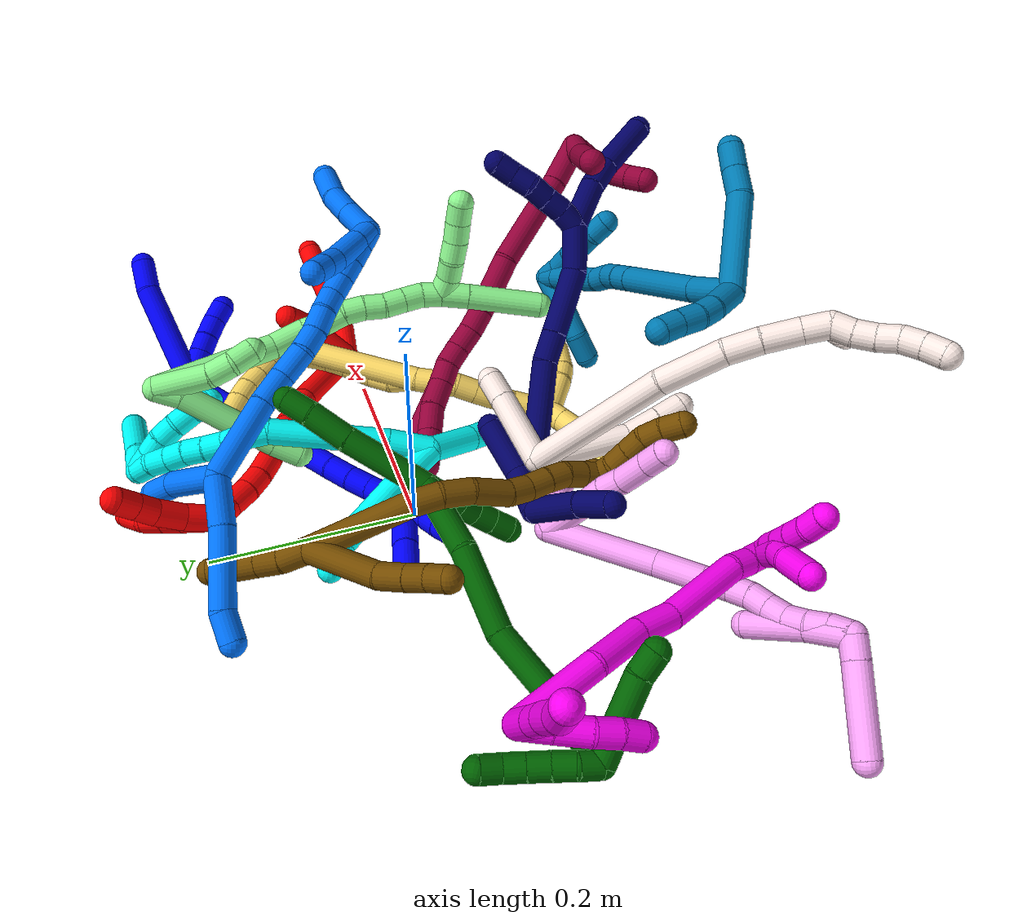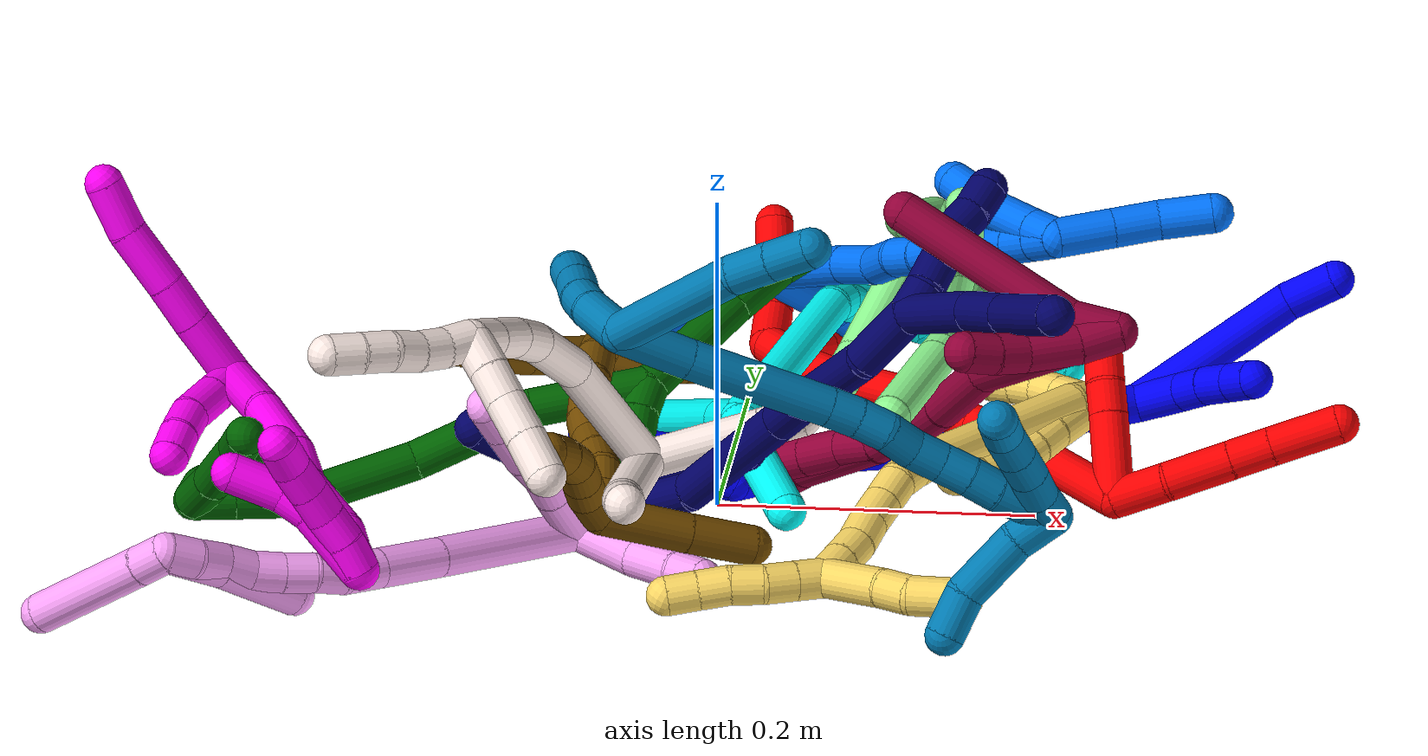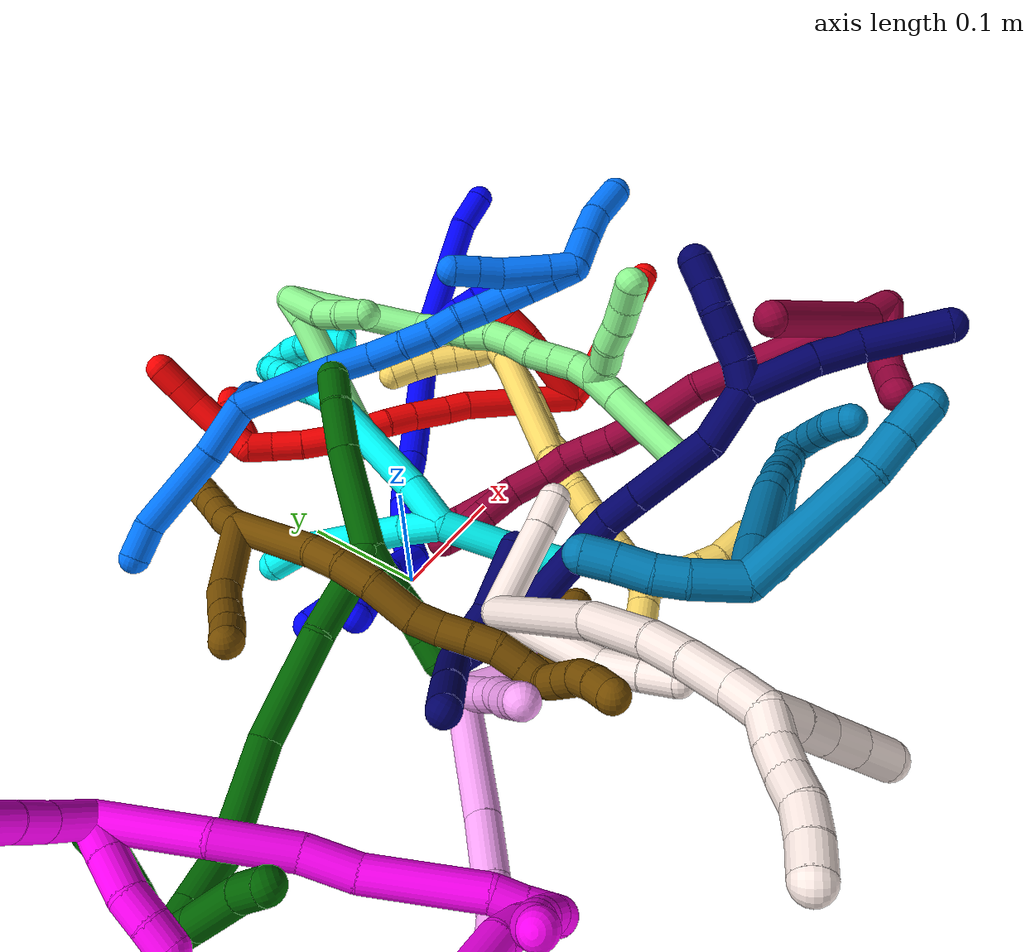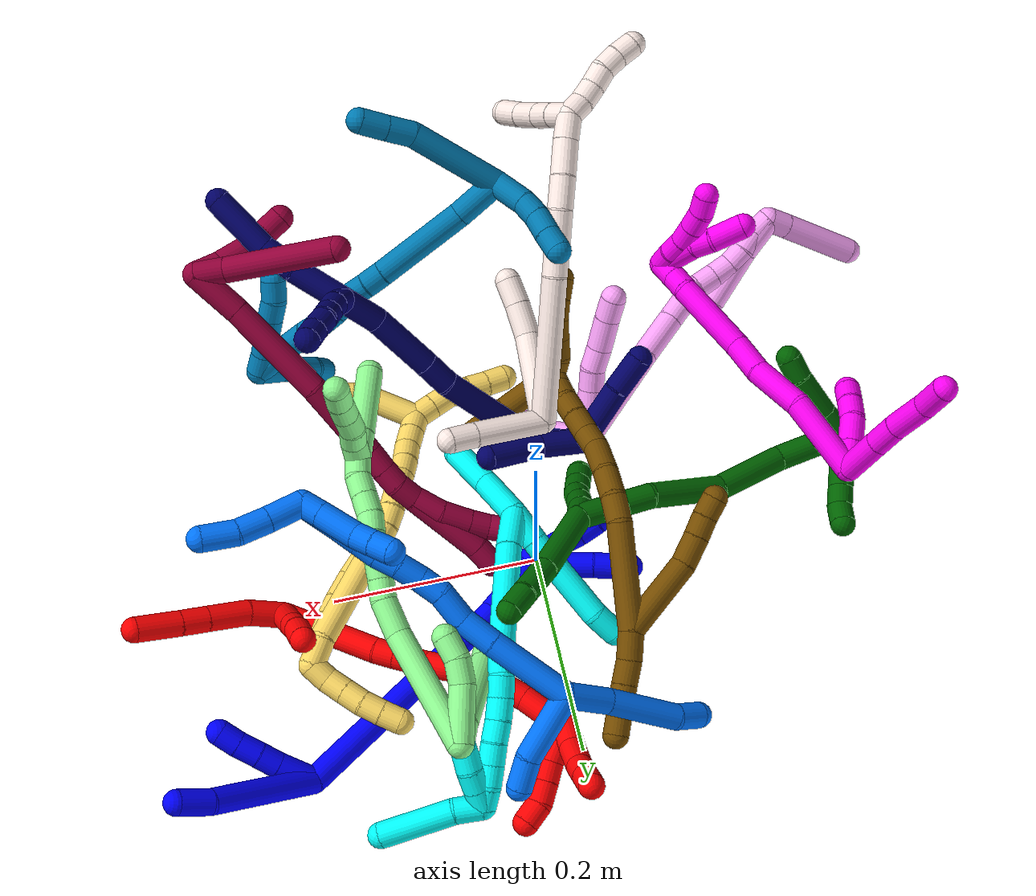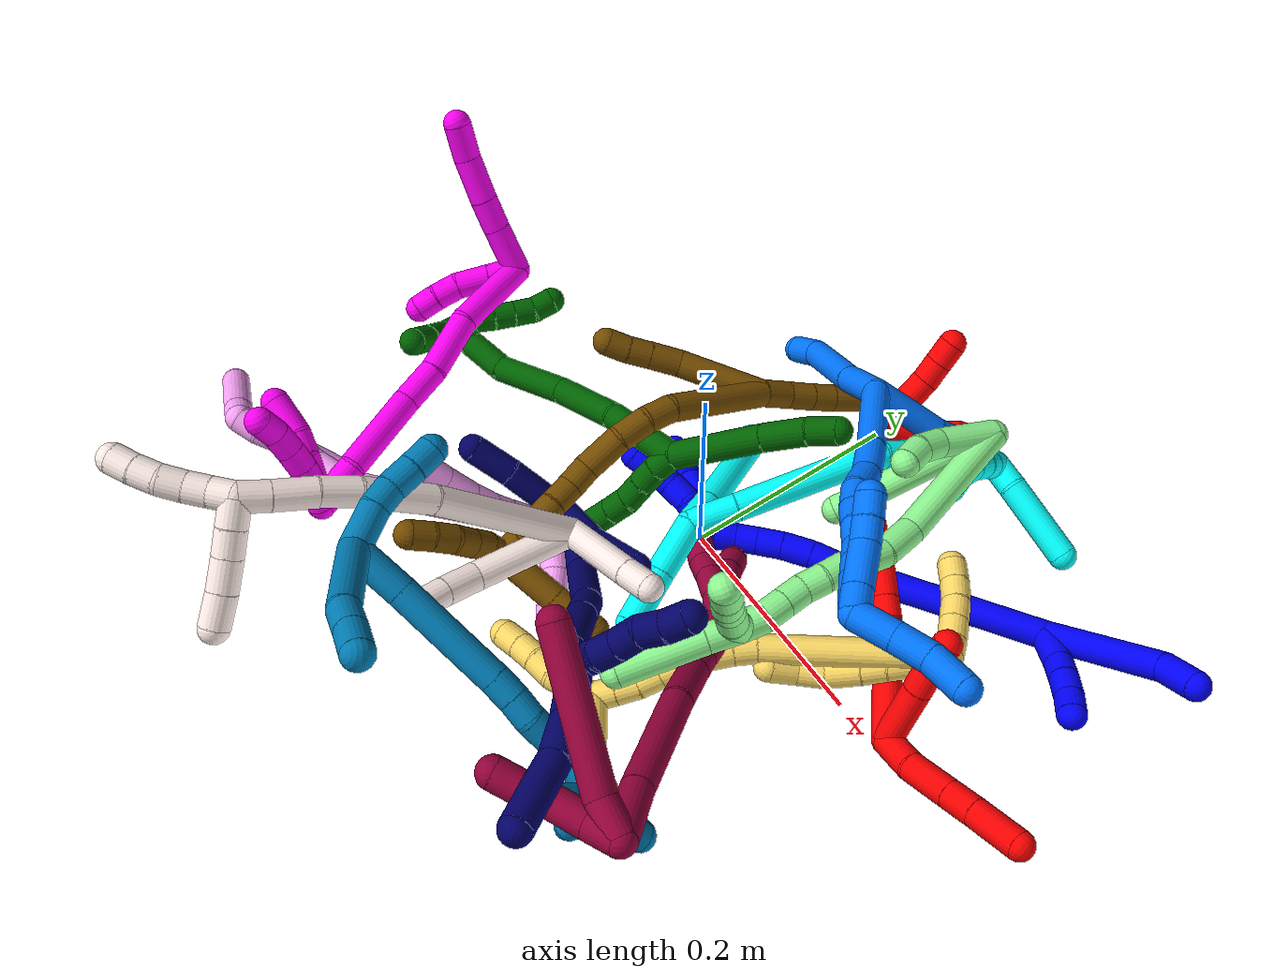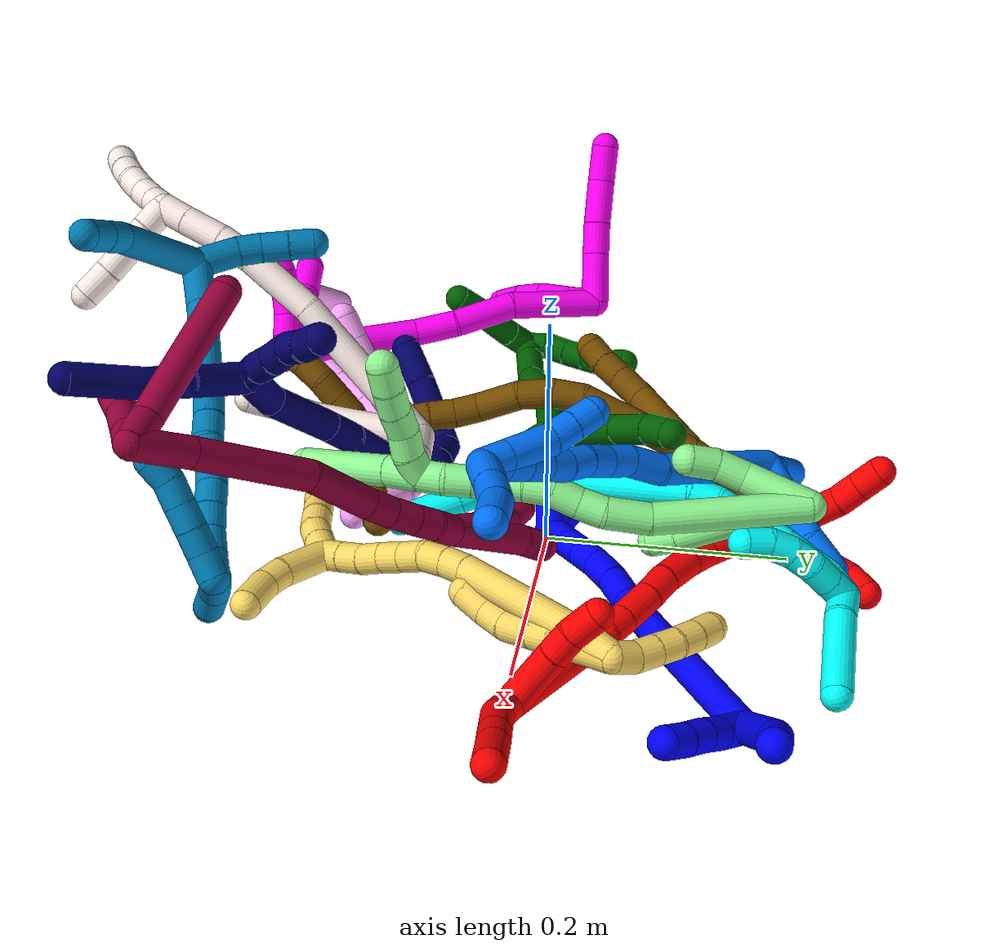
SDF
<sdf version="1.7">
 <world name="default">
  <plugin name="TubeGeneratorPlugin" filename="libtube_generator_plugin.so"/>
  <model name="photoneo_s_sensor">
   <static>1</static>
   <pose>0 0 2 1.57079 1.57079 3.14159</pose>
   <link name="link">
    <inertial><mass>0.1</mass></inertial>
    <sensor name="sensor" type="depth">
     <update_rate>30</update_rate>
     <camera>
      <horizontal_fov>1.22</horizontal_fov>
      <image><width>1920</width><height>1200</height><format>B8G8R8</format></image>
      <clip><near>0.1</near><far>4</far></clip>
      <depth_camera><output>points</output></depth_camera>
     </camera>
     <plugin name="camera_plugin" filename="libgazebo_ros_depth_camera.so">
      <baseline>0.2</baseline>
      <alwaysOn>1</alwaysOn>
      <updateRate>0.0</updateRate>
      <cameraName>camera_ir</cameraName>
      <imageTopicName>/camera/color/image_raw</imageTopicName>
      <cameraInfoTopicName>/camera/color/camera_info</cameraInfoTopicName>
      <depthImageTopicName>/camera/depth/image_raw</depthImageTopicName>
      <depthImageCameraInfoTopicName>/camera/depth/camera_info</depthImageCameraInfoTopicName>
      <pointCloudTopicName>/camera/depth/points</pointCloudTopicName>
      <frameName>fr_optical</frameName>
      <pointCloudCutoff>0.1</pointCloudCutoff>
      <pointCloudCutoffMax>2.0</pointCloudCutoffMax>
      <distortionK1>0</distortionK1>
      <distortionK2>0</distortionK2>
      <distortionK3>0</distortionK3>
      <distortionT1>0</distortionT1>
      <distortionT2>0</distortionT2>
      <CxPrime>0</CxPrime>
      <Cx>0</Cx>
      <Cy>0</Cy>
      <focalLength>0</focalLength>
      <hackBaseline>0</hackBaseline>
     </plugin>
    </sensor>
   </link>
  </model>
  <gravity>0 0 -9.8</gravity>
  <magnetic_field>6e-06 2.3e-05 -4.2e-05</magnetic_field>
  <atmosphere type="adiabatic"/>
  <physics name="default_physics" default="0" type="ode">
   <max_step_size>0.003</max_step_size>
   <real_time_factor>1</real_time_factor>
   <real_time_update_rate>1000</real_time_update_rate>
   <max_contacts>10000</max_contacts>
   <ode>
    <solver>
     <type>quick</type>
     <iters>100</iters>
     <sor>1.3</sor>
     <use_dynamic_moi_rescaling>0</use_dynamic_moi_rescaling>
    </solver>
    <constraints>
     <contact_max_correcting_vel>0</contact_max_correcting_vel>
     <contact_surface_layer>0.001</contact_surface_layer>
     <cfm>0</cfm>
     <erp>0.2</erp>
    </constraints>
   </ode>
  </physics>
  <scene><ambient>0.4 0.4 0.4 1</ambient><background>0.7 0.7 0.7 1</background><shadows>0</shadows></scene>
  <audio><device>default</device></audio>
  <spherical_coordinates>
   <surface_model>EARTH_WGS84</surface_model>
   <latitude_deg>0</latitude_deg>
   <longitude_deg>0</longitude_deg>
   <elevation>0</elevation>
   <heading_deg>0</heading_deg>
  </spherical_coordinates>
  <model name="bin">
   <static>1</static>
   <link name="bottom">
    <collision name="collision-bottom">
     <pose>0 0 -0.01 0 -0 0</pose>
     <geometry><box><size>0.8 0.6 0.02</size></box></geometry>
     <surface>
      <friction><ode><mu>100</mu><mu2>100</mu2></ode></friction>
      <contact><collide_bitmask>65535</collide_bitmask></contact>
     </surface>
    </collision>
   </link>
   <link name="west_wall">
    <collision name="collision-west_wall">
     <pose>-0.41 0 0.1 0 -0 0</pose>
     <geometry><box><size>0.02 0.6 0.2</size></box></geometry>
     <surface>
      <friction><ode><mu>100</mu><mu2>100</mu2></ode></friction>
      <contact><collide_bitmask>65535</collide_bitmask></contact>
     </surface>
    </collision>
   </link>
   <link name="east_wall">
    <collision name="collision-east_wall">
     <pose>0.41 0 0.1 0 -0 0</pose>
     <geometry><box><size>0.02 0.6 0.2</size></box></geometry>
     <surface>
      <friction><ode><mu>100</mu><mu2>100</mu2></ode></friction>
      <contact><collide_bitmask>65535</collide_bitmask></contact>
     </surface>
    </collision>
   </link>
   <link name="south_wall">
    <collision name="collision-south_wall">
     <pose>0 -0.31 0.1 0 -0 0</pose>
     <geometry><box><size>0.8 0.02 0.2</size></box></geometry>
     <surface>
      <friction><ode><mu>100</mu><mu2>100</mu2></ode></friction>
      <contact><collide_bitmask>65535</collide_bitmask></contact>
     </surface>
    </collision>
   </link>
   <link name="north_wall">
    <collision name="collision-north_wall">
     <pose>0 0.31 0.1 0 -0 0</pose>
     <geometry><box><size>0.8 0.02 0.2</size></box></geometry>
     <surface>
      <friction><ode><mu>100</mu><mu2>100</mu2></ode></friction>
      <contact><collide_bitmask>65535</collide_bitmask></contact>
     </surface>
    </collision>
   </link>
  </model>
  <model name="1">
   <static>0</static>
   <link name="1">
    <collision name="collision-cylinder-e_1_2_8">
     <pose>0.00236 0.012735 0.056804 -0.220543 0.04051 -0.004486</pose>
     <geometry><cylinder><radius>0.0125</radius><length>0.116524</length></cylinder></geometry>
     <surface>
      <friction><ode><mu>1.16</mu><mu2>1.16</mu2><slip1>0</slip1><slip2>0</slip2></ode></friction>
      <contact><ode><kp>1e+06</kp><kd>1</kd><max_vel>0</max_vel><min_depth>0.001</min_depth></ode></contact>
     </surface>
    </collision>
    <visual name="visual-cylinder-e_1_2_8">
     <pose>0.00236 0.012735 0.056804 -0.220543 0.04051 -0.004486</pose>
     <geometry><cylinder><radius>0.0125</radius><length>0.116524</length></cylinder></geometry>
     <material><ambient>0 0 1 1</ambient></material>
    </visual>
    <collision name="collision-cylinder-e_2_8_6">
     <pose>0.005823 0.025209 0.130308 0.015625 0.065985 0.000516</pose>
     <geometry><cylinder><radius>0.0125</radius><length>0.033476</length></cylinder></geometry>
     <surface>
      <friction><ode><mu>1.16</mu><mu2>1.16</mu2><slip1>0</slip1><slip2>0</slip2></ode></friction>
      <contact><ode><kp>1e+06</kp><kd>1</kd><max_vel>0</max_vel><min_depth>0.001</min_depth></ode></contact>
     </surface>
    </collision>
    <visual name="visual-cylinder-e_2_8_6">
     <pose>0.005823 0.025209 0.130308 0.015625 0.065985 0.000516</pose>
     <geometry><cylinder><radius>0.0125</radius><length>0.033476</length></cylinder></geometry>
     <material><ambient>0 0 1 1</ambient></material>
    </visual>
    <collision name="collision-cylinder-e_1_2_9">
     <pose>-0.001603 -0.008185 0.017012 0.448446 -0.084712 -0.01933</pose>
     <geometry><cylinder><radius>0.0125</radius><length>0.037893</length></cylinder></geometry>
     <surface>
      <friction><ode><mu>1.16</mu><mu2>1.16</mu2><slip1>0</slip1><slip2>0</slip2></ode></friction>
      <contact><ode><kp>1e+06</kp><kd>1</kd><max_vel>0</max_vel><min_depth>0.001</min_depth></ode></contact>
     </surface>
    </collision>
    <visual name="visual-cylinder-e_1_2_9">
     <pose>-0.001603 -0.008185 0.017012 0.448446 -0.084712 -0.01933</pose>
     <geometry><cylinder><radius>0.0125</radius><length>0.037893</length></cylinder></geometry>
     <material><ambient>0 0 1 1</ambient></material>
    </visual>
    <collision name="collision-cylinder-e_2_9_10">
     <pose>-0.004641 -0.021175 0.042699 0.505811 -0.143649 -0.037184</pose>
     <geometry><cylinder><radius>0.0125</radius><length>0.02004</length></cylinder></geometry>
     <surface>
      <friction><ode><mu>1.16</mu><mu2>1.16</mu2><slip1>0</slip1><slip2>0</slip2></ode></friction>
      <contact><ode><kp>1e+06</kp><kd>1</kd><max_vel>0</max_vel><min_depth>0.001</min_depth></ode></contact>
     </surface>
    </collision>
    <visual name="visual-cylinder-e_2_9_10">
     <pose>-0.004641 -0.021175 0.042699 0.505811 -0.143649 -0.037184</pose>
     <geometry><cylinder><radius>0.0125</radius><length>0.02004</length></cylinder></geometry>
     <material><ambient>0 0 1 1</ambient></material>
    </visual>
    <collision name="collision-cylinder-e_3_10_11">
     <pose>-0.006884 -0.031864 0.060612 0.5671 -0.073766 -0.021505</pose>
     <geometry><cylinder><radius>0.0125</radius><length>0.021966</length></cylinder></geometry>
     <surface>
      <friction><ode><mu>1.16</mu><mu2>1.16</mu2><slip1>0</slip1><slip2>0</slip2></ode></friction>
      <contact><ode><kp>1e+06</kp><kd>1</kd><max_vel>0</max_vel><min_depth>0.001</min_depth></ode></contact>
     </surface>
    </collision>
    <visual name="visual-cylinder-e_3_10_11">
     <pose>-0.006884 -0.031864 0.060612 0.5671 -0.073766 -0.021505</pose>
     <geometry><cylinder><radius>0.0125</radius><length>0.021966</length></cylinder></geometry>
     <material><ambient>0 0 1 1</ambient></material>
    </visual>
    <collision name="collision-cylinder-e_4_11_5">
     <pose>-0.009148 -0.043627 0.077871 0.632566 -0.145154 -0.047579</pose>
     <geometry><cylinder><radius>0.0125</radius><length>0.020101</length></cylinder></geometry>
     <surface>
      <friction><ode><mu>1.16</mu><mu2>1.16</mu2><slip1>0</slip1><slip2>0</slip2></ode></friction>
      <contact><ode><kp>1e+06</kp><kd>1</kd><max_vel>0</max_vel><min_depth>0.001</min_depth></ode></contact>
     </surface>
    </collision>
    <visual name="visual-cylinder-e_4_11_5">
     <pose>-0.009148 -0.043627 0.077871 0.632566 -0.145154 -0.047579</pose>
     <geometry><cylinder><radius>0.0125</radius><length>0.020101</length></cylinder></geometry>
     <material><ambient>0 0 1 1</ambient></material>
    </visual>
    <collision name="collision-cylinder-e_1_2_12">
     <pose>-0.043095 -0.025768 -0.049646 2.66284 -0.656463 -1.89797</pose>
     <geometry><cylinder><radius>0.0125</radius><length>0.141223</length></cylinder></geometry>
     <surface>
      <friction><ode><mu>1.16</mu><mu2>1.16</mu2><slip1>0</slip1><slip2>0</slip2></ode></friction>
      <contact><ode><kp>1e+06</kp><kd>1</kd><max_vel>0</max_vel><min_depth>0.001</min_depth></ode></contact>
     </surface>
    </collision>
    <visual name="visual-cylinder-e_1_2_12">
     <pose>-0.043095 -0.025768 -0.049646 2.66284 -0.656463 -1.89797</pose>
     <geometry><cylinder><radius>0.0125</radius><length>0.141223</length></cylinder></geometry>
     <material><ambient>0 0 1 1</ambient></material>
    </visual>
    <collision name="collision-cylinder-e_2_12_13">
     <pose>-0.098932 -0.058595 -0.113262 2.67369 -0.683239 -1.96064</pose>
     <geometry><cylinder><radius>0.0125</radius><length>0.040364</length></cylinder></geometry>
     <surface>
      <friction><ode><mu>1.16</mu><mu2>1.16</mu2><slip1>0</slip1><slip2>0</slip2></ode></friction>
      <contact><ode><kp>1e+06</kp><kd>1</kd><max_vel>0</max_vel><min_depth>0.001</min_depth></ode></contact>
     </surface>
    </collision>
    <visual name="visual-cylinder-e_2_12_13">
     <pose>-0.098932 -0.058595 -0.113262 2.67369 -0.683239 -1.96064</pose>
     <geometry><cylinder><radius>0.0125</radius><length>0.040364</length></cylinder></geometry>
     <material><ambient>0 0 1 1</ambient></material>
    </visual>
    <collision name="collision-cylinder-e_3_13_14">
     <pose>-0.121454 -0.069743 -0.137037 2.74645 -0.744141 -2.19367</pose>
     <geometry><cylinder><radius>0.0125</radius><length>0.028881</length></cylinder></geometry>
     <surface>
      <friction><ode><mu>1.16</mu><mu2>1.16</mu2><slip1>0</slip1><slip2>0</slip2></ode></friction>
      <contact><ode><kp>1e+06</kp><kd>1</kd><max_vel>0</max_vel><min_depth>0.001</min_depth></ode></contact>
     </surface>
    </collision>
    <visual name="visual-cylinder-e_3_13_14">
     <pose>-0.121454 -0.069743 -0.137037 2.74645 -0.744141 -2.19367</pose>
     <geometry><cylinder><radius>0.0125</radius><length>0.028881</length></cylinder></geometry>
     <material><ambient>0 0 1 1</ambient></material>
    </visual>
    <collision name="collision-cylinder-e_4_14_15">
     <pose>-0.139382 -0.078974 -0.155885 2.62463 -0.664365 -1.8337</pose>
     <geometry><cylinder><radius>0.0125</radius><length>0.026427</length></cylinder></geometry>
     <surface>
      <friction><ode><mu>1.16</mu><mu2>1.16</mu2><slip1>0</slip1><slip2>0</slip2></ode></friction>
      <contact><ode><kp>1e+06</kp><kd>1</kd><max_vel>0</max_vel><min_depth>0.001</min_depth></ode></contact>
     </surface>
    </collision>
    <visual name="visual-cylinder-e_4_14_15">
     <pose>-0.139382 -0.078974 -0.155885 2.62463 -0.664365 -1.8337</pose>
     <geometry><cylinder><radius>0.0125</radius><length>0.026427</length></cylinder></geometry>
     <material><ambient>0 0 1 1</ambient></material>
    </visual>
    <collision name="collision-cylinder-e_5_15_16">
     <pose>-0.15398 -0.089585 -0.172389 2.50903 -0.608996 -1.53029</pose>
     <geometry><cylinder><radius>0.0125</radius><length>0.022555</length></cylinder></geometry>
     <surface>
      <friction><ode><mu>1.16</mu><mu2>1.16</mu2><slip1>0</slip1><slip2>0</slip2></ode></friction>
      <contact><ode><kp>1e+06</kp><kd>1</kd><max_vel>0</max_vel><min_depth>0.001</min_depth></ode></contact>
     </surface>
    </collision>
    <visual name="visual-cylinder-e_5_15_16">
     <pose>-0.15398 -0.089585 -0.172389 2.50903 -0.608996 -1.53029</pose>
     <geometry><cylinder><radius>0.0125</radius><length>0.022555</length></cylinder></geometry>
     <material><ambient>0 0 1 1</ambient></material>
    </visual>
    <collision name="collision-cylinder-e_6_16_17">
     <pose>-0.166185 -0.100027 -0.186368 2.48978 -0.611853 -1.50318</pose>
     <geometry><cylinder><radius>0.0125</radius><length>0.020034</length></cylinder></geometry>
     <surface>
      <friction><ode><mu>1.16</mu><mu2>1.16</mu2><slip1>0</slip1><slip2>0</slip2></ode></friction>
      <contact><ode><kp>1e+06</kp><kd>1</kd><max_vel>0</max_vel><min_depth>0.001</min_depth></ode></contact>
     </surface>
    </collision>
    <visual name="visual-cylinder-e_6_16_17">
     <pose>-0.166185 -0.100027 -0.186368 2.48978 -0.611853 -1.50318</pose>
     <geometry><cylinder><radius>0.0125</radius><length>0.020034</length></cylinder></geometry>
     <material><ambient>0 0 1 1</ambient></material>
    </visual>
    <collision name="collision-cylinder-e_7_17_1">
     <pose>-0.178918 -0.111127 -0.197246 2.18931 -0.748307 -1.30147</pose>
     <geometry><cylinder><radius>0.0125</radius><length>0.020516</length></cylinder></geometry>
     <surface>
      <friction><ode><mu>1.16</mu><mu2>1.16</mu2><slip1>0</slip1><slip2>0</slip2></ode></friction>
      <contact><ode><kp>1e+06</kp><kd>1</kd><max_vel>0</max_vel><min_depth>0.001</min_depth></ode></contact>
     </surface>
    </collision>
    <visual name="visual-cylinder-e_7_17_1">
     <pose>-0.178918 -0.111127 -0.197246 2.18931 -0.748307 -1.30147</pose>
     <geometry><cylinder><radius>0.0125</radius><length>0.020516</length></cylinder></geometry>
     <material><ambient>0 0 1 1</ambient></material>
    </visual>
    <collision name="collision-cylinder-e_1_1_18">
     <pose>-0.20212 -0.113153 -0.210853 -2.72441 -1.01321 2.41277</pose>
     <geometry><cylinder><radius>0.0125</radius><length>0.038236</length></cylinder></geometry>
     <surface>
      <friction><ode><mu>1.16</mu><mu2>1.16</mu2><slip1>0</slip1><slip2>0</slip2></ode></friction>
      <contact><ode><kp>1e+06</kp><kd>1</kd><max_vel>0</max_vel><min_depth>0.001</min_depth></ode></contact>
     </surface>
    </collision>
    <visual name="visual-cylinder-e_1_1_18">
     <pose>-0.20212 -0.113153 -0.210853 -2.72441 -1.01321 2.41277</pose>
     <geometry><cylinder><radius>0.0125</radius><length>0.038236</length></cylinder></geometry>
     <material><ambient>0 0 1 1</ambient></material>
    </visual>
    <collision name="collision-cylinder-e_2_18_19">
     <pose>-0.225708 -0.10846 -0.227511 -3.06167 -0.780813 2.9479</pose>
     <geometry><cylinder><radius>0.0125</radius><length>0.020929</length></cylinder></geometry>
     <surface>
      <friction><ode><mu>1.16</mu><mu2>1.16</mu2><slip1>0</slip1><slip2>0</slip2></ode></friction>
      <contact><ode><kp>1e+06</kp><kd>1</kd><max_vel>0</max_vel><min_depth>0.001</min_depth></ode></contact>
     </surface>
    </collision>
    <visual name="visual-cylinder-e_2_18_19">
     <pose>-0.225708 -0.10846 -0.227511 -3.06167 -0.780813 2.9479</pose>
     <geometry><cylinder><radius>0.0125</radius><length>0.020929</length></cylinder></geometry>
     <material><ambient>0 0 1 1</ambient></material>
    </visual>
    <collision name="collision-cylinder-e_3_19_20">
     <pose>-0.241434 -0.107711 -0.241082 -3.11623 -0.935569 3.09139</pose>
     <geometry><cylinder><radius>0.0125</radius><length>0.020773</length></cylinder></geometry>
     <surface>
      <friction><ode><mu>1.16</mu><mu2>1.16</mu2><slip1>0</slip1><slip2>0</slip2></ode></friction>
      <contact><ode><kp>1e+06</kp><kd>1</kd><max_vel>0</max_vel><min_depth>0.001</min_depth></ode></contact>
     </surface>
    </collision>
    <visual name="visual-cylinder-e_3_19_20">
     <pose>-0.241434 -0.107711 -0.241082 -3.11623 -0.935569 3.09139</pose>
     <geometry><cylinder><radius>0.0125</radius><length>0.020773</length></cylinder></geometry>
     <material><ambient>0 0 1 1</ambient></material>
    </visual>
    <collision name="collision-cylinder-e_4_20_4">
     <pose>-0.257818 -0.108345 -0.25321 3.00985 -0.927144 -2.8792</pose>
     <geometry><cylinder><radius>0.0125</radius><length>0.020062</length></cylinder></geometry>
     <surface>
      <friction><ode><mu>1.16</mu><mu2>1.16</mu2><slip1>0</slip1><slip2>0</slip2></ode></friction>
      <contact><ode><kp>1e+06</kp><kd>1</kd><max_vel>0</max_vel><min_depth>0.001</min_depth></ode></contact>
     </surface>
    </collision>
    <visual name="visual-cylinder-e_4_20_4">
     <pose>-0.257818 -0.108345 -0.25321 3.00985 -0.927144 -2.8792</pose>
     <geometry><cylinder><radius>0.0125</radius><length>0.020062</length></cylinder></geometry>
     <material><ambient>0 0 1 1</ambient></material>
    </visual>
    <collision name="collision-cylinder-e_1_1_21">
     <pose>-0.192014 -0.1089 -0.215896 -2.61273 -0.353921 1.16738</pose>
     <geometry><cylinder><radius>0.0125</radius><length>0.035293</length></cylinder></geometry>
     <surface>
      <friction><ode><mu>1.16</mu><mu2>1.16</mu2><slip1>0</slip1><slip2>0</slip2></ode></friction>
      <contact><ode><kp>1e+06</kp><kd>1</kd><max_vel>0</max_vel><min_depth>0.001</min_depth></ode></contact>
     </surface>
    </collision>
    <visual name="visual-cylinder-e_1_1_21">
     <pose>-0.192014 -0.1089 -0.215896 -2.61273 -0.353921 1.16738</pose>
     <geometry><cylinder><radius>0.0125</radius><length>0.035293</length></cylinder></geometry>
     <material><ambient>0 0 1 1</ambient></material>
    </visual>
    <collision name="collision-cylinder-e_2_21_22">
     <pose>-0.20414 -0.094842 -0.242075 -2.69405 -0.427677 1.52392</pose>
     <geometry><cylinder><radius>0.0125</radius><length>0.028982</length></cylinder></geometry>
     <surface>
      <friction><ode><mu>1.16</mu><mu2>1.16</mu2><slip1>0</slip1><slip2>0</slip2></ode></friction>
      <contact><ode><kp>1e+06</kp><kd>1</kd><max_vel>0</max_vel><min_depth>0.001</min_depth></ode></contact>
     </surface>
    </collision>
    <visual name="visual-cylinder-e_2_21_22">
     <pose>-0.20414 -0.094842 -0.242075 -2.69405 -0.427677 1.52392</pose>
     <geometry><cylinder><radius>0.0125</radius><length>0.028982</length></cylinder></geometry>
     <material><ambient>0 0 1 1</ambient></material>
    </visual>
    <collision name="collision-cylinder-e_3_22_3">
     <pose>-0.216389 -0.082453 -0.269308 -2.73087 -0.356761 1.42694</pose>
     <geometry><cylinder><radius>0.0125</radius><length>0.035725</length></cylinder></geometry>
     <surface>
      <friction><ode><mu>1.16</mu><mu2>1.16</mu2><slip1>0</slip1><slip2>0</slip2></ode></friction>
      <contact><ode><kp>1e+06</kp><kd>1</kd><max_vel>0</max_vel><min_depth>0.001</min_depth></ode></contact>
     </surface>
    </collision>
    <visual name="visual-cylinder-e_3_22_3">
     <pose>-0.216389 -0.082453 -0.269308 -2.73087 -0.356761 1.42694</pose>
     <geometry><cylinder><radius>0.0125</radius><length>0.035725</length></cylinder></geometry>
     <material><ambient>0 0 1 1</ambient></material>
    </visual>
    <collision name="collision-sphere-3">
     <pose>-0.222627 -0.07577 -0.284653 0 -0 0</pose>
     <geometry><sphere><radius>0.0125</radius></sphere></geometry>
     <surface>
      <friction><ode><mu>1.16</mu><mu2>1.16</mu2><slip1>0</slip1><slip2>0</slip2></ode></friction>
      <contact><ode><kp>1e+06</kp><kd>1</kd><max_vel>0</max_vel><min_depth>0.001</min_depth></ode></contact>
     </surface>
    </collision>
    <visual name="visual-sphere-3">
     <pose>-0.222627 -0.07577 -0.284653 0 -0 0</pose>
     <geometry><sphere><radius>0.0125</radius></sphere></geometry>
     <material><ambient>0 0 1 1</ambient></material>
    </visual>
    <collision name="collision-sphere-22">
     <pose>-0.21015 -0.089136 -0.253962 0 -0 0</pose>
     <geometry><sphere><radius>0.0125</radius></sphere></geometry>
     <surface>
      <friction><ode><mu>1.16</mu><mu2>1.16</mu2><slip1>0</slip1><slip2>0</slip2></ode></friction>
      <contact><ode><kp>1e+06</kp><kd>1</kd><max_vel>0</max_vel><min_depth>0.001</min_depth></ode></contact>
     </surface>
    </collision>
    <visual name="visual-sphere-22">
     <pose>-0.21015 -0.089136 -0.253962 0 -0 0</pose>
     <geometry><sphere><radius>0.0125</radius></sphere></geometry>
     <material><ambient>0 0 1 1</ambient></material>
    </visual>
    <collision name="collision-sphere-21">
     <pose>-0.19813 -0.100548 -0.230187 0 -0 0</pose>
     <geometry><sphere><radius>0.0125</radius></sphere></geometry>
     <surface>
      <friction><ode><mu>1.16</mu><mu2>1.16</mu2><slip1>0</slip1><slip2>0</slip2></ode></friction>
      <contact><ode><kp>1e+06</kp><kd>1</kd><max_vel>0</max_vel><min_depth>0.001</min_depth></ode></contact>
     </surface>
    </collision>
    <visual name="visual-sphere-21">
     <pose>-0.19813 -0.100548 -0.230187 0 -0 0</pose>
     <geometry><sphere><radius>0.0125</radius></sphere></geometry>
     <material><ambient>0 0 1 1</ambient></material>
    </visual>
    <collision name="collision-sphere-4">
     <pose>-0.265842 -0.109136 -0.259178 0 -0 0</pose>
     <geometry><sphere><radius>0.0125</radius></sphere></geometry>
     <surface>
      <friction><ode><mu>1.16</mu><mu2>1.16</mu2><slip1>0</slip1><slip2>0</slip2></ode></friction>
      <contact><ode><kp>1e+06</kp><kd>1</kd><max_vel>0</max_vel><min_depth>0.001</min_depth></ode></contact>
     </surface>
    </collision>
    <visual name="visual-sphere-4">
     <pose>-0.265842 -0.109136 -0.259178 0 -0 0</pose>
     <geometry><sphere><radius>0.0125</radius></sphere></geometry>
     <material><ambient>0 0 1 1</ambient></material>
    </visual>
    <collision name="collision-sphere-20">
     <pose>-0.249794 -0.107554 -0.247242 0 -0 0</pose>
     <geometry><sphere><radius>0.0125</radius></sphere></geometry>
     <surface>
      <friction><ode><mu>1.16</mu><mu2>1.16</mu2><slip1>0</slip1><slip2>0</slip2></ode></friction>
      <contact><ode><kp>1e+06</kp><kd>1</kd><max_vel>0</max_vel><min_depth>0.001</min_depth></ode></contact>
     </surface>
    </collision>
    <visual name="visual-sphere-20">
     <pose>-0.249794 -0.107554 -0.247242 0 -0 0</pose>
     <geometry><sphere><radius>0.0125</radius></sphere></geometry>
     <material><ambient>0 0 1 1</ambient></material>
    </visual>
    <collision name="collision-sphere-11">
     <pose>-0.007694 -0.037747 0.069851 0 -0 0</pose>
     <geometry><sphere><radius>0.0125</radius></sphere></geometry>
     <surface>
      <friction><ode><mu>1.16</mu><mu2>1.16</mu2><slip1>0</slip1><slip2>0</slip2></ode></friction>
      <contact><ode><kp>1e+06</kp><kd>1</kd><max_vel>0</max_vel><min_depth>0.001</min_depth></ode></contact>
     </surface>
    </collision>
    <visual name="visual-sphere-11">
     <pose>-0.007694 -0.037747 0.069851 0 -0 0</pose>
     <geometry><sphere><radius>0.0125</radius></sphere></geometry>
     <material><ambient>0 0 1 1</ambient></material>
    </visual>
    <collision name="collision-sphere-10">
     <pose>-0.006075 -0.02598 0.051374 0 -0 0</pose>
     <geometry><sphere><radius>0.0125</radius></sphere></geometry>
     <surface>
      <friction><ode><mu>1.16</mu><mu2>1.16</mu2><slip1>0</slip1><slip2>0</slip2></ode></friction>
      <contact><ode><kp>1e+06</kp><kd>1</kd><max_vel>0</max_vel><min_depth>0.001</min_depth></ode></contact>
     </surface>
    </collision>
    <visual name="visual-sphere-10">
     <pose>-0.006075 -0.02598 0.051374 0 -0 0</pose>
     <geometry><sphere><radius>0.0125</radius></sphere></geometry>
     <material><ambient>0 0 1 1</ambient></material>
    </visual>
    <collision name="collision-sphere-6">
     <pose>0.006926 0.024948 0.147007 0 -0 0</pose>
     <geometry><sphere><radius>0.0125</radius></sphere></geometry>
     <surface>
      <friction><ode><mu>1.16</mu><mu2>1.16</mu2><slip1>0</slip1><slip2>0</slip2></ode></friction>
      <contact><ode><kp>1e+06</kp><kd>1</kd><max_vel>0</max_vel><min_depth>0.001</min_depth></ode></contact>
     </surface>
    </collision>
    <visual name="visual-sphere-6">
     <pose>0.006926 0.024948 0.147007 0 -0 0</pose>
     <geometry><sphere><radius>0.0125</radius></sphere></geometry>
     <material><ambient>0 0 1 1</ambient></material>
    </visual>
    <collision name="collision-sphere-9">
     <pose>-0.003206 -0.01637 0.034024 0 -0 0</pose>
     <geometry><sphere><radius>0.0125</radius></sphere></geometry>
     <surface>
      <friction><ode><mu>1.16</mu><mu2>1.16</mu2><slip1>0</slip1><slip2>0</slip2></ode></friction>
      <contact><ode><kp>1e+06</kp><kd>1</kd><max_vel>0</max_vel><min_depth>0.001</min_depth></ode></contact>
     </surface>
    </collision>
    <visual name="visual-sphere-9">
     <pose>-0.003206 -0.01637 0.034024 0 -0 0</pose>
     <geometry><sphere><radius>0.0125</radius></sphere></geometry>
     <material><ambient>0 0 1 1</ambient></material>
    </visual>
    <collision name="collision-sphere-2">
     <geometry><sphere><radius>0.0125</radius></sphere></geometry>
     <surface>
      <friction><ode><mu>1.16</mu><mu2>1.16</mu2><slip1>0</slip1><slip2>0</slip2></ode></friction>
      <contact><ode><kp>1e+06</kp><kd>1</kd><max_vel>0</max_vel><min_depth>0.001</min_depth></ode></contact>
     </surface>
    </collision>
    <visual name="visual-sphere-2">
     <geometry><sphere><radius>0.0125</radius></sphere></geometry>
     <material><ambient>0 0 1 1</ambient></material>
    </visual>
    <collision name="collision-sphere-19">
     <pose>-0.233074 -0.107867 -0.234921 0 -0 0</pose>
     <geometry><sphere><radius>0.0125</radius></sphere></geometry>
     <surface>
      <friction><ode><mu>1.16</mu><mu2>1.16</mu2><slip1>0</slip1><slip2>0</slip2></ode></friction>
      <contact><ode><kp>1e+06</kp><kd>1</kd><max_vel>0</max_vel><min_depth>0.001</min_depth></ode></contact>
     </surface>
    </collision>
    <visual name="visual-sphere-19">
     <pose>-0.233074 -0.107867 -0.234921 0 -0 0</pose>
     <geometry><sphere><radius>0.0125</radius></sphere></geometry>
     <material><ambient>0 0 1 1</ambient></material>
    </visual>
    <collision name="collision-sphere-8">
     <pose>0.004719 0.02547 0.113608 0 -0 0</pose>
     <geometry><sphere><radius>0.0125</radius></sphere></geometry>
     <surface>
      <friction><ode><mu>1.16</mu><mu2>1.16</mu2><slip1>0</slip1><slip2>0</slip2></ode></friction>
      <contact><ode><kp>1e+06</kp><kd>1</kd><max_vel>0</max_vel><min_depth>0.001</min_depth></ode></contact>
     </surface>
    </collision>
    <visual name="visual-sphere-8">
     <pose>0.004719 0.02547 0.113608 0 -0 0</pose>
     <geometry><sphere><radius>0.0125</radius></sphere></geometry>
     <material><ambient>0 0 1 1</ambient></material>
    </visual>
    <collision name="collision-sphere-5">
     <pose>-0.010601 -0.049507 0.085892 0 -0 0</pose>
     <geometry><sphere><radius>0.0125</radius></sphere></geometry>
     <surface>
      <friction><ode><mu>1.16</mu><mu2>1.16</mu2><slip1>0</slip1><slip2>0</slip2></ode></friction>
      <contact><ode><kp>1e+06</kp><kd>1</kd><max_vel>0</max_vel><min_depth>0.001</min_depth></ode></contact>
     </surface>
    </collision>
    <visual name="visual-sphere-5">
     <pose>-0.010601 -0.049507 0.085892 0 -0 0</pose>
     <geometry><sphere><radius>0.0125</radius></sphere></geometry>
     <material><ambient>0 0 1 1</ambient></material>
    </visual>
    <collision name="collision-sphere-12">
     <pose>-0.086191 -0.051535 -0.099293 0 -0 0</pose>
     <geometry><sphere><radius>0.0125</radius></sphere></geometry>
     <surface>
      <friction><ode><mu>1.16</mu><mu2>1.16</mu2><slip1>0</slip1><slip2>0</slip2></ode></friction>
      <contact><ode><kp>1e+06</kp><kd>1</kd><max_vel>0</max_vel><min_depth>0.001</min_depth></ode></contact>
     </surface>
    </collision>
    <visual name="visual-sphere-12">
     <pose>-0.086191 -0.051535 -0.099293 0 -0 0</pose>
     <geometry><sphere><radius>0.0125</radius></sphere></geometry>
     <material><ambient>0 0 1 1</ambient></material>
    </visual>
    <collision name="collision-sphere-13">
     <pose>-0.111673 -0.065654 -0.127232 0 -0 0</pose>
     <geometry><sphere><radius>0.0125</radius></sphere></geometry>
     <surface>
      <friction><ode><mu>1.16</mu><mu2>1.16</mu2><slip1>0</slip1><slip2>0</slip2></ode></friction>
      <contact><ode><kp>1e+06</kp><kd>1</kd><max_vel>0</max_vel><min_depth>0.001</min_depth></ode></contact>
     </surface>
    </collision>
    <visual name="visual-sphere-13">
     <pose>-0.111673 -0.065654 -0.127232 0 -0 0</pose>
     <geometry><sphere><radius>0.0125</radius></sphere></geometry>
     <material><ambient>0 0 1 1</ambient></material>
    </visual>
    <collision name="collision-sphere-14">
     <pose>-0.131235 -0.073832 -0.146841 0 -0 0</pose>
     <geometry><sphere><radius>0.0125</radius></sphere></geometry>
     <surface>
      <friction><ode><mu>1.16</mu><mu2>1.16</mu2><slip1>0</slip1><slip2>0</slip2></ode></friction>
      <contact><ode><kp>1e+06</kp><kd>1</kd><max_vel>0</max_vel><min_depth>0.001</min_depth></ode></contact>
     </surface>
    </collision>
    <visual name="visual-sphere-14">
     <pose>-0.131235 -0.073832 -0.146841 0 -0 0</pose>
     <geometry><sphere><radius>0.0125</radius></sphere></geometry>
     <material><ambient>0 0 1 1</ambient></material>
    </visual>
    <collision name="collision-sphere-15">
     <pose>-0.147529 -0.084116 -0.164929 0 -0 0</pose>
     <geometry><sphere><radius>0.0125</radius></sphere></geometry>
     <surface>
      <friction><ode><mu>1.16</mu><mu2>1.16</mu2><slip1>0</slip1><slip2>0</slip2></ode></friction>
      <contact><ode><kp>1e+06</kp><kd>1</kd><max_vel>0</max_vel><min_depth>0.001</min_depth></ode></contact>
     </surface>
    </collision>
    <visual name="visual-sphere-15">
     <pose>-0.147529 -0.084116 -0.164929 0 -0 0</pose>
     <geometry><sphere><radius>0.0125</radius></sphere></geometry>
     <material><ambient>0 0 1 1</ambient></material>
    </visual>
    <collision name="collision-sphere-16">
     <pose>-0.160431 -0.095053 -0.179849 0 -0 0</pose>
     <geometry><sphere><radius>0.0125</radius></sphere></geometry>
     <surface>
      <friction><ode><mu>1.16</mu><mu2>1.16</mu2><slip1>0</slip1><slip2>0</slip2></ode></friction>
      <contact><ode><kp>1e+06</kp><kd>1</kd><max_vel>0</max_vel><min_depth>0.001</min_depth></ode></contact>
     </surface>
    </collision>
    <visual name="visual-sphere-16">
     <pose>-0.160431 -0.095053 -0.179849 0 -0 0</pose>
     <geometry><sphere><radius>0.0125</radius></sphere></geometry>
     <material><ambient>0 0 1 1</ambient></material>
    </visual>
    <collision name="collision-sphere-17">
     <pose>-0.171939 -0.105002 -0.192887 0 -0 0</pose>
     <geometry><sphere><radius>0.0125</radius></sphere></geometry>
     <surface>
      <friction><ode><mu>1.16</mu><mu2>1.16</mu2><slip1>0</slip1><slip2>0</slip2></ode></friction>
      <contact><ode><kp>1e+06</kp><kd>1</kd><max_vel>0</max_vel><min_depth>0.001</min_depth></ode></contact>
     </surface>
    </collision>
    <visual name="visual-sphere-17">
     <pose>-0.171939 -0.105002 -0.192887 0 -0 0</pose>
     <geometry><sphere><radius>0.0125</radius></sphere></geometry>
     <material><ambient>0 0 1 1</ambient></material>
    </visual>
    <collision name="collision-sphere-1">
     <pose>-0.185898 -0.117252 -0.201605 0 -0 0</pose>
     <geometry><sphere><radius>0.0125</radius></sphere></geometry>
     <surface>
      <friction><ode><mu>1.16</mu><mu2>1.16</mu2><slip1>0</slip1><slip2>0</slip2></ode></friction>
      <contact><ode><kp>1e+06</kp><kd>1</kd><max_vel>0</max_vel><min_depth>0.001</min_depth></ode></contact>
     </surface>
    </collision>
    <visual name="visual-sphere-1">
     <pose>-0.185898 -0.117252 -0.201605 0 -0 0</pose>
     <geometry><sphere><radius>0.0125</radius></sphere></geometry>
     <material><ambient>0 0 1 1</ambient></material>
    </visual>
    <collision name="collision-sphere-18">
     <pose>-0.218343 -0.109054 -0.220102 0 -0 0</pose>
     <geometry><sphere><radius>0.0125</radius></sphere></geometry>
     <surface>
      <friction><ode><mu>1.16</mu><mu2>1.16</mu2><slip1>0</slip1><slip2>0</slip2></ode></friction>
      <contact><ode><kp>1e+06</kp><kd>1</kd><max_vel>0</max_vel><min_depth>0.001</min_depth></ode></contact>
     </surface>
    </collision>
    <visual name="visual-sphere-18">
     <pose>-0.218343 -0.109054 -0.220102 0 -0 0</pose>
     <geometry><sphere><radius>0.0125</radius></sphere></geometry>
     <material><ambient>0 0 1 1</ambient></material>
    </visual>
    <inertial>
     <pose>-0.094435 -0.049252 -0.084158 0 -0 0</pose>
     <mass>0.75</mass>
     <inertia>
      <ixx>-0.000119</ixx>
      <ixy>0</ixy>
      <ixz>0</ixz>
      <iyy>0.000112</iyy>
      <iyz>0</iyz>
      <izz>0.000221</izz>
     </inertia>
    </inertial>
   </link>
   <pose>0.252777 0.178569 0.013397 0.559033 0.899091 0.646851</pose>
  </model>
  <model name="2">
   <static>0</static>
   <link name="2">
    <collision name="collision-cylinder-e_1_2_8">
     <pose>0.008455 -0.015945 0.001126 1.50032 0.486557 0.454587</pose>
     <geometry><cylinder><radius>0.0125</radius><length>0.036166</length></cylinder></geometry>
     <surface>
      <friction><ode><mu>1.16</mu><mu2>1.16</mu2><slip1>0</slip1><slip2>0</slip2></ode></friction>
      <contact><ode><kp>1e+06</kp><kd>1</kd><max_vel>0</max_vel><min_depth>0.001</min_depth></ode></contact>
     </surface>
    </collision>
    <visual name="visual-cylinder-e_1_2_8">
     <pose>0.008455 -0.015945 0.001126 1.50032 0.486557 0.454587</pose>
     <geometry><cylinder><radius>0.0125</radius><length>0.036166</length></cylinder></geometry>
     <material><ambient>1 0 0 1</ambient></material>
    </visual>
    <collision name="collision-cylinder-e_2_8_9">
     <pose>0.029414 -0.048225 0.00661 1.31004 0.63676 0.495936</pose>
     <geometry><cylinder><radius>0.0125</radius><length>0.042056</length></cylinder></geometry>
     <surface>
      <friction><ode><mu>1.16</mu><mu2>1.16</mu2><slip1>0</slip1><slip2>0</slip2></ode></friction>
      <contact><ode><kp>1e+06</kp><kd>1</kd><max_vel>0</max_vel><min_depth>0.001</min_depth></ode></contact>
     </surface>
    </collision>
    <visual name="visual-cylinder-e_2_8_9">
     <pose>0.029414 -0.048225 0.00661 1.31004 0.63676 0.495936</pose>
     <geometry><cylinder><radius>0.0125</radius><length>0.042056</length></cylinder></geometry>
     <material><ambient>1 0 0 1</ambient></material>
    </visual>
    <collision name="collision-cylinder-e_3_9_10">
     <pose>0.049985 -0.075011 0.01381 1.30538 0.640287 0.496457</pose>
     <geometry><cylinder><radius>0.0125</radius><length>0.027011</length></cylinder></geometry>
     <surface>
      <friction><ode><mu>1.16</mu><mu2>1.16</mu2><slip1>0</slip1><slip2>0</slip2></ode></friction>
      <contact><ode><kp>1e+06</kp><kd>1</kd><max_vel>0</max_vel><min_depth>0.001</min_depth></ode></contact>
     </surface>
    </collision>
    <visual name="visual-cylinder-e_3_9_10">
     <pose>0.049985 -0.075011 0.01381 1.30538 0.640287 0.496457</pose>
     <geometry><cylinder><radius>0.0125</radius><length>0.027011</length></cylinder></geometry>
     <material><ambient>1 0 0 1</ambient></material>
    </visual>
    <collision name="collision-cylinder-e_4_10_6">
     <pose>0.071349 -0.10296 0.020904 1.33237 0.635975 0.50637</pose>
     <geometry><cylinder><radius>0.0125</radius><length>0.044768</length></cylinder></geometry>
     <surface>
      <friction><ode><mu>1.16</mu><mu2>1.16</mu2><slip1>0</slip1><slip2>0</slip2></ode></friction>
      <contact><ode><kp>1e+06</kp><kd>1</kd><max_vel>0</max_vel><min_depth>0.001</min_depth></ode></contact>
     </surface>
    </collision>
    <visual name="visual-cylinder-e_4_10_6">
     <pose>0.071349 -0.10296 0.020904 1.33237 0.635975 0.50637</pose>
     <geometry><cylinder><radius>0.0125</radius><length>0.044768</length></cylinder></geometry>
     <material><ambient>1 0 0 1</ambient></material>
    </visual>
    <collision name="collision-cylinder-e_1_2_11">
     <pose>-0.006815 -0.006076 0.025493 0.233955 -0.254394 -0.030055</pose>
     <geometry><cylinder><radius>0.0125</radius><length>0.054158</length></cylinder></geometry>
     <surface>
      <friction><ode><mu>1.16</mu><mu2>1.16</mu2><slip1>0</slip1><slip2>0</slip2></ode></friction>
      <contact><ode><kp>1e+06</kp><kd>1</kd><max_vel>0</max_vel><min_depth>0.001</min_depth></ode></contact>
     </surface>
    </collision>
    <visual name="visual-cylinder-e_1_2_11">
     <pose>-0.006815 -0.006076 0.025493 0.233955 -0.254394 -0.030055</pose>
     <geometry><cylinder><radius>0.0125</radius><length>0.054158</length></cylinder></geometry>
     <material><ambient>1 0 0 1</ambient></material>
    </visual>
    <collision name="collision-cylinder-e_2_11_12">
     <pose>-0.016355 -0.014212 0.060857 0.20589 -0.263976 -0.027429</pose>
     <geometry><cylinder><radius>0.0125</radius><length>0.020889</length></cylinder></geometry>
     <surface>
      <friction><ode><mu>1.16</mu><mu2>1.16</mu2><slip1>0</slip1><slip2>0</slip2></ode></friction>
      <contact><ode><kp>1e+06</kp><kd>1</kd><max_vel>0</max_vel><min_depth>0.001</min_depth></ode></contact>
     </surface>
    </collision>
    <visual name="visual-cylinder-e_2_11_12">
     <pose>-0.016355 -0.014212 0.060857 0.20589 -0.263976 -0.027429</pose>
     <geometry><cylinder><radius>0.0125</radius><length>0.020889</length></cylinder></geometry>
     <material><ambient>1 0 0 1</ambient></material>
    </visual>
    <collision name="collision-cylinder-e_3_12_5">
     <pose>-0.020754 -0.017157 0.083059 0.071527 -0.134567 -0.004822</pose>
     <geometry><cylinder><radius>0.0125</radius><length>0.024953</length></cylinder></geometry>
     <surface>
      <friction><ode><mu>1.16</mu><mu2>1.16</mu2><slip1>0</slip1><slip2>0</slip2></ode></friction>
      <contact><ode><kp>1e+06</kp><kd>1</kd><max_vel>0</max_vel><min_depth>0.001</min_depth></ode></contact>
     </surface>
    </collision>
    <visual name="visual-cylinder-e_3_12_5">
     <pose>-0.020754 -0.017157 0.083059 0.071527 -0.134567 -0.004822</pose>
     <geometry><cylinder><radius>0.0125</radius><length>0.024953</length></cylinder></geometry>
     <material><ambient>1 0 0 1</ambient></material>
    </visual>
    <collision name="collision-cylinder-e_1_2_13">
     <pose>-0.02173 0.03153 0.033839 -0.750096 -0.439221 0.175298</pose>
     <geometry><cylinder><radius>0.0125</radius><length>0.102205</length></cylinder></geometry>
     <surface>
      <friction><ode><mu>1.16</mu><mu2>1.16</mu2><slip1>0</slip1><slip2>0</slip2></ode></friction>
      <contact><ode><kp>1e+06</kp><kd>1</kd><max_vel>0</max_vel><min_depth>0.001</min_depth></ode></contact>
     </surface>
    </collision>
    <visual name="visual-cylinder-e_1_2_13">
     <pose>-0.02173 0.03153 0.033839 -0.750096 -0.439221 0.175298</pose>
     <geometry><cylinder><radius>0.0125</radius><length>0.102205</length></cylinder></geometry>
     <material><ambient>1 0 0 1</ambient></material>
    </visual>
    <collision name="collision-cylinder-e_2_13_14">
     <pose>-0.048331 0.069978 0.073069 -0.908773 -0.506917 0.251722</pose>
     <geometry><cylinder><radius>0.0125</radius><length>0.020063</length></cylinder></geometry>
     <surface>
      <friction><ode><mu>1.16</mu><mu2>1.16</mu2><slip1>0</slip1><slip2>0</slip2></ode></friction>
      <contact><ode><kp>1e+06</kp><kd>1</kd><max_vel>0</max_vel><min_depth>0.001</min_depth></ode></contact>
     </surface>
    </collision>
    <visual name="visual-cylinder-e_2_13_14">
     <pose>-0.048331 0.069978 0.073069 -0.908773 -0.506917 0.251722</pose>
     <geometry><cylinder><radius>0.0125</radius><length>0.020063</length></cylinder></geometry>
     <material><ambient>1 0 0 1</ambient></material>
    </visual>
    <collision name="collision-cylinder-e_3_14_15">
     <pose>-0.061351 0.087058 0.087475 -0.845159 -0.540359 0.247798</pose>
     <geometry><cylinder><radius>0.0125</radius><length>0.031685</length></cylinder></geometry>
     <surface>
      <friction><ode><mu>1.16</mu><mu2>1.16</mu2><slip1>0</slip1><slip2>0</slip2></ode></friction>
      <contact><ode><kp>1e+06</kp><kd>1</kd><max_vel>0</max_vel><min_depth>0.001</min_depth></ode></contact>
     </surface>
    </collision>
    <visual name="visual-cylinder-e_3_14_15">
     <pose>-0.061351 0.087058 0.087475 -0.845159 -0.540359 0.247798</pose>
     <geometry><cylinder><radius>0.0125</radius><length>0.031685</length></cylinder></geometry>
     <material><ambient>1 0 0 1</ambient></material>
    </visual>
    <collision name="collision-cylinder-e_4_15_16">
     <pose>-0.076302 0.105076 0.102651 -0.905705 -0.597988 0.297741</pose>
     <geometry><cylinder><radius>0.0125</radius><length>0.02416</length></cylinder></geometry>
     <surface>
      <friction><ode><mu>1.16</mu><mu2>1.16</mu2><slip1>0</slip1><slip2>0</slip2></ode></friction>
      <contact><ode><kp>1e+06</kp><kd>1</kd><max_vel>0</max_vel><min_depth>0.001</min_depth></ode></contact>
     </surface>
    </collision>
    <visual name="visual-cylinder-e_4_15_16">
     <pose>-0.076302 0.105076 0.102651 -0.905705 -0.597988 0.297741</pose>
     <geometry><cylinder><radius>0.0125</radius><length>0.02416</length></cylinder></geometry>
     <material><ambient>1 0 0 1</ambient></material>
    </visual>
    <collision name="collision-cylinder-e_5_16_17">
     <pose>-0.090442 0.124784 0.116521 -0.994171 -0.478815 0.263316</pose>
     <geometry><cylinder><radius>0.0125</radius><length>0.03186</length></cylinder></geometry>
     <surface>
      <friction><ode><mu>1.16</mu><mu2>1.16</mu2><slip1>0</slip1><slip2>0</slip2></ode></friction>
      <contact><ode><kp>1e+06</kp><kd>1</kd><max_vel>0</max_vel><min_depth>0.001</min_depth></ode></contact>
     </surface>
    </collision>
    <visual name="visual-cylinder-e_5_16_17">
     <pose>-0.090442 0.124784 0.116521 -0.994171 -0.478815 0.263316</pose>
     <geometry><cylinder><radius>0.0125</radius><length>0.03186</length></cylinder></geometry>
     <material><ambient>1 0 0 1</ambient></material>
    </visual>
    <collision name="collision-cylinder-e_6_17_18">
     <pose>-0.10191 0.145349 0.13015 -0.973882 -0.373591 0.199473</pose>
     <geometry><cylinder><radius>0.0125</radius><length>0.022629</length></cylinder></geometry>
     <surface>
      <friction><ode><mu>1.16</mu><mu2>1.16</mu2><slip1>0</slip1><slip2>0</slip2></ode></friction>
      <contact><ode><kp>1e+06</kp><kd>1</kd><max_vel>0</max_vel><min_depth>0.001</min_depth></ode></contact>
     </surface>
    </collision>
    <visual name="visual-cylinder-e_6_17_18">
     <pose>-0.10191 0.145349 0.13015 -0.973882 -0.373591 0.199473</pose>
     <geometry><cylinder><radius>0.0125</radius><length>0.022629</length></cylinder></geometry>
     <material><ambient>1 0 0 1</ambient></material>
    </visual>
    <collision name="collision-cylinder-e_7_18_19">
     <pose>-0.10885 0.161932 0.142411 -0.892696 -0.271233 0.130418</pose>
     <geometry><cylinder><radius>0.0125</radius><length>0.020982</length></cylinder></geometry>
     <surface>
      <friction><ode><mu>1.16</mu><mu2>1.16</mu2><slip1>0</slip1><slip2>0</slip2></ode></friction>
      <contact><ode><kp>1e+06</kp><kd>1</kd><max_vel>0</max_vel><min_depth>0.001</min_depth></ode></contact>
     </surface>
    </collision>
    <visual name="visual-cylinder-e_7_18_19">
     <pose>-0.10885 0.161932 0.142411 -0.892696 -0.271233 0.130418</pose>
     <geometry><cylinder><radius>0.0125</radius><length>0.020982</length></cylinder></geometry>
     <material><ambient>1 0 0 1</ambient></material>
    </visual>
    <collision name="collision-cylinder-e_8_19_20">
     <pose>-0.114075 0.178725 0.157595 -0.789804 -0.189884 0.07934</pose>
     <geometry><cylinder><radius>0.0125</radius><length>0.025583</length></cylinder></geometry>
     <surface>
      <friction><ode><mu>1.16</mu><mu2>1.16</mu2><slip1>0</slip1><slip2>0</slip2></ode></friction>
      <contact><ode><kp>1e+06</kp><kd>1</kd><max_vel>0</max_vel><min_depth>0.001</min_depth></ode></contact>
     </surface>
    </collision>
    <visual name="visual-cylinder-e_8_19_20">
     <pose>-0.114075 0.178725 0.157595 -0.789804 -0.189884 0.07934</pose>
     <geometry><cylinder><radius>0.0125</radius><length>0.025583</length></cylinder></geometry>
     <material><ambient>1 0 0 1</ambient></material>
    </visual>
    <collision name="collision-cylinder-e_9_20_1">
     <pose>-0.119911 0.194357 0.173635 -0.7505 -0.334668 0.132879</pose>
     <geometry><cylinder><radius>0.0125</radius><length>0.020835</length></cylinder></geometry>
     <surface>
      <friction><ode><mu>1.16</mu><mu2>1.16</mu2><slip1>0</slip1><slip2>0</slip2></ode></friction>
      <contact><ode><kp>1e+06</kp><kd>1</kd><max_vel>0</max_vel><min_depth>0.001</min_depth></ode></contact>
     </surface>
    </collision>
    <visual name="visual-cylinder-e_9_20_1">
     <pose>-0.119911 0.194357 0.173635 -0.7505 -0.334668 0.132879</pose>
     <geometry><cylinder><radius>0.0125</radius><length>0.020835</length></cylinder></geometry>
     <material><ambient>1 0 0 1</ambient></material>
    </visual>
    <collision name="collision-cylinder-e_1_1_21">
     <pose>-0.106258 0.204725 0.188185 -0.461451 1.1225 -0.293251</pose>
     <geometry><cylinder><radius>0.0125</radius><length>0.037895</length></cylinder></geometry>
     <surface>
      <friction><ode><mu>1.16</mu><mu2>1.16</mu2><slip1>0</slip1><slip2>0</slip2></ode></friction>
      <contact><ode><kp>1e+06</kp><kd>1</kd><max_vel>0</max_vel><min_depth>0.001</min_depth></ode></contact>
     </surface>
    </collision>
    <visual name="visual-cylinder-e_1_1_21">
     <pose>-0.106258 0.204725 0.188185 -0.461451 1.1225 -0.293251</pose>
     <geometry><cylinder><radius>0.0125</radius><length>0.037895</length></cylinder></geometry>
     <material><ambient>1 0 0 1</ambient></material>
    </visual>
    <collision name="collision-cylinder-e_2_21_22">
     <pose>-0.081167 0.210217 0.201327 -0.307173 0.922441 -0.153565</pose>
     <geometry><cylinder><radius>0.0125</radius><length>0.020113</length></cylinder></geometry>
     <surface>
      <friction><ode><mu>1.16</mu><mu2>1.16</mu2><slip1>0</slip1><slip2>0</slip2></ode></friction>
      <contact><ode><kp>1e+06</kp><kd>1</kd><max_vel>0</max_vel><min_depth>0.001</min_depth></ode></contact>
     </surface>
    </collision>
    <visual name="visual-cylinder-e_2_21_22">
     <pose>-0.081167 0.210217 0.201327 -0.307173 0.922441 -0.153565</pose>
     <geometry><cylinder><radius>0.0125</radius><length>0.020113</length></cylinder></geometry>
     <material><ambient>1 0 0 1</ambient></material>
    </visual>
    <collision name="collision-cylinder-e_3_22_23">
     <pose>-0.06473 0.213815 0.213089 -0.286756 0.933959 -0.145317</pose>
     <geometry><cylinder><radius>0.0125</radius><length>0.020948</length></cylinder></geometry>
     <surface>
      <friction><ode><mu>1.16</mu><mu2>1.16</mu2><slip1>0</slip1><slip2>0</slip2></ode></friction>
      <contact><ode><kp>1e+06</kp><kd>1</kd><max_vel>0</max_vel><min_depth>0.001</min_depth></ode></contact>
     </surface>
    </collision>
    <visual name="visual-cylinder-e_3_22_23">
     <pose>-0.06473 0.213815 0.213089 -0.286756 0.933959 -0.145317</pose>
     <geometry><cylinder><radius>0.0125</radius><length>0.020948</length></cylinder></geometry>
     <material><ambient>1 0 0 1</ambient></material>
    </visual>
    <collision name="collision-cylinder-e_4_23_4">
     <pose>-0.0466 0.214605 0.222999 0.24219 1.17527 0.161771</pose>
     <geometry><cylinder><radius>0.0125</radius><length>0.021044</length></cylinder></geometry>
     <surface>
      <friction><ode><mu>1.16</mu><mu2>1.16</mu2><slip1>0</slip1><slip2>0</slip2></ode></friction>
      <contact><ode><kp>1e+06</kp><kd>1</kd><max_vel>0</max_vel><min_depth>0.001</min_depth></ode></contact>
     </surface>
    </collision>
    <visual name="visual-cylinder-e_4_23_4">
     <pose>-0.0466 0.214605 0.222999 0.24219 1.17527 0.161771</pose>
     <geometry><cylinder><radius>0.0125</radius><length>0.021044</length></cylinder></geometry>
     <material><ambient>1 0 0 1</ambient></material>
    </visual>
    <collision name="collision-cylinder-e_1_1_24">
     <pose>-0.120006 0.203243 0.195238 -0.149814 0.224497 -0.016919</pose>
     <geometry><cylinder><radius>0.0125</radius><length>0.029891</length></cylinder></geometry>
     <surface>
      <friction><ode><mu>1.16</mu><mu2>1.16</mu2><slip1>0</slip1><slip2>0</slip2></ode></friction>
      <contact><ode><kp>1e+06</kp><kd>1</kd><max_vel>0</max_vel><min_depth>0.001</min_depth></ode></contact>
     </surface>
    </collision>
    <visual name="visual-cylinder-e_1_1_24">
     <pose>-0.120006 0.203243 0.195238 -0.149814 0.224497 -0.016919</pose>
     <geometry><cylinder><radius>0.0125</radius><length>0.029891</length></cylinder></geometry>
     <material><ambient>1 0 0 1</ambient></material>
    </visual>
    <collision name="collision-cylinder-e_2_24_25">
     <pose>-0.115788 0.205676 0.223932 -0.018081 0.062241 -0.000563</pose>
     <geometry><cylinder><radius>0.0125</radius><length>0.028633</length></cylinder></geometry>
     <surface>
      <friction><ode><mu>1.16</mu><mu2>1.16</mu2><slip1>0</slip1><slip2>0</slip2></ode></friction>
      <contact><ode><kp>1e+06</kp><kd>1</kd><max_vel>0</max_vel><min_depth>0.001</min_depth></ode></contact>
     </surface>
    </collision>
    <visual name="visual-cylinder-e_2_24_25">
     <pose>-0.115788 0.205676 0.223932 -0.018081 0.062241 -0.000563</pose>
     <geometry><cylinder><radius>0.0125</radius><length>0.028633</length></cylinder></geometry>
     <material><ambient>1 0 0 1</ambient></material>
    </visual>
    <collision name="collision-cylinder-e_3_25_26">
     <pose>-0.115873 0.204976 0.248536 0.09256 -0.093856 -0.00435</pose>
     <geometry><cylinder><radius>0.0125</radius><length>0.020816</length></cylinder></geometry>
     <surface>
      <friction><ode><mu>1.16</mu><mu2>1.16</mu2><slip1>0</slip1><slip2>0</slip2></ode></friction>
      <contact><ode><kp>1e+06</kp><kd>1</kd><max_vel>0</max_vel><min_depth>0.001</min_depth></ode></contact>
     </surface>
    </collision>
    <visual name="visual-cylinder-e_3_25_26">
     <pose>-0.115873 0.204976 0.248536 0.09256 -0.093856 -0.00435</pose>
     <geometry><cylinder><radius>0.0125</radius><length>0.020816</length></cylinder></geometry>
     <material><ambient>1 0 0 1</ambient></material>
    </visual>
    <collision name="collision-cylinder-e_4_26_3">
     <pose>-0.117847 0.203122 0.269096 0.08736 -0.096783 -0.004233</pose>
     <geometry><cylinder><radius>0.0125</radius><length>0.02066</length></cylinder></geometry>
     <surface>
      <friction><ode><mu>1.16</mu><mu2>1.16</mu2><slip1>0</slip1><slip2>0</slip2></ode></friction>
      <contact><ode><kp>1e+06</kp><kd>1</kd><max_vel>0</max_vel><min_depth>0.001</min_depth></ode></contact>
     </surface>
    </collision>
    <visual name="visual-cylinder-e_4_26_3">
     <pose>-0.117847 0.203122 0.269096 0.08736 -0.096783 -0.004233</pose>
     <geometry><cylinder><radius>0.0125</radius><length>0.02066</length></cylinder></geometry>
     <material><ambient>1 0 0 1</ambient></material>
    </visual>
    <collision name="collision-sphere-3">
     <pose>-0.118845 0.202224 0.279339 0 -0 0</pose>
     <geometry><sphere><radius>0.0125</radius></sphere></geometry>
     <surface>
      <friction><ode><mu>1.16</mu><mu2>1.16</mu2><slip1>0</slip1><slip2>0</slip2></ode></friction>
      <contact><ode><kp>1e+06</kp><kd>1</kd><max_vel>0</max_vel><min_depth>0.001</min_depth></ode></contact>
     </surface>
    </collision>
    <visual name="visual-sphere-3">
     <pose>-0.118845 0.202224 0.279339 0 -0 0</pose>
     <geometry><sphere><radius>0.0125</radius></sphere></geometry>
     <material><ambient>1 0 0 1</ambient></material>
    </visual>
    <collision name="collision-sphere-26">
     <pose>-0.116849 0.204019 0.258854 0 -0 0</pose>
     <geometry><sphere><radius>0.0125</radius></sphere></geometry>
     <surface>
      <friction><ode><mu>1.16</mu><mu2>1.16</mu2><slip1>0</slip1><slip2>0</slip2></ode></friction>
      <contact><ode><kp>1e+06</kp><kd>1</kd><max_vel>0</max_vel><min_depth>0.001</min_depth></ode></contact>
     </surface>
    </collision>
    <visual name="visual-sphere-26">
     <pose>-0.116849 0.204019 0.258854 0 -0 0</pose>
     <geometry><sphere><radius>0.0125</radius></sphere></geometry>
     <material><ambient>1 0 0 1</ambient></material>
    </visual>
    <collision name="collision-sphere-25">
     <pose>-0.114898 0.205934 0.238218 0 -0 0</pose>
     <geometry><sphere><radius>0.0125</radius></sphere></geometry>
     <surface>
      <friction><ode><mu>1.16</mu><mu2>1.16</mu2><slip1>0</slip1><slip2>0</slip2></ode></friction>
      <contact><ode><kp>1e+06</kp><kd>1</kd><max_vel>0</max_vel><min_depth>0.001</min_depth></ode></contact>
     </surface>
    </collision>
    <visual name="visual-sphere-25">
     <pose>-0.114898 0.205934 0.238218 0 -0 0</pose>
     <geometry><sphere><radius>0.0125</radius></sphere></geometry>
     <material><ambient>1 0 0 1</ambient></material>
    </visual>
    <collision name="collision-sphere-24">
     <pose>-0.116679 0.205417 0.209646 0 -0 0</pose>
     <geometry><sphere><radius>0.0125</radius></sphere></geometry>
     <surface>
      <friction><ode><mu>1.16</mu><mu2>1.16</mu2><slip1>0</slip1><slip2>0</slip2></ode></friction>
      <contact><ode><kp>1e+06</kp><kd>1</kd><max_vel>0</max_vel><min_depth>0.001</min_depth></ode></contact>
     </surface>
    </collision>
    <visual name="visual-sphere-24">
     <pose>-0.116679 0.205417 0.209646 0 -0 0</pose>
     <geometry><sphere><radius>0.0125</radius></sphere></geometry>
     <material><ambient>1 0 0 1</ambient></material>
    </visual>
    <collision name="collision-sphere-4">
     <pose>-0.03689 0.213632 0.226935 0 -0 0</pose>
     <geometry><sphere><radius>0.0125</radius></sphere></geometry>
     <surface>
      <friction><ode><mu>1.16</mu><mu2>1.16</mu2><slip1>0</slip1><slip2>0</slip2></ode></friction>
      <contact><ode><kp>1e+06</kp><kd>1</kd><max_vel>0</max_vel><min_depth>0.001</min_depth></ode></contact>
     </surface>
    </collision>
    <visual name="visual-sphere-4">
     <pose>-0.03689 0.213632 0.226935 0 -0 0</pose>
     <geometry><sphere><radius>0.0125</radius></sphere></geometry>
     <material><ambient>1 0 0 1</ambient></material>
    </visual>
    <collision name="collision-sphere-23">
     <pose>-0.056309 0.215577 0.219063 0 -0 0</pose>
     <geometry><sphere><radius>0.0125</radius></sphere></geometry>
     <surface>
      <friction><ode><mu>1.16</mu><mu2>1.16</mu2><slip1>0</slip1><slip2>0</slip2></ode></friction>
      <contact><ode><kp>1e+06</kp><kd>1</kd><max_vel>0</max_vel><min_depth>0.001</min_depth></ode></contact>
     </surface>
    </collision>
    <visual name="visual-sphere-23">
     <pose>-0.056309 0.215577 0.219063 0 -0 0</pose>
     <geometry><sphere><radius>0.0125</radius></sphere></geometry>
     <material><ambient>1 0 0 1</ambient></material>
    </visual>
    <collision name="collision-sphere-22">
     <pose>-0.073151 0.212054 0.207115 0 -0 0</pose>
     <geometry><sphere><radius>0.0125</radius></sphere></geometry>
     <surface>
      <friction><ode><mu>1.16</mu><mu2>1.16</mu2><slip1>0</slip1><slip2>0</slip2></ode></friction>
      <contact><ode><kp>1e+06</kp><kd>1</kd><max_vel>0</max_vel><min_depth>0.001</min_depth></ode></contact>
     </surface>
    </collision>
    <visual name="visual-sphere-22">
     <pose>-0.073151 0.212054 0.207115 0 -0 0</pose>
     <geometry><sphere><radius>0.0125</radius></sphere></geometry>
     <material><ambient>1 0 0 1</ambient></material>
    </visual>
    <collision name="collision-sphere-21">
     <pose>-0.089183 0.208381 0.195538 0 -0 0</pose>
     <geometry><sphere><radius>0.0125</radius></sphere></geometry>
     <surface>
      <friction><ode><mu>1.16</mu><mu2>1.16</mu2><slip1>0</slip1><slip2>0</slip2></ode></friction>
      <contact><ode><kp>1e+06</kp><kd>1</kd><max_vel>0</max_vel><min_depth>0.001</min_depth></ode></contact>
     </surface>
    </collision>
    <visual name="visual-sphere-21">
     <pose>-0.089183 0.208381 0.195538 0 -0 0</pose>
     <geometry><sphere><radius>0.0125</radius></sphere></geometry>
     <material><ambient>1 0 0 1</ambient></material>
    </visual>
    <collision name="collision-sphere-1">
     <pose>-0.123333 0.201068 0.180831 0 -0 0</pose>
     <geometry><sphere><radius>0.0125</radius></sphere></geometry>
     <surface>
      <friction><ode><mu>1.16</mu><mu2>1.16</mu2><slip1>0</slip1><slip2>0</slip2></ode></friction>
      <contact><ode><kp>1e+06</kp><kd>1</kd><max_vel>0</max_vel><min_depth>0.001</min_depth></ode></contact>
     </surface>
    </collision>
    <visual name="visual-sphere-1">
     <pose>-0.123333 0.201068 0.180831 0 -0 0</pose>
     <geometry><sphere><radius>0.0125</radius></sphere></geometry>
     <material><ambient>1 0 0 1</ambient></material>
    </visual>
    <collision name="collision-sphere-11">
     <pose>-0.013629 -0.012151 0.050987 0 -0 0</pose>
     <geometry><sphere><radius>0.0125</radius></sphere></geometry>
     <surface>
      <friction><ode><mu>1.16</mu><mu2>1.16</mu2><slip1>0</slip1><slip2>0</slip2></ode></friction>
      <contact><ode><kp>1e+06</kp><kd>1</kd><max_vel>0</max_vel><min_depth>0.001</min_depth></ode></contact>
     </surface>
    </collision>
    <visual name="visual-sphere-11">
     <pose>-0.013629 -0.012151 0.050987 0 -0 0</pose>
     <geometry><sphere><radius>0.0125</radius></sphere></geometry>
     <material><ambient>1 0 0 1</ambient></material>
    </visual>
    <collision name="collision-sphere-6">
     <pose>0.084644 -0.120459 0.025157 0 -0 0</pose>
     <geometry><sphere><radius>0.0125</radius></sphere></geometry>
     <surface>
      <friction><ode><mu>1.16</mu><mu2>1.16</mu2><slip1>0</slip1><slip2>0</slip2></ode></friction>
      <contact><ode><kp>1e+06</kp><kd>1</kd><max_vel>0</max_vel><min_depth>0.001</min_depth></ode></contact>
     </surface>
    </collision>
    <visual name="visual-sphere-6">
     <pose>0.084644 -0.120459 0.025157 0 -0 0</pose>
     <geometry><sphere><radius>0.0125</radius></sphere></geometry>
     <material><ambient>1 0 0 1</ambient></material>
    </visual>
    <collision name="collision-sphere-10">
     <pose>0.058053 -0.085462 0.016651 0 -0 0</pose>
     <geometry><sphere><radius>0.0125</radius></sphere></geometry>
     <surface>
      <friction><ode><mu>1.16</mu><mu2>1.16</mu2><slip1>0</slip1><slip2>0</slip2></ode></friction>
      <contact><ode><kp>1e+06</kp><kd>1</kd><max_vel>0</max_vel><min_depth>0.001</min_depth></ode></contact>
     </surface>
    </collision>
    <visual name="visual-sphere-10">
     <pose>0.058053 -0.085462 0.016651 0 -0 0</pose>
     <geometry><sphere><radius>0.0125</radius></sphere></geometry>
     <material><ambient>1 0 0 1</ambient></material>
    </visual>
    <collision name="collision-sphere-9">
     <pose>0.041917 -0.06456 0.010969 0 -0 0</pose>
     <geometry><sphere><radius>0.0125</radius></sphere></geometry>
     <surface>
      <friction><ode><mu>1.16</mu><mu2>1.16</mu2><slip1>0</slip1><slip2>0</slip2></ode></friction>
      <contact><ode><kp>1e+06</kp><kd>1</kd><max_vel>0</max_vel><min_depth>0.001</min_depth></ode></contact>
     </surface>
    </collision>
    <visual name="visual-sphere-9">
     <pose>0.041917 -0.06456 0.010969 0 -0 0</pose>
     <geometry><sphere><radius>0.0125</radius></sphere></geometry>
     <material><ambient>1 0 0 1</ambient></material>
    </visual>
    <collision name="collision-sphere-2">
     <geometry><sphere><radius>0.0125</radius></sphere></geometry>
     <surface>
      <friction><ode><mu>1.16</mu><mu2>1.16</mu2><slip1>0</slip1><slip2>0</slip2></ode></friction>
      <contact><ode><kp>1e+06</kp><kd>1</kd><max_vel>0</max_vel><min_depth>0.001</min_depth></ode></contact>
     </surface>
    </collision>
    <visual name="visual-sphere-2">
     <geometry><sphere><radius>0.0125</radius></sphere></geometry>
     <material><ambient>1 0 0 1</ambient></material>
    </visual>
    <collision name="collision-sphere-19">
     <pose>-0.111661 0.169803 0.148752 0 -0 0</pose>
     <geometry><sphere><radius>0.0125</radius></sphere></geometry>
     <surface>
      <friction><ode><mu>1.16</mu><mu2>1.16</mu2><slip1>0</slip1><slip2>0</slip2></ode></friction>
      <contact><ode><kp>1e+06</kp><kd>1</kd><max_vel>0</max_vel><min_depth>0.001</min_depth></ode></contact>
     </surface>
    </collision>
    <visual name="visual-sphere-19">
     <pose>-0.111661 0.169803 0.148752 0 -0 0</pose>
     <geometry><sphere><radius>0.0125</radius></sphere></geometry>
     <material><ambient>1 0 0 1</ambient></material>
    </visual>
    <collision name="collision-sphere-8">
     <pose>0.016911 -0.031889 0.002251 0 -0 0</pose>
     <geometry><sphere><radius>0.0125</radius></sphere></geometry>
     <surface>
      <friction><ode><mu>1.16</mu><mu2>1.16</mu2><slip1>0</slip1><slip2>0</slip2></ode></friction>
      <contact><ode><kp>1e+06</kp><kd>1</kd><max_vel>0</max_vel><min_depth>0.001</min_depth></ode></contact>
     </surface>
    </collision>
    <visual name="visual-sphere-8">
     <pose>0.016911 -0.031889 0.002251 0 -0 0</pose>
     <geometry><sphere><radius>0.0125</radius></sphere></geometry>
     <material><ambient>1 0 0 1</ambient></material>
    </visual>
    <collision name="collision-sphere-12">
     <pose>-0.01908 -0.016274 0.070727 0 -0 0</pose>
     <geometry><sphere><radius>0.0125</radius></sphere></geometry>
     <surface>
      <friction><ode><mu>1.16</mu><mu2>1.16</mu2><slip1>0</slip1><slip2>0</slip2></ode></friction>
      <contact><ode><kp>1e+06</kp><kd>1</kd><max_vel>0</max_vel><min_depth>0.001</min_depth></ode></contact>
     </surface>
    </collision>
    <visual name="visual-sphere-12">
     <pose>-0.01908 -0.016274 0.070727 0 -0 0</pose>
     <geometry><sphere><radius>0.0125</radius></sphere></geometry>
     <material><ambient>1 0 0 1</ambient></material>
    </visual>
    <collision name="collision-sphere-5">
     <pose>-0.022427 -0.018041 0.095391 0 -0 0</pose>
     <geometry><sphere><radius>0.0125</radius></sphere></geometry>
     <surface>
      <friction><ode><mu>1.16</mu><mu2>1.16</mu2><slip1>0</slip1><slip2>0</slip2></ode></friction>
      <contact><ode><kp>1e+06</kp><kd>1</kd><max_vel>0</max_vel><min_depth>0.001</min_depth></ode></contact>
     </surface>
    </collision>
    <visual name="visual-sphere-5">
     <pose>-0.022427 -0.018041 0.095391 0 -0 0</pose>
     <geometry><sphere><radius>0.0125</radius></sphere></geometry>
     <material><ambient>1 0 0 1</ambient></material>
    </visual>
    <collision name="collision-sphere-13">
     <pose>-0.043461 0.063061 0.067678 0 -0 0</pose>
     <geometry><sphere><radius>0.0125</radius></sphere></geometry>
     <surface>
      <friction><ode><mu>1.16</mu><mu2>1.16</mu2><slip1>0</slip1><slip2>0</slip2></ode></friction>
      <contact><ode><kp>1e+06</kp><kd>1</kd><max_vel>0</max_vel><min_depth>0.001</min_depth></ode></contact>
     </surface>
    </collision>
    <visual name="visual-sphere-13">
     <pose>-0.043461 0.063061 0.067678 0 -0 0</pose>
     <geometry><sphere><radius>0.0125</radius></sphere></geometry>
     <material><ambient>1 0 0 1</ambient></material>
    </visual>
    <collision name="collision-sphere-14">
     <pose>-0.053201 0.076895 0.07846 0 -0 0</pose>
     <geometry><sphere><radius>0.0125</radius></sphere></geometry>
     <surface>
      <friction><ode><mu>1.16</mu><mu2>1.16</mu2><slip1>0</slip1><slip2>0</slip2></ode></friction>
      <contact><ode><kp>1e+06</kp><kd>1</kd><max_vel>0</max_vel><min_depth>0.001</min_depth></ode></contact>
     </surface>
    </collision>
    <visual name="visual-sphere-14">
     <pose>-0.053201 0.076895 0.07846 0 -0 0</pose>
     <geometry><sphere><radius>0.0125</radius></sphere></geometry>
     <material><ambient>1 0 0 1</ambient></material>
    </visual>
    <collision name="collision-sphere-15">
     <pose>-0.069501 0.09722 0.09649 0 -0 0</pose>
     <geometry><sphere><radius>0.0125</radius></sphere></geometry>
     <surface>
      <friction><ode><mu>1.16</mu><mu2>1.16</mu2><slip1>0</slip1><slip2>0</slip2></ode></friction>
      <contact><ode><kp>1e+06</kp><kd>1</kd><max_vel>0</max_vel><min_depth>0.001</min_depth></ode></contact>
     </surface>
    </collision>
    <visual name="visual-sphere-15">
     <pose>-0.069501 0.09722 0.09649 0 -0 0</pose>
     <geometry><sphere><radius>0.0125</radius></sphere></geometry>
     <material><ambient>1 0 0 1</ambient></material>
    </visual>
    <collision name="collision-sphere-16">
     <pose>-0.083102 0.112932 0.108813 0 -0 0</pose>
     <geometry><sphere><radius>0.0125</radius></sphere></geometry>
     <surface>
      <friction><ode><mu>1.16</mu><mu2>1.16</mu2><slip1>0</slip1><slip2>0</slip2></ode></friction>
      <contact><ode><kp>1e+06</kp><kd>1</kd><max_vel>0</max_vel><min_depth>0.001</min_depth></ode></contact>
     </surface>
    </collision>
    <visual name="visual-sphere-16">
     <pose>-0.083102 0.112932 0.108813 0 -0 0</pose>
     <geometry><sphere><radius>0.0125</radius></sphere></geometry>
     <material><ambient>1 0 0 1</ambient></material>
    </visual>
    <collision name="collision-sphere-17">
     <pose>-0.097781 0.136636 0.124229 0 -0 0</pose>
     <geometry><sphere><radius>0.0125</radius></sphere></geometry>
     <surface>
      <friction><ode><mu>1.16</mu><mu2>1.16</mu2><slip1>0</slip1><slip2>0</slip2></ode></friction>
      <contact><ode><kp>1e+06</kp><kd>1</kd><max_vel>0</max_vel><min_depth>0.001</min_depth></ode></contact>
     </surface>
    </collision>
    <visual name="visual-sphere-17">
     <pose>-0.097781 0.136636 0.124229 0 -0 0</pose>
     <geometry><sphere><radius>0.0125</radius></sphere></geometry>
     <material><ambient>1 0 0 1</ambient></material>
    </visual>
    <collision name="collision-sphere-18">
     <pose>-0.106039 0.154061 0.136071 0 -0 0</pose>
     <geometry><sphere><radius>0.0125</radius></sphere></geometry>
     <surface>
      <friction><ode><mu>1.16</mu><mu2>1.16</mu2><slip1>0</slip1><slip2>0</slip2></ode></friction>
      <contact><ode><kp>1e+06</kp><kd>1</kd><max_vel>0</max_vel><min_depth>0.001</min_depth></ode></contact>
     </surface>
    </collision>
    <visual name="visual-sphere-18">
     <pose>-0.106039 0.154061 0.136071 0 -0 0</pose>
     <geometry><sphere><radius>0.0125</radius></sphere></geometry>
     <material><ambient>1 0 0 1</ambient></material>
    </visual>
    <collision name="collision-sphere-20">
     <pose>-0.11649 0.187647 0.166438 0 -0 0</pose>
     <geometry><sphere><radius>0.0125</radius></sphere></geometry>
     <surface>
      <friction><ode><mu>1.16</mu><mu2>1.16</mu2><slip1>0</slip1><slip2>0</slip2></ode></friction>
      <contact><ode><kp>1e+06</kp><kd>1</kd><max_vel>0</max_vel><min_depth>0.001</min_depth></ode></contact>
     </surface>
    </collision>
    <visual name="visual-sphere-20">
     <pose>-0.11649 0.187647 0.166438 0 -0 0</pose>
     <geometry><sphere><radius>0.0125</radius></sphere></geometry>
     <material><ambient>1 0 0 1</ambient></material>
    </visual>
    <inertial>
     <pose>-0.046337 0.08043 0.102855 0 -0 0</pose>
     <mass>0.75</mass>
     <inertia>
      <ixx>0.000179</ixx>
      <ixy>0</ixy>
      <ixz>0</ixz>
      <iyy>0.000167</iyy>
      <iyz>0</iyz>
      <izz>1.4e-05</izz>
     </inertia>
    </inertial>
   </link>
   <pose>0.249866 0.007102 0.010784 -0.853219 0.507529 0.491614</pose>
  </model>
  <model name="3">
   <static>0</static>
   <link name="3">
    <collision name="collision-cylinder-e_1_2_8">
     <pose>-0.004718 0.008103 0.013267 -0.548282 -0.294663 0.083422</pose>
     <geometry><cylinder><radius>0.0125</radius><length>0.032491</length></cylinder></geometry>
     <surface>
      <friction><ode><mu>1.16</mu><mu2>1.16</mu2><slip1>0</slip1><slip2>0</slip2></ode></friction>
      <contact><ode><kp>1e+06</kp><kd>1</kd><max_vel>0</max_vel><min_depth>0.001</min_depth></ode></contact>
     </surface>
    </collision>
    <visual name="visual-cylinder-e_1_2_8">
     <pose>-0.004718 0.008103 0.013267 -0.548282 -0.294663 0.083422</pose>
     <geometry><cylinder><radius>0.0125</radius><length>0.032491</length></cylinder></geometry>
     <material><ambient>0.003922 1 0.996078 1</ambient></material>
    </visual>
    <collision name="collision-cylinder-e_2_8_9">
     <pose>-0.025308 0.038003 0.062976 -0.539063 -0.357695 0.099799</pose>
     <geometry><cylinder><radius>0.0125</radius><length>0.090667</length></cylinder></geometry>
     <surface>
      <friction><ode><mu>1.16</mu><mu2>1.16</mu2><slip1>0</slip1><slip2>0</slip2></ode></friction>
      <contact><ode><kp>1e+06</kp><kd>1</kd><max_vel>0</max_vel><min_depth>0.001</min_depth></ode></contact>
     </surface>
    </collision>
    <visual name="visual-cylinder-e_2_8_9">
     <pose>-0.025308 0.038003 0.062976 -0.539063 -0.357695 0.099799</pose>
     <geometry><cylinder><radius>0.0125</radius><length>0.090667</length></cylinder></geometry>
     <material><ambient>0.003922 1 0.996078 1</ambient></material>
    </visual>
    <collision name="collision-cylinder-e_3_9_6">
     <pose>-0.049298 0.066382 0.10784 -0.66327 -0.649581 0.230866</pose>
     <geometry><cylinder><radius>0.0125</radius><length>0.026842</length></cylinder></geometry>
     <surface>
      <friction><ode><mu>1.16</mu><mu2>1.16</mu2><slip1>0</slip1><slip2>0</slip2></ode></friction>
      <contact><ode><kp>1e+06</kp><kd>1</kd><max_vel>0</max_vel><min_depth>0.001</min_depth></ode></contact>
     </surface>
    </collision>
    <visual name="visual-cylinder-e_3_9_6">
     <pose>-0.049298 0.066382 0.10784 -0.66327 -0.649581 0.230866</pose>
     <geometry><cylinder><radius>0.0125</radius><length>0.026842</length></cylinder></geometry>
     <material><ambient>0.003922 1 0.996078 1</ambient></material>
    </visual>
    <collision name="collision-cylinder-e_1_2_10">
     <pose>-0.001446 -0.001677 -0.024765 3.07399 -0.05821 -1.42164</pose>
     <geometry><cylinder><radius>0.0125</radius><length>0.049727</length></cylinder></geometry>
     <surface>
      <friction><ode><mu>1.16</mu><mu2>1.16</mu2><slip1>0</slip1><slip2>0</slip2></ode></friction>
      <contact><ode><kp>1e+06</kp><kd>1</kd><max_vel>0</max_vel><min_depth>0.001</min_depth></ode></contact>
     </surface>
    </collision>
    <visual name="visual-cylinder-e_1_2_10">
     <pose>-0.001446 -0.001677 -0.024765 3.07399 -0.05821 -1.42164</pose>
     <geometry><cylinder><radius>0.0125</radius><length>0.049727</length></cylinder></geometry>
     <material><ambient>0.003922 1 0.996078 1</ambient></material>
    </visual>
    <collision name="collision-cylinder-e_2_10_5">
     <pose>-0.003276 -0.005232 -0.074593 3.06678 -0.015221 -0.401247</pose>
     <geometry><cylinder><radius>0.0125</radius><length>0.050273</length></cylinder></geometry>
     <surface>
      <friction><ode><mu>1.16</mu><mu2>1.16</mu2><slip1>0</slip1><slip2>0</slip2></ode></friction>
      <contact><ode><kp>1e+06</kp><kd>1</kd><max_vel>0</max_vel><min_depth>0.001</min_depth></ode></contact>
     </surface>
    </collision>
    <visual name="visual-cylinder-e_2_10_5">
     <pose>-0.003276 -0.005232 -0.074593 3.06678 -0.015221 -0.401247</pose>
     <geometry><cylinder><radius>0.0125</radius><length>0.050273</length></cylinder></geometry>
     <material><ambient>0.003922 1 0.996078 1</ambient></material>
    </visual>
    <collision name="collision-cylinder-e_1_2_11">
     <pose>0.01265 0.008187 0.014567 -0.512035 0.647977 -0.17536</pose>
     <geometry><cylinder><radius>0.0125</radius><length>0.041917</length></cylinder></geometry>
     <surface>
      <friction><ode><mu>1.16</mu><mu2>1.16</mu2><slip1>0</slip1><slip2>0</slip2></ode></friction>
      <contact><ode><kp>1e+06</kp><kd>1</kd><max_vel>0</max_vel><min_depth>0.001</min_depth></ode></contact>
     </surface>
    </collision>
    <visual name="visual-cylinder-e_1_2_11">
     <pose>0.01265 0.008187 0.014567 -0.512035 0.647977 -0.17536</pose>
     <geometry><cylinder><radius>0.0125</radius><length>0.041917</length></cylinder></geometry>
     <material><ambient>0.003922 1 0.996078 1</ambient></material>
    </visual>
    <collision name="collision-cylinder-e_2_11_12">
     <pose>0.05531 0.040952 0.070416 -0.53701 0.558336 -0.157419</pose>
     <geometry><cylinder><radius>0.0125</radius><length>0.113293</length></cylinder></geometry>
     <surface>
      <friction><ode><mu>1.16</mu><mu2>1.16</mu2><slip1>0</slip1><slip2>0</slip2></ode></friction>
      <contact><ode><kp>1e+06</kp><kd>1</kd><max_vel>0</max_vel><min_depth>0.001</min_depth></ode></contact>
     </surface>
    </collision>
    <visual name="visual-cylinder-e_2_11_12">
     <pose>0.05531 0.040952 0.070416 -0.53701 0.558336 -0.157419</pose>
     <geometry><cylinder><radius>0.0125</radius><length>0.113293</length></cylinder></geometry>
     <material><ambient>0.003922 1 0.996078 1</ambient></material>
    </visual>
    <collision name="collision-cylinder-e_3_12_13">
     <pose>0.088564 0.072886 0.119078 -0.783691 0.301761 -0.125482</pose>
     <geometry><cylinder><radius>0.0125</radius><length>0.021826</length></cylinder></geometry>
     <surface>
      <friction><ode><mu>1.16</mu><mu2>1.16</mu2><slip1>0</slip1><slip2>0</slip2></ode></friction>
      <contact><ode><kp>1e+06</kp><kd>1</kd><max_vel>0</max_vel><min_depth>0.001</min_depth></ode></contact>
     </surface>
    </collision>
    <visual name="visual-cylinder-e_3_12_13">
     <pose>0.088564 0.072886 0.119078 -0.783691 0.301761 -0.125482</pose>
     <geometry><cylinder><radius>0.0125</radius><length>0.021826</length></cylinder></geometry>
     <material><ambient>0.003922 1 0.996078 1</ambient></material>
    </visual>
    <collision name="collision-cylinder-e_4_13_14">
     <pose>0.093844 0.089046 0.131875 -1.01925 0.194542 -0.10896</pose>
     <geometry><cylinder><radius>0.0125</radius><length>0.021072</length></cylinder></geometry>
     <surface>
      <friction><ode><mu>1.16</mu><mu2>1.16</mu2><slip1>0</slip1><slip2>0</slip2></ode></friction>
      <contact><ode><kp>1e+06</kp><kd>1</kd><max_vel>0</max_vel><min_depth>0.001</min_depth></ode></contact>
     </surface>
    </collision>
    <visual name="visual-cylinder-e_4_13_14">
     <pose>0.093844 0.089046 0.131875 -1.01925 0.194542 -0.10896</pose>
     <geometry><cylinder><radius>0.0125</radius><length>0.021072</length></cylinder></geometry>
     <material><ambient>0.003922 1 0.996078 1</ambient></material>
    </visual>
    <collision name="collision-cylinder-e_5_14_15">
     <pose>0.099098 0.106212 0.14281 -0.987495 0.310747 -0.168209</pose>
     <geometry><cylinder><radius>0.0125</radius><length>0.021045</length></cylinder></geometry>
     <surface>
      <friction><ode><mu>1.16</mu><mu2>1.16</mu2><slip1>0</slip1><slip2>0</slip2></ode></friction>
      <contact><ode><kp>1e+06</kp><kd>1</kd><max_vel>0</max_vel><min_depth>0.001</min_depth></ode></contact>
     </surface>
    </collision>
    <visual name="visual-cylinder-e_5_14_15">
     <pose>0.099098 0.106212 0.14281 -0.987495 0.310747 -0.168209</pose>
     <geometry><cylinder><radius>0.0125</radius><length>0.021045</length></cylinder></geometry>
     <material><ambient>0.003922 1 0.996078 1</ambient></material>
    </visual>
    <collision name="collision-cylinder-e_6_15_16">
     <pose>0.105936 0.122964 0.153048 -1.05842 0.359791 -0.211928</pose>
     <geometry><cylinder><radius>0.0125</radius><length>0.02057</length></cylinder></geometry>
     <surface>
      <friction><ode><mu>1.16</mu><mu2>1.16</mu2><slip1>0</slip1><slip2>0</slip2></ode></friction>
      <contact><ode><kp>1e+06</kp><kd>1</kd><max_vel>0</max_vel><min_depth>0.001</min_depth></ode></contact>
     </surface>
    </collision>
    <visual name="visual-cylinder-e_6_15_16">
     <pose>0.105936 0.122964 0.153048 -1.05842 0.359791 -0.211928</pose>
     <geometry><cylinder><radius>0.0125</radius><length>0.02057</length></cylinder></geometry>
     <material><ambient>0.003922 1 0.996078 1</ambient></material>
    </visual>
    <collision name="collision-cylinder-e_7_16_17">
     <pose>0.111977 0.140113 0.162109 -1.11052 0.242589 -0.150949</pose>
     <geometry><cylinder><radius>0.0125</radius><length>0.020142</length></cylinder></geometry>
     <surface>
      <friction><ode><mu>1.16</mu><mu2>1.16</mu2><slip1>0</slip1><slip2>0</slip2></ode></friction>
      <contact><ode><kp>1e+06</kp><kd>1</kd><max_vel>0</max_vel><min_depth>0.001</min_depth></ode></contact>
     </surface>
    </collision>
    <visual name="visual-cylinder-e_7_16_17">
     <pose>0.111977 0.140113 0.162109 -1.11052 0.242589 -0.150949</pose>
     <geometry><cylinder><radius>0.0125</radius><length>0.020142</length></cylinder></geometry>
     <material><ambient>0.003922 1 0.996078 1</ambient></material>
    </visual>
    <collision name="collision-cylinder-e_8_17_18">
     <pose>0.117259 0.157319 0.171016 -1.07541 0.289793 -0.173591</pose>
     <geometry><cylinder><radius>0.0125</radius><length>0.020039</length></cylinder></geometry>
     <surface>
      <friction><ode><mu>1.16</mu><mu2>1.16</mu2><slip1>0</slip1><slip2>0</slip2></ode></friction>
      <contact><ode><kp>1e+06</kp><kd>1</kd><max_vel>0</max_vel><min_depth>0.001</min_depth></ode></contact>
     </surface>
    </collision>
    <visual name="visual-cylinder-e_8_17_18">
     <pose>0.117259 0.157319 0.171016 -1.07541 0.289793 -0.173591</pose>
     <geometry><cylinder><radius>0.0125</radius><length>0.020039</length></cylinder></geometry>
     <material><ambient>0.003922 1 0.996078 1</ambient></material>
    </visual>
    <collision name="collision-cylinder-e_9_18_1">
     <pose>0.121717 0.175464 0.177672 -1.35836 0.159386 -0.128768</pose>
     <geometry><cylinder><radius>0.0125</radius><length>0.020096</length></cylinder></geometry>
     <surface>
      <friction><ode><mu>1.16</mu><mu2>1.16</mu2><slip1>0</slip1><slip2>0</slip2></ode></friction>
      <contact><ode><kp>1e+06</kp><kd>1</kd><max_vel>0</max_vel><min_depth>0.001</min_depth></ode></contact>
     </surface>
    </collision>
    <visual name="visual-cylinder-e_9_18_1">
     <pose>0.121717 0.175464 0.177672 -1.35836 0.159386 -0.128768</pose>
     <geometry><cylinder><radius>0.0125</radius><length>0.020096</length></cylinder></geometry>
     <material><ambient>0.003922 1 0.996078 1</ambient></material>
    </visual>
    <collision name="collision-cylinder-e_1_1_19">
     <pose>0.133181 0.190371 0.172708 -2.50565 0.844312 -1.8768</pose>
     <geometry><cylinder><radius>0.0125</radius><length>0.026406</length></cylinder></geometry>
     <surface>
      <friction><ode><mu>1.16</mu><mu2>1.16</mu2><slip1>0</slip1><slip2>0</slip2></ode></friction>
      <contact><ode><kp>1e+06</kp><kd>1</kd><max_vel>0</max_vel><min_depth>0.001</min_depth></ode></contact>
     </surface>
    </collision>
    <visual name="visual-cylinder-e_1_1_19">
     <pose>0.133181 0.190371 0.172708 -2.50565 0.844312 -1.8768</pose>
     <geometry><cylinder><radius>0.0125</radius><length>0.026406</length></cylinder></geometry>
     <material><ambient>0.003922 1 0.996078 1</ambient></material>
    </visual>
    <collision name="collision-cylinder-e_2_19_4">
     <pose>0.166138 0.217323 0.146993 -2.27999 0.678253 -1.30927</pose>
     <geometry><cylinder><radius>0.0125</radius><length>0.073594</length></cylinder></geometry>
     <surface>
      <friction><ode><mu>1.16</mu><mu2>1.16</mu2><slip1>0</slip1><slip2>0</slip2></ode></friction>
      <contact><ode><kp>1e+06</kp><kd>1</kd><max_vel>0</max_vel><min_depth>0.001</min_depth></ode></contact>
     </surface>
    </collision>
    <visual name="visual-cylinder-e_2_19_4">
     <pose>0.166138 0.217323 0.146993 -2.27999 0.678253 -1.30927</pose>
     <geometry><cylinder><radius>0.0125</radius><length>0.073594</length></cylinder></geometry>
     <material><ambient>0.003922 1 0.996078 1</ambient></material>
    </visual>
    <collision name="collision-cylinder-e_1_1_20">
     <pose>0.12679 0.176762 0.1756 2.03105 0.355211 0.563287</pose>
     <geometry><cylinder><radius>0.0125</radius><length>0.02</length></cylinder></geometry>
     <surface>
      <friction><ode><mu>1.16</mu><mu2>1.16</mu2><slip1>0</slip1><slip2>0</slip2></ode></friction>
      <contact><ode><kp>1e+06</kp><kd>1</kd><max_vel>0</max_vel><min_depth>0.001</min_depth></ode></contact>
     </surface>
    </collision>
    <visual name="visual-cylinder-e_1_1_20">
     <pose>0.12679 0.176762 0.1756 2.03105 0.355211 0.563287</pose>
     <geometry><cylinder><radius>0.0125</radius><length>0.02</length></cylinder></geometry>
     <material><ambient>0.003922 1 0.996078 1</ambient></material>
    </visual>
    <collision name="collision-cylinder-e_2_20_21">
     <pose>0.133729 0.159936 0.167308 2.02628 0.353421 0.557712</pose>
     <geometry><cylinder><radius>0.0125</radius><length>0.02</length></cylinder></geometry>
     <surface>
      <friction><ode><mu>1.16</mu><mu2>1.16</mu2><slip1>0</slip1><slip2>0</slip2></ode></friction>
      <contact><ode><kp>1e+06</kp><kd>1</kd><max_vel>0</max_vel><min_depth>0.001</min_depth></ode></contact>
     </surface>
    </collision>
    <visual name="visual-cylinder-e_2_20_21">
     <pose>0.133729 0.159936 0.167308 2.02628 0.353421 0.557712</pose>
     <geometry><cylinder><radius>0.0125</radius><length>0.02</length></cylinder></geometry>
     <material><ambient>0.003922 1 0.996078 1</ambient></material>
    </visual>
    <collision name="collision-cylinder-e_3_21_22">
     <pose>0.138873 0.14324 0.157818 2.14606 0.169105 0.309443</pose>
     <geometry><cylinder><radius>0.0125</radius><length>0.02</length></cylinder></geometry>
     <surface>
      <friction><ode><mu>1.16</mu><mu2>1.16</mu2><slip1>0</slip1><slip2>0</slip2></ode></friction>
      <contact><ode><kp>1e+06</kp><kd>1</kd><max_vel>0</max_vel><min_depth>0.001</min_depth></ode></contact>
     </surface>
    </collision>
    <visual name="visual-cylinder-e_3_21_22">
     <pose>0.138873 0.14324 0.157818 2.14606 0.169105 0.309443</pose>
     <geometry><cylinder><radius>0.0125</radius><length>0.02</length></cylinder></geometry>
     <material><ambient>0.003922 1 0.996078 1</ambient></material>
    </visual>
    <collision name="collision-cylinder-e_4_22_23">
     <pose>0.14216 0.127991 0.145474 2.3564 0.161153 0.385183</pose>
     <geometry><cylinder><radius>0.0125</radius><length>0.02</length></cylinder></geometry>
     <surface>
      <friction><ode><mu>1.16</mu><mu2>1.16</mu2><slip1>0</slip1><slip2>0</slip2></ode></friction>
      <contact><ode><kp>1e+06</kp><kd>1</kd><max_vel>0</max_vel><min_depth>0.001</min_depth></ode></contact>
     </surface>
    </collision>
    <visual name="visual-cylinder-e_4_22_23">
     <pose>0.14216 0.127991 0.145474 2.3564 0.161153 0.385183</pose>
     <geometry><cylinder><radius>0.0125</radius><length>0.02</length></cylinder></geometry>
     <material><ambient>0.003922 1 0.996078 1</ambient></material>
    </visual>
    <collision name="collision-cylinder-e_5_23_3">
     <pose>0.145473 0.116834 0.12957 2.70359 0.171639 0.737693</pose>
     <geometry><cylinder><radius>0.0125</radius><length>0.02</length></cylinder></geometry>
     <surface>
      <friction><ode><mu>1.16</mu><mu2>1.16</mu2><slip1>0</slip1><slip2>0</slip2></ode></friction>
      <contact><ode><kp>1e+06</kp><kd>1</kd><max_vel>0</max_vel><min_depth>0.001</min_depth></ode></contact>
     </surface>
    </collision>
    <visual name="visual-cylinder-e_5_23_3">
     <pose>0.145473 0.116834 0.12957 2.70359 0.171639 0.737693</pose>
     <geometry><cylinder><radius>0.0125</radius><length>0.02</length></cylinder></geometry>
     <material><ambient>0.003922 1 0.996078 1</ambient></material>
    </visual>
    <collision name="collision-sphere-3">
     <pose>0.147181 0.112655 0.120647 0 -0 0</pose>
     <geometry><sphere><radius>0.0125</radius></sphere></geometry>
     <surface>
      <friction><ode><mu>1.16</mu><mu2>1.16</mu2><slip1>0</slip1><slip2>0</slip2></ode></friction>
      <contact><ode><kp>1e+06</kp><kd>1</kd><max_vel>0</max_vel><min_depth>0.001</min_depth></ode></contact>
     </surface>
    </collision>
    <visual name="visual-sphere-3">
     <pose>0.147181 0.112655 0.120647 0 -0 0</pose>
     <geometry><sphere><radius>0.0125</radius></sphere></geometry>
     <material><ambient>0.003922 1 0.996078 1</ambient></material>
    </visual>
    <collision name="collision-sphere-23">
     <pose>0.143765 0.121013 0.138493 0 -0 0</pose>
     <geometry><sphere><radius>0.0125</radius></sphere></geometry>
     <surface>
      <friction><ode><mu>1.16</mu><mu2>1.16</mu2><slip1>0</slip1><slip2>0</slip2></ode></friction>
      <contact><ode><kp>1e+06</kp><kd>1</kd><max_vel>0</max_vel><min_depth>0.001</min_depth></ode></contact>
     </surface>
    </collision>
    <visual name="visual-sphere-23">
     <pose>0.143765 0.121013 0.138493 0 -0 0</pose>
     <geometry><sphere><radius>0.0125</radius></sphere></geometry>
     <material><ambient>0.003922 1 0.996078 1</ambient></material>
    </visual>
    <collision name="collision-sphere-22">
     <pose>0.140556 0.134969 0.152455 0 -0 0</pose>
     <geometry><sphere><radius>0.0125</radius></sphere></geometry>
     <surface>
      <friction><ode><mu>1.16</mu><mu2>1.16</mu2><slip1>0</slip1><slip2>0</slip2></ode></friction>
      <contact><ode><kp>1e+06</kp><kd>1</kd><max_vel>0</max_vel><min_depth>0.001</min_depth></ode></contact>
     </surface>
    </collision>
    <visual name="visual-sphere-22">
     <pose>0.140556 0.134969 0.152455 0 -0 0</pose>
     <geometry><sphere><radius>0.0125</radius></sphere></geometry>
     <material><ambient>0.003922 1 0.996078 1</ambient></material>
    </visual>
    <collision name="collision-sphere-21">
     <pose>0.13719 0.151511 0.163181 0 -0 0</pose>
     <geometry><sphere><radius>0.0125</radius></sphere></geometry>
     <surface>
      <friction><ode><mu>1.16</mu><mu2>1.16</mu2><slip1>0</slip1><slip2>0</slip2></ode></friction>
      <contact><ode><kp>1e+06</kp><kd>1</kd><max_vel>0</max_vel><min_depth>0.001</min_depth></ode></contact>
     </surface>
    </collision>
    <visual name="visual-sphere-21">
     <pose>0.13719 0.151511 0.163181 0 -0 0</pose>
     <geometry><sphere><radius>0.0125</radius></sphere></geometry>
     <material><ambient>0.003922 1 0.996078 1</ambient></material>
    </visual>
    <collision name="collision-sphere-20">
     <pose>0.130267 0.168361 0.171435 0 -0 0</pose>
     <geometry><sphere><radius>0.0125</radius></sphere></geometry>
     <surface>
      <friction><ode><mu>1.16</mu><mu2>1.16</mu2><slip1>0</slip1><slip2>0</slip2></ode></friction>
      <contact><ode><kp>1e+06</kp><kd>1</kd><max_vel>0</max_vel><min_depth>0.001</min_depth></ode></contact>
     </surface>
    </collision>
    <visual name="visual-sphere-20">
     <pose>0.130267 0.168361 0.171435 0 -0 0</pose>
     <geometry><sphere><radius>0.0125</radius></sphere></geometry>
     <material><ambient>0.003922 1 0.996078 1</ambient></material>
    </visual>
    <collision name="collision-sphere-4">
     <pose>0.189226 0.239067 0.128334 0 -0 0</pose>
     <geometry><sphere><radius>0.0125</radius></sphere></geometry>
     <surface>
      <friction><ode><mu>1.16</mu><mu2>1.16</mu2><slip1>0</slip1><slip2>0</slip2></ode></friction>
      <contact><ode><kp>1e+06</kp><kd>1</kd><max_vel>0</max_vel><min_depth>0.001</min_depth></ode></contact>
     </surface>
    </collision>
    <visual name="visual-sphere-4">
     <pose>0.189226 0.239067 0.128334 0 -0 0</pose>
     <geometry><sphere><radius>0.0125</radius></sphere></geometry>
     <material><ambient>0.003922 1 0.996078 1</ambient></material>
    </visual>
    <collision name="collision-sphere-5">
     <pose>-0.003658 -0.007111 -0.099656 0 -0 0</pose>
     <geometry><sphere><radius>0.0125</radius></sphere></geometry>
     <surface>
      <friction><ode><mu>1.16</mu><mu2>1.16</mu2><slip1>0</slip1><slip2>0</slip2></ode></friction>
      <contact><ode><kp>1e+06</kp><kd>1</kd><max_vel>0</max_vel><min_depth>0.001</min_depth></ode></contact>
     </surface>
    </collision>
    <visual name="visual-sphere-5">
     <pose>-0.003658 -0.007111 -0.099656 0 -0 0</pose>
     <geometry><sphere><radius>0.0125</radius></sphere></geometry>
     <material><ambient>0.003922 1 0.996078 1</ambient></material>
    </visual>
    <collision name="collision-sphere-10">
     <pose>-0.002893 -0.003353 -0.049529 0 -0 0</pose>
     <geometry><sphere><radius>0.0125</radius></sphere></geometry>
     <surface>
      <friction><ode><mu>1.16</mu><mu2>1.16</mu2><slip1>0</slip1><slip2>0</slip2></ode></friction>
      <contact><ode><kp>1e+06</kp><kd>1</kd><max_vel>0</max_vel><min_depth>0.001</min_depth></ode></contact>
     </surface>
    </collision>
    <visual name="visual-sphere-10">
     <pose>-0.002893 -0.003353 -0.049529 0 -0 0</pose>
     <geometry><sphere><radius>0.0125</radius></sphere></geometry>
     <material><ambient>0.003922 1 0.996078 1</ambient></material>
    </visual>
    <collision name="collision-sphere-6">
     <pose>-0.057415 0.072962 0.116262 0 -0 0</pose>
     <geometry><sphere><radius>0.0125</radius></sphere></geometry>
     <surface>
      <friction><ode><mu>1.16</mu><mu2>1.16</mu2><slip1>0</slip1><slip2>0</slip2></ode></friction>
      <contact><ode><kp>1e+06</kp><kd>1</kd><max_vel>0</max_vel><min_depth>0.001</min_depth></ode></contact>
     </surface>
    </collision>
    <visual name="visual-sphere-6">
     <pose>-0.057415 0.072962 0.116262 0 -0 0</pose>
     <geometry><sphere><radius>0.0125</radius></sphere></geometry>
     <material><ambient>0.003922 1 0.996078 1</ambient></material>
    </visual>
    <collision name="collision-sphere-9">
     <pose>-0.04118 0.059802 0.099418 0 -0 0</pose>
     <geometry><sphere><radius>0.0125</radius></sphere></geometry>
     <surface>
      <friction><ode><mu>1.16</mu><mu2>1.16</mu2><slip1>0</slip1><slip2>0</slip2></ode></friction>
      <contact><ode><kp>1e+06</kp><kd>1</kd><max_vel>0</max_vel><min_depth>0.001</min_depth></ode></contact>
     </surface>
    </collision>
    <visual name="visual-sphere-9">
     <pose>-0.04118 0.059802 0.099418 0 -0 0</pose>
     <geometry><sphere><radius>0.0125</radius></sphere></geometry>
     <material><ambient>0.003922 1 0.996078 1</ambient></material>
    </visual>
    <collision name="collision-sphere-2">
     <geometry><sphere><radius>0.0125</radius></sphere></geometry>
     <surface>
      <friction><ode><mu>1.16</mu><mu2>1.16</mu2><slip1>0</slip1><slip2>0</slip2></ode></friction>
      <contact><ode><kp>1e+06</kp><kd>1</kd><max_vel>0</max_vel><min_depth>0.001</min_depth></ode></contact>
     </surface>
    </collision>
    <visual name="visual-sphere-2">
     <geometry><sphere><radius>0.0125</radius></sphere></geometry>
     <material><ambient>0.003922 1 0.996078 1</ambient></material>
    </visual>
    <collision name="collision-sphere-19">
     <pose>0.143051 0.19558 0.165653 0 -0 0</pose>
     <geometry><sphere><radius>0.0125</radius></sphere></geometry>
     <surface>
      <friction><ode><mu>1.16</mu><mu2>1.16</mu2><slip1>0</slip1><slip2>0</slip2></ode></friction>
      <contact><ode><kp>1e+06</kp><kd>1</kd><max_vel>0</max_vel><min_depth>0.001</min_depth></ode></contact>
     </surface>
    </collision>
    <visual name="visual-sphere-19">
     <pose>0.143051 0.19558 0.165653 0 -0 0</pose>
     <geometry><sphere><radius>0.0125</radius></sphere></geometry>
     <material><ambient>0.003922 1 0.996078 1</ambient></material>
    </visual>
    <collision name="collision-sphere-8">
     <pose>-0.009436 0.016205 0.026534 0 -0 0</pose>
     <geometry><sphere><radius>0.0125</radius></sphere></geometry>
     <surface>
      <friction><ode><mu>1.16</mu><mu2>1.16</mu2><slip1>0</slip1><slip2>0</slip2></ode></friction>
      <contact><ode><kp>1e+06</kp><kd>1</kd><max_vel>0</max_vel><min_depth>0.001</min_depth></ode></contact>
     </surface>
    </collision>
    <visual name="visual-sphere-8">
     <pose>-0.009436 0.016205 0.026534 0 -0 0</pose>
     <geometry><sphere><radius>0.0125</radius></sphere></geometry>
     <material><ambient>0.003922 1 0.996078 1</ambient></material>
    </visual>
    <collision name="collision-sphere-11">
     <pose>0.0253 0.016375 0.029135 0 -0 0</pose>
     <geometry><sphere><radius>0.0125</radius></sphere></geometry>
     <surface>
      <friction><ode><mu>1.16</mu><mu2>1.16</mu2><slip1>0</slip1><slip2>0</slip2></ode></friction>
      <contact><ode><kp>1e+06</kp><kd>1</kd><max_vel>0</max_vel><min_depth>0.001</min_depth></ode></contact>
     </surface>
    </collision>
    <visual name="visual-sphere-11">
     <pose>0.0253 0.016375 0.029135 0 -0 0</pose>
     <geometry><sphere><radius>0.0125</radius></sphere></geometry>
     <material><ambient>0.003922 1 0.996078 1</ambient></material>
    </visual>
    <collision name="collision-sphere-12">
     <pose>0.08532 0.06553 0.111698 0 -0 0</pose>
     <geometry><sphere><radius>0.0125</radius></sphere></geometry>
     <surface>
      <friction><ode><mu>1.16</mu><mu2>1.16</mu2><slip1>0</slip1><slip2>0</slip2></ode></friction>
      <contact><ode><kp>1e+06</kp><kd>1</kd><max_vel>0</max_vel><min_depth>0.001</min_depth></ode></contact>
     </surface>
    </collision>
    <visual name="visual-sphere-12">
     <pose>0.08532 0.06553 0.111698 0 -0 0</pose>
     <geometry><sphere><radius>0.0125</radius></sphere></geometry>
     <material><ambient>0.003922 1 0.996078 1</ambient></material>
    </visual>
    <collision name="collision-sphere-13">
     <pose>0.091807 0.080241 0.126459 0 -0 0</pose>
     <geometry><sphere><radius>0.0125</radius></sphere></geometry>
     <surface>
      <friction><ode><mu>1.16</mu><mu2>1.16</mu2><slip1>0</slip1><slip2>0</slip2></ode></friction>
      <contact><ode><kp>1e+06</kp><kd>1</kd><max_vel>0</max_vel><min_depth>0.001</min_depth></ode></contact>
     </surface>
    </collision>
    <visual name="visual-sphere-13">
     <pose>0.091807 0.080241 0.126459 0 -0 0</pose>
     <geometry><sphere><radius>0.0125</radius></sphere></geometry>
     <material><ambient>0.003922 1 0.996078 1</ambient></material>
    </visual>
    <collision name="collision-sphere-14">
     <pose>0.09588 0.09785 0.137292 0 -0 0</pose>
     <geometry><sphere><radius>0.0125</radius></sphere></geometry>
     <surface>
      <friction><ode><mu>1.16</mu><mu2>1.16</mu2><slip1>0</slip1><slip2>0</slip2></ode></friction>
      <contact><ode><kp>1e+06</kp><kd>1</kd><max_vel>0</max_vel><min_depth>0.001</min_depth></ode></contact>
     </surface>
    </collision>
    <visual name="visual-sphere-14">
     <pose>0.09588 0.09785 0.137292 0 -0 0</pose>
     <geometry><sphere><radius>0.0125</radius></sphere></geometry>
     <material><ambient>0.003922 1 0.996078 1</ambient></material>
    </visual>
    <collision name="collision-sphere-15">
     <pose>0.102315 0.114574 0.148328 0 -0 0</pose>
     <geometry><sphere><radius>0.0125</radius></sphere></geometry>
     <surface>
      <friction><ode><mu>1.16</mu><mu2>1.16</mu2><slip1>0</slip1><slip2>0</slip2></ode></friction>
      <contact><ode><kp>1e+06</kp><kd>1</kd><max_vel>0</max_vel><min_depth>0.001</min_depth></ode></contact>
     </surface>
    </collision>
    <visual name="visual-sphere-15">
     <pose>0.102315 0.114574 0.148328 0 -0 0</pose>
     <geometry><sphere><radius>0.0125</radius></sphere></geometry>
     <material><ambient>0.003922 1 0.996078 1</ambient></material>
    </visual>
    <collision name="collision-sphere-16">
     <pose>0.109557 0.131354 0.157767 0 -0 0</pose>
     <geometry><sphere><radius>0.0125</radius></sphere></geometry>
     <surface>
      <friction><ode><mu>1.16</mu><mu2>1.16</mu2><slip1>0</slip1><slip2>0</slip2></ode></friction>
      <contact><ode><kp>1e+06</kp><kd>1</kd><max_vel>0</max_vel><min_depth>0.001</min_depth></ode></contact>
     </surface>
    </collision>
    <visual name="visual-sphere-16">
     <pose>0.109557 0.131354 0.157767 0 -0 0</pose>
     <geometry><sphere><radius>0.0125</radius></sphere></geometry>
     <material><ambient>0.003922 1 0.996078 1</ambient></material>
    </visual>
    <collision name="collision-sphere-17">
     <pose>0.114396 0.148872 0.166452 0 -0 0</pose>
     <geometry><sphere><radius>0.0125</radius></sphere></geometry>
     <surface>
      <friction><ode><mu>1.16</mu><mu2>1.16</mu2><slip1>0</slip1><slip2>0</slip2></ode></friction>
      <contact><ode><kp>1e+06</kp><kd>1</kd><max_vel>0</max_vel><min_depth>0.001</min_depth></ode></contact>
     </surface>
    </collision>
    <visual name="visual-sphere-17">
     <pose>0.114396 0.148872 0.166452 0 -0 0</pose>
     <geometry><sphere><radius>0.0125</radius></sphere></geometry>
     <material><ambient>0.003922 1 0.996078 1</ambient></material>
    </visual>
    <collision name="collision-sphere-18">
     <pose>0.120122 0.165767 0.175581 0 -0 0</pose>
     <geometry><sphere><radius>0.0125</radius></sphere></geometry>
     <surface>
      <friction><ode><mu>1.16</mu><mu2>1.16</mu2><slip1>0</slip1><slip2>0</slip2></ode></friction>
      <contact><ode><kp>1e+06</kp><kd>1</kd><max_vel>0</max_vel><min_depth>0.001</min_depth></ode></contact>
     </surface>
    </collision>
    <visual name="visual-sphere-18">
     <pose>0.120122 0.165767 0.175581 0 -0 0</pose>
     <geometry><sphere><radius>0.0125</radius></sphere></geometry>
     <material><ambient>0.003922 1 0.996078 1</ambient></material>
    </visual>
    <collision name="collision-sphere-1">
     <pose>0.123312 0.185162 0.179764 0 -0 0</pose>
     <geometry><sphere><radius>0.0125</radius></sphere></geometry>
     <surface>
      <friction><ode><mu>1.16</mu><mu2>1.16</mu2><slip1>0</slip1><slip2>0</slip2></ode></friction>
      <contact><ode><kp>1e+06</kp><kd>1</kd><max_vel>0</max_vel><min_depth>0.001</min_depth></ode></contact>
     </surface>
    </collision>
    <visual name="visual-sphere-1">
     <pose>0.123312 0.185162 0.179764 0 -0 0</pose>
     <geometry><sphere><radius>0.0125</radius></sphere></geometry>
     <material><ambient>0.003922 1 0.996078 1</ambient></material>
    </visual>
    <inertial>
     <pose>0.063332 0.084501 0.087107 0 -0 0</pose>
     <mass>0.75</mass>
     <inertia>
      <ixx>0.000172</ixx>
      <ixy>0</ixy>
      <ixz>0</ixz>
      <iyy>0.000147</iyy>
      <iyz>0</iyz>
      <izz>-0.000184</izz>
     </inertia>
    </inertial>
   </link>
   <pose>0.016138 -0.02396 0.066028 -1.20371 -0.549203 0.283537</pose>
  </model>
  <model name="4">
   <static>0</static>
   <link name="4">
    <collision name="collision-cylinder-e_1_2_8">
     <pose>0.01262 0.005258 0.022239 -0.232156 0.504564 -0.060096</pose>
     <geometry><cylinder><radius>0.0125</radius><length>0.052211</length></cylinder></geometry>
     <surface>
      <friction><ode><mu>1.16</mu><mu2>1.16</mu2><slip1>0</slip1><slip2>0</slip2></ode></friction>
      <contact><ode><kp>1e+06</kp><kd>1</kd><max_vel>0</max_vel><min_depth>0.001</min_depth></ode></contact>
     </surface>
    </collision>
    <visual name="visual-cylinder-e_1_2_8">
     <pose>0.01262 0.005258 0.022239 -0.232156 0.504564 -0.060096</pose>
     <geometry><cylinder><radius>0.0125</radius><length>0.052211</length></cylinder></geometry>
     <material><ambient>1 0.65098 0.996078 1</ambient></material>
    </visual>
    <collision name="collision-cylinder-e_2_8_9">
     <pose>0.030234 0.013356 0.053101 -0.318191 0.502879 -0.082386</pose>
     <geometry><cylinder><radius>0.0125</radius><length>0.020722</length></cylinder></geometry>
     <surface>
      <friction><ode><mu>1.16</mu><mu2>1.16</mu2><slip1>0</slip1><slip2>0</slip2></ode></friction>
      <contact><ode><kp>1e+06</kp><kd>1</kd><max_vel>0</max_vel><min_depth>0.001</min_depth></ode></contact>
     </surface>
    </collision>
    <visual name="visual-cylinder-e_2_8_9">
     <pose>0.030234 0.013356 0.053101 -0.318191 0.502879 -0.082386</pose>
     <geometry><cylinder><radius>0.0125</radius><length>0.020722</length></cylinder></geometry>
     <material><ambient>1 0.65098 0.996078 1</ambient></material>
    </visual>
    <collision name="collision-cylinder-e_3_9_10">
     <pose>0.038485 0.018866 0.072357 -0.246051 0.288824 -0.03596</pose>
     <geometry><cylinder><radius>0.0125</radius><length>0.022874</length></cylinder></geometry>
     <surface>
      <friction><ode><mu>1.16</mu><mu2>1.16</mu2><slip1>0</slip1><slip2>0</slip2></ode></friction>
      <contact><ode><kp>1e+06</kp><kd>1</kd><max_vel>0</max_vel><min_depth>0.001</min_depth></ode></contact>
     </surface>
    </collision>
    <visual name="visual-cylinder-e_3_9_10">
     <pose>0.038485 0.018866 0.072357 -0.246051 0.288824 -0.03596</pose>
     <geometry><cylinder><radius>0.0125</radius><length>0.022874</length></cylinder></geometry>
     <material><ambient>1 0.65098 0.996078 1</ambient></material>
    </visual>
    <collision name="collision-cylinder-e_4_10_11">
     <pose>0.047042 0.026886 0.097269 -0.358417 0.334524 -0.061152</pose>
     <geometry><cylinder><radius>0.0125</radius><length>0.032287</length></cylinder></geometry>
     <surface>
      <friction><ode><mu>1.16</mu><mu2>1.16</mu2><slip1>0</slip1><slip2>0</slip2></ode></friction>
      <contact><ode><kp>1e+06</kp><kd>1</kd><max_vel>0</max_vel><min_depth>0.001</min_depth></ode></contact>
     </surface>
    </collision>
    <visual name="visual-cylinder-e_4_10_11">
     <pose>0.047042 0.026886 0.097269 -0.358417 0.334524 -0.061152</pose>
     <geometry><cylinder><radius>0.0125</radius><length>0.032287</length></cylinder></geometry>
     <material><ambient>1 0.65098 0.996078 1</ambient></material>
    </visual>
    <collision name="collision-cylinder-e_5_11_6">
     <pose>0.055543 0.036197 0.121246 -0.387872 0.29657 -0.058662</pose>
     <geometry><cylinder><radius>0.0125</radius><length>0.021907</length></cylinder></geometry>
     <surface>
      <friction><ode><mu>1.16</mu><mu2>1.16</mu2><slip1>0</slip1><slip2>0</slip2></ode></friction>
      <contact><ode><kp>1e+06</kp><kd>1</kd><max_vel>0</max_vel><min_depth>0.001</min_depth></ode></contact>
     </surface>
    </collision>
    <visual name="visual-cylinder-e_5_11_6">
     <pose>0.055543 0.036197 0.121246 -0.387872 0.29657 -0.058662</pose>
     <geometry><cylinder><radius>0.0125</radius><length>0.021907</length></cylinder></geometry>
     <material><ambient>1 0.65098 0.996078 1</ambient></material>
    </visual>
    <collision name="collision-cylinder-e_1_2_12">
     <pose>0.01848 -0.007752 -0.009183 2.44049 0.994224 1.95554</pose>
     <geometry><cylinder><radius>0.0125</radius><length>0.044088</length></cylinder></geometry>
     <surface>
      <friction><ode><mu>1.16</mu><mu2>1.16</mu2><slip1>0</slip1><slip2>0</slip2></ode></friction>
      <contact><ode><kp>1e+06</kp><kd>1</kd><max_vel>0</max_vel><min_depth>0.001</min_depth></ode></contact>
     </surface>
    </collision>
    <visual name="visual-cylinder-e_1_2_12">
     <pose>0.01848 -0.007752 -0.009183 2.44049 0.994224 1.95554</pose>
     <geometry><cylinder><radius>0.0125</radius><length>0.044088</length></cylinder></geometry>
     <material><ambient>1 0.65098 0.996078 1</ambient></material>
    </visual>
    <collision name="collision-cylinder-e_2_12_13">
     <pose>0.053629 -0.020103 -0.021391 2.15265 1.25184 1.85994</pose>
     <geometry><cylinder><radius>0.0125</radius><length>0.035108</length></cylinder></geometry>
     <surface>
      <friction><ode><mu>1.16</mu><mu2>1.16</mu2><slip1>0</slip1><slip2>0</slip2></ode></friction>
      <contact><ode><kp>1e+06</kp><kd>1</kd><max_vel>0</max_vel><min_depth>0.001</min_depth></ode></contact>
     </surface>
    </collision>
    <visual name="visual-cylinder-e_2_12_13">
     <pose>0.053629 -0.020103 -0.021391 2.15265 1.25184 1.85994</pose>
     <geometry><cylinder><radius>0.0125</radius><length>0.035108</length></cylinder></geometry>
     <material><ambient>1 0.65098 0.996078 1</ambient></material>
    </visual>
    <collision name="collision-cylinder-e_3_13_5">
     <pose>0.079839 -0.027442 -0.027523 2.41877 1.16115 2.09605</pose>
     <geometry><cylinder><radius>0.0125</radius><length>0.020804</length></cylinder></geometry>
     <surface>
      <friction><ode><mu>1.16</mu><mu2>1.16</mu2><slip1>0</slip1><slip2>0</slip2></ode></friction>
      <contact><ode><kp>1e+06</kp><kd>1</kd><max_vel>0</max_vel><min_depth>0.001</min_depth></ode></contact>
     </surface>
    </collision>
    <visual name="visual-cylinder-e_3_13_5">
     <pose>0.079839 -0.027442 -0.027523 2.41877 1.16115 2.09605</pose>
     <geometry><cylinder><radius>0.0125</radius><length>0.020804</length></cylinder></geometry>
     <material><ambient>1 0.65098 0.996078 1</ambient></material>
    </visual>
    <collision name="collision-cylinder-e_1_2_14">
     <pose>-0.003638 -0.02098 0.05018 0.396007 -0.066786 -0.013404</pose>
     <geometry><cylinder><radius>0.0125</radius><length>0.109022</length></cylinder></geometry>
     <surface>
      <friction><ode><mu>1.16</mu><mu2>1.16</mu2><slip1>0</slip1><slip2>0</slip2></ode></friction>
      <contact><ode><kp>1e+06</kp><kd>1</kd><max_vel>0</max_vel><min_depth>0.001</min_depth></ode></contact>
     </surface>
    </collision>
    <visual name="visual-cylinder-e_1_2_14">
     <pose>-0.003638 -0.02098 0.05018 0.396007 -0.066786 -0.013404</pose>
     <geometry><cylinder><radius>0.0125</radius><length>0.109022</length></cylinder></geometry>
     <material><ambient>1 0.65098 0.996078 1</ambient></material>
    </visual>
    <collision name="collision-cylinder-e_2_14_15">
     <pose>-0.0093 -0.050389 0.121054 0.386804 -0.09033 -0.017703</pose>
     <geometry><cylinder><radius>0.0125</radius><length>0.044872</length></cylinder></geometry>
     <surface>
      <friction><ode><mu>1.16</mu><mu2>1.16</mu2><slip1>0</slip1><slip2>0</slip2></ode></friction>
      <contact><ode><kp>1e+06</kp><kd>1</kd><max_vel>0</max_vel><min_depth>0.001</min_depth></ode></contact>
     </surface>
    </collision>
    <visual name="visual-cylinder-e_2_14_15">
     <pose>-0.0093 -0.050389 0.121054 0.386804 -0.09033 -0.017703</pose>
     <geometry><cylinder><radius>0.0125</radius><length>0.044872</length></cylinder></geometry>
     <material><ambient>1 0.65098 0.996078 1</ambient></material>
    </visual>
    <collision name="collision-cylinder-e_3_15_16">
     <pose>-0.012465 -0.063655 0.153564 0.388551 -0.08918 -0.017558</pose>
     <geometry><cylinder><radius>0.0125</radius><length>0.025637</length></cylinder></geometry>
     <surface>
      <friction><ode><mu>1.16</mu><mu2>1.16</mu2><slip1>0</slip1><slip2>0</slip2></ode></friction>
      <contact><ode><kp>1e+06</kp><kd>1</kd><max_vel>0</max_vel><min_depth>0.001</min_depth></ode></contact>
     </surface>
    </collision>
    <visual name="visual-cylinder-e_3_15_16">
     <pose>-0.012465 -0.063655 0.153564 0.388551 -0.08918 -0.017558</pose>
     <geometry><cylinder><radius>0.0125</radius><length>0.025637</length></cylinder></geometry>
     <material><ambient>1 0.65098 0.996078 1</ambient></material>
    </visual>
    <collision name="collision-cylinder-e_4_16_17">
     <pose>-0.015644 -0.070164 0.175201 0.168591 -0.201678 -0.017099</pose>
     <geometry><cylinder><radius>0.0125</radius><length>0.020337</length></cylinder></geometry>
     <surface>
      <friction><ode><mu>1.16</mu><mu2>1.16</mu2><slip1>0</slip1><slip2>0</slip2></ode></friction>
      <contact><ode><kp>1e+06</kp><kd>1</kd><max_vel>0</max_vel><min_depth>0.001</min_depth></ode></contact>
     </surface>
    </collision>
    <visual name="visual-cylinder-e_4_16_17">
     <pose>-0.015644 -0.070164 0.175201 0.168591 -0.201678 -0.017099</pose>
     <geometry><cylinder><radius>0.0125</radius><length>0.020337</length></cylinder></geometry>
     <material><ambient>1 0.65098 0.996078 1</ambient></material>
    </visual>
    <collision name="collision-cylinder-e_5_17_18">
     <pose>-0.021778 -0.073772 0.193941 0.213806 -0.421942 -0.045955</pose>
     <geometry><cylinder><radius>0.0125</radius><length>0.020008</length></cylinder></geometry>
     <surface>
      <friction><ode><mu>1.16</mu><mu2>1.16</mu2><slip1>0</slip1><slip2>0</slip2></ode></friction>
      <contact><ode><kp>1e+06</kp><kd>1</kd><max_vel>0</max_vel><min_depth>0.001</min_depth></ode></contact>
     </surface>
    </collision>
    <visual name="visual-cylinder-e_5_17_18">
     <pose>-0.021778 -0.073772 0.193941 0.213806 -0.421942 -0.045955</pose>
     <geometry><cylinder><radius>0.0125</radius><length>0.020008</length></cylinder></geometry>
     <material><ambient>1 0.65098 0.996078 1</ambient></material>
    </visual>
    <collision name="collision-cylinder-e_6_18_19">
     <pose>-0.029703 -0.077074 0.212013 0.148065 -0.392201 -0.029465</pose>
     <geometry><cylinder><radius>0.0125</radius><length>0.02003</length></cylinder></geometry>
     <surface>
      <friction><ode><mu>1.16</mu><mu2>1.16</mu2><slip1>0</slip1><slip2>0</slip2></ode></friction>
      <contact><ode><kp>1e+06</kp><kd>1</kd><max_vel>0</max_vel><min_depth>0.001</min_depth></ode></contact>
     </surface>
    </collision>
    <visual name="visual-cylinder-e_6_18_19">
     <pose>-0.029703 -0.077074 0.212013 0.148065 -0.392201 -0.029465</pose>
     <geometry><cylinder><radius>0.0125</radius><length>0.02003</length></cylinder></geometry>
     <material><ambient>1 0.65098 0.996078 1</ambient></material>
    </visual>
    <collision name="collision-cylinder-e_7_19_20">
     <pose>-0.035081 -0.078461 0.231071 0.002233 -0.15531 -0.000174</pose>
     <geometry><cylinder><radius>0.0125</radius><length>0.020051</length></cylinder></geometry>
     <surface>
      <friction><ode><mu>1.16</mu><mu2>1.16</mu2><slip1>0</slip1><slip2>0</slip2></ode></friction>
      <contact><ode><kp>1e+06</kp><kd>1</kd><max_vel>0</max_vel><min_depth>0.001</min_depth></ode></contact>
     </surface>
    </collision>
    <visual name="visual-cylinder-e_7_19_20">
     <pose>-0.035081 -0.078461 0.231071 0.002233 -0.15531 -0.000174</pose>
     <geometry><cylinder><radius>0.0125</radius><length>0.020051</length></cylinder></geometry>
     <material><ambient>1 0.65098 0.996078 1</ambient></material>
    </visual>
    <collision name="collision-cylinder-e_8_20_21">
     <pose>-0.036839 -0.079617 0.250913 0.113635 -0.020679 -0.001176</pose>
     <geometry><cylinder><radius>0.0125</radius><length>0.020007</length></cylinder></geometry>
     <surface>
      <friction><ode><mu>1.16</mu><mu2>1.16</mu2><slip1>0</slip1><slip2>0</slip2></ode></friction>
      <contact><ode><kp>1e+06</kp><kd>1</kd><max_vel>0</max_vel><min_depth>0.001</min_depth></ode></contact>
     </surface>
    </collision>
    <visual name="visual-cylinder-e_8_20_21">
     <pose>-0.036839 -0.079617 0.250913 0.113635 -0.020679 -0.001176</pose>
     <geometry><cylinder><radius>0.0125</radius><length>0.020007</length></cylinder></geometry>
     <material><ambient>1 0.65098 0.996078 1</ambient></material>
    </visual>
    <collision name="collision-cylinder-e_9_21_1">
     <pose>-0.039234 -0.081025 0.270622 0.027967 -0.220203 -0.003092</pose>
     <geometry><cylinder><radius>0.0125</radius><length>0.020036</length></cylinder></geometry>
     <surface>
      <friction><ode><mu>1.16</mu><mu2>1.16</mu2><slip1>0</slip1><slip2>0</slip2></ode></friction>
      <contact><ode><kp>1e+06</kp><kd>1</kd><max_vel>0</max_vel><min_depth>0.001</min_depth></ode></contact>
     </surface>
    </collision>
    <visual name="visual-cylinder-e_9_21_1">
     <pose>-0.039234 -0.081025 0.270622 0.027967 -0.220203 -0.003092</pose>
     <geometry><cylinder><radius>0.0125</radius><length>0.020036</length></cylinder></geometry>
     <material><ambient>1 0.65098 0.996078 1</ambient></material>
    </visual>
    <collision name="collision-cylinder-e_1_1_22">
     <pose>-0.040058 -0.081066 0.260017 -3.13017 0.066869 -2.80347</pose>
     <geometry><cylinder><radius>0.0125</radius><length>0.040847</length></cylinder></geometry>
     <surface>
      <friction><ode><mu>1.16</mu><mu2>1.16</mu2><slip1>0</slip1><slip2>0</slip2></ode></friction>
      <contact><ode><kp>1e+06</kp><kd>1</kd><max_vel>0</max_vel><min_depth>0.001</min_depth></ode></contact>
     </surface>
    </collision>
    <visual name="visual-cylinder-e_1_1_22">
     <pose>-0.040058 -0.081066 0.260017 -3.13017 0.066869 -2.80347</pose>
     <geometry><cylinder><radius>0.0125</radius><length>0.040847</length></cylinder></geometry>
     <material><ambient>1 0.65098 0.996078 1</ambient></material>
    </visual>
    <collision name="collision-cylinder-e_2_22_4">
     <pose>-0.039373 -0.082085 0.210099 3.09924 -0.023011 -0.99521</pose>
     <geometry><cylinder><radius>0.0125</radius><length>0.059153</length></cylinder></geometry>
     <surface>
      <friction><ode><mu>1.16</mu><mu2>1.16</mu2><slip1>0</slip1><slip2>0</slip2></ode></friction>
      <contact><ode><kp>1e+06</kp><kd>1</kd><max_vel>0</max_vel><min_depth>0.001</min_depth></ode></contact>
     </surface>
    </collision>
    <visual name="visual-cylinder-e_2_22_4">
     <pose>-0.039373 -0.082085 0.210099 3.09924 -0.023011 -0.99521</pose>
     <geometry><cylinder><radius>0.0125</radius><length>0.059153</length></cylinder></geometry>
     <material><ambient>1 0.65098 0.996078 1</ambient></material>
    </visual>
    <collision name="collision-cylinder-e_1_1_23">
     <pose>-0.050998 -0.085279 0.282582 1.06813 -1.12786 -0.715822</pose>
     <geometry><cylinder><radius>0.0125</radius><length>0.021197</length></cylinder></geometry>
     <surface>
      <friction><ode><mu>1.16</mu><mu2>1.16</mu2><slip1>0</slip1><slip2>0</slip2></ode></friction>
      <contact><ode><kp>1e+06</kp><kd>1</kd><max_vel>0</max_vel><min_depth>0.001</min_depth></ode></contact>
     </surface>
    </collision>
    <visual name="visual-cylinder-e_1_1_23">
     <pose>-0.050998 -0.085279 0.282582 1.06813 -1.12786 -0.715822</pose>
     <geometry><cylinder><radius>0.0125</radius><length>0.021197</length></cylinder></geometry>
     <material><ambient>1 0.65098 0.996078 1</ambient></material>
    </visual>
    <collision name="collision-cylinder-e_2_23_3">
     <pose>-0.096682 -0.103138 0.292254 1.07628 -1.15907 -0.74488</pose>
     <geometry><cylinder><radius>0.0125</radius><length>0.078803</length></cylinder></geometry>
     <surface>
      <friction><ode><mu>1.16</mu><mu2>1.16</mu2><slip1>0</slip1><slip2>0</slip2></ode></friction>
      <contact><ode><kp>1e+06</kp><kd>1</kd><max_vel>0</max_vel><min_depth>0.001</min_depth></ode></contact>
     </surface>
    </collision>
    <visual name="visual-cylinder-e_2_23_3">
     <pose>-0.096682 -0.103138 0.292254 1.07628 -1.15907 -0.74488</pose>
     <geometry><cylinder><radius>0.0125</radius><length>0.078803</length></cylinder></geometry>
     <material><ambient>1 0.65098 0.996078 1</ambient></material>
    </visual>
    <collision name="collision-sphere-3">
     <pose>-0.132791 -0.117018 0.299738 0 -0 0</pose>
     <geometry><sphere><radius>0.0125</radius></sphere></geometry>
     <surface>
      <friction><ode><mu>1.16</mu><mu2>1.16</mu2><slip1>0</slip1><slip2>0</slip2></ode></friction>
      <contact><ode><kp>1e+06</kp><kd>1</kd><max_vel>0</max_vel><min_depth>0.001</min_depth></ode></contact>
     </surface>
    </collision>
    <visual name="visual-sphere-3">
     <pose>-0.132791 -0.117018 0.299738 0 -0 0</pose>
     <geometry><sphere><radius>0.0125</radius></sphere></geometry>
     <material><ambient>1 0.65098 0.996078 1</ambient></material>
    </visual>
    <collision name="collision-sphere-23">
     <pose>-0.060574 -0.089259 0.284771 0 -0 0</pose>
     <geometry><sphere><radius>0.0125</radius></sphere></geometry>
     <surface>
      <friction><ode><mu>1.16</mu><mu2>1.16</mu2><slip1>0</slip1><slip2>0</slip2></ode></friction>
      <contact><ode><kp>1e+06</kp><kd>1</kd><max_vel>0</max_vel><min_depth>0.001</min_depth></ode></contact>
     </surface>
    </collision>
    <visual name="visual-sphere-23">
     <pose>-0.060574 -0.089259 0.284771 0 -0 0</pose>
     <geometry><sphere><radius>0.0125</radius></sphere></geometry>
     <material><ambient>1 0.65098 0.996078 1</ambient></material>
    </visual>
    <collision name="collision-sphere-4">
     <pose>-0.040054 -0.083337 0.180556 0 -0 0</pose>
     <geometry><sphere><radius>0.0125</radius></sphere></geometry>
     <surface>
      <friction><ode><mu>1.16</mu><mu2>1.16</mu2><slip1>0</slip1><slip2>0</slip2></ode></friction>
      <contact><ode><kp>1e+06</kp><kd>1</kd><max_vel>0</max_vel><min_depth>0.001</min_depth></ode></contact>
     </surface>
    </collision>
    <visual name="visual-sphere-4">
     <pose>-0.040054 -0.083337 0.180556 0 -0 0</pose>
     <geometry><sphere><radius>0.0125</radius></sphere></geometry>
     <material><ambient>1 0.65098 0.996078 1</ambient></material>
    </visual>
    <collision name="collision-sphere-22">
     <pose>-0.038693 -0.080833 0.239641 0 -0 0</pose>
     <geometry><sphere><radius>0.0125</radius></sphere></geometry>
     <surface>
      <friction><ode><mu>1.16</mu><mu2>1.16</mu2><slip1>0</slip1><slip2>0</slip2></ode></friction>
      <contact><ode><kp>1e+06</kp><kd>1</kd><max_vel>0</max_vel><min_depth>0.001</min_depth></ode></contact>
     </surface>
    </collision>
    <visual name="visual-sphere-22">
     <pose>-0.038693 -0.080833 0.239641 0 -0 0</pose>
     <geometry><sphere><radius>0.0125</radius></sphere></geometry>
     <material><ambient>1 0.65098 0.996078 1</ambient></material>
    </visual>
    <collision name="collision-sphere-1">
     <pose>-0.041422 -0.081298 0.280394 0 -0 0</pose>
     <geometry><sphere><radius>0.0125</radius></sphere></geometry>
     <surface>
      <friction><ode><mu>1.16</mu><mu2>1.16</mu2><slip1>0</slip1><slip2>0</slip2></ode></friction>
      <contact><ode><kp>1e+06</kp><kd>1</kd><max_vel>0</max_vel><min_depth>0.001</min_depth></ode></contact>
     </surface>
    </collision>
    <visual name="visual-sphere-1">
     <pose>-0.041422 -0.081298 0.280394 0 -0 0</pose>
     <geometry><sphere><radius>0.0125</radius></sphere></geometry>
     <material><ambient>1 0.65098 0.996078 1</ambient></material>
    </visual>
    <collision name="collision-sphere-21">
     <pose>-0.037046 -0.080751 0.26085 0 -0 0</pose>
     <geometry><sphere><radius>0.0125</radius></sphere></geometry>
     <surface>
      <friction><ode><mu>1.16</mu><mu2>1.16</mu2><slip1>0</slip1><slip2>0</slip2></ode></friction>
      <contact><ode><kp>1e+06</kp><kd>1</kd><max_vel>0</max_vel><min_depth>0.001</min_depth></ode></contact>
     </surface>
    </collision>
    <visual name="visual-sphere-21">
     <pose>-0.037046 -0.080751 0.26085 0 -0 0</pose>
     <geometry><sphere><radius>0.0125</radius></sphere></geometry>
     <material><ambient>1 0.65098 0.996078 1</ambient></material>
    </visual>
    <collision name="collision-sphere-6">
     <pose>0.058745 0.040158 0.130943 0 -0 0</pose>
     <geometry><sphere><radius>0.0125</radius></sphere></geometry>
     <surface>
      <friction><ode><mu>1.16</mu><mu2>1.16</mu2><slip1>0</slip1><slip2>0</slip2></ode></friction>
      <contact><ode><kp>1e+06</kp><kd>1</kd><max_vel>0</max_vel><min_depth>0.001</min_depth></ode></contact>
     </surface>
    </collision>
    <visual name="visual-sphere-6">
     <pose>0.058745 0.040158 0.130943 0 -0 0</pose>
     <geometry><sphere><radius>0.0125</radius></sphere></geometry>
     <material><ambient>1 0.65098 0.996078 1</ambient></material>
    </visual>
    <collision name="collision-sphere-11">
     <pose>0.052342 0.032235 0.111549 0 -0 0</pose>
     <geometry><sphere><radius>0.0125</radius></sphere></geometry>
     <surface>
      <friction><ode><mu>1.16</mu><mu2>1.16</mu2><slip1>0</slip1><slip2>0</slip2></ode></friction>
      <contact><ode><kp>1e+06</kp><kd>1</kd><max_vel>0</max_vel><min_depth>0.001</min_depth></ode></contact>
     </surface>
    </collision>
    <visual name="visual-sphere-11">
     <pose>0.052342 0.032235 0.111549 0 -0 0</pose>
     <geometry><sphere><radius>0.0125</radius></sphere></geometry>
     <material><ambient>1 0.65098 0.996078 1</ambient></material>
    </visual>
    <collision name="collision-sphere-10">
     <pose>0.041742 0.021537 0.08299 0 -0 0</pose>
     <geometry><sphere><radius>0.0125</radius></sphere></geometry>
     <surface>
      <friction><ode><mu>1.16</mu><mu2>1.16</mu2><slip1>0</slip1><slip2>0</slip2></ode></friction>
      <contact><ode><kp>1e+06</kp><kd>1</kd><max_vel>0</max_vel><min_depth>0.001</min_depth></ode></contact>
     </surface>
    </collision>
    <visual name="visual-sphere-10">
     <pose>0.041742 0.021537 0.08299 0 -0 0</pose>
     <geometry><sphere><radius>0.0125</radius></sphere></geometry>
     <material><ambient>1 0.65098 0.996078 1</ambient></material>
    </visual>
    <collision name="collision-sphere-9">
     <pose>0.035227 0.016196 0.061724 0 -0 0</pose>
     <geometry><sphere><radius>0.0125</radius></sphere></geometry>
     <surface>
      <friction><ode><mu>1.16</mu><mu2>1.16</mu2><slip1>0</slip1><slip2>0</slip2></ode></friction>
      <contact><ode><kp>1e+06</kp><kd>1</kd><max_vel>0</max_vel><min_depth>0.001</min_depth></ode></contact>
     </surface>
    </collision>
    <visual name="visual-sphere-9">
     <pose>0.035227 0.016196 0.061724 0 -0 0</pose>
     <geometry><sphere><radius>0.0125</radius></sphere></geometry>
     <material><ambient>1 0.65098 0.996078 1</ambient></material>
    </visual>
    <collision name="collision-sphere-2">
     <geometry><sphere><radius>0.0125</radius></sphere></geometry>
     <surface>
      <friction><ode><mu>1.16</mu><mu2>1.16</mu2><slip1>0</slip1><slip2>0</slip2></ode></friction>
      <contact><ode><kp>1e+06</kp><kd>1</kd><max_vel>0</max_vel><min_depth>0.001</min_depth></ode></contact>
     </surface>
    </collision>
    <visual name="visual-sphere-2">
     <geometry><sphere><radius>0.0125</radius></sphere></geometry>
     <material><ambient>1 0.65098 0.996078 1</ambient></material>
    </visual>
    <collision name="collision-sphere-19">
     <pose>-0.033531 -0.078439 0.221167 0 -0 0</pose>
     <geometry><sphere><radius>0.0125</radius></sphere></geometry>
     <surface>
      <friction><ode><mu>1.16</mu><mu2>1.16</mu2><slip1>0</slip1><slip2>0</slip2></ode></friction>
      <contact><ode><kp>1e+06</kp><kd>1</kd><max_vel>0</max_vel><min_depth>0.001</min_depth></ode></contact>
     </surface>
    </collision>
    <visual name="visual-sphere-19">
     <pose>-0.033531 -0.078439 0.221167 0 -0 0</pose>
     <geometry><sphere><radius>0.0125</radius></sphere></geometry>
     <material><ambient>1 0.65098 0.996078 1</ambient></material>
    </visual>
    <collision name="collision-sphere-8">
     <pose>0.02524 0.010516 0.044478 0 -0 0</pose>
     <geometry><sphere><radius>0.0125</radius></sphere></geometry>
     <surface>
      <friction><ode><mu>1.16</mu><mu2>1.16</mu2><slip1>0</slip1><slip2>0</slip2></ode></friction>
      <contact><ode><kp>1e+06</kp><kd>1</kd><max_vel>0</max_vel><min_depth>0.001</min_depth></ode></contact>
     </surface>
    </collision>
    <visual name="visual-sphere-8">
     <pose>0.02524 0.010516 0.044478 0 -0 0</pose>
     <geometry><sphere><radius>0.0125</radius></sphere></geometry>
     <material><ambient>1 0.65098 0.996078 1</ambient></material>
    </visual>
    <collision name="collision-sphere-12">
     <pose>0.03696 -0.015504 -0.018365 0 -0 0</pose>
     <geometry><sphere><radius>0.0125</radius></sphere></geometry>
     <surface>
      <friction><ode><mu>1.16</mu><mu2>1.16</mu2><slip1>0</slip1><slip2>0</slip2></ode></friction>
      <contact><ode><kp>1e+06</kp><kd>1</kd><max_vel>0</max_vel><min_depth>0.001</min_depth></ode></contact>
     </surface>
    </collision>
    <visual name="visual-sphere-12">
     <pose>0.03696 -0.015504 -0.018365 0 -0 0</pose>
     <geometry><sphere><radius>0.0125</radius></sphere></geometry>
     <material><ambient>1 0.65098 0.996078 1</ambient></material>
    </visual>
    <collision name="collision-sphere-13">
     <pose>0.070298 -0.024701 -0.024416 0 -0 0</pose>
     <geometry><sphere><radius>0.0125</radius></sphere></geometry>
     <surface>
      <friction><ode><mu>1.16</mu><mu2>1.16</mu2><slip1>0</slip1><slip2>0</slip2></ode></friction>
      <contact><ode><kp>1e+06</kp><kd>1</kd><max_vel>0</max_vel><min_depth>0.001</min_depth></ode></contact>
     </surface>
    </collision>
    <visual name="visual-sphere-13">
     <pose>0.070298 -0.024701 -0.024416 0 -0 0</pose>
     <geometry><sphere><radius>0.0125</radius></sphere></geometry>
     <material><ambient>1 0.65098 0.996078 1</ambient></material>
    </visual>
    <collision name="collision-sphere-5">
     <pose>0.089381 -0.030183 -0.03063 0 -0 0</pose>
     <geometry><sphere><radius>0.0125</radius></sphere></geometry>
     <surface>
      <friction><ode><mu>1.16</mu><mu2>1.16</mu2><slip1>0</slip1><slip2>0</slip2></ode></friction>
      <contact><ode><kp>1e+06</kp><kd>1</kd><max_vel>0</max_vel><min_depth>0.001</min_depth></ode></contact>
     </surface>
    </collision>
    <visual name="visual-sphere-5">
     <pose>0.089381 -0.030183 -0.03063 0 -0 0</pose>
     <geometry><sphere><radius>0.0125</radius></sphere></geometry>
     <material><ambient>1 0.65098 0.996078 1</ambient></material>
    </visual>
    <collision name="collision-sphere-14">
     <pose>-0.007276 -0.04196 0.10036 0 -0 0</pose>
     <geometry><sphere><radius>0.0125</radius></sphere></geometry>
     <surface>
      <friction><ode><mu>1.16</mu><mu2>1.16</mu2><slip1>0</slip1><slip2>0</slip2></ode></friction>
      <contact><ode><kp>1e+06</kp><kd>1</kd><max_vel>0</max_vel><min_depth>0.001</min_depth></ode></contact>
     </surface>
    </collision>
    <visual name="visual-sphere-14">
     <pose>-0.007276 -0.04196 0.10036 0 -0 0</pose>
     <geometry><sphere><radius>0.0125</radius></sphere></geometry>
     <material><ambient>1 0.65098 0.996078 1</ambient></material>
    </visual>
    <collision name="collision-sphere-15">
     <pose>-0.011324 -0.058818 0.141748 0 -0 0</pose>
     <geometry><sphere><radius>0.0125</radius></sphere></geometry>
     <surface>
      <friction><ode><mu>1.16</mu><mu2>1.16</mu2><slip1>0</slip1><slip2>0</slip2></ode></friction>
      <contact><ode><kp>1e+06</kp><kd>1</kd><max_vel>0</max_vel><min_depth>0.001</min_depth></ode></contact>
     </surface>
    </collision>
    <visual name="visual-sphere-15">
     <pose>-0.011324 -0.058818 0.141748 0 -0 0</pose>
     <geometry><sphere><radius>0.0125</radius></sphere></geometry>
     <material><ambient>1 0.65098 0.996078 1</ambient></material>
    </visual>
    <collision name="collision-sphere-16">
     <pose>-0.013607 -0.068492 0.16538 0 -0 0</pose>
     <geometry><sphere><radius>0.0125</radius></sphere></geometry>
     <surface>
      <friction><ode><mu>1.16</mu><mu2>1.16</mu2><slip1>0</slip1><slip2>0</slip2></ode></friction>
      <contact><ode><kp>1e+06</kp><kd>1</kd><max_vel>0</max_vel><min_depth>0.001</min_depth></ode></contact>
     </surface>
    </collision>
    <visual name="visual-sphere-16">
     <pose>-0.013607 -0.068492 0.16538 0 -0 0</pose>
     <geometry><sphere><radius>0.0125</radius></sphere></geometry>
     <material><ambient>1 0.65098 0.996078 1</ambient></material>
    </visual>
    <collision name="collision-sphere-17">
     <pose>-0.017681 -0.071836 0.185022 0 -0 0</pose>
     <geometry><sphere><radius>0.0125</radius></sphere></geometry>
     <surface>
      <friction><ode><mu>1.16</mu><mu2>1.16</mu2><slip1>0</slip1><slip2>0</slip2></ode></friction>
      <contact><ode><kp>1e+06</kp><kd>1</kd><max_vel>0</max_vel><min_depth>0.001</min_depth></ode></contact>
     </surface>
    </collision>
    <visual name="visual-sphere-17">
     <pose>-0.017681 -0.071836 0.185022 0 -0 0</pose>
     <geometry><sphere><radius>0.0125</radius></sphere></geometry>
     <material><ambient>1 0.65098 0.996078 1</ambient></material>
    </visual>
    <collision name="collision-sphere-18">
     <pose>-0.025875 -0.075709 0.20286 0 -0 0</pose>
     <geometry><sphere><radius>0.0125</radius></sphere></geometry>
     <surface>
      <friction><ode><mu>1.16</mu><mu2>1.16</mu2><slip1>0</slip1><slip2>0</slip2></ode></friction>
      <contact><ode><kp>1e+06</kp><kd>1</kd><max_vel>0</max_vel><min_depth>0.001</min_depth></ode></contact>
     </surface>
    </collision>
    <visual name="visual-sphere-18">
     <pose>-0.025875 -0.075709 0.20286 0 -0 0</pose>
     <geometry><sphere><radius>0.0125</radius></sphere></geometry>
     <material><ambient>1 0.65098 0.996078 1</ambient></material>
    </visual>
    <collision name="collision-sphere-20">
     <pose>-0.036632 -0.078483 0.240976 0 -0 0</pose>
     <geometry><sphere><radius>0.0125</radius></sphere></geometry>
     <surface>
      <friction><ode><mu>1.16</mu><mu2>1.16</mu2><slip1>0</slip1><slip2>0</slip2></ode></friction>
      <contact><ode><kp>1e+06</kp><kd>1</kd><max_vel>0</max_vel><min_depth>0.001</min_depth></ode></contact>
     </surface>
    </collision>
    <visual name="visual-sphere-20">
     <pose>-0.036632 -0.078483 0.240976 0 -0 0</pose>
     <geometry><sphere><radius>0.0125</radius></sphere></geometry>
     <material><ambient>1 0.65098 0.996078 1</ambient></material>
    </visual>
    <inertial>
     <pose>-0.010819 -0.043324 0.135545 0 -0 0</pose>
     <mass>0.75</mass>
     <inertia>
      <ixx>0.000141</ixx>
      <ixy>0</ixy>
      <ixz>0</ixz>
      <iyy>0.000159</iyy>
      <iyz>0</iyz>
      <izz>0.000117</izz>
     </inertia>
    </inertial>
   </link>
   <pose>-0.075859 -0.108968 0.020011 1.07886 -0.343715 -0.702051</pose>
  </model>
  <model name="5">
   <static>0</static>
   <link name="5">
    <collision name="collision-cylinder-e_1_2_8">
     <pose>-0.020871 -0.013396 -0.00757 2.08517 -0.935506 -1.42706</pose>
     <geometry><cylinder><radius>0.0125</radius><length>0.051859</length></cylinder></geometry>
     <surface>
      <friction><ode><mu>1.16</mu><mu2>1.16</mu2><slip1>0</slip1><slip2>0</slip2></ode></friction>
      <contact><ode><kp>1e+06</kp><kd>1</kd><max_vel>0</max_vel><min_depth>0.001</min_depth></ode></contact>
     </surface>
    </collision>
    <visual name="visual-cylinder-e_1_2_8">
     <pose>-0.020871 -0.013396 -0.00757 2.08517 -0.935506 -1.42706</pose>
     <geometry><cylinder><radius>0.0125</radius><length>0.051859</length></cylinder></geometry>
     <material><ambient>1 0.858824 0.4 1</ambient></material>
    </visual>
    <collision name="collision-cylinder-e_2_8_9">
     <pose>-0.049772 -0.031785 -0.019059 2.23611 -0.901937 -1.56629</pose>
     <geometry><cylinder><radius>0.0125</radius><length>0.020472</length></cylinder></geometry>
     <surface>
      <friction><ode><mu>1.16</mu><mu2>1.16</mu2><slip1>0</slip1><slip2>0</slip2></ode></friction>
      <contact><ode><kp>1e+06</kp><kd>1</kd><max_vel>0</max_vel><min_depth>0.001</min_depth></ode></contact>
     </surface>
    </collision>
    <visual name="visual-cylinder-e_2_8_9">
     <pose>-0.049772 -0.031785 -0.019059 2.23611 -0.901937 -1.56629</pose>
     <geometry><cylinder><radius>0.0125</radius><length>0.020472</length></cylinder></geometry>
     <material><ambient>1 0.858824 0.4 1</ambient></material>
    </visual>
    <collision name="collision-cylinder-e_3_9_10">
     <pose>-0.069585 -0.043158 -0.029151 2.33992 -0.925093 -1.73272</pose>
     <geometry><cylinder><radius>0.0125</radius><length>0.029505</length></cylinder></geometry>
     <surface>
      <friction><ode><mu>1.16</mu><mu2>1.16</mu2><slip1>0</slip1><slip2>0</slip2></ode></friction>
      <contact><ode><kp>1e+06</kp><kd>1</kd><max_vel>0</max_vel><min_depth>0.001</min_depth></ode></contact>
     </surface>
    </collision>
    <visual name="visual-cylinder-e_3_9_10">
     <pose>-0.069585 -0.043158 -0.029151 2.33992 -0.925093 -1.73272</pose>
     <geometry><cylinder><radius>0.0125</radius><length>0.029505</length></cylinder></geometry>
     <material><ambient>1 0.858824 0.4 1</ambient></material>
    </visual>
    <collision name="collision-cylinder-e_4_10_11">
     <pose>-0.092248 -0.052778 -0.038281 2.30999 -1.18757 -1.98309</pose>
     <geometry><cylinder><radius>0.0125</radius><length>0.023463</length></cylinder></geometry>
     <surface>
      <friction><ode><mu>1.16</mu><mu2>1.16</mu2><slip1>0</slip1><slip2>0</slip2></ode></friction>
      <contact><ode><kp>1e+06</kp><kd>1</kd><max_vel>0</max_vel><min_depth>0.001</min_depth></ode></contact>
     </surface>
    </collision>
    <visual name="visual-cylinder-e_4_10_11">
     <pose>-0.092248 -0.052778 -0.038281 2.30999 -1.18757 -1.98309</pose>
     <geometry><cylinder><radius>0.0125</radius><length>0.023463</length></cylinder></geometry>
     <material><ambient>1 0.858824 0.4 1</ambient></material>
    </visual>
    <collision name="collision-cylinder-e_5_11_6">
     <pose>-0.114639 -0.060374 -0.040194 1.33598 -1.19982 -0.989765</pose>
     <geometry><cylinder><radius>0.0125</radius><length>0.0247</length></cylinder></geometry>
     <surface>
      <friction><ode><mu>1.16</mu><mu2>1.16</mu2><slip1>0</slip1><slip2>0</slip2></ode></friction>
      <contact><ode><kp>1e+06</kp><kd>1</kd><max_vel>0</max_vel><min_depth>0.001</min_depth></ode></contact>
     </surface>
    </collision>
    <visual name="visual-cylinder-e_5_11_6">
     <pose>-0.114639 -0.060374 -0.040194 1.33598 -1.19982 -0.989765</pose>
     <geometry><cylinder><radius>0.0125</radius><length>0.0247</length></cylinder></geometry>
     <material><ambient>1 0.858824 0.4 1</ambient></material>
    </visual>
    <collision name="collision-cylinder-e_1_2_12">
     <pose>0.000584 0.008449 -0.005318 -2.13257 0.058446 -0.105778</pose>
     <geometry><cylinder><radius>0.0125</radius><length>0.02</length></cylinder></geometry>
     <surface>
      <friction><ode><mu>1.16</mu><mu2>1.16</mu2><slip1>0</slip1><slip2>0</slip2></ode></friction>
      <contact><ode><kp>1e+06</kp><kd>1</kd><max_vel>0</max_vel><min_depth>0.001</min_depth></ode></contact>
     </surface>
    </collision>
    <visual name="visual-cylinder-e_1_2_12">
     <pose>0.000584 0.008449 -0.005318 -2.13257 0.058446 -0.105778</pose>
     <geometry><cylinder><radius>0.0125</radius><length>0.02</length></cylinder></geometry>
     <material><ambient>1 0.858824 0.4 1</ambient></material>
    </visual>
    <collision name="collision-cylinder-e_2_12_13">
     <pose>0.000145 0.026197 -0.014166 -1.93365 -0.102456 0.148348</pose>
     <geometry><cylinder><radius>0.0125</radius><length>0.02</length></cylinder></geometry>
     <surface>
      <friction><ode><mu>1.16</mu><mu2>1.16</mu2><slip1>0</slip1><slip2>0</slip2></ode></friction>
      <contact><ode><kp>1e+06</kp><kd>1</kd><max_vel>0</max_vel><min_depth>0.001</min_depth></ode></contact>
     </surface>
    </collision>
    <visual name="visual-cylinder-e_2_12_13">
     <pose>0.000145 0.026197 -0.014166 -1.93365 -0.102456 0.148348</pose>
     <geometry><cylinder><radius>0.0125</radius><length>0.02</length></cylinder></geometry>
     <material><ambient>1 0.858824 0.4 1</ambient></material>
    </visual>
    <collision name="collision-cylinder-e_3_13_14">
     <pose>-0.001953 0.044786 -0.021242 -1.93534 -0.10777 0.156308</pose>
     <geometry><cylinder><radius>0.0125</radius><length>0.02</length></cylinder></geometry>
     <surface>
      <friction><ode><mu>1.16</mu><mu2>1.16</mu2><slip1>0</slip1><slip2>0</slip2></ode></friction>
      <contact><ode><kp>1e+06</kp><kd>1</kd><max_vel>0</max_vel><min_depth>0.001</min_depth></ode></contact>
     </surface>
    </collision>
    <visual name="visual-cylinder-e_3_13_14">
     <pose>-0.001953 0.044786 -0.021242 -1.93534 -0.10777 0.156308</pose>
     <geometry><cylinder><radius>0.0125</radius><length>0.02</length></cylinder></geometry>
     <material><ambient>1 0.858824 0.4 1</ambient></material>
    </visual>
    <collision name="collision-cylinder-e_4_14_15">
     <pose>-0.005241 0.062843 -0.029053 -2.02366 -0.223064 0.354342</pose>
     <geometry><cylinder><radius>0.0125</radius><length>0.02</length></cylinder></geometry>
     <surface>
      <friction><ode><mu>1.16</mu><mu2>1.16</mu2><slip1>0</slip1><slip2>0</slip2></ode></friction>
      <contact><ode><kp>1e+06</kp><kd>1</kd><max_vel>0</max_vel><min_depth>0.001</min_depth></ode></contact>
     </surface>
    </collision>
    <visual name="visual-cylinder-e_4_14_15">
     <pose>-0.005241 0.062843 -0.029053 -2.02366 -0.223064 0.354342</pose>
     <geometry><cylinder><radius>0.0125</radius><length>0.02</length></cylinder></geometry>
     <material><ambient>1 0.858824 0.4 1</ambient></material>
    </visual>
    <collision name="collision-cylinder-e_5_15_5">
     <pose>-0.010138 0.080081 -0.037912 -2.06764 -0.2718 0.451554</pose>
     <geometry><cylinder><radius>0.0125</radius><length>0.02</length></cylinder></geometry>
     <surface>
      <friction><ode><mu>1.16</mu><mu2>1.16</mu2><slip1>0</slip1><slip2>0</slip2></ode></friction>
      <contact><ode><kp>1e+06</kp><kd>1</kd><max_vel>0</max_vel><min_depth>0.001</min_depth></ode></contact>
     </surface>
    </collision>
    <visual name="visual-cylinder-e_5_15_5">
     <pose>-0.010138 0.080081 -0.037912 -2.06764 -0.2718 0.451554</pose>
     <geometry><cylinder><radius>0.0125</radius><length>0.02</length></cylinder></geometry>
     <material><ambient>1 0.858824 0.4 1</ambient></material>
    </visual>
    <collision name="collision-cylinder-e_1_2_16">
     <pose>-0.012725 -0.004901 -0.000281 1.62807 -1.2026 -1.2566</pose>
     <geometry><cylinder><radius>0.0125</radius><length>0.027277</length></cylinder></geometry>
     <surface>
      <friction><ode><mu>1.16</mu><mu2>1.16</mu2><slip1>0</slip1><slip2>0</slip2></ode></friction>
      <contact><ode><kp>1e+06</kp><kd>1</kd><max_vel>0</max_vel><min_depth>0.001</min_depth></ode></contact>
     </surface>
    </collision>
    <visual name="visual-cylinder-e_1_2_16">
     <pose>-0.012725 -0.004901 -0.000281 1.62807 -1.2026 -1.2566</pose>
     <geometry><cylinder><radius>0.0125</radius><length>0.027277</length></cylinder></geometry>
     <material><ambient>1 0.858824 0.4 1</ambient></material>
    </visual>
    <collision name="collision-cylinder-e_2_16_17">
     <pose>-0.083391 -0.032808 -0.018057 2.22096 -1.1081 -1.79035</pose>
     <geometry><cylinder><radius>0.0125</radius><length>0.129502</length></cylinder></geometry>
     <surface>
      <friction><ode><mu>1.16</mu><mu2>1.16</mu2><slip1>0</slip1><slip2>0</slip2></ode></friction>
      <contact><ode><kp>1e+06</kp><kd>1</kd><max_vel>0</max_vel><min_depth>0.001</min_depth></ode></contact>
     </surface>
    </collision>
    <visual name="visual-cylinder-e_2_16_17">
     <pose>-0.083391 -0.032808 -0.018057 2.22096 -1.1081 -1.79035</pose>
     <geometry><cylinder><radius>0.0125</radius><length>0.129502</length></cylinder></geometry>
     <material><ambient>1 0.858824 0.4 1</ambient></material>
    </visual>
    <collision name="collision-cylinder-e_3_17_18">
     <pose>-0.149884 -0.060854 -0.037596 1.956 -1.00425 -1.36777</pose>
     <geometry><cylinder><radius>0.0125</radius><length>0.020267</length></cylinder></geometry>
     <surface>
      <friction><ode><mu>1.16</mu><mu2>1.16</mu2><slip1>0</slip1><slip2>0</slip2></ode></friction>
      <contact><ode><kp>1e+06</kp><kd>1</kd><max_vel>0</max_vel><min_depth>0.001</min_depth></ode></contact>
     </surface>
    </collision>
    <visual name="visual-cylinder-e_3_17_18">
     <pose>-0.149884 -0.060854 -0.037596 1.956 -1.00425 -1.36777</pose>
     <geometry><cylinder><radius>0.0125</radius><length>0.020267</length></cylinder></geometry>
     <material><ambient>1 0.858824 0.4 1</ambient></material>
    </visual>
    <collision name="collision-cylinder-e_4_18_19">
     <pose>-0.16659 -0.071756 -0.042095 1.96741 -0.908874 -1.2667</pose>
     <geometry><cylinder><radius>0.0125</radius><length>0.020679</length></cylinder></geometry>
     <surface>
      <friction><ode><mu>1.16</mu><mu2>1.16</mu2><slip1>0</slip1><slip2>0</slip2></ode></friction>
      <contact><ode><kp>1e+06</kp><kd>1</kd><max_vel>0</max_vel><min_depth>0.001</min_depth></ode></contact>
     </surface>
    </collision>
    <visual name="visual-cylinder-e_4_18_19">
     <pose>-0.16659 -0.071756 -0.042095 1.96741 -0.908874 -1.2667</pose>
     <geometry><cylinder><radius>0.0125</radius><length>0.020679</length></cylinder></geometry>
     <material><ambient>1 0.858824 0.4 1</ambient></material>
    </visual>
    <collision name="collision-cylinder-e_5_19_20">
     <pose>-0.181161 -0.084089 -0.049451 2.21905 -0.668746 -1.22009</pose>
     <geometry><cylinder><radius>0.0125</radius><length>0.020693</length></cylinder></geometry>
     <surface>
      <friction><ode><mu>1.16</mu><mu2>1.16</mu2><slip1>0</slip1><slip2>0</slip2></ode></friction>
      <contact><ode><kp>1e+06</kp><kd>1</kd><max_vel>0</max_vel><min_depth>0.001</min_depth></ode></contact>
     </surface>
    </collision>
    <visual name="visual-cylinder-e_5_19_20">
     <pose>-0.181161 -0.084089 -0.049451 2.21905 -0.668746 -1.22009</pose>
     <geometry><cylinder><radius>0.0125</radius><length>0.020693</length></cylinder></geometry>
     <material><ambient>1 0.858824 0.4 1</ambient></material>
    </visual>
    <collision name="collision-cylinder-e_6_20_21">
     <pose>-0.194169 -0.097164 -0.05885 2.16861 -0.689896 -1.1935</pose>
     <geometry><cylinder><radius>0.0125</radius><length>0.020717</length></cylinder></geometry>
     <surface>
      <friction><ode><mu>1.16</mu><mu2>1.16</mu2><slip1>0</slip1><slip2>0</slip2></ode></friction>
      <contact><ode><kp>1e+06</kp><kd>1</kd><max_vel>0</max_vel><min_depth>0.001</min_depth></ode></contact>
     </surface>
    </collision>
    <visual name="visual-cylinder-e_6_20_21">
     <pose>-0.194169 -0.097164 -0.05885 2.16861 -0.689896 -1.1935</pose>
     <geometry><cylinder><radius>0.0125</radius><length>0.020717</length></cylinder></geometry>
     <material><ambient>1 0.858824 0.4 1</ambient></material>
    </visual>
    <collision name="collision-cylinder-e_7_21_22">
     <pose>-0.206821 -0.110893 -0.067718 2.12105 -0.627236 -1.05032</pose>
     <geometry><cylinder><radius>0.0125</radius><length>0.020648</length></cylinder></geometry>
     <surface>
      <friction><ode><mu>1.16</mu><mu2>1.16</mu2><slip1>0</slip1><slip2>0</slip2></ode></friction>
      <contact><ode><kp>1e+06</kp><kd>1</kd><max_vel>0</max_vel><min_depth>0.001</min_depth></ode></contact>
     </surface>
    </collision>
    <visual name="visual-cylinder-e_7_21_22">
     <pose>-0.206821 -0.110893 -0.067718 2.12105 -0.627236 -1.05032</pose>
     <geometry><cylinder><radius>0.0125</radius><length>0.020648</length></cylinder></geometry>
     <material><ambient>1 0.858824 0.4 1</ambient></material>
    </visual>
    <collision name="collision-cylinder-e_8_22_23">
     <pose>-0.219998 -0.124087 -0.075726 2.11072 -0.788403 -1.26671</pose>
     <geometry><cylinder><radius>0.0125</radius><length>0.020072</length></cylinder></geometry>
     <surface>
      <friction><ode><mu>1.16</mu><mu2>1.16</mu2><slip1>0</slip1><slip2>0</slip2></ode></friction>
      <contact><ode><kp>1e+06</kp><kd>1</kd><max_vel>0</max_vel><min_depth>0.001</min_depth></ode></contact>
     </surface>
    </collision>
    <visual name="visual-cylinder-e_8_22_23">
     <pose>-0.219998 -0.124087 -0.075726 2.11072 -0.788403 -1.26671</pose>
     <geometry><cylinder><radius>0.0125</radius><length>0.020072</length></cylinder></geometry>
     <material><ambient>1 0.858824 0.4 1</ambient></material>
    </visual>
    <collision name="collision-cylinder-e_9_23_1">
     <pose>-0.234319 -0.136146 -0.083061 2.12392 -0.79679 -1.29279</pose>
     <geometry><cylinder><radius>0.0125</radius><length>0.020145</length></cylinder></geometry>
     <surface>
      <friction><ode><mu>1.16</mu><mu2>1.16</mu2><slip1>0</slip1><slip2>0</slip2></ode></friction>
      <contact><ode><kp>1e+06</kp><kd>1</kd><max_vel>0</max_vel><min_depth>0.001</min_depth></ode></contact>
     </surface>
    </collision>
    <visual name="visual-cylinder-e_9_23_1">
     <pose>-0.234319 -0.136146 -0.083061 2.12392 -0.79679 -1.29279</pose>
     <geometry><cylinder><radius>0.0125</radius><length>0.020145</length></cylinder></geometry>
     <material><ambient>1 0.858824 0.4 1</ambient></material>
    </visual>
    <collision name="collision-cylinder-e_1_1_24">
     <pose>-0.250816 -0.141065 -0.090289 -2.84667 -1.19301 2.71087</pose>
     <geometry><cylinder><radius>0.0125</radius><length>0.02</length></cylinder></geometry>
     <surface>
      <friction><ode><mu>1.16</mu><mu2>1.16</mu2><slip1>0</slip1><slip2>0</slip2></ode></friction>
      <contact><ode><kp>1e+06</kp><kd>1</kd><max_vel>0</max_vel><min_depth>0.001</min_depth></ode></contact>
     </surface>
    </collision>
    <visual name="visual-cylinder-e_1_1_24">
     <pose>-0.250816 -0.141065 -0.090289 -2.84667 -1.19301 2.71087</pose>
     <geometry><cylinder><radius>0.0125</radius><length>0.02</length></cylinder></geometry>
     <material><ambient>1 0.858824 0.4 1</ambient></material>
    </visual>
    <collision name="collision-cylinder-e_2_24_25">
     <pose>-0.269373 -0.138822 -0.097402 -2.82586 -1.18428 2.67683</pose>
     <geometry><cylinder><radius>0.0125</radius><length>0.02</length></cylinder></geometry>
     <surface>
      <friction><ode><mu>1.16</mu><mu2>1.16</mu2><slip1>0</slip1><slip2>0</slip2></ode></friction>
      <contact><ode><kp>1e+06</kp><kd>1</kd><max_vel>0</max_vel><min_depth>0.001</min_depth></ode></contact>
     </surface>
    </collision>
    <visual name="visual-cylinder-e_2_24_25">
     <pose>-0.269373 -0.138822 -0.097402 -2.82586 -1.18428 2.67683</pose>
     <geometry><cylinder><radius>0.0125</radius><length>0.02</length></cylinder></geometry>
     <material><ambient>1 0.858824 0.4 1</ambient></material>
    </visual>
    <collision name="collision-cylinder-e_3_25_26">
     <pose>-0.287053 -0.13394 -0.104906 -2.38347 -1.00047 1.8821</pose>
     <geometry><cylinder><radius>0.0125</radius><length>0.02</length></cylinder></geometry>
     <surface>
      <friction><ode><mu>1.16</mu><mu2>1.16</mu2><slip1>0</slip1><slip2>0</slip2></ode></friction>
      <contact><ode><kp>1e+06</kp><kd>1</kd><max_vel>0</max_vel><min_depth>0.001</min_depth></ode></contact>
     </surface>
    </collision>
    <visual name="visual-cylinder-e_3_25_26">
     <pose>-0.287053 -0.13394 -0.104906 -2.38347 -1.00047 1.8821</pose>
     <geometry><cylinder><radius>0.0125</radius><length>0.02</length></cylinder></geometry>
     <material><ambient>1 0.858824 0.4 1</ambient></material>
    </visual>
    <collision name="collision-cylinder-e_4_26_27">
     <pose>-0.303351 -0.127063 -0.114107 -2.60165 -0.907631 2.10949</pose>
     <geometry><cylinder><radius>0.0125</radius><length>0.02</length></cylinder></geometry>
     <surface>
      <friction><ode><mu>1.16</mu><mu2>1.16</mu2><slip1>0</slip1><slip2>0</slip2></ode></friction>
      <contact><ode><kp>1e+06</kp><kd>1</kd><max_vel>0</max_vel><min_depth>0.001</min_depth></ode></contact>
     </surface>
    </collision>
    <visual name="visual-cylinder-e_4_26_27">
     <pose>-0.303351 -0.127063 -0.114107 -2.60165 -0.907631 2.10949</pose>
     <geometry><cylinder><radius>0.0125</radius><length>0.02</length></cylinder></geometry>
     <material><ambient>1 0.858824 0.4 1</ambient></material>
    </visual>
    <collision name="collision-cylinder-e_5_27_4">
     <pose>-0.319374 -0.121222 -0.124539 -2.66257 -0.951419 2.2563</pose>
     <geometry><cylinder><radius>0.0125</radius><length>0.02</length></cylinder></geometry>
     <surface>
      <friction><ode><mu>1.16</mu><mu2>1.16</mu2><slip1>0</slip1><slip2>0</slip2></ode></friction>
      <contact><ode><kp>1e+06</kp><kd>1</kd><max_vel>0</max_vel><min_depth>0.001</min_depth></ode></contact>
     </surface>
    </collision>
    <visual name="visual-cylinder-e_5_27_4">
     <pose>-0.319374 -0.121222 -0.124539 -2.66257 -0.951419 2.2563</pose>
     <geometry><cylinder><radius>0.0125</radius><length>0.02</length></cylinder></geometry>
     <material><ambient>1 0.858824 0.4 1</ambient></material>
    </visual>
    <collision name="collision-cylinder-e_1_1_28">
     <pose>-0.234807 -0.162007 -0.077056 1.11647 0.294803 0.184918</pose>
     <geometry><cylinder><radius>0.0125</radius><length>0.04622</length></cylinder></geometry>
     <surface>
      <friction><ode><mu>1.16</mu><mu2>1.16</mu2><slip1>0</slip1><slip2>0</slip2></ode></friction>
      <contact><ode><kp>1e+06</kp><kd>1</kd><max_vel>0</max_vel><min_depth>0.001</min_depth></ode></contact>
     </surface>
    </collision>
    <visual name="visual-cylinder-e_1_1_28">
     <pose>-0.234807 -0.162007 -0.077056 1.11647 0.294803 0.184918</pose>
     <geometry><cylinder><radius>0.0125</radius><length>0.04622</length></cylinder></geometry>
     <material><ambient>1 0.858824 0.4 1</ambient></material>
    </visual>
    <collision name="collision-cylinder-e_2_28_29">
     <pose>-0.223725 -0.190397 -0.063921 1.18813 0.443864 0.302505</pose>
     <geometry><cylinder><radius>0.0125</radius><length>0.020342</length></cylinder></geometry>
     <surface>
      <friction><ode><mu>1.16</mu><mu2>1.16</mu2><slip1>0</slip1><slip2>0</slip2></ode></friction>
      <contact><ode><kp>1e+06</kp><kd>1</kd><max_vel>0</max_vel><min_depth>0.001</min_depth></ode></contact>
     </surface>
    </collision>
    <visual name="visual-cylinder-e_2_28_29">
     <pose>-0.223725 -0.190397 -0.063921 1.18813 0.443864 0.302505</pose>
     <geometry><cylinder><radius>0.0125</radius><length>0.020342</length></cylinder></geometry>
     <material><ambient>1 0.858824 0.4 1</ambient></material>
    </visual>
    <collision name="collision-cylinder-e_3_29_3">
     <pose>-0.208847 -0.209617 -0.053101 0.966301 0.679741 0.366834</pose>
     <geometry><cylinder><radius>0.0125</radius><length>0.033439</length></cylinder></geometry>
     <surface>
      <friction><ode><mu>1.16</mu><mu2>1.16</mu2><slip1>0</slip1><slip2>0</slip2></ode></friction>
      <contact><ode><kp>1e+06</kp><kd>1</kd><max_vel>0</max_vel><min_depth>0.001</min_depth></ode></contact>
     </surface>
    </collision>
    <visual name="visual-cylinder-e_3_29_3">
     <pose>-0.208847 -0.209617 -0.053101 0.966301 0.679741 0.366834</pose>
     <geometry><cylinder><radius>0.0125</radius><length>0.033439</length></cylinder></geometry>
     <material><ambient>1 0.858824 0.4 1</ambient></material>
    </visual>
    <collision name="collision-sphere-3">
     <pose>-0.198338 -0.220316 -0.045711 0 -0 0</pose>
     <geometry><sphere><radius>0.0125</radius></sphere></geometry>
     <surface>
      <friction><ode><mu>1.16</mu><mu2>1.16</mu2><slip1>0</slip1><slip2>0</slip2></ode></friction>
      <contact><ode><kp>1e+06</kp><kd>1</kd><max_vel>0</max_vel><min_depth>0.001</min_depth></ode></contact>
     </surface>
    </collision>
    <visual name="visual-sphere-3">
     <pose>-0.198338 -0.220316 -0.045711 0 -0 0</pose>
     <geometry><sphere><radius>0.0125</radius></sphere></geometry>
     <material><ambient>1 0.858824 0.4 1</ambient></material>
    </visual>
    <collision name="collision-sphere-29">
     <pose>-0.219357 -0.198918 -0.060492 0 -0 0</pose>
     <geometry><sphere><radius>0.0125</radius></sphere></geometry>
     <surface>
      <friction><ode><mu>1.16</mu><mu2>1.16</mu2><slip1>0</slip1><slip2>0</slip2></ode></friction>
      <contact><ode><kp>1e+06</kp><kd>1</kd><max_vel>0</max_vel><min_depth>0.001</min_depth></ode></contact>
     </surface>
    </collision>
    <visual name="visual-sphere-29">
     <pose>-0.219357 -0.198918 -0.060492 0 -0 0</pose>
     <geometry><sphere><radius>0.0125</radius></sphere></geometry>
     <material><ambient>1 0.858824 0.4 1</ambient></material>
    </visual>
    <collision name="collision-sphere-28">
     <pose>-0.228092 -0.181876 -0.067351 0 -0 0</pose>
     <geometry><sphere><radius>0.0125</radius></sphere></geometry>
     <surface>
      <friction><ode><mu>1.16</mu><mu2>1.16</mu2><slip1>0</slip1><slip2>0</slip2></ode></friction>
      <contact><ode><kp>1e+06</kp><kd>1</kd><max_vel>0</max_vel><min_depth>0.001</min_depth></ode></contact>
     </surface>
    </collision>
    <visual name="visual-sphere-28">
     <pose>-0.228092 -0.181876 -0.067351 0 -0 0</pose>
     <geometry><sphere><radius>0.0125</radius></sphere></geometry>
     <material><ambient>1 0.858824 0.4 1</ambient></material>
    </visual>
    <collision name="collision-sphere-4">
     <pose>-0.327516 -0.118546 -0.129691 0 -0 0</pose>
     <geometry><sphere><radius>0.0125</radius></sphere></geometry>
     <surface>
      <friction><ode><mu>1.16</mu><mu2>1.16</mu2><slip1>0</slip1><slip2>0</slip2></ode></friction>
      <contact><ode><kp>1e+06</kp><kd>1</kd><max_vel>0</max_vel><min_depth>0.001</min_depth></ode></contact>
     </surface>
    </collision>
    <visual name="visual-sphere-4">
     <pose>-0.327516 -0.118546 -0.129691 0 -0 0</pose>
     <geometry><sphere><radius>0.0125</radius></sphere></geometry>
     <material><ambient>1 0.858824 0.4 1</ambient></material>
    </visual>
    <collision name="collision-sphere-27">
     <pose>-0.311231 -0.123898 -0.119387 0 -0 0</pose>
     <geometry><sphere><radius>0.0125</radius></sphere></geometry>
     <surface>
      <friction><ode><mu>1.16</mu><mu2>1.16</mu2><slip1>0</slip1><slip2>0</slip2></ode></friction>
      <contact><ode><kp>1e+06</kp><kd>1</kd><max_vel>0</max_vel><min_depth>0.001</min_depth></ode></contact>
     </surface>
    </collision>
    <visual name="visual-sphere-27">
     <pose>-0.311231 -0.123898 -0.119387 0 -0 0</pose>
     <geometry><sphere><radius>0.0125</radius></sphere></geometry>
     <material><ambient>1 0.858824 0.4 1</ambient></material>
    </visual>
    <collision name="collision-sphere-26">
     <pose>-0.29547 -0.130227 -0.108826 0 -0 0</pose>
     <geometry><sphere><radius>0.0125</radius></sphere></geometry>
     <surface>
      <friction><ode><mu>1.16</mu><mu2>1.16</mu2><slip1>0</slip1><slip2>0</slip2></ode></friction>
      <contact><ode><kp>1e+06</kp><kd>1</kd><max_vel>0</max_vel><min_depth>0.001</min_depth></ode></contact>
     </surface>
    </collision>
    <visual name="visual-sphere-26">
     <pose>-0.29547 -0.130227 -0.108826 0 -0 0</pose>
     <geometry><sphere><radius>0.0125</radius></sphere></geometry>
     <material><ambient>1 0.858824 0.4 1</ambient></material>
    </visual>
    <collision name="collision-sphere-25">
     <pose>-0.278636 -0.137652 -0.100985 0 -0 0</pose>
     <geometry><sphere><radius>0.0125</radius></sphere></geometry>
     <surface>
      <friction><ode><mu>1.16</mu><mu2>1.16</mu2><slip1>0</slip1><slip2>0</slip2></ode></friction>
      <contact><ode><kp>1e+06</kp><kd>1</kd><max_vel>0</max_vel><min_depth>0.001</min_depth></ode></contact>
     </surface>
    </collision>
    <visual name="visual-sphere-25">
     <pose>-0.278636 -0.137652 -0.100985 0 -0 0</pose>
     <geometry><sphere><radius>0.0125</radius></sphere></geometry>
     <material><ambient>1 0.858824 0.4 1</ambient></material>
    </visual>
    <collision name="collision-sphere-24">
     <pose>-0.260111 -0.139993 -0.093819 0 -0 0</pose>
     <geometry><sphere><radius>0.0125</radius></sphere></geometry>
     <surface>
      <friction><ode><mu>1.16</mu><mu2>1.16</mu2><slip1>0</slip1><slip2>0</slip2></ode></friction>
      <contact><ode><kp>1e+06</kp><kd>1</kd><max_vel>0</max_vel><min_depth>0.001</min_depth></ode></contact>
     </surface>
    </collision>
    <visual name="visual-sphere-24">
     <pose>-0.260111 -0.139993 -0.093819 0 -0 0</pose>
     <geometry><sphere><radius>0.0125</radius></sphere></geometry>
     <material><ambient>1 0.858824 0.4 1</ambient></material>
    </visual>
    <collision name="collision-sphere-1">
     <pose>-0.241521 -0.142137 -0.08676 0 -0 0</pose>
     <geometry><sphere><radius>0.0125</radius></sphere></geometry>
     <surface>
      <friction><ode><mu>1.16</mu><mu2>1.16</mu2><slip1>0</slip1><slip2>0</slip2></ode></friction>
      <contact><ode><kp>1e+06</kp><kd>1</kd><max_vel>0</max_vel><min_depth>0.001</min_depth></ode></contact>
     </surface>
    </collision>
    <visual name="visual-sphere-1">
     <pose>-0.241521 -0.142137 -0.08676 0 -0 0</pose>
     <geometry><sphere><radius>0.0125</radius></sphere></geometry>
     <material><ambient>1 0.858824 0.4 1</ambient></material>
    </visual>
    <collision name="collision-sphere-23">
     <pose>-0.227116 -0.130156 -0.079363 0 -0 0</pose>
     <geometry><sphere><radius>0.0125</radius></sphere></geometry>
     <surface>
      <friction><ode><mu>1.16</mu><mu2>1.16</mu2><slip1>0</slip1><slip2>0</slip2></ode></friction>
      <contact><ode><kp>1e+06</kp><kd>1</kd><max_vel>0</max_vel><min_depth>0.001</min_depth></ode></contact>
     </surface>
    </collision>
    <visual name="visual-sphere-23">
     <pose>-0.227116 -0.130156 -0.079363 0 -0 0</pose>
     <geometry><sphere><radius>0.0125</radius></sphere></geometry>
     <material><ambient>1 0.858824 0.4 1</ambient></material>
    </visual>
    <collision name="collision-sphere-22">
     <pose>-0.21288 -0.118018 -0.072088 0 -0 0</pose>
     <geometry><sphere><radius>0.0125</radius></sphere></geometry>
     <surface>
      <friction><ode><mu>1.16</mu><mu2>1.16</mu2><slip1>0</slip1><slip2>0</slip2></ode></friction>
      <contact><ode><kp>1e+06</kp><kd>1</kd><max_vel>0</max_vel><min_depth>0.001</min_depth></ode></contact>
     </surface>
    </collision>
    <visual name="visual-sphere-22">
     <pose>-0.21288 -0.118018 -0.072088 0 -0 0</pose>
     <geometry><sphere><radius>0.0125</radius></sphere></geometry>
     <material><ambient>1 0.858824 0.4 1</ambient></material>
    </visual>
    <collision name="collision-sphere-21">
     <pose>-0.200762 -0.103768 -0.063347 0 -0 0</pose>
     <geometry><sphere><radius>0.0125</radius></sphere></geometry>
     <surface>
      <friction><ode><mu>1.16</mu><mu2>1.16</mu2><slip1>0</slip1><slip2>0</slip2></ode></friction>
      <contact><ode><kp>1e+06</kp><kd>1</kd><max_vel>0</max_vel><min_depth>0.001</min_depth></ode></contact>
     </surface>
    </collision>
    <visual name="visual-sphere-21">
     <pose>-0.200762 -0.103768 -0.063347 0 -0 0</pose>
     <geometry><sphere><radius>0.0125</radius></sphere></geometry>
     <material><ambient>1 0.858824 0.4 1</ambient></material>
    </visual>
    <collision name="collision-sphere-6">
     <pose>-0.126149 -0.064729 -0.039153 0 -0 0</pose>
     <geometry><sphere><radius>0.0125</radius></sphere></geometry>
     <surface>
      <friction><ode><mu>1.16</mu><mu2>1.16</mu2><slip1>0</slip1><slip2>0</slip2></ode></friction>
      <contact><ode><kp>1e+06</kp><kd>1</kd><max_vel>0</max_vel><min_depth>0.001</min_depth></ode></contact>
     </surface>
    </collision>
    <visual name="visual-sphere-6">
     <pose>-0.126149 -0.064729 -0.039153 0 -0 0</pose>
     <geometry><sphere><radius>0.0125</radius></sphere></geometry>
     <material><ambient>1 0.858824 0.4 1</ambient></material>
    </visual>
    <collision name="collision-sphere-11">
     <pose>-0.103129 -0.05602 -0.041236 0 -0 0</pose>
     <geometry><sphere><radius>0.0125</radius></sphere></geometry>
     <surface>
      <friction><ode><mu>1.16</mu><mu2>1.16</mu2><slip1>0</slip1><slip2>0</slip2></ode></friction>
      <contact><ode><kp>1e+06</kp><kd>1</kd><max_vel>0</max_vel><min_depth>0.001</min_depth></ode></contact>
     </surface>
    </collision>
    <visual name="visual-sphere-11">
     <pose>-0.103129 -0.05602 -0.041236 0 -0 0</pose>
     <geometry><sphere><radius>0.0125</radius></sphere></geometry>
     <material><ambient>1 0.858824 0.4 1</ambient></material>
    </visual>
    <collision name="collision-sphere-10">
     <pose>-0.081368 -0.049536 -0.035326 0 -0 0</pose>
     <geometry><sphere><radius>0.0125</radius></sphere></geometry>
     <surface>
      <friction><ode><mu>1.16</mu><mu2>1.16</mu2><slip1>0</slip1><slip2>0</slip2></ode></friction>
      <contact><ode><kp>1e+06</kp><kd>1</kd><max_vel>0</max_vel><min_depth>0.001</min_depth></ode></contact>
     </surface>
    </collision>
    <visual name="visual-sphere-10">
     <pose>-0.081368 -0.049536 -0.035326 0 -0 0</pose>
     <geometry><sphere><radius>0.0125</radius></sphere></geometry>
     <material><ambient>1 0.858824 0.4 1</ambient></material>
    </visual>
    <collision name="collision-sphere-9">
     <pose>-0.057803 -0.036779 -0.022977 0 -0 0</pose>
     <geometry><sphere><radius>0.0125</radius></sphere></geometry>
     <surface>
      <friction><ode><mu>1.16</mu><mu2>1.16</mu2><slip1>0</slip1><slip2>0</slip2></ode></friction>
      <contact><ode><kp>1e+06</kp><kd>1</kd><max_vel>0</max_vel><min_depth>0.001</min_depth></ode></contact>
     </surface>
    </collision>
    <visual name="visual-sphere-9">
     <pose>-0.057803 -0.036779 -0.022977 0 -0 0</pose>
     <geometry><sphere><radius>0.0125</radius></sphere></geometry>
     <material><ambient>1 0.858824 0.4 1</ambient></material>
    </visual>
    <collision name="collision-sphere-2">
     <geometry><sphere><radius>0.0125</radius></sphere></geometry>
     <surface>
      <friction><ode><mu>1.16</mu><mu2>1.16</mu2><slip1>0</slip1><slip2>0</slip2></ode></friction>
      <contact><ode><kp>1e+06</kp><kd>1</kd><max_vel>0</max_vel><min_depth>0.001</min_depth></ode></contact>
     </surface>
    </collision>
    <visual name="visual-sphere-2">
     <geometry><sphere><radius>0.0125</radius></sphere></geometry>
     <material><ambient>1 0.858824 0.4 1</ambient></material>
    </visual>
    <collision name="collision-sphere-19">
     <pose>-0.174746 -0.077618 -0.04455 0 -0 0</pose>
     <geometry><sphere><radius>0.0125</radius></sphere></geometry>
     <surface>
      <friction><ode><mu>1.16</mu><mu2>1.16</mu2><slip1>0</slip1><slip2>0</slip2></ode></friction>
      <contact><ode><kp>1e+06</kp><kd>1</kd><max_vel>0</max_vel><min_depth>0.001</min_depth></ode></contact>
     </surface>
    </collision>
    <visual name="visual-sphere-19">
     <pose>-0.174746 -0.077618 -0.04455 0 -0 0</pose>
     <geometry><sphere><radius>0.0125</radius></sphere></geometry>
     <material><ambient>1 0.858824 0.4 1</ambient></material>
    </visual>
    <collision name="collision-sphere-8">
     <pose>-0.041742 -0.026792 -0.01514 0 -0 0</pose>
     <geometry><sphere><radius>0.0125</radius></sphere></geometry>
     <surface>
      <friction><ode><mu>1.16</mu><mu2>1.16</mu2><slip1>0</slip1><slip2>0</slip2></ode></friction>
      <contact><ode><kp>1e+06</kp><kd>1</kd><max_vel>0</max_vel><min_depth>0.001</min_depth></ode></contact>
     </surface>
    </collision>
    <visual name="visual-sphere-8">
     <pose>-0.041742 -0.026792 -0.01514 0 -0 0</pose>
     <geometry><sphere><radius>0.0125</radius></sphere></geometry>
     <material><ambient>1 0.858824 0.4 1</ambient></material>
    </visual>
    <collision name="collision-sphere-12">
     <pose>0.001168 0.016897 -0.010636 0 -0 0</pose>
     <geometry><sphere><radius>0.0125</radius></sphere></geometry>
     <surface>
      <friction><ode><mu>1.16</mu><mu2>1.16</mu2><slip1>0</slip1><slip2>0</slip2></ode></friction>
      <contact><ode><kp>1e+06</kp><kd>1</kd><max_vel>0</max_vel><min_depth>0.001</min_depth></ode></contact>
     </surface>
    </collision>
    <visual name="visual-sphere-12">
     <pose>0.001168 0.016897 -0.010636 0 -0 0</pose>
     <geometry><sphere><radius>0.0125</radius></sphere></geometry>
     <material><ambient>1 0.858824 0.4 1</ambient></material>
    </visual>
    <collision name="collision-sphere-13">
     <pose>-0.000877 0.035497 -0.017697 0 -0 0</pose>
     <geometry><sphere><radius>0.0125</radius></sphere></geometry>
     <surface>
      <friction><ode><mu>1.16</mu><mu2>1.16</mu2><slip1>0</slip1><slip2>0</slip2></ode></friction>
      <contact><ode><kp>1e+06</kp><kd>1</kd><max_vel>0</max_vel><min_depth>0.001</min_depth></ode></contact>
     </surface>
    </collision>
    <visual name="visual-sphere-13">
     <pose>-0.000877 0.035497 -0.017697 0 -0 0</pose>
     <geometry><sphere><radius>0.0125</radius></sphere></geometry>
     <material><ambient>1 0.858824 0.4 1</ambient></material>
    </visual>
    <collision name="collision-sphere-14">
     <pose>-0.003029 0.054074 -0.024786 0 -0 0</pose>
     <geometry><sphere><radius>0.0125</radius></sphere></geometry>
     <surface>
      <friction><ode><mu>1.16</mu><mu2>1.16</mu2><slip1>0</slip1><slip2>0</slip2></ode></friction>
      <contact><ode><kp>1e+06</kp><kd>1</kd><max_vel>0</max_vel><min_depth>0.001</min_depth></ode></contact>
     </surface>
    </collision>
    <visual name="visual-sphere-14">
     <pose>-0.003029 0.054074 -0.024786 0 -0 0</pose>
     <geometry><sphere><radius>0.0125</radius></sphere></geometry>
     <material><ambient>1 0.858824 0.4 1</ambient></material>
    </visual>
    <collision name="collision-sphere-15">
     <pose>-0.007453 0.071613 -0.03332 0 -0 0</pose>
     <geometry><sphere><radius>0.0125</radius></sphere></geometry>
     <surface>
      <friction><ode><mu>1.16</mu><mu2>1.16</mu2><slip1>0</slip1><slip2>0</slip2></ode></friction>
      <contact><ode><kp>1e+06</kp><kd>1</kd><max_vel>0</max_vel><min_depth>0.001</min_depth></ode></contact>
     </surface>
    </collision>
    <visual name="visual-sphere-15">
     <pose>-0.007453 0.071613 -0.03332 0 -0 0</pose>
     <geometry><sphere><radius>0.0125</radius></sphere></geometry>
     <material><ambient>1 0.858824 0.4 1</ambient></material>
    </visual>
    <collision name="collision-sphere-5">
     <pose>-0.012822 0.088549 -0.042504 0 -0 0</pose>
     <geometry><sphere><radius>0.0125</radius></sphere></geometry>
     <surface>
      <friction><ode><mu>1.16</mu><mu2>1.16</mu2><slip1>0</slip1><slip2>0</slip2></ode></friction>
      <contact><ode><kp>1e+06</kp><kd>1</kd><max_vel>0</max_vel><min_depth>0.001</min_depth></ode></contact>
     </surface>
    </collision>
    <visual name="visual-sphere-5">
     <pose>-0.012822 0.088549 -0.042504 0 -0 0</pose>
     <geometry><sphere><radius>0.0125</radius></sphere></geometry>
     <material><ambient>1 0.858824 0.4 1</ambient></material>
    </visual>
    <collision name="collision-sphere-16">
     <pose>-0.025449 -0.009802 -0.000562 0 -0 0</pose>
     <geometry><sphere><radius>0.0125</radius></sphere></geometry>
     <surface>
      <friction><ode><mu>1.16</mu><mu2>1.16</mu2><slip1>0</slip1><slip2>0</slip2></ode></friction>
      <contact><ode><kp>1e+06</kp><kd>1</kd><max_vel>0</max_vel><min_depth>0.001</min_depth></ode></contact>
     </surface>
    </collision>
    <visual name="visual-sphere-16">
     <pose>-0.025449 -0.009802 -0.000562 0 -0 0</pose>
     <geometry><sphere><radius>0.0125</radius></sphere></geometry>
     <material><ambient>1 0.858824 0.4 1</ambient></material>
    </visual>
    <collision name="collision-sphere-17">
     <pose>-0.141334 -0.055814 -0.035553 0 -0 0</pose>
     <geometry><sphere><radius>0.0125</radius></sphere></geometry>
     <surface>
      <friction><ode><mu>1.16</mu><mu2>1.16</mu2><slip1>0</slip1><slip2>0</slip2></ode></friction>
      <contact><ode><kp>1e+06</kp><kd>1</kd><max_vel>0</max_vel><min_depth>0.001</min_depth></ode></contact>
     </surface>
    </collision>
    <visual name="visual-sphere-17">
     <pose>-0.141334 -0.055814 -0.035553 0 -0 0</pose>
     <geometry><sphere><radius>0.0125</radius></sphere></geometry>
     <material><ambient>1 0.858824 0.4 1</ambient></material>
    </visual>
    <collision name="collision-sphere-18">
     <pose>-0.158434 -0.065894 -0.03964 0 -0 0</pose>
     <geometry><sphere><radius>0.0125</radius></sphere></geometry>
     <surface>
      <friction><ode><mu>1.16</mu><mu2>1.16</mu2><slip1>0</slip1><slip2>0</slip2></ode></friction>
      <contact><ode><kp>1e+06</kp><kd>1</kd><max_vel>0</max_vel><min_depth>0.001</min_depth></ode></contact>
     </surface>
    </collision>
    <visual name="visual-sphere-18">
     <pose>-0.158434 -0.065894 -0.03964 0 -0 0</pose>
     <geometry><sphere><radius>0.0125</radius></sphere></geometry>
     <material><ambient>1 0.858824 0.4 1</ambient></material>
    </visual>
    <collision name="collision-sphere-20">
     <pose>-0.187576 -0.09056 -0.054353 0 -0 0</pose>
     <geometry><sphere><radius>0.0125</radius></sphere></geometry>
     <surface>
      <friction><ode><mu>1.16</mu><mu2>1.16</mu2><slip1>0</slip1><slip2>0</slip2></ode></friction>
      <contact><ode><kp>1e+06</kp><kd>1</kd><max_vel>0</max_vel><min_depth>0.001</min_depth></ode></contact>
     </surface>
    </collision>
    <visual name="visual-sphere-20">
     <pose>-0.187576 -0.09056 -0.054353 0 -0 0</pose>
     <geometry><sphere><radius>0.0125</radius></sphere></geometry>
     <material><ambient>1 0.858824 0.4 1</ambient></material>
    </visual>
    <inertial>
     <pose>-0.132368 -0.067852 -0.045017 0 -0 0</pose>
     <mass>0.75</mass>
     <inertia>
      <ixx>-0.000123</ixx>
      <ixy>0</ixy>
      <ixz>0</ixz>
      <iyy>8.1e-05</iyy>
      <iyz>0</iyz>
      <izz>0.000271</izz>
     </inertia>
    </inertial>
   </link>
   <pose>0.233703 0.079691 0.050048 0.242345 0.336301 0.617901</pose>
  </model>
  <model name="6">
   <static>0</static>
   <link name="6">
    <collision name="collision-cylinder-e_1_2_8">
     <pose>0.036665 -0.018531 -0.006592 1.91257 1.07843 1.4066</pose>
     <geometry><cylinder><radius>0.0125</radius><length>0.083215</length></cylinder></geometry>
     <surface>
      <friction><ode><mu>1.16</mu><mu2>1.16</mu2><slip1>0</slip1><slip2>0</slip2></ode></friction>
      <contact><ode><kp>1e+06</kp><kd>1</kd><max_vel>0</max_vel><min_depth>0.001</min_depth></ode></contact>
     </surface>
    </collision>
    <visual name="visual-cylinder-e_1_2_8">
     <pose>0.036665 -0.018531 -0.006592 1.91257 1.07843 1.4066</pose>
     <geometry><cylinder><radius>0.0125</radius><length>0.083215</length></cylinder></geometry>
     <material><ambient>0 0.392157 0.003922 1</ambient></material>
    </visual>
    <collision name="collision-cylinder-e_2_8_9">
     <pose>0.090872 -0.046047 -0.017977 2.06087 1.04482 1.52971</pose>
     <geometry><cylinder><radius>0.0125</radius><length>0.040566</length></cylinder></geometry>
     <surface>
      <friction><ode><mu>1.16</mu><mu2>1.16</mu2><slip1>0</slip1><slip2>0</slip2></ode></friction>
      <contact><ode><kp>1e+06</kp><kd>1</kd><max_vel>0</max_vel><min_depth>0.001</min_depth></ode></contact>
     </surface>
    </collision>
    <visual name="visual-cylinder-e_2_8_9">
     <pose>0.090872 -0.046047 -0.017977 2.06087 1.04482 1.52971</pose>
     <geometry><cylinder><radius>0.0125</radius><length>0.040566</length></cylinder></geometry>
     <material><ambient>0 0.392157 0.003922 1</ambient></material>
    </visual>
    <collision name="collision-cylinder-e_3_9_6">
     <pose>0.120449 -0.058986 -0.02614 2.27652 1.16324 1.91718</pose>
     <geometry><cylinder><radius>0.0125</radius><length>0.026218</length></cylinder></geometry>
     <surface>
      <friction><ode><mu>1.16</mu><mu2>1.16</mu2><slip1>0</slip1><slip2>0</slip2></ode></friction>
      <contact><ode><kp>1e+06</kp><kd>1</kd><max_vel>0</max_vel><min_depth>0.001</min_depth></ode></contact>
     </surface>
    </collision>
    <visual name="visual-cylinder-e_3_9_6">
     <pose>0.120449 -0.058986 -0.02614 2.27652 1.16324 1.91718</pose>
     <geometry><cylinder><radius>0.0125</radius><length>0.026218</length></cylinder></geometry>
     <material><ambient>0 0.392157 0.003922 1</ambient></material>
    </visual>
    <collision name="collision-cylinder-e_1_2_10">
     <pose>-0.006757 0.007341 -0.000672 -1.66207 -0.741978 0.805828</pose>
     <geometry><cylinder><radius>0.0125</radius><length>0.02</length></cylinder></geometry>
     <surface>
      <friction><ode><mu>1.16</mu><mu2>1.16</mu2><slip1>0</slip1><slip2>0</slip2></ode></friction>
      <contact><ode><kp>1e+06</kp><kd>1</kd><max_vel>0</max_vel><min_depth>0.001</min_depth></ode></contact>
     </surface>
    </collision>
    <visual name="visual-cylinder-e_1_2_10">
     <pose>-0.006757 0.007341 -0.000672 -1.66207 -0.741978 0.805828</pose>
     <geometry><cylinder><radius>0.0125</radius><length>0.02</length></cylinder></geometry>
     <material><ambient>0 0.392157 0.003922 1</ambient></material>
    </visual>
    <collision name="collision-cylinder-e_2_10_11">
     <pose>-0.019438 0.022484 -0.003355 -1.82307 -0.633864 0.800779</pose>
     <geometry><cylinder><radius>0.0125</radius><length>0.02</length></cylinder></geometry>
     <surface>
      <friction><ode><mu>1.16</mu><mu2>1.16</mu2><slip1>0</slip1><slip2>0</slip2></ode></friction>
      <contact><ode><kp>1e+06</kp><kd>1</kd><max_vel>0</max_vel><min_depth>0.001</min_depth></ode></contact>
     </surface>
    </collision>
    <visual name="visual-cylinder-e_2_10_11">
     <pose>-0.019438 0.022484 -0.003355 -1.82307 -0.633864 0.800779</pose>
     <geometry><cylinder><radius>0.0125</radius><length>0.02</length></cylinder></geometry>
     <material><ambient>0 0.392157 0.003922 1</ambient></material>
    </visual>
    <collision name="collision-cylinder-e_3_11_12">
     <pose>-0.031153 0.038143 -0.007537 -1.8404 -0.617816 0.794006</pose>
     <geometry><cylinder><radius>0.0125</radius><length>0.02</length></cylinder></geometry>
     <surface>
      <friction><ode><mu>1.16</mu><mu2>1.16</mu2><slip1>0</slip1><slip2>0</slip2></ode></friction>
      <contact><ode><kp>1e+06</kp><kd>1</kd><max_vel>0</max_vel><min_depth>0.001</min_depth></ode></contact>
     </surface>
    </collision>
    <visual name="visual-cylinder-e_3_11_12">
     <pose>-0.031153 0.038143 -0.007537 -1.8404 -0.617816 0.794006</pose>
     <geometry><cylinder><radius>0.0125</radius><length>0.02</length></cylinder></geometry>
     <material><ambient>0 0.392157 0.003922 1</ambient></material>
    </visual>
    <collision name="collision-cylinder-e_4_12_13">
     <pose>-0.044367 0.052631 -0.010681 -1.71645 -0.836339 0.950079</pose>
     <geometry><cylinder><radius>0.0125</radius><length>0.02</length></cylinder></geometry>
     <surface>
      <friction><ode><mu>1.16</mu><mu2>1.16</mu2><slip1>0</slip1><slip2>0</slip2></ode></friction>
      <contact><ode><kp>1e+06</kp><kd>1</kd><max_vel>0</max_vel><min_depth>0.001</min_depth></ode></contact>
     </surface>
    </collision>
    <visual name="visual-cylinder-e_4_12_13">
     <pose>-0.044367 0.052631 -0.010681 -1.71645 -0.836339 0.950079</pose>
     <geometry><cylinder><radius>0.0125</radius><length>0.02</length></cylinder></geometry>
     <material><ambient>0 0.392157 0.003922 1</ambient></material>
    </visual>
    <collision name="collision-cylinder-e_5_13_5">
     <pose>-0.059423 0.065639 -0.012684 -1.73094 -0.868528 0.997557</pose>
     <geometry><cylinder><radius>0.0125</radius><length>0.02</length></cylinder></geometry>
     <surface>
      <friction><ode><mu>1.16</mu><mu2>1.16</mu2><slip1>0</slip1><slip2>0</slip2></ode></friction>
      <contact><ode><kp>1e+06</kp><kd>1</kd><max_vel>0</max_vel><min_depth>0.001</min_depth></ode></contact>
     </surface>
    </collision>
    <visual name="visual-cylinder-e_5_13_5">
     <pose>-0.059423 0.065639 -0.012684 -1.73094 -0.868528 0.997557</pose>
     <geometry><cylinder><radius>0.0125</radius><length>0.02</length></cylinder></geometry>
     <material><ambient>0 0.392157 0.003922 1</ambient></material>
    </visual>
    <collision name="collision-cylinder-e_1_2_14">
     <pose>-0.024844 0.003839 0.028201 -0.135309 -0.717642 0.050815</pose>
     <geometry><cylinder><radius>0.0125</radius><length>0.075559</length></cylinder></geometry>
     <surface>
      <friction><ode><mu>1.16</mu><mu2>1.16</mu2><slip1>0</slip1><slip2>0</slip2></ode></friction>
      <contact><ode><kp>1e+06</kp><kd>1</kd><max_vel>0</max_vel><min_depth>0.001</min_depth></ode></contact>
     </surface>
    </collision>
    <visual name="visual-cylinder-e_1_2_14">
     <pose>-0.024844 0.003839 0.028201 -0.135309 -0.717642 0.050815</pose>
     <geometry><cylinder><radius>0.0125</radius><length>0.075559</length></cylinder></geometry>
     <material><ambient>0 0.392157 0.003922 1</ambient></material>
    </visual>
    <collision name="collision-cylinder-e_2_14_15">
     <pose>-0.072092 0.021463 0.087009 -0.423161 -0.588543 0.130013</pose>
     <geometry><cylinder><radius>0.0125</radius><length>0.080714</length></cylinder></geometry>
     <surface>
      <friction><ode><mu>1.16</mu><mu2>1.16</mu2><slip1>0</slip1><slip2>0</slip2></ode></friction>
      <contact><ode><kp>1e+06</kp><kd>1</kd><max_vel>0</max_vel><min_depth>0.001</min_depth></ode></contact>
     </surface>
    </collision>
    <visual name="visual-cylinder-e_2_14_15">
     <pose>-0.072092 0.021463 0.087009 -0.423161 -0.588543 0.130013</pose>
     <geometry><cylinder><radius>0.0125</radius><length>0.080714</length></cylinder></geometry>
     <material><ambient>0 0.392157 0.003922 1</ambient></material>
    </visual>
    <collision name="collision-cylinder-e_3_15_16">
     <pose>-0.123504 0.042468 0.140247 -0.308843 -0.884599 0.147173</pose>
     <geometry><cylinder><radius>0.0125</radius><length>0.074988</length></cylinder></geometry>
     <surface>
      <friction><ode><mu>1.16</mu><mu2>1.16</mu2><slip1>0</slip1><slip2>0</slip2></ode></friction>
      <contact><ode><kp>1e+06</kp><kd>1</kd><max_vel>0</max_vel><min_depth>0.001</min_depth></ode></contact>
     </surface>
    </collision>
    <visual name="visual-cylinder-e_3_15_16">
     <pose>-0.123504 0.042468 0.140247 -0.308843 -0.884599 0.147173</pose>
     <geometry><cylinder><radius>0.0125</radius><length>0.074988</length></cylinder></geometry>
     <material><ambient>0 0.392157 0.003922 1</ambient></material>
    </visual>
    <collision name="collision-cylinder-e_4_16_17">
     <pose>-0.167055 0.048081 0.178069 0.105446 -0.76087 -0.042203</pose>
     <geometry><cylinder><radius>0.0125</radius><length>0.042181</length></cylinder></geometry>
     <surface>
      <friction><ode><mu>1.16</mu><mu2>1.16</mu2><slip1>0</slip1><slip2>0</slip2></ode></friction>
      <contact><ode><kp>1e+06</kp><kd>1</kd><max_vel>0</max_vel><min_depth>0.001</min_depth></ode></contact>
     </surface>
    </collision>
    <visual name="visual-cylinder-e_4_16_17">
     <pose>-0.167055 0.048081 0.178069 0.105446 -0.76087 -0.042203</pose>
     <geometry><cylinder><radius>0.0125</radius><length>0.042181</length></cylinder></geometry>
     <material><ambient>0 0.392157 0.003922 1</ambient></material>
    </visual>
    <collision name="collision-cylinder-e_5_17_1">
     <pose>-0.190785 0.045345 0.20278 0.117935 -0.76404 -0.047427</pose>
     <geometry><cylinder><radius>0.0125</radius><length>0.026559</length></cylinder></geometry>
     <surface>
      <friction><ode><mu>1.16</mu><mu2>1.16</mu2><slip1>0</slip1><slip2>0</slip2></ode></friction>
      <contact><ode><kp>1e+06</kp><kd>1</kd><max_vel>0</max_vel><min_depth>0.001</min_depth></ode></contact>
     </surface>
    </collision>
    <visual name="visual-cylinder-e_5_17_1">
     <pose>-0.190785 0.045345 0.20278 0.117935 -0.76404 -0.047427</pose>
     <geometry><cylinder><radius>0.0125</radius><length>0.026559</length></cylinder></geometry>
     <material><ambient>0 0.392157 0.003922 1</ambient></material>
    </visual>
    <collision name="collision-cylinder-e_1_1_18">
     <pose>-0.191108 0.041422 0.215993 0.648169 1.08941 0.401556</pose>
     <geometry><cylinder><radius>0.0125</radius><length>0.02</length></cylinder></geometry>
     <surface>
      <friction><ode><mu>1.16</mu><mu2>1.16</mu2><slip1>0</slip1><slip2>0</slip2></ode></friction>
      <contact><ode><kp>1e+06</kp><kd>1</kd><max_vel>0</max_vel><min_depth>0.001</min_depth></ode></contact>
     </surface>
    </collision>
    <visual name="visual-cylinder-e_1_1_18">
     <pose>-0.191108 0.041422 0.215993 0.648169 1.08941 0.401556</pose>
     <geometry><cylinder><radius>0.0125</radius><length>0.02</length></cylinder></geometry>
     <material><ambient>0 0.392157 0.003922 1</ambient></material>
    </visual>
    <collision name="collision-cylinder-e_2_18_19">
     <pose>-0.172483 0.038428 0.221842 0.091716 1.35236 0.073608</pose>
     <geometry><cylinder><radius>0.0125</radius><length>0.02</length></cylinder></geometry>
     <surface>
      <friction><ode><mu>1.16</mu><mu2>1.16</mu2><slip1>0</slip1><slip2>0</slip2></ode></friction>
      <contact><ode><kp>1e+06</kp><kd>1</kd><max_vel>0</max_vel><min_depth>0.001</min_depth></ode></contact>
     </surface>
    </collision>
    <visual name="visual-cylinder-e_2_18_19">
     <pose>-0.172483 0.038428 0.221842 0.091716 1.35236 0.073608</pose>
     <geometry><cylinder><radius>0.0125</radius><length>0.02</length></cylinder></geometry>
     <material><ambient>0 0.392157 0.003922 1</ambient></material>
    </visual>
    <collision name="collision-cylinder-e_3_19_20">
     <pose>-0.153076 0.037748 0.226599 0.183189 1.30326 0.139896</pose>
     <geometry><cylinder><radius>0.0125</radius><length>0.02</length></cylinder></geometry>
     <surface>
      <friction><ode><mu>1.16</mu><mu2>1.16</mu2><slip1>0</slip1><slip2>0</slip2></ode></friction>
      <contact><ode><kp>1e+06</kp><kd>1</kd><max_vel>0</max_vel><min_depth>0.001</min_depth></ode></contact>
     </surface>
    </collision>
    <visual name="visual-cylinder-e_3_19_20">
     <pose>-0.153076 0.037748 0.226599 0.183189 1.30326 0.139896</pose>
     <geometry><cylinder><radius>0.0125</radius><length>0.02</length></cylinder></geometry>
     <material><ambient>0 0.392157 0.003922 1</ambient></material>
    </visual>
    <collision name="collision-cylinder-e_4_20_21">
     <pose>-0.133798 0.036718 0.231824 0.205778 1.29921 0.156539</pose>
     <geometry><cylinder><radius>0.0125</radius><length>0.02</length></cylinder></geometry>
     <surface>
      <friction><ode><mu>1.16</mu><mu2>1.16</mu2><slip1>0</slip1><slip2>0</slip2></ode></friction>
      <contact><ode><kp>1e+06</kp><kd>1</kd><max_vel>0</max_vel><min_depth>0.001</min_depth></ode></contact>
     </surface>
    </collision>
    <visual name="visual-cylinder-e_4_20_21">
     <pose>-0.133798 0.036718 0.231824 0.205778 1.29921 0.156539</pose>
     <geometry><cylinder><radius>0.0125</radius><length>0.02</length></cylinder></geometry>
     <material><ambient>0 0.392157 0.003922 1</ambient></material>
    </visual>
    <collision name="collision-cylinder-e_5_21_4">
     <pose>-0.115472 0.033073 0.238302 0.677275 1.05382 0.404212</pose>
     <geometry><cylinder><radius>0.0125</radius><length>0.02</length></cylinder></geometry>
     <surface>
      <friction><ode><mu>1.16</mu><mu2>1.16</mu2><slip1>0</slip1><slip2>0</slip2></ode></friction>
      <contact><ode><kp>1e+06</kp><kd>1</kd><max_vel>0</max_vel><min_depth>0.001</min_depth></ode></contact>
     </surface>
    </collision>
    <visual name="visual-cylinder-e_5_21_4">
     <pose>-0.115472 0.033073 0.238302 0.677275 1.05382 0.404212</pose>
     <geometry><cylinder><radius>0.0125</radius><length>0.02</length></cylinder></geometry>
     <material><ambient>0 0.392157 0.003922 1</ambient></material>
    </visual>
    <collision name="collision-cylinder-e_1_1_22">
     <pose>-0.203882 0.036678 0.199714 2.60195 -0.260454 -0.884537</pose>
     <geometry><cylinder><radius>0.0125</radius><length>0.030369</length></cylinder></geometry>
     <surface>
      <friction><ode><mu>1.16</mu><mu2>1.16</mu2><slip1>0</slip1><slip2>0</slip2></ode></friction>
      <contact><ode><kp>1e+06</kp><kd>1</kd><max_vel>0</max_vel><min_depth>0.001</min_depth></ode></contact>
     </surface>
    </collision>
    <visual name="visual-cylinder-e_1_1_22">
     <pose>-0.203882 0.036678 0.199714 2.60195 -0.260454 -0.884537</pose>
     <geometry><cylinder><radius>0.0125</radius><length>0.030369</length></cylinder></geometry>
     <material><ambient>0 0.392157 0.003922 1</ambient></material>
    </visual>
    <collision name="collision-cylinder-e_2_22_23">
     <pose>-0.214322 0.016465 0.168916 2.5336 -0.286202 -0.861091</pose>
     <geometry><cylinder><radius>0.0125</radius><length>0.046254</length></cylinder></geometry>
     <surface>
      <friction><ode><mu>1.16</mu><mu2>1.16</mu2><slip1>0</slip1><slip2>0</slip2></ode></friction>
      <contact><ode><kp>1e+06</kp><kd>1</kd><max_vel>0</max_vel><min_depth>0.001</min_depth></ode></contact>
     </surface>
    </collision>
    <visual name="visual-cylinder-e_2_22_23">
     <pose>-0.214322 0.016465 0.168916 2.5336 -0.286202 -0.861091</pose>
     <geometry><cylinder><radius>0.0125</radius><length>0.046254</length></cylinder></geometry>
     <material><ambient>0 0.392157 0.003922 1</ambient></material>
    </visual>
    <collision name="collision-cylinder-e_3_23_3">
     <pose>-0.2263 -0.001646 0.141911 2.58783 -0.484964 -1.43244</pose>
     <geometry><cylinder><radius>0.0125</radius><length>0.023376</length></cylinder></geometry>
     <surface>
      <friction><ode><mu>1.16</mu><mu2>1.16</mu2><slip1>0</slip1><slip2>0</slip2></ode></friction>
      <contact><ode><kp>1e+06</kp><kd>1</kd><max_vel>0</max_vel><min_depth>0.001</min_depth></ode></contact>
     </surface>
    </collision>
    <visual name="visual-cylinder-e_3_23_3">
     <pose>-0.2263 -0.001646 0.141911 2.58783 -0.484964 -1.43244</pose>
     <geometry><cylinder><radius>0.0125</radius><length>0.023376</length></cylinder></geometry>
     <material><ambient>0 0.392157 0.003922 1</ambient></material>
    </visual>
    <collision name="collision-sphere-3">
     <pose>-0.231748 -0.007084 0.133116 0 -0 0</pose>
     <geometry><sphere><radius>0.0125</radius></sphere></geometry>
     <surface>
      <friction><ode><mu>1.16</mu><mu2>1.16</mu2><slip1>0</slip1><slip2>0</slip2></ode></friction>
      <contact><ode><kp>1e+06</kp><kd>1</kd><max_vel>0</max_vel><min_depth>0.001</min_depth></ode></contact>
     </surface>
    </collision>
    <visual name="visual-sphere-3">
     <pose>-0.231748 -0.007084 0.133116 0 -0 0</pose>
     <geometry><sphere><radius>0.0125</radius></sphere></geometry>
     <material><ambient>0 0.392157 0.003922 1</ambient></material>
    </visual>
    <collision name="collision-sphere-23">
     <pose>-0.220851 0.003792 0.150706 0 -0 0</pose>
     <geometry><sphere><radius>0.0125</radius></sphere></geometry>
     <surface>
      <friction><ode><mu>1.16</mu><mu2>1.16</mu2><slip1>0</slip1><slip2>0</slip2></ode></friction>
      <contact><ode><kp>1e+06</kp><kd>1</kd><max_vel>0</max_vel><min_depth>0.001</min_depth></ode></contact>
     </surface>
    </collision>
    <visual name="visual-sphere-23">
     <pose>-0.220851 0.003792 0.150706 0 -0 0</pose>
     <geometry><sphere><radius>0.0125</radius></sphere></geometry>
     <material><ambient>0 0.392157 0.003922 1</ambient></material>
    </visual>
    <collision name="collision-sphere-22">
     <pose>-0.207793 0.029139 0.187127 0 -0 0</pose>
     <geometry><sphere><radius>0.0125</radius></sphere></geometry>
     <surface>
      <friction><ode><mu>1.16</mu><mu2>1.16</mu2><slip1>0</slip1><slip2>0</slip2></ode></friction>
      <contact><ode><kp>1e+06</kp><kd>1</kd><max_vel>0</max_vel><min_depth>0.001</min_depth></ode></contact>
     </surface>
    </collision>
    <visual name="visual-sphere-22">
     <pose>-0.207793 0.029139 0.187127 0 -0 0</pose>
     <geometry><sphere><radius>0.0125</radius></sphere></geometry>
     <material><ambient>0 0.392157 0.003922 1</ambient></material>
    </visual>
    <collision name="collision-sphere-4">
     <pose>-0.106778 0.029975 0.242154 0 -0 0</pose>
     <geometry><sphere><radius>0.0125</radius></sphere></geometry>
     <surface>
      <friction><ode><mu>1.16</mu><mu2>1.16</mu2><slip1>0</slip1><slip2>0</slip2></ode></friction>
      <contact><ode><kp>1e+06</kp><kd>1</kd><max_vel>0</max_vel><min_depth>0.001</min_depth></ode></contact>
     </surface>
    </collision>
    <visual name="visual-sphere-4">
     <pose>-0.106778 0.029975 0.242154 0 -0 0</pose>
     <geometry><sphere><radius>0.0125</radius></sphere></geometry>
     <material><ambient>0 0.392157 0.003922 1</ambient></material>
    </visual>
    <collision name="collision-sphere-21">
     <pose>-0.124165 0.03617 0.23445 0 -0 0</pose>
     <geometry><sphere><radius>0.0125</radius></sphere></geometry>
     <surface>
      <friction><ode><mu>1.16</mu><mu2>1.16</mu2><slip1>0</slip1><slip2>0</slip2></ode></friction>
      <contact><ode><kp>1e+06</kp><kd>1</kd><max_vel>0</max_vel><min_depth>0.001</min_depth></ode></contact>
     </surface>
    </collision>
    <visual name="visual-sphere-21">
     <pose>-0.124165 0.03617 0.23445 0 -0 0</pose>
     <geometry><sphere><radius>0.0125</radius></sphere></geometry>
     <material><ambient>0 0.392157 0.003922 1</ambient></material>
    </visual>
    <collision name="collision-sphere-20">
     <pose>-0.143432 0.037266 0.229198 0 -0 0</pose>
     <geometry><sphere><radius>0.0125</radius></sphere></geometry>
     <surface>
      <friction><ode><mu>1.16</mu><mu2>1.16</mu2><slip1>0</slip1><slip2>0</slip2></ode></friction>
      <contact><ode><kp>1e+06</kp><kd>1</kd><max_vel>0</max_vel><min_depth>0.001</min_depth></ode></contact>
     </surface>
    </collision>
    <visual name="visual-sphere-20">
     <pose>-0.143432 0.037266 0.229198 0 -0 0</pose>
     <geometry><sphere><radius>0.0125</radius></sphere></geometry>
     <material><ambient>0 0.392157 0.003922 1</ambient></material>
    </visual>
    <collision name="collision-sphere-11">
     <pose>-0.02536 0.030286 -0.005366 0 -0 0</pose>
     <geometry><sphere><radius>0.0125</radius></sphere></geometry>
     <surface>
      <friction><ode><mu>1.16</mu><mu2>1.16</mu2><slip1>0</slip1><slip2>0</slip2></ode></friction>
      <contact><ode><kp>1e+06</kp><kd>1</kd><max_vel>0</max_vel><min_depth>0.001</min_depth></ode></contact>
     </surface>
    </collision>
    <visual name="visual-sphere-11">
     <pose>-0.02536 0.030286 -0.005366 0 -0 0</pose>
     <geometry><sphere><radius>0.0125</radius></sphere></geometry>
     <material><ambient>0 0.392157 0.003922 1</ambient></material>
    </visual>
    <collision name="collision-sphere-10">
     <pose>-0.013515 0.014681 -0.001344 0 -0 0</pose>
     <geometry><sphere><radius>0.0125</radius></sphere></geometry>
     <surface>
      <friction><ode><mu>1.16</mu><mu2>1.16</mu2><slip1>0</slip1><slip2>0</slip2></ode></friction>
      <contact><ode><kp>1e+06</kp><kd>1</kd><max_vel>0</max_vel><min_depth>0.001</min_depth></ode></contact>
     </surface>
    </collision>
    <visual name="visual-sphere-10">
     <pose>-0.013515 0.014681 -0.001344 0 -0 0</pose>
     <geometry><sphere><radius>0.0125</radius></sphere></geometry>
     <material><ambient>0 0.392157 0.003922 1</ambient></material>
    </visual>
    <collision name="collision-sphere-6">
     <pose>0.132485 -0.062941 -0.029511 0 -0 0</pose>
     <geometry><sphere><radius>0.0125</radius></sphere></geometry>
     <surface>
      <friction><ode><mu>1.16</mu><mu2>1.16</mu2><slip1>0</slip1><slip2>0</slip2></ode></friction>
      <contact><ode><kp>1e+06</kp><kd>1</kd><max_vel>0</max_vel><min_depth>0.001</min_depth></ode></contact>
     </surface>
    </collision>
    <visual name="visual-sphere-6">
     <pose>0.132485 -0.062941 -0.029511 0 -0 0</pose>
     <geometry><sphere><radius>0.0125</radius></sphere></geometry>
     <material><ambient>0 0.392157 0.003922 1</ambient></material>
    </visual>
    <collision name="collision-sphere-9">
     <pose>0.108414 -0.055032 -0.02277 0 -0 0</pose>
     <geometry><sphere><radius>0.0125</radius></sphere></geometry>
     <surface>
      <friction><ode><mu>1.16</mu><mu2>1.16</mu2><slip1>0</slip1><slip2>0</slip2></ode></friction>
      <contact><ode><kp>1e+06</kp><kd>1</kd><max_vel>0</max_vel><min_depth>0.001</min_depth></ode></contact>
     </surface>
    </collision>
    <visual name="visual-sphere-9">
     <pose>0.108414 -0.055032 -0.02277 0 -0 0</pose>
     <geometry><sphere><radius>0.0125</radius></sphere></geometry>
     <material><ambient>0 0.392157 0.003922 1</ambient></material>
    </visual>
    <collision name="collision-sphere-2">
     <geometry><sphere><radius>0.0125</radius></sphere></geometry>
     <surface>
      <friction><ode><mu>1.16</mu><mu2>1.16</mu2><slip1>0</slip1><slip2>0</slip2></ode></friction>
      <contact><ode><kp>1e+06</kp><kd>1</kd><max_vel>0</max_vel><min_depth>0.001</min_depth></ode></contact>
     </surface>
    </collision>
    <visual name="visual-sphere-2">
     <geometry><sphere><radius>0.0125</radius></sphere></geometry>
     <material><ambient>0 0.392157 0.003922 1</ambient></material>
    </visual>
    <collision name="collision-sphere-19">
     <pose>-0.16272 0.038229 0.224 0 -0 0</pose>
     <geometry><sphere><radius>0.0125</radius></sphere></geometry>
     <surface>
      <friction><ode><mu>1.16</mu><mu2>1.16</mu2><slip1>0</slip1><slip2>0</slip2></ode></friction>
      <contact><ode><kp>1e+06</kp><kd>1</kd><max_vel>0</max_vel><min_depth>0.001</min_depth></ode></contact>
     </surface>
    </collision>
    <visual name="visual-sphere-19">
     <pose>-0.16272 0.038229 0.224 0 -0 0</pose>
     <geometry><sphere><radius>0.0125</radius></sphere></geometry>
     <material><ambient>0 0.392157 0.003922 1</ambient></material>
    </visual>
    <collision name="collision-sphere-8">
     <pose>0.073331 -0.037062 -0.013184 0 -0 0</pose>
     <geometry><sphere><radius>0.0125</radius></sphere></geometry>
     <surface>
      <friction><ode><mu>1.16</mu><mu2>1.16</mu2><slip1>0</slip1><slip2>0</slip2></ode></friction>
      <contact><ode><kp>1e+06</kp><kd>1</kd><max_vel>0</max_vel><min_depth>0.001</min_depth></ode></contact>
     </surface>
    </collision>
    <visual name="visual-sphere-8">
     <pose>0.073331 -0.037062 -0.013184 0 -0 0</pose>
     <geometry><sphere><radius>0.0125</radius></sphere></geometry>
     <material><ambient>0 0.392157 0.003922 1</ambient></material>
    </visual>
    <collision name="collision-sphere-12">
     <pose>-0.036945 0.046 -0.009708 0 -0 0</pose>
     <geometry><sphere><radius>0.0125</radius></sphere></geometry>
     <surface>
      <friction><ode><mu>1.16</mu><mu2>1.16</mu2><slip1>0</slip1><slip2>0</slip2></ode></friction>
      <contact><ode><kp>1e+06</kp><kd>1</kd><max_vel>0</max_vel><min_depth>0.001</min_depth></ode></contact>
     </surface>
    </collision>
    <visual name="visual-sphere-12">
     <pose>-0.036945 0.046 -0.009708 0 -0 0</pose>
     <geometry><sphere><radius>0.0125</radius></sphere></geometry>
     <material><ambient>0 0.392157 0.003922 1</ambient></material>
    </visual>
    <collision name="collision-sphere-13">
     <pose>-0.051789 0.059262 -0.011654 0 -0 0</pose>
     <geometry><sphere><radius>0.0125</radius></sphere></geometry>
     <surface>
      <friction><ode><mu>1.16</mu><mu2>1.16</mu2><slip1>0</slip1><slip2>0</slip2></ode></friction>
      <contact><ode><kp>1e+06</kp><kd>1</kd><max_vel>0</max_vel><min_depth>0.001</min_depth></ode></contact>
     </surface>
    </collision>
    <visual name="visual-sphere-13">
     <pose>-0.051789 0.059262 -0.011654 0 -0 0</pose>
     <geometry><sphere><radius>0.0125</radius></sphere></geometry>
     <material><ambient>0 0.392157 0.003922 1</ambient></material>
    </visual>
    <collision name="collision-sphere-5">
     <pose>-0.067057 0.072016 -0.013714 0 -0 0</pose>
     <geometry><sphere><radius>0.0125</radius></sphere></geometry>
     <surface>
      <friction><ode><mu>1.16</mu><mu2>1.16</mu2><slip1>0</slip1><slip2>0</slip2></ode></friction>
      <contact><ode><kp>1e+06</kp><kd>1</kd><max_vel>0</max_vel><min_depth>0.001</min_depth></ode></contact>
     </surface>
    </collision>
    <visual name="visual-sphere-5">
     <pose>-0.067057 0.072016 -0.013714 0 -0 0</pose>
     <geometry><sphere><radius>0.0125</radius></sphere></geometry>
     <material><ambient>0 0.392157 0.003922 1</ambient></material>
    </visual>
    <collision name="collision-sphere-14">
     <pose>-0.049688 0.007679 0.056402 0 -0 0</pose>
     <geometry><sphere><radius>0.0125</radius></sphere></geometry>
     <surface>
      <friction><ode><mu>1.16</mu><mu2>1.16</mu2><slip1>0</slip1><slip2>0</slip2></ode></friction>
      <contact><ode><kp>1e+06</kp><kd>1</kd><max_vel>0</max_vel><min_depth>0.001</min_depth></ode></contact>
     </surface>
    </collision>
    <visual name="visual-sphere-14">
     <pose>-0.049688 0.007679 0.056402 0 -0 0</pose>
     <geometry><sphere><radius>0.0125</radius></sphere></geometry>
     <material><ambient>0 0.392157 0.003922 1</ambient></material>
    </visual>
    <collision name="collision-sphere-15">
     <pose>-0.094496 0.035247 0.117615 0 -0 0</pose>
     <geometry><sphere><radius>0.0125</radius></sphere></geometry>
     <surface>
      <friction><ode><mu>1.16</mu><mu2>1.16</mu2><slip1>0</slip1><slip2>0</slip2></ode></friction>
      <contact><ode><kp>1e+06</kp><kd>1</kd><max_vel>0</max_vel><min_depth>0.001</min_depth></ode></contact>
     </surface>
    </collision>
    <visual name="visual-sphere-15">
     <pose>-0.094496 0.035247 0.117615 0 -0 0</pose>
     <geometry><sphere><radius>0.0125</radius></sphere></geometry>
     <material><ambient>0 0.392157 0.003922 1</ambient></material>
    </visual>
    <collision name="collision-sphere-16">
     <pose>-0.152512 0.049689 0.162879 0 -0 0</pose>
     <geometry><sphere><radius>0.0125</radius></sphere></geometry>
     <surface>
      <friction><ode><mu>1.16</mu><mu2>1.16</mu2><slip1>0</slip1><slip2>0</slip2></ode></friction>
      <contact><ode><kp>1e+06</kp><kd>1</kd><max_vel>0</max_vel><min_depth>0.001</min_depth></ode></contact>
     </surface>
    </collision>
    <visual name="visual-sphere-16">
     <pose>-0.152512 0.049689 0.162879 0 -0 0</pose>
     <geometry><sphere><radius>0.0125</radius></sphere></geometry>
     <material><ambient>0 0.392157 0.003922 1</ambient></material>
    </visual>
    <collision name="collision-sphere-17">
     <pose>-0.181598 0.046473 0.193258 0 -0 0</pose>
     <geometry><sphere><radius>0.0125</radius></sphere></geometry>
     <surface>
      <friction><ode><mu>1.16</mu><mu2>1.16</mu2><slip1>0</slip1><slip2>0</slip2></ode></friction>
      <contact><ode><kp>1e+06</kp><kd>1</kd><max_vel>0</max_vel><min_depth>0.001</min_depth></ode></contact>
     </surface>
    </collision>
    <visual name="visual-sphere-17">
     <pose>-0.181598 0.046473 0.193258 0 -0 0</pose>
     <geometry><sphere><radius>0.0125</radius></sphere></geometry>
     <material><ambient>0 0.392157 0.003922 1</ambient></material>
    </visual>
    <collision name="collision-sphere-1">
     <pose>-0.199972 0.044217 0.212302 0 -0 0</pose>
     <geometry><sphere><radius>0.0125</radius></sphere></geometry>
     <surface>
      <friction><ode><mu>1.16</mu><mu2>1.16</mu2><slip1>0</slip1><slip2>0</slip2></ode></friction>
      <contact><ode><kp>1e+06</kp><kd>1</kd><max_vel>0</max_vel><min_depth>0.001</min_depth></ode></contact>
     </surface>
    </collision>
    <visual name="visual-sphere-1">
     <pose>-0.199972 0.044217 0.212302 0 -0 0</pose>
     <geometry><sphere><radius>0.0125</radius></sphere></geometry>
     <material><ambient>0 0.392157 0.003922 1</ambient></material>
    </visual>
    <collision name="collision-sphere-18">
     <pose>-0.182245 0.038626 0.219684 0 -0 0</pose>
     <geometry><sphere><radius>0.0125</radius></sphere></geometry>
     <surface>
      <friction><ode><mu>1.16</mu><mu2>1.16</mu2><slip1>0</slip1><slip2>0</slip2></ode></friction>
      <contact><ode><kp>1e+06</kp><kd>1</kd><max_vel>0</max_vel><min_depth>0.001</min_depth></ode></contact>
     </surface>
    </collision>
    <visual name="visual-sphere-18">
     <pose>-0.182245 0.038626 0.219684 0 -0 0</pose>
     <geometry><sphere><radius>0.0125</radius></sphere></geometry>
     <material><ambient>0 0.392157 0.003922 1</ambient></material>
    </visual>
    <inertial>
     <pose>-0.078816 0.017056 0.093056 0 -0 0</pose>
     <mass>0.75</mass>
     <inertia>
      <ixx>0.000143</ixx>
      <ixy>0</ixy>
      <ixz>0</ixz>
      <iyy>0.000212</iyy>
      <iyz>0</iyz>
      <izz>5.1e-05</izz>
     </inertia>
    </inertial>
   </link>
   <pose>-0.042532 -0.001519 0.078867 -1.74365 0.07011 0.987597</pose>
  </model>
  <model name="7">
   <static>0</static>
   <link name="7">
    <collision name="collision-cylinder-e_1_2_8">
     <pose>0.012269 -0.0117 0.021008 0.508134 0.471814 0.124683</pose>
     <geometry><cylinder><radius>0.0125</radius><length>0.053991</length></cylinder></geometry>
     <surface>
      <friction><ode><mu>1.16</mu><mu2>1.16</mu2><slip1>0</slip1><slip2>0</slip2></ode></friction>
      <contact><ode><kp>1e+06</kp><kd>1</kd><max_vel>0</max_vel><min_depth>0.001</min_depth></ode></contact>
     </surface>
    </collision>
    <visual name="visual-cylinder-e_1_2_8">
     <pose>0.012269 -0.0117 0.021008 0.508134 0.471814 0.124683</pose>
     <geometry><cylinder><radius>0.0125</radius><length>0.053991</length></cylinder></geometry>
     <material><ambient>0.003922 0 0.403922 1</ambient></material>
    </visual>
    <collision name="collision-cylinder-e_2_8_9">
     <pose>0.033467 -0.032006 0.053931 0.625553 0.545853 0.18055</pose>
     <geometry><cylinder><radius>0.0125</radius><length>0.034395</length></cylinder></geometry>
     <surface>
      <friction><ode><mu>1.16</mu><mu2>1.16</mu2><slip1>0</slip1><slip2>0</slip2></ode></friction>
      <contact><ode><kp>1e+06</kp><kd>1</kd><max_vel>0</max_vel><min_depth>0.001</min_depth></ode></contact>
     </surface>
    </collision>
    <visual name="visual-cylinder-e_2_8_9">
     <pose>0.033467 -0.032006 0.053931 0.625553 0.545853 0.18055</pose>
     <geometry><cylinder><radius>0.0125</radius><length>0.034395</length></cylinder></geometry>
     <material><ambient>0.003922 0 0.403922 1</ambient></material>
    </visual>
    <collision name="collision-cylinder-e_3_9_6">
     <pose>0.057064 -0.060306 0.084449 0.813874 0.496274 0.21753</pose>
     <geometry><cylinder><radius>0.0125</radius><length>0.061614</length></cylinder></geometry>
     <surface>
      <friction><ode><mu>1.16</mu><mu2>1.16</mu2><slip1>0</slip1><slip2>0</slip2></ode></friction>
      <contact><ode><kp>1e+06</kp><kd>1</kd><max_vel>0</max_vel><min_depth>0.001</min_depth></ode></contact>
     </surface>
    </collision>
    <visual name="visual-cylinder-e_3_9_6">
     <pose>0.057064 -0.060306 0.084449 0.813874 0.496274 0.21753</pose>
     <geometry><cylinder><radius>0.0125</radius><length>0.061614</length></cylinder></geometry>
     <material><ambient>0.003922 0 0.403922 1</ambient></material>
    </visual>
    <collision name="collision-cylinder-e_1_2_10">
     <pose>-0.006273 0.00218 0.007477 -0.283752 -0.678023 0.10065</pose>
     <geometry><cylinder><radius>0.0125</radius><length>0.02</length></cylinder></geometry>
     <surface>
      <friction><ode><mu>1.16</mu><mu2>1.16</mu2><slip1>0</slip1><slip2>0</slip2></ode></friction>
      <contact><ode><kp>1e+06</kp><kd>1</kd><max_vel>0</max_vel><min_depth>0.001</min_depth></ode></contact>
     </surface>
    </collision>
    <visual name="visual-cylinder-e_1_2_10">
     <pose>-0.006273 0.00218 0.007477 -0.283752 -0.678023 0.10065</pose>
     <geometry><cylinder><radius>0.0125</radius><length>0.02</length></cylinder></geometry>
     <material><ambient>0.003922 0 0.403922 1</ambient></material>
    </visual>
    <collision name="collision-cylinder-e_2_10_11">
     <pose>-0.019507 0.008095 0.021084 -0.547084 -0.770088 0.226446</pose>
     <geometry><cylinder><radius>0.0125</radius><length>0.02</length></cylinder></geometry>
     <surface>
      <friction><ode><mu>1.16</mu><mu2>1.16</mu2><slip1>0</slip1><slip2>0</slip2></ode></friction>
      <contact><ode><kp>1e+06</kp><kd>1</kd><max_vel>0</max_vel><min_depth>0.001</min_depth></ode></contact>
     </surface>
    </collision>
    <visual name="visual-cylinder-e_2_10_11">
     <pose>-0.019507 0.008095 0.021084 -0.547084 -0.770088 0.226446</pose>
     <geometry><cylinder><radius>0.0125</radius><length>0.02</length></cylinder></geometry>
     <material><ambient>0.003922 0 0.403922 1</ambient></material>
    </visual>
    <collision name="collision-cylinder-e_3_11_12">
     <pose>-0.033902 0.014776 0.03322 -0.45611 -0.838039 0.206015</pose>
     <geometry><cylinder><radius>0.0125</radius><length>0.02</length></cylinder></geometry>
     <surface>
      <friction><ode><mu>1.16</mu><mu2>1.16</mu2><slip1>0</slip1><slip2>0</slip2></ode></friction>
      <contact><ode><kp>1e+06</kp><kd>1</kd><max_vel>0</max_vel><min_depth>0.001</min_depth></ode></contact>
     </surface>
    </collision>
    <visual name="visual-cylinder-e_3_11_12">
     <pose>-0.033902 0.014776 0.03322 -0.45611 -0.838039 0.206015</pose>
     <geometry><cylinder><radius>0.0125</radius><length>0.02</length></cylinder></geometry>
     <material><ambient>0.003922 0 0.403922 1</ambient></material>
    </visual>
    <collision name="collision-cylinder-e_4_12_13">
     <pose>-0.046356 0.02291 0.046145 -0.643397 -0.525982 0.178974</pose>
     <geometry><cylinder><radius>0.0125</radius><length>0.02</length></cylinder></geometry>
     <surface>
      <friction><ode><mu>1.16</mu><mu2>1.16</mu2><slip1>0</slip1><slip2>0</slip2></ode></friction>
      <contact><ode><kp>1e+06</kp><kd>1</kd><max_vel>0</max_vel><min_depth>0.001</min_depth></ode></contact>
     </surface>
    </collision>
    <visual name="visual-cylinder-e_4_12_13">
     <pose>-0.046356 0.02291 0.046145 -0.643397 -0.525982 0.178974</pose>
     <geometry><cylinder><radius>0.0125</radius><length>0.02</length></cylinder></geometry>
     <material><ambient>0.003922 0 0.403922 1</ambient></material>
    </visual>
    <collision name="collision-cylinder-e_5_13_5">
     <pose>-0.057825 0.032453 0.059346 -0.606181 -0.700705 0.22757</pose>
     <geometry><cylinder><radius>0.0125</radius><length>0.02</length></cylinder></geometry>
     <surface>
      <friction><ode><mu>1.16</mu><mu2>1.16</mu2><slip1>0</slip1><slip2>0</slip2></ode></friction>
      <contact><ode><kp>1e+06</kp><kd>1</kd><max_vel>0</max_vel><min_depth>0.001</min_depth></ode></contact>
     </surface>
    </collision>
    <visual name="visual-cylinder-e_5_13_5">
     <pose>-0.057825 0.032453 0.059346 -0.606181 -0.700705 0.22757</pose>
     <geometry><cylinder><radius>0.0125</radius><length>0.02</length></cylinder></geometry>
     <material><ambient>0.003922 0 0.403922 1</ambient></material>
    </visual>
    <collision name="collision-cylinder-e_1_2_14">
     <pose>0.003535 0.00838 -0.020461 -2.75288 0.15855 -0.767186</pose>
     <geometry><cylinder><radius>0.0125</radius><length>0.044782</length></cylinder></geometry>
     <surface>
      <friction><ode><mu>1.16</mu><mu2>1.16</mu2><slip1>0</slip1><slip2>0</slip2></ode></friction>
      <contact><ode><kp>1e+06</kp><kd>1</kd><max_vel>0</max_vel><min_depth>0.001</min_depth></ode></contact>
     </surface>
    </collision>
    <visual name="visual-cylinder-e_1_2_14">
     <pose>0.003535 0.00838 -0.020461 -2.75288 0.15855 -0.767186</pose>
     <geometry><cylinder><radius>0.0125</radius><length>0.044782</length></cylinder></geometry>
     <material><ambient>0.003922 0 0.403922 1</ambient></material>
    </visual>
    <collision name="collision-cylinder-e_2_14_15">
     <pose>0.003773 0.035636 -0.068041 -2.53351 -0.099482 0.314692</pose>
     <geometry><cylinder><radius>0.0125</radius><length>0.066413</length></cylinder></geometry>
     <surface>
      <friction><ode><mu>1.16</mu><mu2>1.16</mu2><slip1>0</slip1><slip2>0</slip2></ode></friction>
      <contact><ode><kp>1e+06</kp><kd>1</kd><max_vel>0</max_vel><min_depth>0.001</min_depth></ode></contact>
     </surface>
    </collision>
    <visual name="visual-cylinder-e_2_14_15">
     <pose>0.003773 0.035636 -0.068041 -2.53351 -0.099482 0.314692</pose>
     <geometry><cylinder><radius>0.0125</radius><length>0.066413</length></cylinder></geometry>
     <material><ambient>0.003922 0 0.403922 1</ambient></material>
    </visual>
    <collision name="collision-cylinder-e_3_15_16">
     <pose>-0.00055 0.063116 -0.107013 -2.51377 -0.06986 0.214451</pose>
     <geometry><cylinder><radius>0.0125</radius><length>0.029362</length></cylinder></geometry>
     <surface>
      <friction><ode><mu>1.16</mu><mu2>1.16</mu2><slip1>0</slip1><slip2>0</slip2></ode></friction>
      <contact><ode><kp>1e+06</kp><kd>1</kd><max_vel>0</max_vel><min_depth>0.001</min_depth></ode></contact>
     </surface>
    </collision>
    <visual name="visual-cylinder-e_3_15_16">
     <pose>-0.00055 0.063116 -0.107013 -2.51377 -0.06986 0.214451</pose>
     <geometry><cylinder><radius>0.0125</radius><length>0.029362</length></cylinder></geometry>
     <material><ambient>0.003922 0 0.403922 1</ambient></material>
    </visual>
    <collision name="collision-cylinder-e_4_16_17">
     <pose>-0.000953 0.090642 -0.158667 -2.69777 0.014113 -0.062529</pose>
     <geometry><cylinder><radius>0.0125</radius><length>0.088153</length></cylinder></geometry>
     <surface>
      <friction><ode><mu>1.16</mu><mu2>1.16</mu2><slip1>0</slip1><slip2>0</slip2></ode></friction>
      <contact><ode><kp>1e+06</kp><kd>1</kd><max_vel>0</max_vel><min_depth>0.001</min_depth></ode></contact>
     </surface>
    </collision>
    <visual name="visual-cylinder-e_4_16_17">
     <pose>-0.000953 0.090642 -0.158667 -2.69777 0.014113 -0.062529</pose>
     <geometry><cylinder><radius>0.0125</radius><length>0.088153</length></cylinder></geometry>
     <material><ambient>0.003922 0 0.403922 1</ambient></material>
    </visual>
    <collision name="collision-cylinder-e_5_17_18">
     <pose>-0.004588 0.114315 -0.211736 -2.79786 -0.293376 1.41037</pose>
     <geometry><cylinder><radius>0.0125</radius><length>0.029438</length></cylinder></geometry>
     <surface>
      <friction><ode><mu>1.16</mu><mu2>1.16</mu2><slip1>0</slip1><slip2>0</slip2></ode></friction>
      <contact><ode><kp>1e+06</kp><kd>1</kd><max_vel>0</max_vel><min_depth>0.001</min_depth></ode></contact>
     </surface>
    </collision>
    <visual name="visual-cylinder-e_5_17_18">
     <pose>-0.004588 0.114315 -0.211736 -2.79786 -0.293376 1.41037</pose>
     <geometry><cylinder><radius>0.0125</radius><length>0.029438</length></cylinder></geometry>
     <material><ambient>0.003922 0 0.403922 1</ambient></material>
    </visual>
    <collision name="collision-cylinder-e_6_18_19">
     <pose>-0.013419 0.119844 -0.234203 -3.05701 -0.459973 2.78395</pose>
     <geometry><cylinder><radius>0.0125</radius><length>0.02061</length></cylinder></geometry>
     <surface>
      <friction><ode><mu>1.16</mu><mu2>1.16</mu2><slip1>0</slip1><slip2>0</slip2></ode></friction>
      <contact><ode><kp>1e+06</kp><kd>1</kd><max_vel>0</max_vel><min_depth>0.001</min_depth></ode></contact>
     </surface>
    </collision>
    <visual name="visual-cylinder-e_6_18_19">
     <pose>-0.013419 0.119844 -0.234203 -3.05701 -0.459973 2.78395</pose>
     <geometry><cylinder><radius>0.0125</radius><length>0.02061</length></cylinder></geometry>
     <material><ambient>0.003922 0 0.403922 1</ambient></material>
    </visual>
    <collision name="collision-cylinder-e_7_19_1">
     <pose>-0.024487 0.118905 -0.25163 2.93558 -0.657821 -2.55341</pose>
     <geometry><cylinder><radius>0.0125</radius><length>0.021241</length></cylinder></geometry>
     <surface>
      <friction><ode><mu>1.16</mu><mu2>1.16</mu2><slip1>0</slip1><slip2>0</slip2></ode></friction>
      <contact><ode><kp>1e+06</kp><kd>1</kd><max_vel>0</max_vel><min_depth>0.001</min_depth></ode></contact>
     </surface>
    </collision>
    <visual name="visual-cylinder-e_7_19_1">
     <pose>-0.024487 0.118905 -0.25163 2.93558 -0.657821 -2.55341</pose>
     <geometry><cylinder><radius>0.0125</radius><length>0.021241</length></cylinder></geometry>
     <material><ambient>0.003922 0 0.403922 1</ambient></material>
    </visual>
    <collision name="collision-cylinder-e_1_1_20">
     <pose>-0.025988 0.121121 -0.238826 -0.184957 0.229211 -0.02135</pose>
     <geometry><cylinder><radius>0.0125</radius><length>0.043941</length></cylinder></geometry>
     <surface>
      <friction><ode><mu>1.16</mu><mu2>1.16</mu2><slip1>0</slip1><slip2>0</slip2></ode></friction>
      <contact><ode><kp>1e+06</kp><kd>1</kd><max_vel>0</max_vel><min_depth>0.001</min_depth></ode></contact>
     </surface>
    </collision>
    <visual name="visual-cylinder-e_1_1_20">
     <pose>-0.025988 0.121121 -0.238826 -0.184957 0.229211 -0.02135</pose>
     <geometry><cylinder><radius>0.0125</radius><length>0.043941</length></cylinder></geometry>
     <material><ambient>0.003922 0 0.403922 1</ambient></material>
    </visual>
    <collision name="collision-cylinder-e_2_20_4">
     <pose>-0.019927 0.132231 -0.190721 -0.259097 0.038175 -0.004974</pose>
     <geometry><cylinder><radius>0.0125</radius><length>0.056059</length></cylinder></geometry>
     <surface>
      <friction><ode><mu>1.16</mu><mu2>1.16</mu2><slip1>0</slip1><slip2>0</slip2></ode></friction>
      <contact><ode><kp>1e+06</kp><kd>1</kd><max_vel>0</max_vel><min_depth>0.001</min_depth></ode></contact>
     </surface>
    </collision>
    <visual name="visual-cylinder-e_2_20_4">
     <pose>-0.019927 0.132231 -0.190721 -0.259097 0.038175 -0.004974</pose>
     <geometry><cylinder><radius>0.0125</radius><length>0.056059</length></cylinder></geometry>
     <material><ambient>0.003922 0 0.403922 1</ambient></material>
    </visual>
    <collision name="collision-cylinder-e_1_1_21">
     <pose>-0.04431 0.090218 -0.268287 1.87377 -0.440824 -0.591674</pose>
     <geometry><cylinder><radius>0.0125</radius><length>0.062483</length></cylinder></geometry>
     <surface>
      <friction><ode><mu>1.16</mu><mu2>1.16</mu2><slip1>0</slip1><slip2>0</slip2></ode></friction>
      <contact><ode><kp>1e+06</kp><kd>1</kd><max_vel>0</max_vel><min_depth>0.001</min_depth></ode></contact>
     </surface>
    </collision>
    <visual name="visual-cylinder-e_1_1_21">
     <pose>-0.04431 0.090218 -0.268287 1.87377 -0.440824 -0.591674</pose>
     <geometry><cylinder><radius>0.0125</radius><length>0.062483</length></cylinder></geometry>
     <material><ambient>0.003922 0 0.403922 1</ambient></material>
    </visual>
    <collision name="collision-cylinder-e_2_21_3">
     <pose>-0.064316 0.047158 -0.283672 1.97877 -0.36383 -0.545836</pose>
     <geometry><cylinder><radius>0.0125</radius><length>0.037517</length></cylinder></geometry>
     <surface>
      <friction><ode><mu>1.16</mu><mu2>1.16</mu2><slip1>0</slip1><slip2>0</slip2></ode></friction>
      <contact><ode><kp>1e+06</kp><kd>1</kd><max_vel>0</max_vel><min_depth>0.001</min_depth></ode></contact>
     </surface>
    </collision>
    <visual name="visual-cylinder-e_2_21_3">
     <pose>-0.064316 0.047158 -0.283672 1.97877 -0.36383 -0.545836</pose>
     <geometry><cylinder><radius>0.0125</radius><length>0.037517</length></cylinder></geometry>
     <material><ambient>0.003922 0 0.403922 1</ambient></material>
    </visual>
    <collision name="collision-sphere-3">
     <pose>-0.070991 0.031066 -0.290627 0 -0 0</pose>
     <geometry><sphere><radius>0.0125</radius></sphere></geometry>
     <surface>
      <friction><ode><mu>1.16</mu><mu2>1.16</mu2><slip1>0</slip1><slip2>0</slip2></ode></friction>
      <contact><ode><kp>1e+06</kp><kd>1</kd><max_vel>0</max_vel><min_depth>0.001</min_depth></ode></contact>
     </surface>
    </collision>
    <visual name="visual-sphere-3">
     <pose>-0.070991 0.031066 -0.290627 0 -0 0</pose>
     <geometry><sphere><radius>0.0125</radius></sphere></geometry>
     <material><ambient>0.003922 0 0.403922 1</ambient></material>
    </visual>
    <collision name="collision-sphere-21">
     <pose>-0.057641 0.06325 -0.276717 0 -0 0</pose>
     <geometry><sphere><radius>0.0125</radius></sphere></geometry>
     <surface>
      <friction><ode><mu>1.16</mu><mu2>1.16</mu2><slip1>0</slip1><slip2>0</slip2></ode></friction>
      <contact><ode><kp>1e+06</kp><kd>1</kd><max_vel>0</max_vel><min_depth>0.001</min_depth></ode></contact>
     </surface>
    </collision>
    <visual name="visual-sphere-21">
     <pose>-0.057641 0.06325 -0.276717 0 -0 0</pose>
     <geometry><sphere><radius>0.0125</radius></sphere></geometry>
     <material><ambient>0.003922 0 0.403922 1</ambient></material>
    </visual>
    <collision name="collision-sphere-4">
     <pose>-0.018857 0.139408 -0.163647 0 -0 0</pose>
     <geometry><sphere><radius>0.0125</radius></sphere></geometry>
     <surface>
      <friction><ode><mu>1.16</mu><mu2>1.16</mu2><slip1>0</slip1><slip2>0</slip2></ode></friction>
      <contact><ode><kp>1e+06</kp><kd>1</kd><max_vel>0</max_vel><min_depth>0.001</min_depth></ode></contact>
     </surface>
    </collision>
    <visual name="visual-sphere-4">
     <pose>-0.018857 0.139408 -0.163647 0 -0 0</pose>
     <geometry><sphere><radius>0.0125</radius></sphere></geometry>
     <material><ambient>0.003922 0 0.403922 1</ambient></material>
    </visual>
    <collision name="collision-sphere-20">
     <pose>-0.020997 0.125055 -0.217796 0 -0 0</pose>
     <geometry><sphere><radius>0.0125</radius></sphere></geometry>
     <surface>
      <friction><ode><mu>1.16</mu><mu2>1.16</mu2><slip1>0</slip1><slip2>0</slip2></ode></friction>
      <contact><ode><kp>1e+06</kp><kd>1</kd><max_vel>0</max_vel><min_depth>0.001</min_depth></ode></contact>
     </surface>
    </collision>
    <visual name="visual-sphere-20">
     <pose>-0.020997 0.125055 -0.217796 0 -0 0</pose>
     <geometry><sphere><radius>0.0125</radius></sphere></geometry>
     <material><ambient>0.003922 0 0.403922 1</ambient></material>
    </visual>
    <collision name="collision-sphere-11">
     <pose>-0.026469 0.011829 0.027215 0 -0 0</pose>
     <geometry><sphere><radius>0.0125</radius></sphere></geometry>
     <surface>
      <friction><ode><mu>1.16</mu><mu2>1.16</mu2><slip1>0</slip1><slip2>0</slip2></ode></friction>
      <contact><ode><kp>1e+06</kp><kd>1</kd><max_vel>0</max_vel><min_depth>0.001</min_depth></ode></contact>
     </surface>
    </collision>
    <visual name="visual-sphere-11">
     <pose>-0.026469 0.011829 0.027215 0 -0 0</pose>
     <geometry><sphere><radius>0.0125</radius></sphere></geometry>
     <material><ambient>0.003922 0 0.403922 1</ambient></material>
    </visual>
    <collision name="collision-sphere-10">
     <pose>-0.012545 0.004361 0.014953 0 -0 0</pose>
     <geometry><sphere><radius>0.0125</radius></sphere></geometry>
     <surface>
      <friction><ode><mu>1.16</mu><mu2>1.16</mu2><slip1>0</slip1><slip2>0</slip2></ode></friction>
      <contact><ode><kp>1e+06</kp><kd>1</kd><max_vel>0</max_vel><min_depth>0.001</min_depth></ode></contact>
     </surface>
    </collision>
    <visual name="visual-sphere-10">
     <pose>-0.012545 0.004361 0.014953 0 -0 0</pose>
     <geometry><sphere><radius>0.0125</radius></sphere></geometry>
     <material><ambient>0.003922 0 0.403922 1</ambient></material>
    </visual>
    <collision name="collision-sphere-6">
     <pose>0.071733 -0.08 0.103052 0 -0 0</pose>
     <geometry><sphere><radius>0.0125</radius></sphere></geometry>
     <surface>
      <friction><ode><mu>1.16</mu><mu2>1.16</mu2><slip1>0</slip1><slip2>0</slip2></ode></friction>
      <contact><ode><kp>1e+06</kp><kd>1</kd><max_vel>0</max_vel><min_depth>0.001</min_depth></ode></contact>
     </surface>
    </collision>
    <visual name="visual-sphere-6">
     <pose>0.071733 -0.08 0.103052 0 -0 0</pose>
     <geometry><sphere><radius>0.0125</radius></sphere></geometry>
     <material><ambient>0.003922 0 0.403922 1</ambient></material>
    </visual>
    <collision name="collision-sphere-9">
     <pose>0.042395 -0.040612 0.065846 0 -0 0</pose>
     <geometry><sphere><radius>0.0125</radius></sphere></geometry>
     <surface>
      <friction><ode><mu>1.16</mu><mu2>1.16</mu2><slip1>0</slip1><slip2>0</slip2></ode></friction>
      <contact><ode><kp>1e+06</kp><kd>1</kd><max_vel>0</max_vel><min_depth>0.001</min_depth></ode></contact>
     </surface>
    </collision>
    <visual name="visual-sphere-9">
     <pose>0.042395 -0.040612 0.065846 0 -0 0</pose>
     <geometry><sphere><radius>0.0125</radius></sphere></geometry>
     <material><ambient>0.003922 0 0.403922 1</ambient></material>
    </visual>
    <collision name="collision-sphere-2">
     <geometry><sphere><radius>0.0125</radius></sphere></geometry>
     <surface>
      <friction><ode><mu>1.16</mu><mu2>1.16</mu2><slip1>0</slip1><slip2>0</slip2></ode></friction>
      <contact><ode><kp>1e+06</kp><kd>1</kd><max_vel>0</max_vel><min_depth>0.001</min_depth></ode></contact>
     </surface>
    </collision>
    <visual name="visual-sphere-2">
     <geometry><sphere><radius>0.0125</radius></sphere></geometry>
     <material><ambient>0.003922 0 0.403922 1</ambient></material>
    </visual>
    <collision name="collision-sphere-19">
     <pose>-0.017993 0.120624 -0.243404 0 -0 0</pose>
     <geometry><sphere><radius>0.0125</radius></sphere></geometry>
     <surface>
      <friction><ode><mu>1.16</mu><mu2>1.16</mu2><slip1>0</slip1><slip2>0</slip2></ode></friction>
      <contact><ode><kp>1e+06</kp><kd>1</kd><max_vel>0</max_vel><min_depth>0.001</min_depth></ode></contact>
     </surface>
    </collision>
    <visual name="visual-sphere-19">
     <pose>-0.017993 0.120624 -0.243404 0 -0 0</pose>
     <geometry><sphere><radius>0.0125</radius></sphere></geometry>
     <material><ambient>0.003922 0 0.403922 1</ambient></material>
    </visual>
    <collision name="collision-sphere-8">
     <pose>0.024539 -0.023399 0.042016 0 -0 0</pose>
     <geometry><sphere><radius>0.0125</radius></sphere></geometry>
     <surface>
      <friction><ode><mu>1.16</mu><mu2>1.16</mu2><slip1>0</slip1><slip2>0</slip2></ode></friction>
      <contact><ode><kp>1e+06</kp><kd>1</kd><max_vel>0</max_vel><min_depth>0.001</min_depth></ode></contact>
     </surface>
    </collision>
    <visual name="visual-sphere-8">
     <pose>0.024539 -0.023399 0.042016 0 -0 0</pose>
     <geometry><sphere><radius>0.0125</radius></sphere></geometry>
     <material><ambient>0.003922 0 0.403922 1</ambient></material>
    </visual>
    <collision name="collision-sphere-12">
     <pose>-0.041336 0.017722 0.039226 0 -0 0</pose>
     <geometry><sphere><radius>0.0125</radius></sphere></geometry>
     <surface>
      <friction><ode><mu>1.16</mu><mu2>1.16</mu2><slip1>0</slip1><slip2>0</slip2></ode></friction>
      <contact><ode><kp>1e+06</kp><kd>1</kd><max_vel>0</max_vel><min_depth>0.001</min_depth></ode></contact>
     </surface>
    </collision>
    <visual name="visual-sphere-12">
     <pose>-0.041336 0.017722 0.039226 0 -0 0</pose>
     <geometry><sphere><radius>0.0125</radius></sphere></geometry>
     <material><ambient>0.003922 0 0.403922 1</ambient></material>
    </visual>
    <collision name="collision-sphere-13">
     <pose>-0.051377 0.028098 0.053064 0 -0 0</pose>
     <geometry><sphere><radius>0.0125</radius></sphere></geometry>
     <surface>
      <friction><ode><mu>1.16</mu><mu2>1.16</mu2><slip1>0</slip1><slip2>0</slip2></ode></friction>
      <contact><ode><kp>1e+06</kp><kd>1</kd><max_vel>0</max_vel><min_depth>0.001</min_depth></ode></contact>
     </surface>
    </collision>
    <visual name="visual-sphere-13">
     <pose>-0.051377 0.028098 0.053064 0 -0 0</pose>
     <geometry><sphere><radius>0.0125</radius></sphere></geometry>
     <material><ambient>0.003922 0 0.403922 1</ambient></material>
    </visual>
    <collision name="collision-sphere-5">
     <pose>-0.064272 0.036808 0.065628 0 -0 0</pose>
     <geometry><sphere><radius>0.0125</radius></sphere></geometry>
     <surface>
      <friction><ode><mu>1.16</mu><mu2>1.16</mu2><slip1>0</slip1><slip2>0</slip2></ode></friction>
      <contact><ode><kp>1e+06</kp><kd>1</kd><max_vel>0</max_vel><min_depth>0.001</min_depth></ode></contact>
     </surface>
    </collision>
    <visual name="visual-sphere-5">
     <pose>-0.064272 0.036808 0.065628 0 -0 0</pose>
     <geometry><sphere><radius>0.0125</radius></sphere></geometry>
     <material><ambient>0.003922 0 0.403922 1</ambient></material>
    </visual>
    <collision name="collision-sphere-14">
     <pose>0.007071 0.016759 -0.040922 0 -0 0</pose>
     <geometry><sphere><radius>0.0125</radius></sphere></geometry>
     <surface>
      <friction><ode><mu>1.16</mu><mu2>1.16</mu2><slip1>0</slip1><slip2>0</slip2></ode></friction>
      <contact><ode><kp>1e+06</kp><kd>1</kd><max_vel>0</max_vel><min_depth>0.001</min_depth></ode></contact>
     </surface>
    </collision>
    <visual name="visual-sphere-14">
     <pose>0.007071 0.016759 -0.040922 0 -0 0</pose>
     <geometry><sphere><radius>0.0125</radius></sphere></geometry>
     <material><ambient>0.003922 0 0.403922 1</ambient></material>
    </visual>
    <collision name="collision-sphere-15">
     <pose>0.000475 0.054513 -0.09516 0 -0 0</pose>
     <geometry><sphere><radius>0.0125</radius></sphere></geometry>
     <surface>
      <friction><ode><mu>1.16</mu><mu2>1.16</mu2><slip1>0</slip1><slip2>0</slip2></ode></friction>
      <contact><ode><kp>1e+06</kp><kd>1</kd><max_vel>0</max_vel><min_depth>0.001</min_depth></ode></contact>
     </surface>
    </collision>
    <visual name="visual-sphere-15">
     <pose>0.000475 0.054513 -0.09516 0 -0 0</pose>
     <geometry><sphere><radius>0.0125</radius></sphere></geometry>
     <material><ambient>0.003922 0 0.403922 1</ambient></material>
    </visual>
    <collision name="collision-sphere-16">
     <pose>-0.001575 0.071718 -0.118865 0 -0 0</pose>
     <geometry><sphere><radius>0.0125</radius></sphere></geometry>
     <surface>
      <friction><ode><mu>1.16</mu><mu2>1.16</mu2><slip1>0</slip1><slip2>0</slip2></ode></friction>
      <contact><ode><kp>1e+06</kp><kd>1</kd><max_vel>0</max_vel><min_depth>0.001</min_depth></ode></contact>
     </surface>
    </collision>
    <visual name="visual-sphere-16">
     <pose>-0.001575 0.071718 -0.118865 0 -0 0</pose>
     <geometry><sphere><radius>0.0125</radius></sphere></geometry>
     <material><ambient>0.003922 0 0.403922 1</ambient></material>
    </visual>
    <collision name="collision-sphere-17">
     <pose>-0.000331 0.109567 -0.19847 0 -0 0</pose>
     <geometry><sphere><radius>0.0125</radius></sphere></geometry>
     <surface>
      <friction><ode><mu>1.16</mu><mu2>1.16</mu2><slip1>0</slip1><slip2>0</slip2></ode></friction>
      <contact><ode><kp>1e+06</kp><kd>1</kd><max_vel>0</max_vel><min_depth>0.001</min_depth></ode></contact>
     </surface>
    </collision>
    <visual name="visual-sphere-17">
     <pose>-0.000331 0.109567 -0.19847 0 -0 0</pose>
     <geometry><sphere><radius>0.0125</radius></sphere></geometry>
     <material><ambient>0.003922 0 0.403922 1</ambient></material>
    </visual>
    <collision name="collision-sphere-18">
     <pose>-0.008844 0.119064 -0.225002 0 -0 0</pose>
     <geometry><sphere><radius>0.0125</radius></sphere></geometry>
     <surface>
      <friction><ode><mu>1.16</mu><mu2>1.16</mu2><slip1>0</slip1><slip2>0</slip2></ode></friction>
      <contact><ode><kp>1e+06</kp><kd>1</kd><max_vel>0</max_vel><min_depth>0.001</min_depth></ode></contact>
     </surface>
    </collision>
    <visual name="visual-sphere-18">
     <pose>-0.008844 0.119064 -0.225002 0 -0 0</pose>
     <geometry><sphere><radius>0.0125</radius></sphere></geometry>
     <material><ambient>0.003922 0 0.403922 1</ambient></material>
    </visual>
    <collision name="collision-sphere-1">
     <pose>-0.03098 0.117186 -0.259857 0 -0 0</pose>
     <geometry><sphere><radius>0.0125</radius></sphere></geometry>
     <surface>
      <friction><ode><mu>1.16</mu><mu2>1.16</mu2><slip1>0</slip1><slip2>0</slip2></ode></friction>
      <contact><ode><kp>1e+06</kp><kd>1</kd><max_vel>0</max_vel><min_depth>0.001</min_depth></ode></contact>
     </surface>
    </collision>
    <visual name="visual-sphere-1">
     <pose>-0.03098 0.117186 -0.259857 0 -0 0</pose>
     <geometry><sphere><radius>0.0125</radius></sphere></geometry>
     <material><ambient>0.003922 0 0.403922 1</ambient></material>
    </visual>
    <inertial>
     <pose>-0.008015 0.049664 -0.101364 0 -0 0</pose>
     <mass>0.75</mass>
     <inertia>
      <ixx>0.000173</ixx>
      <ixy>0</ixy>
      <ixz>0</ixz>
      <iyy>-2.1e-05</iyy>
      <iyz>0</iyz>
      <izz>-1.3e-05</izz>
     </inertia>
    </inertial>
   </link>
   <pose>0.137627 -0.211211 0.205275 -0.802086 0.790188 -0.969378</pose>
  </model>
  <model name="8">
   <static>0</static>
   <link name="8">
    <collision name="collision-cylinder-e_1_2_8">
     <pose>0.000553 -0.009093 -0.011714 2.48149 0.03725 0.108638</pose>
     <geometry><cylinder><radius>0.0125</radius><length>0.02968</length></cylinder></geometry>
     <surface>
      <friction><ode><mu>1.16</mu><mu2>1.16</mu2><slip1>0</slip1><slip2>0</slip2></ode></friction>
      <contact><ode><kp>1e+06</kp><kd>1</kd><max_vel>0</max_vel><min_depth>0.001</min_depth></ode></contact>
     </surface>
    </collision>
    <visual name="visual-cylinder-e_1_2_8">
     <pose>0.000553 -0.009093 -0.011714 2.48149 0.03725 0.108638</pose>
     <geometry><cylinder><radius>0.0125</radius><length>0.02968</length></cylinder></geometry>
     <material><ambient>0.584314 0 0.227451 1</ambient></material>
    </visual>
    <collision name="collision-cylinder-e_2_8_6">
     <pose>-0.015999 -0.056182 -0.066823 2.42243 -0.288282 -0.736942</pose>
     <geometry><cylinder><radius>0.0125</radius><length>0.12032</length></cylinder></geometry>
     <surface>
      <friction><ode><mu>1.16</mu><mu2>1.16</mu2><slip1>0</slip1><slip2>0</slip2></ode></friction>
      <contact><ode><kp>1e+06</kp><kd>1</kd><max_vel>0</max_vel><min_depth>0.001</min_depth></ode></contact>
     </surface>
    </collision>
    <visual name="visual-cylinder-e_2_8_6">
     <pose>-0.015999 -0.056182 -0.066823 2.42243 -0.288282 -0.736942</pose>
     <geometry><cylinder><radius>0.0125</radius><length>0.12032</length></cylinder></geometry>
     <material><ambient>0.584314 0 0.227451 1</ambient></material>
    </visual>
    <collision name="collision-cylinder-e_1_2_9">
     <pose>0.007756 -0.007794 -0.006673 2.27882 0.647252 1.25945</pose>
     <geometry><cylinder><radius>0.0125</radius><length>0.025724</length></cylinder></geometry>
     <surface>
      <friction><ode><mu>1.16</mu><mu2>1.16</mu2><slip1>0</slip1><slip2>0</slip2></ode></friction>
      <contact><ode><kp>1e+06</kp><kd>1</kd><max_vel>0</max_vel><min_depth>0.001</min_depth></ode></contact>
     </surface>
    </collision>
    <visual name="visual-cylinder-e_1_2_9">
     <pose>0.007756 -0.007794 -0.006673 2.27882 0.647252 1.25945</pose>
     <geometry><cylinder><radius>0.0125</radius><length>0.025724</length></cylinder></geometry>
     <material><ambient>0.584314 0 0.227451 1</ambient></material>
    </visual>
    <collision name="collision-cylinder-e_2_9_10">
     <pose>0.024017 -0.028152 -0.021176 2.12818 0.521524 0.896259</pose>
     <geometry><cylinder><radius>0.0125</radius><length>0.034146</length></cylinder></geometry>
     <surface>
      <friction><ode><mu>1.16</mu><mu2>1.16</mu2><slip1>0</slip1><slip2>0</slip2></ode></friction>
      <contact><ode><kp>1e+06</kp><kd>1</kd><max_vel>0</max_vel><min_depth>0.001</min_depth></ode></contact>
     </surface>
    </collision>
    <visual name="visual-cylinder-e_2_9_10">
     <pose>0.024017 -0.028152 -0.021176 2.12818 0.521524 0.896259</pose>
     <geometry><cylinder><radius>0.0125</radius><length>0.034146</length></cylinder></geometry>
     <material><ambient>0.584314 0 0.227451 1</ambient></material>
    </visual>
    <collision name="collision-cylinder-e_3_10_11">
     <pose>0.036959 -0.049302 -0.031722 1.87709 0.45761 0.615592</pose>
     <geometry><cylinder><radius>0.0125</radius><length>0.020078</length></cylinder></geometry>
     <surface>
      <friction><ode><mu>1.16</mu><mu2>1.16</mu2><slip1>0</slip1><slip2>0</slip2></ode></friction>
      <contact><ode><kp>1e+06</kp><kd>1</kd><max_vel>0</max_vel><min_depth>0.001</min_depth></ode></contact>
     </surface>
    </collision>
    <visual name="visual-cylinder-e_3_10_11">
     <pose>0.036959 -0.049302 -0.031722 1.87709 0.45761 0.615592</pose>
     <geometry><cylinder><radius>0.0125</radius><length>0.020078</length></cylinder></geometry>
     <material><ambient>0.584314 0 0.227451 1</ambient></material>
    </visual>
    <collision name="collision-cylinder-e_4_11_5">
     <pose>0.044753 -0.066863 -0.037387 1.88828 0.341648 0.467811</pose>
     <geometry><cylinder><radius>0.0125</radius><length>0.020052</length></cylinder></geometry>
     <surface>
      <friction><ode><mu>1.16</mu><mu2>1.16</mu2><slip1>0</slip1><slip2>0</slip2></ode></friction>
      <contact><ode><kp>1e+06</kp><kd>1</kd><max_vel>0</max_vel><min_depth>0.001</min_depth></ode></contact>
     </surface>
    </collision>
    <visual name="visual-cylinder-e_4_11_5">
     <pose>0.044753 -0.066863 -0.037387 1.88828 0.341648 0.467811</pose>
     <geometry><cylinder><radius>0.0125</radius><length>0.020052</length></cylinder></geometry>
     <material><ambient>0.584314 0 0.227451 1</ambient></material>
    </visual>
    <collision name="collision-cylinder-e_1_2_12">
     <pose>0.002464 0.006315 -0.024563 -2.88997 0.096855 -0.731852</pose>
     <geometry><cylinder><radius>0.0125</radius><length>0.050962</length></cylinder></geometry>
     <surface>
      <friction><ode><mu>1.16</mu><mu2>1.16</mu2><slip1>0</slip1><slip2>0</slip2></ode></friction>
      <contact><ode><kp>1e+06</kp><kd>1</kd><max_vel>0</max_vel><min_depth>0.001</min_depth></ode></contact>
     </surface>
    </collision>
    <visual name="visual-cylinder-e_1_2_12">
     <pose>0.002464 0.006315 -0.024563 -2.88997 0.096855 -0.731852</pose>
     <geometry><cylinder><radius>0.0125</radius><length>0.050962</length></cylinder></geometry>
     <material><ambient>0.584314 0 0.227451 1</ambient></material>
    </visual>
    <collision name="collision-cylinder-e_2_12_13">
     <pose>0.008373 0.028701 -0.09774 -2.8223 0.067183 -0.411492</pose>
     <geometry><cylinder><radius>0.0125</radius><length>0.102635</length></cylinder></geometry>
     <surface>
      <friction><ode><mu>1.16</mu><mu2>1.16</mu2><slip1>0</slip1><slip2>0</slip2></ode></friction>
      <contact><ode><kp>1e+06</kp><kd>1</kd><max_vel>0</max_vel><min_depth>0.001</min_depth></ode></contact>
     </surface>
    </collision>
    <visual name="visual-cylinder-e_2_12_13">
     <pose>0.008373 0.028701 -0.09774 -2.8223 0.067183 -0.411492</pose>
     <geometry><cylinder><radius>0.0125</radius><length>0.102635</length></cylinder></geometry>
     <material><ambient>0.584314 0 0.227451 1</ambient></material>
    </visual>
    <collision name="collision-cylinder-e_3_13_14">
     <pose>0.019536 0.05708 -0.172328 -2.69913 0.262339 -1.06098</pose>
     <geometry><cylinder><radius>0.0125</radius><length>0.059521</length></cylinder></geometry>
     <surface>
      <friction><ode><mu>1.16</mu><mu2>1.16</mu2><slip1>0</slip1><slip2>0</slip2></ode></friction>
      <contact><ode><kp>1e+06</kp><kd>1</kd><max_vel>0</max_vel><min_depth>0.001</min_depth></ode></contact>
     </surface>
    </collision>
    <visual name="visual-cylinder-e_3_13_14">
     <pose>0.019536 0.05708 -0.172328 -2.69913 0.262339 -1.06098</pose>
     <geometry><cylinder><radius>0.0125</radius><length>0.059521</length></cylinder></geometry>
     <material><ambient>0.584314 0 0.227451 1</ambient></material>
    </visual>
    <collision name="collision-cylinder-e_4_14_15">
     <pose>0.029335 0.074021 -0.208632 -2.71979 0.181706 -0.804676</pose>
     <geometry><cylinder><radius>0.0125</radius><length>0.023024</length></cylinder></geometry>
     <surface>
      <friction><ode><mu>1.16</mu><mu2>1.16</mu2><slip1>0</slip1><slip2>0</slip2></ode></friction>
      <contact><ode><kp>1e+06</kp><kd>1</kd><max_vel>0</max_vel><min_depth>0.001</min_depth></ode></contact>
     </surface>
    </collision>
    <visual name="visual-cylinder-e_4_14_15">
     <pose>0.029335 0.074021 -0.208632 -2.71979 0.181706 -0.804676</pose>
     <geometry><cylinder><radius>0.0125</radius><length>0.023024</length></cylinder></geometry>
     <material><ambient>0.584314 0 0.227451 1</ambient></material>
    </visual>
    <collision name="collision-cylinder-e_5_15_16">
     <pose>0.032236 0.083411 -0.229061 -2.70162 0.073447 -0.32571</pose>
     <geometry><cylinder><radius>0.0125</radius><length>0.022384</length></cylinder></geometry>
     <surface>
      <friction><ode><mu>1.16</mu><mu2>1.16</mu2><slip1>0</slip1><slip2>0</slip2></ode></friction>
      <contact><ode><kp>1e+06</kp><kd>1</kd><max_vel>0</max_vel><min_depth>0.001</min_depth></ode></contact>
     </surface>
    </collision>
    <visual name="visual-cylinder-e_5_15_16">
     <pose>0.032236 0.083411 -0.229061 -2.70162 0.073447 -0.32571</pose>
     <geometry><cylinder><radius>0.0125</radius><length>0.022384</length></cylinder></geometry>
     <material><ambient>0.584314 0 0.227451 1</ambient></material>
    </visual>
    <collision name="collision-cylinder-e_6_16_17">
     <pose>0.033942 0.091909 -0.248418 -2.75724 0.088289 -0.446473</pose>
     <geometry><cylinder><radius>0.0125</radius><length>0.020052</length></cylinder></geometry>
     <surface>
      <friction><ode><mu>1.16</mu><mu2>1.16</mu2><slip1>0</slip1><slip2>0</slip2></ode></friction>
      <contact><ode><kp>1e+06</kp><kd>1</kd><max_vel>0</max_vel><min_depth>0.001</min_depth></ode></contact>
     </surface>
    </collision>
    <visual name="visual-cylinder-e_6_16_17">
     <pose>0.033942 0.091909 -0.248418 -2.75724 0.088289 -0.446473</pose>
     <geometry><cylinder><radius>0.0125</radius><length>0.020052</length></cylinder></geometry>
     <material><ambient>0.584314 0 0.227451 1</ambient></material>
    </visual>
    <collision name="collision-cylinder-e_7_17_1">
     <pose>0.037873 0.098235 -0.267616 -2.88758 0.288473 -1.69922</pose>
     <geometry><cylinder><radius>0.0125</radius><length>0.021422</length></cylinder></geometry>
     <surface>
      <friction><ode><mu>1.16</mu><mu2>1.16</mu2><slip1>0</slip1><slip2>0</slip2></ode></friction>
      <contact><ode><kp>1e+06</kp><kd>1</kd><max_vel>0</max_vel><min_depth>0.001</min_depth></ode></contact>
     </surface>
    </collision>
    <visual name="visual-cylinder-e_7_17_1">
     <pose>0.037873 0.098235 -0.267616 -2.88758 0.288473 -1.69922</pose>
     <geometry><cylinder><radius>0.0125</radius><length>0.021422</length></cylinder></geometry>
     <material><ambient>0.584314 0 0.227451 1</ambient></material>
    </visual>
    <collision name="collision-cylinder-e_1_1_18">
     <pose>0.042603 0.101288 -0.292141 -3.10921 0.114816 -2.59226</pose>
     <geometry><cylinder><radius>0.0125</radius><length>0.029382</length></cylinder></geometry>
     <surface>
      <friction><ode><mu>1.16</mu><mu2>1.16</mu2><slip1>0</slip1><slip2>0</slip2></ode></friction>
      <contact><ode><kp>1e+06</kp><kd>1</kd><max_vel>0</max_vel><min_depth>0.001</min_depth></ode></contact>
     </surface>
    </collision>
    <visual name="visual-cylinder-e_1_1_18">
     <pose>0.042603 0.101288 -0.292141 -3.10921 0.114816 -2.59226</pose>
     <geometry><cylinder><radius>0.0125</radius><length>0.029382</length></cylinder></geometry>
     <material><ambient>0.584314 0 0.227451 1</ambient></material>
    </visual>
    <collision name="collision-cylinder-e_2_18_19">
     <pose>0.048429 0.100187 -0.320494 3.02779 0.290513 2.39891</pose>
     <geometry><cylinder><radius>0.0125</radius><length>0.028922</length></cylinder></geometry>
     <surface>
      <friction><ode><mu>1.16</mu><mu2>1.16</mu2><slip1>0</slip1><slip2>0</slip2></ode></friction>
      <contact><ode><kp>1e+06</kp><kd>1</kd><max_vel>0</max_vel><min_depth>0.001</min_depth></ode></contact>
     </surface>
    </collision>
    <visual name="visual-cylinder-e_2_18_19">
     <pose>0.048429 0.100187 -0.320494 3.02779 0.290513 2.39891</pose>
     <geometry><cylinder><radius>0.0125</radius><length>0.028922</length></cylinder></geometry>
     <material><ambient>0.584314 0 0.227451 1</ambient></material>
    </visual>
    <collision name="collision-cylinder-e_3_19_20">
     <pose>0.055679 0.096885 -0.34379 2.96224 0.310479 2.09858</pose>
     <geometry><cylinder><radius>0.0125</radius><length>0.020345</length></cylinder></geometry>
     <surface>
      <friction><ode><mu>1.16</mu><mu2>1.16</mu2><slip1>0</slip1><slip2>0</slip2></ode></friction>
      <contact><ode><kp>1e+06</kp><kd>1</kd><max_vel>0</max_vel><min_depth>0.001</min_depth></ode></contact>
     </surface>
    </collision>
    <visual name="visual-cylinder-e_3_19_20">
     <pose>0.055679 0.096885 -0.34379 2.96224 0.310479 2.09858</pose>
     <geometry><cylinder><radius>0.0125</radius><length>0.020345</length></cylinder></geometry>
     <material><ambient>0.584314 0 0.227451 1</ambient></material>
    </visual>
    <collision name="collision-cylinder-e_4_20_4">
     <pose>0.058855 0.091461 -0.363335 2.78799 0.006385 0.035732</pose>
     <geometry><cylinder><radius>0.0125</radius><length>0.02135</length></cylinder></geometry>
     <surface>
      <friction><ode><mu>1.16</mu><mu2>1.16</mu2><slip1>0</slip1><slip2>0</slip2></ode></friction>
      <contact><ode><kp>1e+06</kp><kd>1</kd><max_vel>0</max_vel><min_depth>0.001</min_depth></ode></contact>
     </surface>
    </collision>
    <visual name="visual-cylinder-e_4_20_4">
     <pose>0.058855 0.091461 -0.363335 2.78799 0.006385 0.035732</pose>
     <geometry><cylinder><radius>0.0125</radius><length>0.02135</length></cylinder></geometry>
     <material><ambient>0.584314 0 0.227451 1</ambient></material>
    </visual>
    <collision name="collision-cylinder-e_1_1_21">
     <pose>0.047172 0.108906 -0.315016 -2.92888 0.161711 -1.29849</pose>
     <geometry><cylinder><radius>0.0125</radius><length>0.077663</length></cylinder></geometry>
     <surface>
      <friction><ode><mu>1.16</mu><mu2>1.16</mu2><slip1>0</slip1><slip2>0</slip2></ode></friction>
      <contact><ode><kp>1e+06</kp><kd>1</kd><max_vel>0</max_vel><min_depth>0.001</min_depth></ode></contact>
     </surface>
    </collision>
    <visual name="visual-cylinder-e_1_1_21">
     <pose>0.047172 0.108906 -0.315016 -2.92888 0.161711 -1.29849</pose>
     <geometry><cylinder><radius>0.0125</radius><length>0.077663</length></cylinder></geometry>
     <material><ambient>0.584314 0 0.227451 1</ambient></material>
    </visual>
    <collision name="collision-cylinder-e_2_21_3">
     <pose>0.054978 0.121072 -0.362758 -2.76419 0.139589 -0.701825</pose>
     <geometry><cylinder><radius>0.0125</radius><length>0.022337</length></cylinder></geometry>
     <surface>
      <friction><ode><mu>1.16</mu><mu2>1.16</mu2><slip1>0</slip1><slip2>0</slip2></ode></friction>
      <contact><ode><kp>1e+06</kp><kd>1</kd><max_vel>0</max_vel><min_depth>0.001</min_depth></ode></contact>
     </surface>
    </collision>
    <visual name="visual-cylinder-e_2_21_3">
     <pose>0.054978 0.121072 -0.362758 -2.76419 0.139589 -0.701825</pose>
     <geometry><cylinder><radius>0.0125</radius><length>0.022337</length></cylinder></geometry>
     <material><ambient>0.584314 0 0.227451 1</ambient></material>
    </visual>
    <collision name="collision-sphere-3">
     <pose>0.056532 0.125148 -0.37304 0 -0 0</pose>
     <geometry><sphere><radius>0.0125</radius></sphere></geometry>
     <surface>
      <friction><ode><mu>1.16</mu><mu2>1.16</mu2><slip1>0</slip1><slip2>0</slip2></ode></friction>
      <contact><ode><kp>1e+06</kp><kd>1</kd><max_vel>0</max_vel><min_depth>0.001</min_depth></ode></contact>
     </surface>
    </collision>
    <visual name="visual-sphere-3">
     <pose>0.056532 0.125148 -0.37304 0 -0 0</pose>
     <geometry><sphere><radius>0.0125</radius></sphere></geometry>
     <material><ambient>0.584314 0 0.227451 1</ambient></material>
    </visual>
    <collision name="collision-sphere-21">
     <pose>0.053424 0.116997 -0.352476 0 -0 0</pose>
     <geometry><sphere><radius>0.0125</radius></sphere></geometry>
     <surface>
      <friction><ode><mu>1.16</mu><mu2>1.16</mu2><slip1>0</slip1><slip2>0</slip2></ode></friction>
      <contact><ode><kp>1e+06</kp><kd>1</kd><max_vel>0</max_vel><min_depth>0.001</min_depth></ode></contact>
     </surface>
    </collision>
    <visual name="visual-sphere-21">
     <pose>0.053424 0.116997 -0.352476 0 -0 0</pose>
     <geometry><sphere><radius>0.0125</radius></sphere></geometry>
     <material><ambient>0.584314 0 0.227451 1</ambient></material>
    </visual>
    <collision name="collision-sphere-4">
     <pose>0.058923 0.087764 -0.37335 0 -0 0</pose>
     <geometry><sphere><radius>0.0125</radius></sphere></geometry>
     <surface>
      <friction><ode><mu>1.16</mu><mu2>1.16</mu2><slip1>0</slip1><slip2>0</slip2></ode></friction>
      <contact><ode><kp>1e+06</kp><kd>1</kd><max_vel>0</max_vel><min_depth>0.001</min_depth></ode></contact>
     </surface>
    </collision>
    <visual name="visual-sphere-4">
     <pose>0.058923 0.087764 -0.37335 0 -0 0</pose>
     <geometry><sphere><radius>0.0125</radius></sphere></geometry>
     <material><ambient>0.584314 0 0.227451 1</ambient></material>
    </visual>
    <collision name="collision-sphere-20">
     <pose>0.058787 0.095157 -0.353321 0 -0 0</pose>
     <geometry><sphere><radius>0.0125</radius></sphere></geometry>
     <surface>
      <friction><ode><mu>1.16</mu><mu2>1.16</mu2><slip1>0</slip1><slip2>0</slip2></ode></friction>
      <contact><ode><kp>1e+06</kp><kd>1</kd><max_vel>0</max_vel><min_depth>0.001</min_depth></ode></contact>
     </surface>
    </collision>
    <visual name="visual-sphere-20">
     <pose>0.058787 0.095157 -0.353321 0 -0 0</pose>
     <geometry><sphere><radius>0.0125</radius></sphere></geometry>
     <material><ambient>0.584314 0 0.227451 1</ambient></material>
    </visual>
    <collision name="collision-sphere-11">
     <pose>0.041394 -0.057889 -0.034438 0 -0 0</pose>
     <geometry><sphere><radius>0.0125</radius></sphere></geometry>
     <surface>
      <friction><ode><mu>1.16</mu><mu2>1.16</mu2><slip1>0</slip1><slip2>0</slip2></ode></friction>
      <contact><ode><kp>1e+06</kp><kd>1</kd><max_vel>0</max_vel><min_depth>0.001</min_depth></ode></contact>
     </surface>
    </collision>
    <visual name="visual-sphere-11">
     <pose>0.041394 -0.057889 -0.034438 0 -0 0</pose>
     <geometry><sphere><radius>0.0125</radius></sphere></geometry>
     <material><ambient>0.584314 0 0.227451 1</ambient></material>
    </visual>
    <collision name="collision-sphere-10">
     <pose>0.032523 -0.040715 -0.029007 0 -0 0</pose>
     <geometry><sphere><radius>0.0125</radius></sphere></geometry>
     <surface>
      <friction><ode><mu>1.16</mu><mu2>1.16</mu2><slip1>0</slip1><slip2>0</slip2></ode></friction>
      <contact><ode><kp>1e+06</kp><kd>1</kd><max_vel>0</max_vel><min_depth>0.001</min_depth></ode></contact>
     </surface>
    </collision>
    <visual name="visual-sphere-10">
     <pose>0.032523 -0.040715 -0.029007 0 -0 0</pose>
     <geometry><sphere><radius>0.0125</radius></sphere></geometry>
     <material><ambient>0.584314 0 0.227451 1</ambient></material>
    </visual>
    <collision name="collision-sphere-6">
     <pose>-0.033102 -0.094178 -0.110217 0 -0 0</pose>
     <geometry><sphere><radius>0.0125</radius></sphere></geometry>
     <surface>
      <friction><ode><mu>1.16</mu><mu2>1.16</mu2><slip1>0</slip1><slip2>0</slip2></ode></friction>
      <contact><ode><kp>1e+06</kp><kd>1</kd><max_vel>0</max_vel><min_depth>0.001</min_depth></ode></contact>
     </surface>
    </collision>
    <visual name="visual-sphere-6">
     <pose>-0.033102 -0.094178 -0.110217 0 -0 0</pose>
     <geometry><sphere><radius>0.0125</radius></sphere></geometry>
     <material><ambient>0.584314 0 0.227451 1</ambient></material>
    </visual>
    <collision name="collision-sphere-9">
     <pose>0.015512 -0.015589 -0.013346 0 -0 0</pose>
     <geometry><sphere><radius>0.0125</radius></sphere></geometry>
     <surface>
      <friction><ode><mu>1.16</mu><mu2>1.16</mu2><slip1>0</slip1><slip2>0</slip2></ode></friction>
      <contact><ode><kp>1e+06</kp><kd>1</kd><max_vel>0</max_vel><min_depth>0.001</min_depth></ode></contact>
     </surface>
    </collision>
    <visual name="visual-sphere-9">
     <pose>0.015512 -0.015589 -0.013346 0 -0 0</pose>
     <geometry><sphere><radius>0.0125</radius></sphere></geometry>
     <material><ambient>0.584314 0 0.227451 1</ambient></material>
    </visual>
    <collision name="collision-sphere-2">
     <geometry><sphere><radius>0.0125</radius></sphere></geometry>
     <surface>
      <friction><ode><mu>1.16</mu><mu2>1.16</mu2><slip1>0</slip1><slip2>0</slip2></ode></friction>
      <contact><ode><kp>1e+06</kp><kd>1</kd><max_vel>0</max_vel><min_depth>0.001</min_depth></ode></contact>
     </surface>
    </collision>
    <visual name="visual-sphere-2">
     <geometry><sphere><radius>0.0125</radius></sphere></geometry>
     <material><ambient>0.584314 0 0.227451 1</ambient></material>
    </visual>
    <collision name="collision-sphere-19">
     <pose>0.052571 0.098613 -0.334259 0 -0 0</pose>
     <geometry><sphere><radius>0.0125</radius></sphere></geometry>
     <surface>
      <friction><ode><mu>1.16</mu><mu2>1.16</mu2><slip1>0</slip1><slip2>0</slip2></ode></friction>
      <contact><ode><kp>1e+06</kp><kd>1</kd><max_vel>0</max_vel><min_depth>0.001</min_depth></ode></contact>
     </surface>
    </collision>
    <visual name="visual-sphere-19">
     <pose>0.052571 0.098613 -0.334259 0 -0 0</pose>
     <geometry><sphere><radius>0.0125</radius></sphere></geometry>
     <material><ambient>0.584314 0 0.227451 1</ambient></material>
    </visual>
    <collision name="collision-sphere-8">
     <pose>0.001105 -0.018187 -0.023429 0 -0 0</pose>
     <geometry><sphere><radius>0.0125</radius></sphere></geometry>
     <surface>
      <friction><ode><mu>1.16</mu><mu2>1.16</mu2><slip1>0</slip1><slip2>0</slip2></ode></friction>
      <contact><ode><kp>1e+06</kp><kd>1</kd><max_vel>0</max_vel><min_depth>0.001</min_depth></ode></contact>
     </surface>
    </collision>
    <visual name="visual-sphere-8">
     <pose>0.001105 -0.018187 -0.023429 0 -0 0</pose>
     <geometry><sphere><radius>0.0125</radius></sphere></geometry>
     <material><ambient>0.584314 0 0.227451 1</ambient></material>
    </visual>
    <collision name="collision-sphere-5">
     <pose>0.048112 -0.075837 -0.040336 0 -0 0</pose>
     <geometry><sphere><radius>0.0125</radius></sphere></geometry>
     <surface>
      <friction><ode><mu>1.16</mu><mu2>1.16</mu2><slip1>0</slip1><slip2>0</slip2></ode></friction>
      <contact><ode><kp>1e+06</kp><kd>1</kd><max_vel>0</max_vel><min_depth>0.001</min_depth></ode></contact>
     </surface>
    </collision>
    <visual name="visual-sphere-5">
     <pose>0.048112 -0.075837 -0.040336 0 -0 0</pose>
     <geometry><sphere><radius>0.0125</radius></sphere></geometry>
     <material><ambient>0.584314 0 0.227451 1</ambient></material>
    </visual>
    <collision name="collision-sphere-12">
     <pose>0.004928 0.012629 -0.049126 0 -0 0</pose>
     <geometry><sphere><radius>0.0125</radius></sphere></geometry>
     <surface>
      <friction><ode><mu>1.16</mu><mu2>1.16</mu2><slip1>0</slip1><slip2>0</slip2></ode></friction>
      <contact><ode><kp>1e+06</kp><kd>1</kd><max_vel>0</max_vel><min_depth>0.001</min_depth></ode></contact>
     </surface>
    </collision>
    <visual name="visual-sphere-12">
     <pose>0.004928 0.012629 -0.049126 0 -0 0</pose>
     <geometry><sphere><radius>0.0125</radius></sphere></geometry>
     <material><ambient>0.584314 0 0.227451 1</ambient></material>
    </visual>
    <collision name="collision-sphere-13">
     <pose>0.011818 0.044773 -0.146354 0 -0 0</pose>
     <geometry><sphere><radius>0.0125</radius></sphere></geometry>
     <surface>
      <friction><ode><mu>1.16</mu><mu2>1.16</mu2><slip1>0</slip1><slip2>0</slip2></ode></friction>
      <contact><ode><kp>1e+06</kp><kd>1</kd><max_vel>0</max_vel><min_depth>0.001</min_depth></ode></contact>
     </surface>
    </collision>
    <visual name="visual-sphere-13">
     <pose>0.011818 0.044773 -0.146354 0 -0 0</pose>
     <geometry><sphere><radius>0.0125</radius></sphere></geometry>
     <material><ambient>0.584314 0 0.227451 1</ambient></material>
    </visual>
    <collision name="collision-sphere-14">
     <pose>0.027255 0.069386 -0.198302 0 -0 0</pose>
     <geometry><sphere><radius>0.0125</radius></sphere></geometry>
     <surface>
      <friction><ode><mu>1.16</mu><mu2>1.16</mu2><slip1>0</slip1><slip2>0</slip2></ode></friction>
      <contact><ode><kp>1e+06</kp><kd>1</kd><max_vel>0</max_vel><min_depth>0.001</min_depth></ode></contact>
     </surface>
    </collision>
    <visual name="visual-sphere-14">
     <pose>0.027255 0.069386 -0.198302 0 -0 0</pose>
     <geometry><sphere><radius>0.0125</radius></sphere></geometry>
     <material><ambient>0.584314 0 0.227451 1</ambient></material>
    </visual>
    <collision name="collision-sphere-15">
     <pose>0.031415 0.078657 -0.218962 0 -0 0</pose>
     <geometry><sphere><radius>0.0125</radius></sphere></geometry>
     <surface>
      <friction><ode><mu>1.16</mu><mu2>1.16</mu2><slip1>0</slip1><slip2>0</slip2></ode></friction>
      <contact><ode><kp>1e+06</kp><kd>1</kd><max_vel>0</max_vel><min_depth>0.001</min_depth></ode></contact>
     </surface>
    </collision>
    <visual name="visual-sphere-15">
     <pose>0.031415 0.078657 -0.218962 0 -0 0</pose>
     <geometry><sphere><radius>0.0125</radius></sphere></geometry>
     <material><ambient>0.584314 0 0.227451 1</ambient></material>
    </visual>
    <collision name="collision-sphere-16">
     <pose>0.033058 0.088165 -0.23916 0 -0 0</pose>
     <geometry><sphere><radius>0.0125</radius></sphere></geometry>
     <surface>
      <friction><ode><mu>1.16</mu><mu2>1.16</mu2><slip1>0</slip1><slip2>0</slip2></ode></friction>
      <contact><ode><kp>1e+06</kp><kd>1</kd><max_vel>0</max_vel><min_depth>0.001</min_depth></ode></contact>
     </surface>
    </collision>
    <visual name="visual-sphere-16">
     <pose>0.033058 0.088165 -0.23916 0 -0 0</pose>
     <geometry><sphere><radius>0.0125</radius></sphere></geometry>
     <material><ambient>0.584314 0 0.227451 1</ambient></material>
    </visual>
    <collision name="collision-sphere-17">
     <pose>0.034826 0.095654 -0.257676 0 -0 0</pose>
     <geometry><sphere><radius>0.0125</radius></sphere></geometry>
     <surface>
      <friction><ode><mu>1.16</mu><mu2>1.16</mu2><slip1>0</slip1><slip2>0</slip2></ode></friction>
      <contact><ode><kp>1e+06</kp><kd>1</kd><max_vel>0</max_vel><min_depth>0.001</min_depth></ode></contact>
     </surface>
    </collision>
    <visual name="visual-sphere-17">
     <pose>0.034826 0.095654 -0.257676 0 -0 0</pose>
     <geometry><sphere><radius>0.0125</radius></sphere></geometry>
     <material><ambient>0.584314 0 0.227451 1</ambient></material>
    </visual>
    <collision name="collision-sphere-1">
     <pose>0.04092 0.100815 -0.277555 0 -0 0</pose>
     <geometry><sphere><radius>0.0125</radius></sphere></geometry>
     <surface>
      <friction><ode><mu>1.16</mu><mu2>1.16</mu2><slip1>0</slip1><slip2>0</slip2></ode></friction>
      <contact><ode><kp>1e+06</kp><kd>1</kd><max_vel>0</max_vel><min_depth>0.001</min_depth></ode></contact>
     </surface>
    </collision>
    <visual name="visual-sphere-1">
     <pose>0.04092 0.100815 -0.277555 0 -0 0</pose>
     <geometry><sphere><radius>0.0125</radius></sphere></geometry>
     <material><ambient>0.584314 0 0.227451 1</ambient></material>
    </visual>
    <collision name="collision-sphere-18">
     <pose>0.044286 0.10176 -0.306728 0 -0 0</pose>
     <geometry><sphere><radius>0.0125</radius></sphere></geometry>
     <surface>
      <friction><ode><mu>1.16</mu><mu2>1.16</mu2><slip1>0</slip1><slip2>0</slip2></ode></friction>
      <contact><ode><kp>1e+06</kp><kd>1</kd><max_vel>0</max_vel><min_depth>0.001</min_depth></ode></contact>
     </surface>
    </collision>
    <visual name="visual-sphere-18">
     <pose>0.044286 0.10176 -0.306728 0 -0 0</pose>
     <geometry><sphere><radius>0.0125</radius></sphere></geometry>
     <material><ambient>0.584314 0 0.227451 1</ambient></material>
    </visual>
    <inertial>
     <pose>0.020961 0.032829 -0.15737 0 -0 0</pose>
     <mass>0.75</mass>
     <inertia>
      <ixx>4.3e-05</ixx>
      <ixy>0</ixy>
      <ixz>0</ixz>
      <iyy>-0.000375</iyy>
      <iyz>0</iyz>
      <izz>1.9e-05</izz>
     </inertia>
    </inertial>
   </link>
   <pose>0.267634 -0.261633 0.216431 -1.23262 0.886284 -1.98485</pose>
  </model>
  <model name="9">
   <static>0</static>
   <link name="9">
    <collision name="collision-cylinder-e_1_2_8">
     <pose>0.040395 -0.006333 0.025385 0.244479 0.996053 0.133401</pose>
     <geometry><cylinder><radius>0.0125</radius><length>0.096255</length></cylinder></geometry>
     <surface>
      <friction><ode><mu>1.16</mu><mu2>1.16</mu2><slip1>0</slip1><slip2>0</slip2></ode></friction>
      <contact><ode><kp>1e+06</kp><kd>1</kd><max_vel>0</max_vel><min_depth>0.001</min_depth></ode></contact>
     </surface>
    </collision>
    <visual name="visual-cylinder-e_1_2_8">
     <pose>0.040395 -0.006333 0.025385 0.244479 0.996053 0.133401</pose>
     <geometry><cylinder><radius>0.0125</radius><length>0.096255</length></cylinder></geometry>
     <material><ambient>0 0.490196 0.709804 1</ambient></material>
    </visual>
    <collision name="collision-cylinder-e_2_8_9">
     <pose>0.093637 -0.014576 0.054494 0.473979 1.25584 0.347139</pose>
     <geometry><cylinder><radius>0.0125</radius><length>0.027024</length></cylinder></geometry>
     <surface>
      <friction><ode><mu>1.16</mu><mu2>1.16</mu2><slip1>0</slip1><slip2>0</slip2></ode></friction>
      <contact><ode><kp>1e+06</kp><kd>1</kd><max_vel>0</max_vel><min_depth>0.001</min_depth></ode></contact>
     </surface>
    </collision>
    <visual name="visual-cylinder-e_2_8_9">
     <pose>0.093637 -0.014576 0.054494 0.473979 1.25584 0.347139</pose>
     <geometry><cylinder><radius>0.0125</radius><length>0.027024</length></cylinder></geometry>
     <material><ambient>0 0.490196 0.709804 1</ambient></material>
    </visual>
    <collision name="collision-cylinder-e_3_9_6">
     <pose>0.119049 -0.018651 0.06221 0.496771 1.22403 0.352356</pose>
     <geometry><cylinder><radius>0.0125</radius><length>0.026722</length></cylinder></geometry>
     <surface>
      <friction><ode><mu>1.16</mu><mu2>1.16</mu2><slip1>0</slip1><slip2>0</slip2></ode></friction>
      <contact><ode><kp>1e+06</kp><kd>1</kd><max_vel>0</max_vel><min_depth>0.001</min_depth></ode></contact>
     </surface>
    </collision>
    <visual name="visual-cylinder-e_3_9_6">
     <pose>0.119049 -0.018651 0.06221 0.496771 1.22403 0.352356</pose>
     <geometry><cylinder><radius>0.0125</radius><length>0.026722</length></cylinder></geometry>
     <material><ambient>0 0.490196 0.709804 1</ambient></material>
    </visual>
    <collision name="collision-cylinder-e_1_2_10">
     <pose>-0.007306 0.014315 -0.008325 -2.09752 -0.415488 0.702435</pose>
     <geometry><cylinder><radius>0.0125</radius><length>0.0362</length></cylinder></geometry>
     <surface>
      <friction><ode><mu>1.16</mu><mu2>1.16</mu2><slip1>0</slip1><slip2>0</slip2></ode></friction>
      <contact><ode><kp>1e+06</kp><kd>1</kd><max_vel>0</max_vel><min_depth>0.001</min_depth></ode></contact>
     </surface>
    </collision>
    <visual name="visual-cylinder-e_1_2_10">
     <pose>-0.007306 0.014315 -0.008325 -2.09752 -0.415488 0.702435</pose>
     <geometry><cylinder><radius>0.0125</radius><length>0.0362</length></cylinder></geometry>
     <material><ambient>0 0.490196 0.709804 1</ambient></material>
    </visual>
    <collision name="collision-cylinder-e_2_10_11">
     <pose>-0.017249 0.036264 -0.022706 -2.24161 -0.264318 0.537104</pose>
     <geometry><cylinder><radius>0.0125</radius><length>0.020189</length></cylinder></geometry>
     <surface>
      <friction><ode><mu>1.16</mu><mu2>1.16</mu2><slip1>0</slip1><slip2>0</slip2></ode></friction>
      <contact><ode><kp>1e+06</kp><kd>1</kd><max_vel>0</max_vel><min_depth>0.001</min_depth></ode></contact>
     </surface>
    </collision>
    <visual name="visual-cylinder-e_2_10_11">
     <pose>-0.017249 0.036264 -0.022706 -2.24161 -0.264318 0.537104</pose>
     <geometry><cylinder><radius>0.0125</radius><length>0.020189</length></cylinder></geometry>
     <material><ambient>0 0.490196 0.709804 1</ambient></material>
    </visual>
    <collision name="collision-cylinder-e_3_11_12">
     <pose>-0.020819 0.052462 -0.036392 -2.29836 -0.081124 0.180483</pose>
     <geometry><cylinder><radius>0.0125</radius><length>0.023016</length></cylinder></geometry>
     <surface>
      <friction><ode><mu>1.16</mu><mu2>1.16</mu2><slip1>0</slip1><slip2>0</slip2></ode></friction>
      <contact><ode><kp>1e+06</kp><kd>1</kd><max_vel>0</max_vel><min_depth>0.001</min_depth></ode></contact>
     </surface>
    </collision>
    <visual name="visual-cylinder-e_3_11_12">
     <pose>-0.020819 0.052462 -0.036392 -2.29836 -0.081124 0.180483</pose>
     <geometry><cylinder><radius>0.0125</radius><length>0.023016</length></cylinder></geometry>
     <material><ambient>0 0.490196 0.709804 1</ambient></material>
    </visual>
    <collision name="collision-cylinder-e_4_12_5">
     <pose>-0.02321 0.068628 -0.050813 -2.30022 -0.142141 0.315596</pose>
     <geometry><cylinder><radius>0.0125</radius><length>0.020595</length></cylinder></geometry>
     <surface>
      <friction><ode><mu>1.16</mu><mu2>1.16</mu2><slip1>0</slip1><slip2>0</slip2></ode></friction>
      <contact><ode><kp>1e+06</kp><kd>1</kd><max_vel>0</max_vel><min_depth>0.001</min_depth></ode></contact>
     </surface>
    </collision>
    <visual name="visual-cylinder-e_4_12_5">
     <pose>-0.02321 0.068628 -0.050813 -2.30022 -0.142141 0.315596</pose>
     <geometry><cylinder><radius>0.0125</radius><length>0.020595</length></cylinder></geometry>
     <material><ambient>0 0.490196 0.709804 1</ambient></material>
    </visual>
    <collision name="collision-cylinder-e_1_2_13">
     <pose>0.015442 -0.008887 -0.014891 2.60353 0.72752 1.88799</pose>
     <geometry><cylinder><radius>0.0125</radius><length>0.04644</length></cylinder></geometry>
     <surface>
      <friction><ode><mu>1.16</mu><mu2>1.16</mu2><slip1>0</slip1><slip2>0</slip2></ode></friction>
      <contact><ode><kp>1e+06</kp><kd>1</kd><max_vel>0</max_vel><min_depth>0.001</min_depth></ode></contact>
     </surface>
    </collision>
    <visual name="visual-cylinder-e_1_2_13">
     <pose>0.015442 -0.008887 -0.014891 2.60353 0.72752 1.88799</pose>
     <geometry><cylinder><radius>0.0125</radius><length>0.04644</length></cylinder></geometry>
     <material><ambient>0 0.490196 0.709804 1</ambient></material>
    </visual>
    <collision name="collision-cylinder-e_2_13_14">
     <pose>0.063684 -0.035967 -0.05747 2.56024 0.780401 1.8839</pose>
     <geometry><cylinder><radius>0.0125</radius><length>0.093242</length></cylinder></geometry>
     <surface>
      <friction><ode><mu>1.16</mu><mu2>1.16</mu2><slip1>0</slip1><slip2>0</slip2></ode></friction>
      <contact><ode><kp>1e+06</kp><kd>1</kd><max_vel>0</max_vel><min_depth>0.001</min_depth></ode></contact>
     </surface>
    </collision>
    <visual name="visual-cylinder-e_2_13_14">
     <pose>0.063684 -0.035967 -0.05747 2.56024 0.780401 1.8839</pose>
     <geometry><cylinder><radius>0.0125</radius><length>0.093242</length></cylinder></geometry>
     <material><ambient>0 0.490196 0.709804 1</ambient></material>
    </visual>
    <collision name="collision-cylinder-e_3_14_15">
     <pose>0.103429 -0.058508 -0.090907 2.49419 0.766784 1.75394</pose>
     <geometry><cylinder><radius>0.0125</radius><length>0.020018</length></cylinder></geometry>
     <surface>
      <friction><ode><mu>1.16</mu><mu2>1.16</mu2><slip1>0</slip1><slip2>0</slip2></ode></friction>
      <contact><ode><kp>1e+06</kp><kd>1</kd><max_vel>0</max_vel><min_depth>0.001</min_depth></ode></contact>
     </surface>
    </collision>
    <visual name="visual-cylinder-e_3_14_15">
     <pose>0.103429 -0.058508 -0.090907 2.49419 0.766784 1.75394</pose>
     <geometry><cylinder><radius>0.0125</radius><length>0.020018</length></cylinder></geometry>
     <material><ambient>0 0.490196 0.709804 1</ambient></material>
    </visual>
    <collision name="collision-cylinder-e_4_15_16">
     <pose>0.116966 -0.068061 -0.102093 2.37793 0.719302 1.50514</pose>
     <geometry><cylinder><radius>0.0125</radius><length>0.020012</length></cylinder></geometry>
     <surface>
      <friction><ode><mu>1.16</mu><mu2>1.16</mu2><slip1>0</slip1><slip2>0</slip2></ode></friction>
      <contact><ode><kp>1e+06</kp><kd>1</kd><max_vel>0</max_vel><min_depth>0.001</min_depth></ode></contact>
     </surface>
    </collision>
    <visual name="visual-cylinder-e_4_15_16">
     <pose>0.116966 -0.068061 -0.102093 2.37793 0.719302 1.50514</pose>
     <geometry><cylinder><radius>0.0125</radius><length>0.020012</length></cylinder></geometry>
     <material><ambient>0 0.490196 0.709804 1</ambient></material>
    </visual>
    <collision name="collision-cylinder-e_5_16_17">
     <pose>0.128423 -0.078059 -0.11503 2.573 0.50021 1.43677</pose>
     <geometry><cylinder><radius>0.0125</radius><length>0.020286</length></cylinder></geometry>
     <surface>
      <friction><ode><mu>1.16</mu><mu2>1.16</mu2><slip1>0</slip1><slip2>0</slip2></ode></friction>
      <contact><ode><kp>1e+06</kp><kd>1</kd><max_vel>0</max_vel><min_depth>0.001</min_depth></ode></contact>
     </surface>
    </collision>
    <visual name="visual-cylinder-e_5_16_17">
     <pose>0.128423 -0.078059 -0.11503 2.573 0.50021 1.43677</pose>
     <geometry><cylinder><radius>0.0125</radius><length>0.020286</length></cylinder></geometry>
     <material><ambient>0 0.490196 0.709804 1</ambient></material>
    </visual>
    <collision name="collision-cylinder-e_6_17_18">
     <pose>0.139555 -0.087611 -0.128701 2.48453 0.677243 1.60342</pose>
     <geometry><cylinder><radius>0.0125</radius><length>0.020001</length></cylinder></geometry>
     <surface>
      <friction><ode><mu>1.16</mu><mu2>1.16</mu2><slip1>0</slip1><slip2>0</slip2></ode></friction>
      <contact><ode><kp>1e+06</kp><kd>1</kd><max_vel>0</max_vel><min_depth>0.001</min_depth></ode></contact>
     </surface>
    </collision>
    <visual name="visual-cylinder-e_6_17_18">
     <pose>0.139555 -0.087611 -0.128701 2.48453 0.677243 1.60342</pose>
     <geometry><cylinder><radius>0.0125</radius><length>0.020001</length></cylinder></geometry>
     <material><ambient>0 0.490196 0.709804 1</ambient></material>
    </visual>
    <collision name="collision-cylinder-e_7_18_19">
     <pose>0.152438 -0.097678 -0.14017 2.35542 0.72295 1.47858</pose>
     <geometry><cylinder><radius>0.0125</radius><length>0.020001</length></cylinder></geometry>
     <surface>
      <friction><ode><mu>1.16</mu><mu2>1.16</mu2><slip1>0</slip1><slip2>0</slip2></ode></friction>
      <contact><ode><kp>1e+06</kp><kd>1</kd><max_vel>0</max_vel><min_depth>0.001</min_depth></ode></contact>
     </surface>
    </collision>
    <visual name="visual-cylinder-e_7_18_19">
     <pose>0.152438 -0.097678 -0.14017 2.35542 0.72295 1.47858</pose>
     <geometry><cylinder><radius>0.0125</radius><length>0.020001</length></cylinder></geometry>
     <material><ambient>0 0.490196 0.709804 1</ambient></material>
    </visual>
    <collision name="collision-cylinder-e_8_19_20">
     <pose>0.165108 -0.108331 -0.151366 2.40521 0.650159 1.43611</pose>
     <geometry><cylinder><radius>0.0125</radius><length>0.02</length></cylinder></geometry>
     <surface>
      <friction><ode><mu>1.16</mu><mu2>1.16</mu2><slip1>0</slip1><slip2>0</slip2></ode></friction>
      <contact><ode><kp>1e+06</kp><kd>1</kd><max_vel>0</max_vel><min_depth>0.001</min_depth></ode></contact>
     </surface>
    </collision>
    <visual name="visual-cylinder-e_8_19_20">
     <pose>0.165108 -0.108331 -0.151366 2.40521 0.650159 1.43611</pose>
     <geometry><cylinder><radius>0.0125</radius><length>0.02</length></cylinder></geometry>
     <material><ambient>0 0.490196 0.709804 1</ambient></material>
    </visual>
    <collision name="collision-cylinder-e_9_20_21">
     <pose>0.177591 -0.117971 -0.163605 2.54635 0.698392 1.74147</pose>
     <geometry><cylinder><radius>0.0125</radius><length>0.02</length></cylinder></geometry>
     <surface>
      <friction><ode><mu>1.16</mu><mu2>1.16</mu2><slip1>0</slip1><slip2>0</slip2></ode></friction>
      <contact><ode><kp>1e+06</kp><kd>1</kd><max_vel>0</max_vel><min_depth>0.001</min_depth></ode></contact>
     </surface>
    </collision>
    <visual name="visual-cylinder-e_9_20_21">
     <pose>0.177591 -0.117971 -0.163605 2.54635 0.698392 1.74147</pose>
     <geometry><cylinder><radius>0.0125</radius><length>0.02</length></cylinder></geometry>
     <material><ambient>0 0.490196 0.709804 1</ambient></material>
    </visual>
    <collision name="collision-cylinder-e_10_21_1">
     <pose>0.190383 -0.126478 -0.176411 2.56407 0.689536 1.75936</pose>
     <geometry><cylinder><radius>0.0125</radius><length>0.02</length></cylinder></geometry>
     <surface>
      <friction><ode><mu>1.16</mu><mu2>1.16</mu2><slip1>0</slip1><slip2>0</slip2></ode></friction>
      <contact><ode><kp>1e+06</kp><kd>1</kd><max_vel>0</max_vel><min_depth>0.001</min_depth></ode></contact>
     </surface>
    </collision>
    <visual name="visual-cylinder-e_10_21_1">
     <pose>0.190383 -0.126478 -0.176411 2.56407 0.689536 1.75936</pose>
     <geometry><cylinder><radius>0.0125</radius><length>0.02</length></cylinder></geometry>
     <material><ambient>0 0.490196 0.709804 1</ambient></material>
    </visual>
    <collision name="collision-cylinder-e_1_1_22">
     <pose>0.195324 -0.127162 -0.173627 -0.364474 -0.142515 0.026306</pose>
     <geometry><cylinder><radius>0.0125</radius><length>0.02</length></cylinder></geometry>
     <surface>
      <friction><ode><mu>1.16</mu><mu2>1.16</mu2><slip1>0</slip1><slip2>0</slip2></ode></friction>
      <contact><ode><kp>1e+06</kp><kd>1</kd><max_vel>0</max_vel><min_depth>0.001</min_depth></ode></contact>
     </surface>
    </collision>
    <visual name="visual-cylinder-e_1_1_22">
     <pose>0.195324 -0.127162 -0.173627 -0.364474 -0.142515 0.026306</pose>
     <geometry><cylinder><radius>0.0125</radius><length>0.02</length></cylinder></geometry>
     <material><ambient>0 0.490196 0.709804 1</ambient></material>
    </visual>
    <collision name="collision-cylinder-e_2_22_23">
     <pose>0.193674 -0.119795 -0.155147 -0.394072 -0.022969 0.004585</pose>
     <geometry><cylinder><radius>0.0125</radius><length>0.02</length></cylinder></geometry>
     <surface>
      <friction><ode><mu>1.16</mu><mu2>1.16</mu2><slip1>0</slip1><slip2>0</slip2></ode></friction>
      <contact><ode><kp>1e+06</kp><kd>1</kd><max_vel>0</max_vel><min_depth>0.001</min_depth></ode></contact>
     </surface>
    </collision>
    <visual name="visual-cylinder-e_2_22_23">
     <pose>0.193674 -0.119795 -0.155147 -0.394072 -0.022969 0.004585</pose>
     <geometry><cylinder><radius>0.0125</radius><length>0.02</length></cylinder></geometry>
     <material><ambient>0 0.490196 0.709804 1</ambient></material>
    </visual>
    <collision name="collision-cylinder-e_3_23_24">
     <pose>0.19265 -0.112474 -0.136576 -0.356883 -0.079572 0.014359</pose>
     <geometry><cylinder><radius>0.0125</radius><length>0.02</length></cylinder></geometry>
     <surface>
      <friction><ode><mu>1.16</mu><mu2>1.16</mu2><slip1>0</slip1><slip2>0</slip2></ode></friction>
      <contact><ode><kp>1e+06</kp><kd>1</kd><max_vel>0</max_vel><min_depth>0.001</min_depth></ode></contact>
     </surface>
    </collision>
    <visual name="visual-cylinder-e_3_23_24">
     <pose>0.19265 -0.112474 -0.136576 -0.356883 -0.079572 0.014359</pose>
     <geometry><cylinder><radius>0.0125</radius><length>0.02</length></cylinder></geometry>
     <material><ambient>0 0.490196 0.709804 1</ambient></material>
    </visual>
    <collision name="collision-cylinder-e_4_24_25">
     <pose>0.190999 -0.105328 -0.11797 -0.376483 -0.085626 0.016321</pose>
     <geometry><cylinder><radius>0.0125</radius><length>0.02</length></cylinder></geometry>
     <surface>
      <friction><ode><mu>1.16</mu><mu2>1.16</mu2><slip1>0</slip1><slip2>0</slip2></ode></friction>
      <contact><ode><kp>1e+06</kp><kd>1</kd><max_vel>0</max_vel><min_depth>0.001</min_depth></ode></contact>
     </surface>
    </collision>
    <visual name="visual-cylinder-e_4_24_25">
     <pose>0.190999 -0.105328 -0.11797 -0.376483 -0.085626 0.016321</pose>
     <geometry><cylinder><radius>0.0125</radius><length>0.02</length></cylinder></geometry>
     <material><ambient>0 0.490196 0.709804 1</ambient></material>
    </visual>
    <collision name="collision-cylinder-e_5_25_4">
     <pose>0.190719 -0.100777 -0.098761 -0.089036 0.057549 -0.002564</pose>
     <geometry><cylinder><radius>0.0125</radius><length>0.02</length></cylinder></geometry>
     <surface>
      <friction><ode><mu>1.16</mu><mu2>1.16</mu2><slip1>0</slip1><slip2>0</slip2></ode></friction>
      <contact><ode><kp>1e+06</kp><kd>1</kd><max_vel>0</max_vel><min_depth>0.001</min_depth></ode></contact>
     </surface>
    </collision>
    <visual name="visual-cylinder-e_5_25_4">
     <pose>0.190719 -0.100777 -0.098761 -0.089036 0.057549 -0.002564</pose>
     <geometry><cylinder><radius>0.0125</radius><length>0.02</length></cylinder></geometry>
     <material><ambient>0 0.490196 0.709804 1</ambient></material>
    </visual>
    <collision name="collision-cylinder-e_1_1_26">
     <pose>0.183522 -0.133914 -0.183804 1.8514 -1.32227 -1.60403</pose>
     <geometry><cylinder><radius>0.0125</radius><length>0.027284</length></cylinder></geometry>
     <surface>
      <friction><ode><mu>1.16</mu><mu2>1.16</mu2><slip1>0</slip1><slip2>0</slip2></ode></friction>
      <contact><ode><kp>1e+06</kp><kd>1</kd><max_vel>0</max_vel><min_depth>0.001</min_depth></ode></contact>
     </surface>
    </collision>
    <visual name="visual-cylinder-e_1_1_26">
     <pose>0.183522 -0.133914 -0.183804 1.8514 -1.32227 -1.60403</pose>
     <geometry><cylinder><radius>0.0125</radius><length>0.027284</length></cylinder></geometry>
     <material><ambient>0 0.490196 0.709804 1</ambient></material>
    </visual>
    <collision name="collision-cylinder-e_2_26_27">
     <pose>0.150334 -0.146181 -0.18839 1.95507 -1.11637 -1.49405</pose>
     <geometry><cylinder><radius>0.0125</radius><length>0.044441</length></cylinder></geometry>
     <surface>
      <friction><ode><mu>1.16</mu><mu2>1.16</mu2><slip1>0</slip1><slip2>0</slip2></ode></friction>
      <contact><ode><kp>1e+06</kp><kd>1</kd><max_vel>0</max_vel><min_depth>0.001</min_depth></ode></contact>
     </surface>
    </collision>
    <visual name="visual-cylinder-e_2_26_27">
     <pose>0.150334 -0.146181 -0.18839 1.95507 -1.11637 -1.49405</pose>
     <geometry><cylinder><radius>0.0125</radius><length>0.044441</length></cylinder></geometry>
     <material><ambient>0 0.490196 0.709804 1</ambient></material>
    </visual>
    <collision name="collision-cylinder-e_3_27_3">
     <pose>0.120278 -0.164566 -0.195328 1.90854 -0.794766 -1.06939</pose>
     <geometry><cylinder><radius>0.0125</radius><length>0.028276</length></cylinder></geometry>
     <surface>
      <friction><ode><mu>1.16</mu><mu2>1.16</mu2><slip1>0</slip1><slip2>0</slip2></ode></friction>
      <contact><ode><kp>1e+06</kp><kd>1</kd><max_vel>0</max_vel><min_depth>0.001</min_depth></ode></contact>
     </surface>
    </collision>
    <visual name="visual-cylinder-e_3_27_3">
     <pose>0.120278 -0.164566 -0.195328 1.90854 -0.794766 -1.06939</pose>
     <geometry><cylinder><radius>0.0125</radius><length>0.028276</length></cylinder></geometry>
     <material><ambient>0 0.490196 0.709804 1</ambient></material>
    </visual>
    <collision name="collision-sphere-3">
     <pose>0.110188 -0.17391 -0.198609 0 -0 0</pose>
     <geometry><sphere><radius>0.0125</radius></sphere></geometry>
     <surface>
      <friction><ode><mu>1.16</mu><mu2>1.16</mu2><slip1>0</slip1><slip2>0</slip2></ode></friction>
      <contact><ode><kp>1e+06</kp><kd>1</kd><max_vel>0</max_vel><min_depth>0.001</min_depth></ode></contact>
     </surface>
    </collision>
    <visual name="visual-sphere-3">
     <pose>0.110188 -0.17391 -0.198609 0 -0 0</pose>
     <geometry><sphere><radius>0.0125</radius></sphere></geometry>
     <material><ambient>0 0.490196 0.709804 1</ambient></material>
    </visual>
    <collision name="collision-sphere-27">
     <pose>0.130368 -0.155223 -0.192047 0 -0 0</pose>
     <geometry><sphere><radius>0.0125</radius></sphere></geometry>
     <surface>
      <friction><ode><mu>1.16</mu><mu2>1.16</mu2><slip1>0</slip1><slip2>0</slip2></ode></friction>
      <contact><ode><kp>1e+06</kp><kd>1</kd><max_vel>0</max_vel><min_depth>0.001</min_depth></ode></contact>
     </surface>
    </collision>
    <visual name="visual-sphere-27">
     <pose>0.130368 -0.155223 -0.192047 0 -0 0</pose>
     <geometry><sphere><radius>0.0125</radius></sphere></geometry>
     <material><ambient>0 0.490196 0.709804 1</ambient></material>
    </visual>
    <collision name="collision-sphere-26">
     <pose>0.170299 -0.137139 -0.184734 0 -0 0</pose>
     <geometry><sphere><radius>0.0125</radius></sphere></geometry>
     <surface>
      <friction><ode><mu>1.16</mu><mu2>1.16</mu2><slip1>0</slip1><slip2>0</slip2></ode></friction>
      <contact><ode><kp>1e+06</kp><kd>1</kd><max_vel>0</max_vel><min_depth>0.001</min_depth></ode></contact>
     </surface>
    </collision>
    <visual name="visual-sphere-26">
     <pose>0.170299 -0.137139 -0.184734 0 -0 0</pose>
     <geometry><sphere><radius>0.0125</radius></sphere></geometry>
     <material><ambient>0 0.490196 0.709804 1</ambient></material>
    </visual>
    <collision name="collision-sphere-4">
     <pose>0.191295 -0.09989 -0.088817 0 -0 0</pose>
     <geometry><sphere><radius>0.0125</radius></sphere></geometry>
     <surface>
      <friction><ode><mu>1.16</mu><mu2>1.16</mu2><slip1>0</slip1><slip2>0</slip2></ode></friction>
      <contact><ode><kp>1e+06</kp><kd>1</kd><max_vel>0</max_vel><min_depth>0.001</min_depth></ode></contact>
     </surface>
    </collision>
    <visual name="visual-sphere-4">
     <pose>0.191295 -0.09989 -0.088817 0 -0 0</pose>
     <geometry><sphere><radius>0.0125</radius></sphere></geometry>
     <material><ambient>0 0.490196 0.709804 1</ambient></material>
    </visual>
    <collision name="collision-sphere-25">
     <pose>0.190144 -0.101665 -0.108704 0 -0 0</pose>
     <geometry><sphere><radius>0.0125</radius></sphere></geometry>
     <surface>
      <friction><ode><mu>1.16</mu><mu2>1.16</mu2><slip1>0</slip1><slip2>0</slip2></ode></friction>
      <contact><ode><kp>1e+06</kp><kd>1</kd><max_vel>0</max_vel><min_depth>0.001</min_depth></ode></contact>
     </surface>
    </collision>
    <visual name="visual-sphere-25">
     <pose>0.190144 -0.101665 -0.108704 0 -0 0</pose>
     <geometry><sphere><radius>0.0125</radius></sphere></geometry>
     <material><ambient>0 0.490196 0.709804 1</ambient></material>
    </visual>
    <collision name="collision-sphere-24">
     <pose>0.191855 -0.108991 -0.127236 0 -0 0</pose>
     <geometry><sphere><radius>0.0125</radius></sphere></geometry>
     <surface>
      <friction><ode><mu>1.16</mu><mu2>1.16</mu2><slip1>0</slip1><slip2>0</slip2></ode></friction>
      <contact><ode><kp>1e+06</kp><kd>1</kd><max_vel>0</max_vel><min_depth>0.001</min_depth></ode></contact>
     </surface>
    </collision>
    <visual name="visual-sphere-24">
     <pose>0.191855 -0.108991 -0.127236 0 -0 0</pose>
     <geometry><sphere><radius>0.0125</radius></sphere></geometry>
     <material><ambient>0 0.490196 0.709804 1</ambient></material>
    </visual>
    <collision name="collision-sphere-23">
     <pose>0.193444 -0.115956 -0.145916 0 -0 0</pose>
     <geometry><sphere><radius>0.0125</radius></sphere></geometry>
     <surface>
      <friction><ode><mu>1.16</mu><mu2>1.16</mu2><slip1>0</slip1><slip2>0</slip2></ode></friction>
      <contact><ode><kp>1e+06</kp><kd>1</kd><max_vel>0</max_vel><min_depth>0.001</min_depth></ode></contact>
     </surface>
    </collision>
    <visual name="visual-sphere-23">
     <pose>0.193444 -0.115956 -0.145916 0 -0 0</pose>
     <geometry><sphere><radius>0.0125</radius></sphere></geometry>
     <material><ambient>0 0.490196 0.709804 1</ambient></material>
    </visual>
    <collision name="collision-sphere-22">
     <pose>0.193904 -0.123633 -0.164378 0 -0 0</pose>
     <geometry><sphere><radius>0.0125</radius></sphere></geometry>
     <surface>
      <friction><ode><mu>1.16</mu><mu2>1.16</mu2><slip1>0</slip1><slip2>0</slip2></ode></friction>
      <contact><ode><kp>1e+06</kp><kd>1</kd><max_vel>0</max_vel><min_depth>0.001</min_depth></ode></contact>
     </surface>
    </collision>
    <visual name="visual-sphere-22">
     <pose>0.193904 -0.123633 -0.164378 0 -0 0</pose>
     <geometry><sphere><radius>0.0125</radius></sphere></geometry>
     <material><ambient>0 0.490196 0.709804 1</ambient></material>
    </visual>
    <collision name="collision-sphere-1">
     <pose>0.196744 -0.13069 -0.182875 0 -0 0</pose>
     <geometry><sphere><radius>0.0125</radius></sphere></geometry>
     <surface>
      <friction><ode><mu>1.16</mu><mu2>1.16</mu2><slip1>0</slip1><slip2>0</slip2></ode></friction>
      <contact><ode><kp>1e+06</kp><kd>1</kd><max_vel>0</max_vel><min_depth>0.001</min_depth></ode></contact>
     </surface>
    </collision>
    <visual name="visual-sphere-1">
     <pose>0.196744 -0.13069 -0.182875 0 -0 0</pose>
     <geometry><sphere><radius>0.0125</radius></sphere></geometry>
     <material><ambient>0 0.490196 0.709804 1</ambient></material>
    </visual>
    <collision name="collision-sphere-21">
     <pose>0.184021 -0.122266 -0.169947 0 -0 0</pose>
     <geometry><sphere><radius>0.0125</radius></sphere></geometry>
     <surface>
      <friction><ode><mu>1.16</mu><mu2>1.16</mu2><slip1>0</slip1><slip2>0</slip2></ode></friction>
      <contact><ode><kp>1e+06</kp><kd>1</kd><max_vel>0</max_vel><min_depth>0.001</min_depth></ode></contact>
     </surface>
    </collision>
    <visual name="visual-sphere-21">
     <pose>0.184021 -0.122266 -0.169947 0 -0 0</pose>
     <geometry><sphere><radius>0.0125</radius></sphere></geometry>
     <material><ambient>0 0.490196 0.709804 1</ambient></material>
    </visual>
    <collision name="collision-sphere-11">
     <pose>-0.019886 0.043896 -0.028763 0 -0 0</pose>
     <geometry><sphere><radius>0.0125</radius></sphere></geometry>
     <surface>
      <friction><ode><mu>1.16</mu><mu2>1.16</mu2><slip1>0</slip1><slip2>0</slip2></ode></friction>
      <contact><ode><kp>1e+06</kp><kd>1</kd><max_vel>0</max_vel><min_depth>0.001</min_depth></ode></contact>
     </surface>
    </collision>
    <visual name="visual-sphere-11">
     <pose>-0.019886 0.043896 -0.028763 0 -0 0</pose>
     <geometry><sphere><radius>0.0125</radius></sphere></geometry>
     <material><ambient>0 0.490196 0.709804 1</ambient></material>
    </visual>
    <collision name="collision-sphere-10">
     <pose>-0.014612 0.028631 -0.016649 0 -0 0</pose>
     <geometry><sphere><radius>0.0125</radius></sphere></geometry>
     <surface>
      <friction><ode><mu>1.16</mu><mu2>1.16</mu2><slip1>0</slip1><slip2>0</slip2></ode></friction>
      <contact><ode><kp>1e+06</kp><kd>1</kd><max_vel>0</max_vel><min_depth>0.001</min_depth></ode></contact>
     </surface>
    </collision>
    <visual name="visual-sphere-10">
     <pose>-0.014612 0.028631 -0.016649 0 -0 0</pose>
     <geometry><sphere><radius>0.0125</radius></sphere></geometry>
     <material><ambient>0 0.490196 0.709804 1</ambient></material>
    </visual>
    <collision name="collision-sphere-6">
     <pose>0.131615 -0.020815 0.066202 0 -0 0</pose>
     <geometry><sphere><radius>0.0125</radius></sphere></geometry>
     <surface>
      <friction><ode><mu>1.16</mu><mu2>1.16</mu2><slip1>0</slip1><slip2>0</slip2></ode></friction>
      <contact><ode><kp>1e+06</kp><kd>1</kd><max_vel>0</max_vel><min_depth>0.001</min_depth></ode></contact>
     </surface>
    </collision>
    <visual name="visual-sphere-6">
     <pose>0.131615 -0.020815 0.066202 0 -0 0</pose>
     <geometry><sphere><radius>0.0125</radius></sphere></geometry>
     <material><ambient>0 0.490196 0.709804 1</ambient></material>
    </visual>
    <collision name="collision-sphere-9">
     <pose>0.106484 -0.016486 0.058218 0 -0 0</pose>
     <geometry><sphere><radius>0.0125</radius></sphere></geometry>
     <surface>
      <friction><ode><mu>1.16</mu><mu2>1.16</mu2><slip1>0</slip1><slip2>0</slip2></ode></friction>
      <contact><ode><kp>1e+06</kp><kd>1</kd><max_vel>0</max_vel><min_depth>0.001</min_depth></ode></contact>
     </surface>
    </collision>
    <visual name="visual-sphere-9">
     <pose>0.106484 -0.016486 0.058218 0 -0 0</pose>
     <geometry><sphere><radius>0.0125</radius></sphere></geometry>
     <material><ambient>0 0.490196 0.709804 1</ambient></material>
    </visual>
    <collision name="collision-sphere-2">
     <geometry><sphere><radius>0.0125</radius></sphere></geometry>
     <surface>
      <friction><ode><mu>1.16</mu><mu2>1.16</mu2><slip1>0</slip1><slip2>0</slip2></ode></friction>
      <contact><ode><kp>1e+06</kp><kd>1</kd><max_vel>0</max_vel><min_depth>0.001</min_depth></ode></contact>
     </surface>
    </collision>
    <visual name="visual-sphere-2">
     <geometry><sphere><radius>0.0125</radius></sphere></geometry>
     <material><ambient>0 0.490196 0.709804 1</ambient></material>
    </visual>
    <collision name="collision-sphere-19">
     <pose>0.159055 -0.102985 -0.145468 0 -0 0</pose>
     <geometry><sphere><radius>0.0125</radius></sphere></geometry>
     <surface>
      <friction><ode><mu>1.16</mu><mu2>1.16</mu2><slip1>0</slip1><slip2>0</slip2></ode></friction>
      <contact><ode><kp>1e+06</kp><kd>1</kd><max_vel>0</max_vel><min_depth>0.001</min_depth></ode></contact>
     </surface>
    </collision>
    <visual name="visual-sphere-19">
     <pose>0.159055 -0.102985 -0.145468 0 -0 0</pose>
     <geometry><sphere><radius>0.0125</radius></sphere></geometry>
     <material><ambient>0 0.490196 0.709804 1</ambient></material>
    </visual>
    <collision name="collision-sphere-8">
     <pose>0.08079 -0.012666 0.05077 0 -0 0</pose>
     <geometry><sphere><radius>0.0125</radius></sphere></geometry>
     <surface>
      <friction><ode><mu>1.16</mu><mu2>1.16</mu2><slip1>0</slip1><slip2>0</slip2></ode></friction>
      <contact><ode><kp>1e+06</kp><kd>1</kd><max_vel>0</max_vel><min_depth>0.001</min_depth></ode></contact>
     </surface>
    </collision>
    <visual name="visual-sphere-8">
     <pose>0.08079 -0.012666 0.05077 0 -0 0</pose>
     <geometry><sphere><radius>0.0125</radius></sphere></geometry>
     <material><ambient>0 0.490196 0.709804 1</ambient></material>
    </visual>
    <collision name="collision-sphere-12">
     <pose>-0.021751 0.061028 -0.04402 0 -0 0</pose>
     <geometry><sphere><radius>0.0125</radius></sphere></geometry>
     <surface>
      <friction><ode><mu>1.16</mu><mu2>1.16</mu2><slip1>0</slip1><slip2>0</slip2></ode></friction>
      <contact><ode><kp>1e+06</kp><kd>1</kd><max_vel>0</max_vel><min_depth>0.001</min_depth></ode></contact>
     </surface>
    </collision>
    <visual name="visual-sphere-12">
     <pose>-0.021751 0.061028 -0.04402 0 -0 0</pose>
     <geometry><sphere><radius>0.0125</radius></sphere></geometry>
     <material><ambient>0 0.490196 0.709804 1</ambient></material>
    </visual>
    <collision name="collision-sphere-5">
     <pose>-0.024669 0.076228 -0.057607 0 -0 0</pose>
     <geometry><sphere><radius>0.0125</radius></sphere></geometry>
     <surface>
      <friction><ode><mu>1.16</mu><mu2>1.16</mu2><slip1>0</slip1><slip2>0</slip2></ode></friction>
      <contact><ode><kp>1e+06</kp><kd>1</kd><max_vel>0</max_vel><min_depth>0.001</min_depth></ode></contact>
     </surface>
    </collision>
    <visual name="visual-sphere-5">
     <pose>-0.024669 0.076228 -0.057607 0 -0 0</pose>
     <geometry><sphere><radius>0.0125</radius></sphere></geometry>
     <material><ambient>0 0.490196 0.709804 1</ambient></material>
    </visual>
    <collision name="collision-sphere-13">
     <pose>0.030883 -0.017774 -0.029782 0 -0 0</pose>
     <geometry><sphere><radius>0.0125</radius></sphere></geometry>
     <surface>
      <friction><ode><mu>1.16</mu><mu2>1.16</mu2><slip1>0</slip1><slip2>0</slip2></ode></friction>
      <contact><ode><kp>1e+06</kp><kd>1</kd><max_vel>0</max_vel><min_depth>0.001</min_depth></ode></contact>
     </surface>
    </collision>
    <visual name="visual-sphere-13">
     <pose>0.030883 -0.017774 -0.029782 0 -0 0</pose>
     <geometry><sphere><radius>0.0125</radius></sphere></geometry>
     <material><ambient>0 0.490196 0.709804 1</ambient></material>
    </visual>
    <collision name="collision-sphere-14">
     <pose>0.096485 -0.054161 -0.085157 0 -0 0</pose>
     <geometry><sphere><radius>0.0125</radius></sphere></geometry>
     <surface>
      <friction><ode><mu>1.16</mu><mu2>1.16</mu2><slip1>0</slip1><slip2>0</slip2></ode></friction>
      <contact><ode><kp>1e+06</kp><kd>1</kd><max_vel>0</max_vel><min_depth>0.001</min_depth></ode></contact>
     </surface>
    </collision>
    <visual name="visual-sphere-14">
     <pose>0.096485 -0.054161 -0.085157 0 -0 0</pose>
     <geometry><sphere><radius>0.0125</radius></sphere></geometry>
     <material><ambient>0 0.490196 0.709804 1</ambient></material>
    </visual>
    <collision name="collision-sphere-15">
     <pose>0.110374 -0.062855 -0.096656 0 -0 0</pose>
     <geometry><sphere><radius>0.0125</radius></sphere></geometry>
     <surface>
      <friction><ode><mu>1.16</mu><mu2>1.16</mu2><slip1>0</slip1><slip2>0</slip2></ode></friction>
      <contact><ode><kp>1e+06</kp><kd>1</kd><max_vel>0</max_vel><min_depth>0.001</min_depth></ode></contact>
     </surface>
    </collision>
    <visual name="visual-sphere-15">
     <pose>0.110374 -0.062855 -0.096656 0 -0 0</pose>
     <geometry><sphere><radius>0.0125</radius></sphere></geometry>
     <material><ambient>0 0.490196 0.709804 1</ambient></material>
    </visual>
    <collision name="collision-sphere-16">
     <pose>0.123559 -0.073266 -0.10753 0 -0 0</pose>
     <geometry><sphere><radius>0.0125</radius></sphere></geometry>
     <surface>
      <friction><ode><mu>1.16</mu><mu2>1.16</mu2><slip1>0</slip1><slip2>0</slip2></ode></friction>
      <contact><ode><kp>1e+06</kp><kd>1</kd><max_vel>0</max_vel><min_depth>0.001</min_depth></ode></contact>
     </surface>
    </collision>
    <visual name="visual-sphere-16">
     <pose>0.123559 -0.073266 -0.10753 0 -0 0</pose>
     <geometry><sphere><radius>0.0125</radius></sphere></geometry>
     <material><ambient>0 0.490196 0.709804 1</ambient></material>
    </visual>
    <collision name="collision-sphere-17">
     <pose>0.133288 -0.082851 -0.12253 0 -0 0</pose>
     <geometry><sphere><radius>0.0125</radius></sphere></geometry>
     <surface>
      <friction><ode><mu>1.16</mu><mu2>1.16</mu2><slip1>0</slip1><slip2>0</slip2></ode></friction>
      <contact><ode><kp>1e+06</kp><kd>1</kd><max_vel>0</max_vel><min_depth>0.001</min_depth></ode></contact>
     </surface>
    </collision>
    <visual name="visual-sphere-17">
     <pose>0.133288 -0.082851 -0.12253 0 -0 0</pose>
     <geometry><sphere><radius>0.0125</radius></sphere></geometry>
     <material><ambient>0 0.490196 0.709804 1</ambient></material>
    </visual>
    <collision name="collision-sphere-18">
     <pose>0.145822 -0.092372 -0.134871 0 -0 0</pose>
     <geometry><sphere><radius>0.0125</radius></sphere></geometry>
     <surface>
      <friction><ode><mu>1.16</mu><mu2>1.16</mu2><slip1>0</slip1><slip2>0</slip2></ode></friction>
      <contact><ode><kp>1e+06</kp><kd>1</kd><max_vel>0</max_vel><min_depth>0.001</min_depth></ode></contact>
     </surface>
    </collision>
    <visual name="visual-sphere-18">
     <pose>0.145822 -0.092372 -0.134871 0 -0 0</pose>
     <geometry><sphere><radius>0.0125</radius></sphere></geometry>
     <material><ambient>0 0.490196 0.709804 1</ambient></material>
    </visual>
    <collision name="collision-sphere-20">
     <pose>0.171161 -0.113677 -0.157263 0 -0 0</pose>
     <geometry><sphere><radius>0.0125</radius></sphere></geometry>
     <surface>
      <friction><ode><mu>1.16</mu><mu2>1.16</mu2><slip1>0</slip1><slip2>0</slip2></ode></friction>
      <contact><ode><kp>1e+06</kp><kd>1</kd><max_vel>0</max_vel><min_depth>0.001</min_depth></ode></contact>
     </surface>
    </collision>
    <visual name="visual-sphere-20">
     <pose>0.171161 -0.113677 -0.157263 0 -0 0</pose>
     <geometry><sphere><radius>0.0125</radius></sphere></geometry>
     <material><ambient>0 0.490196 0.709804 1</ambient></material>
    </visual>
    <inertial>
     <pose>0.096746 -0.056519 -0.076092 0 -0 0</pose>
     <mass>0.75</mass>
     <inertia>
      <ixx>0.000128</ixx>
      <ixy>0</ixy>
      <ixz>0</ixz>
      <iyy>0.000214</iyy>
      <iyz>0</iyz>
      <izz>-8.1e-05</izz>
     </inertia>
    </inertial>
   </link>
   <pose>-0.027947 -0.297387 0.21734 0.827638 -0.366104 0.119215</pose>
  </model>
  <model name="10">
   <static>0</static>
   <link name="10">
    <collision name="collision-cylinder-e_1_2_8">
     <pose>-0.00017 -0.000464 -0.022891 3.12134 -0.007409 -0.701391</pose>
     <geometry><cylinder><radius>0.0125</radius><length>0.045792</length></cylinder></geometry>
     <surface>
      <friction><ode><mu>1.16</mu><mu2>1.16</mu2><slip1>0</slip1><slip2>0</slip2></ode></friction>
      <contact><ode><kp>1e+06</kp><kd>1</kd><max_vel>0</max_vel><min_depth>0.001</min_depth></ode></contact>
     </surface>
    </collision>
    <visual name="visual-cylinder-e_1_2_8">
     <pose>-0.00017 -0.000464 -0.022891 3.12134 -0.007409 -0.701391</pose>
     <geometry><cylinder><radius>0.0125</radius><length>0.045792</length></cylinder></geometry>
     <material><ambient>1 0 0.964706 1</ambient></material>
    </visual>
    <collision name="collision-cylinder-e_2_8_9">
     <pose>-0.000908 -0.001465 -0.060499 3.10509 -0.03859 -1.62633</pose>
     <geometry><cylinder><radius>0.0125</radius><length>0.029476</length></cylinder></geometry>
     <surface>
      <friction><ode><mu>1.16</mu><mu2>1.16</mu2><slip1>0</slip1><slip2>0</slip2></ode></friction>
      <contact><ode><kp>1e+06</kp><kd>1</kd><max_vel>0</max_vel><min_depth>0.001</min_depth></ode></contact>
     </surface>
    </collision>
    <visual name="visual-cylinder-e_2_8_9">
     <pose>-0.000908 -0.001465 -0.060499 3.10509 -0.03859 -1.62633</pose>
     <geometry><cylinder><radius>0.0125</radius><length>0.029476</length></cylinder></geometry>
     <material><ambient>1 0 0.964706 1</ambient></material>
    </visual>
    <collision name="collision-cylinder-e_3_9_10">
     <pose>-0.003075 -0.001477 -0.095797 -3.11607 -0.077506 2.50565</pose>
     <geometry><cylinder><radius>0.0125</radius><length>0.041299</length></cylinder></geometry>
     <surface>
      <friction><ode><mu>1.16</mu><mu2>1.16</mu2><slip1>0</slip1><slip2>0</slip2></ode></friction>
      <contact><ode><kp>1e+06</kp><kd>1</kd><max_vel>0</max_vel><min_depth>0.001</min_depth></ode></contact>
     </surface>
    </collision>
    <visual name="visual-cylinder-e_3_9_10">
     <pose>-0.003075 -0.001477 -0.095797 -3.11607 -0.077506 2.50565</pose>
     <geometry><cylinder><radius>0.0125</radius><length>0.041299</length></cylinder></geometry>
     <material><ambient>1 0 0.964706 1</ambient></material>
    </visual>
    <collision name="collision-cylinder-e_4_10_6">
     <pose>-0.007487 -0.003242 -0.132696 3.00214 -0.169084 -1.76305</pose>
     <geometry><cylinder><radius>0.0125</radius><length>0.033432</length></cylinder></geometry>
     <surface>
      <friction><ode><mu>1.16</mu><mu2>1.16</mu2><slip1>0</slip1><slip2>0</slip2></ode></friction>
      <contact><ode><kp>1e+06</kp><kd>1</kd><max_vel>0</max_vel><min_depth>0.001</min_depth></ode></contact>
     </surface>
    </collision>
    <visual name="visual-cylinder-e_4_10_6">
     <pose>-0.007487 -0.003242 -0.132696 3.00214 -0.169084 -1.76305</pose>
     <geometry><cylinder><radius>0.0125</radius><length>0.033432</length></cylinder></geometry>
     <material><ambient>1 0 0.964706 1</ambient></material>
    </visual>
    <collision name="collision-cylinder-e_1_2_11">
     <pose>0.013407 0.000556 -0.002393 -2.91313 1.38955 -2.86798</pose>
     <geometry><cylinder><radius>0.0125</radius><length>0.027261</length></cylinder></geometry>
     <surface>
      <friction><ode><mu>1.16</mu><mu2>1.16</mu2><slip1>0</slip1><slip2>0</slip2></ode></friction>
      <contact><ode><kp>1e+06</kp><kd>1</kd><max_vel>0</max_vel><min_depth>0.001</min_depth></ode></contact>
     </surface>
    </collision>
    <visual name="visual-cylinder-e_1_2_11">
     <pose>0.013407 0.000556 -0.002393 -2.91313 1.38955 -2.86798</pose>
     <geometry><cylinder><radius>0.0125</radius><length>0.027261</length></cylinder></geometry>
     <material><ambient>1 0 0.964706 1</ambient></material>
    </visual>
    <collision name="collision-cylinder-e_2_11_12">
     <pose>0.041781 0.001591 -0.007491 -2.96676 1.38931 -2.93199</pose>
     <geometry><cylinder><radius>0.0125</radius><length>0.030432</length></cylinder></geometry>
     <surface>
      <friction><ode><mu>1.16</mu><mu2>1.16</mu2><slip1>0</slip1><slip2>0</slip2></ode></friction>
      <contact><ode><kp>1e+06</kp><kd>1</kd><max_vel>0</max_vel><min_depth>0.001</min_depth></ode></contact>
     </surface>
    </collision>
    <visual name="visual-cylinder-e_2_11_12">
     <pose>0.041781 0.001591 -0.007491 -2.96676 1.38931 -2.93199</pose>
     <geometry><cylinder><radius>0.0125</radius><length>0.030432</length></cylinder></geometry>
     <material><ambient>1 0 0.964706 1</ambient></material>
    </visual>
    <collision name="collision-cylinder-e_3_12_13">
     <pose>0.06781 0.00158 -0.009776 0.862163 1.51267 0.818847</pose>
     <geometry><cylinder><radius>0.0125</radius><length>0.022165</length></cylinder></geometry>
     <surface>
      <friction><ode><mu>1.16</mu><mu2>1.16</mu2><slip1>0</slip1><slip2>0</slip2></ode></friction>
      <contact><ode><kp>1e+06</kp><kd>1</kd><max_vel>0</max_vel><min_depth>0.001</min_depth></ode></contact>
     </surface>
    </collision>
    <visual name="visual-cylinder-e_3_12_13">
     <pose>0.06781 0.00158 -0.009776 0.862163 1.51267 0.818847</pose>
     <geometry><cylinder><radius>0.0125</radius><length>0.022165</length></cylinder></geometry>
     <material><ambient>1 0 0.964706 1</ambient></material>
    </visual>
    <collision name="collision-cylinder-e_4_13_5">
     <pose>0.088821 0.001452 -0.007822 -0.23111 1.41358 -0.197597</pose>
     <geometry><cylinder><radius>0.0125</radius><length>0.020142</length></cylinder></geometry>
     <surface>
      <friction><ode><mu>1.16</mu><mu2>1.16</mu2><slip1>0</slip1><slip2>0</slip2></ode></friction>
      <contact><ode><kp>1e+06</kp><kd>1</kd><max_vel>0</max_vel><min_depth>0.001</min_depth></ode></contact>
     </surface>
    </collision>
    <visual name="visual-cylinder-e_4_13_5">
     <pose>0.088821 0.001452 -0.007822 -0.23111 1.41358 -0.197597</pose>
     <geometry><cylinder><radius>0.0125</radius><length>0.020142</length></cylinder></geometry>
     <material><ambient>1 0 0.964706 1</ambient></material>
    </visual>
    <collision name="collision-cylinder-e_1_2_14">
     <pose>0.031336 -0.025513 0.003611 1.4302 0.88262 0.77859</pose>
     <geometry><cylinder><radius>0.0125</radius><length>0.08114</length></cylinder></geometry>
     <surface>
      <friction><ode><mu>1.16</mu><mu2>1.16</mu2><slip1>0</slip1><slip2>0</slip2></ode></friction>
      <contact><ode><kp>1e+06</kp><kd>1</kd><max_vel>0</max_vel><min_depth>0.001</min_depth></ode></contact>
     </surface>
    </collision>
    <visual name="visual-cylinder-e_1_2_14">
     <pose>0.031336 -0.025513 0.003611 1.4302 0.88262 0.77859</pose>
     <geometry><cylinder><radius>0.0125</radius><length>0.08114</length></cylinder></geometry>
     <material><ambient>1 0 0.964706 1</ambient></material>
    </visual>
    <collision name="collision-cylinder-e_2_14_15">
     <pose>0.083733 -0.066629 0.017168 1.0033 0.849941 0.486565</pose>
     <geometry><cylinder><radius>0.0125</radius><length>0.056069</length></cylinder></geometry>
     <surface>
      <friction><ode><mu>1.16</mu><mu2>1.16</mu2><slip1>0</slip1><slip2>0</slip2></ode></friction>
      <contact><ode><kp>1e+06</kp><kd>1</kd><max_vel>0</max_vel><min_depth>0.001</min_depth></ode></contact>
     </surface>
    </collision>
    <visual name="visual-cylinder-e_2_14_15">
     <pose>0.083733 -0.066629 0.017168 1.0033 0.849941 0.486565</pose>
     <geometry><cylinder><radius>0.0125</radius><length>0.056069</length></cylinder></geometry>
     <material><ambient>1 0 0.964706 1</ambient></material>
    </visual>
    <collision name="collision-cylinder-e_3_15_16">
     <pose>0.121178 -0.090729 0.031823 1.0647 1.03559 0.647509</pose>
     <geometry><cylinder><radius>0.0125</radius><length>0.038096</length></cylinder></geometry>
     <surface>
      <friction><ode><mu>1.16</mu><mu2>1.16</mu2><slip1>0</slip1><slip2>0</slip2></ode></friction>
      <contact><ode><kp>1e+06</kp><kd>1</kd><max_vel>0</max_vel><min_depth>0.001</min_depth></ode></contact>
     </surface>
    </collision>
    <visual name="visual-cylinder-e_3_15_16">
     <pose>0.121178 -0.090729 0.031823 1.0647 1.03559 0.647509</pose>
     <geometry><cylinder><radius>0.0125</radius><length>0.038096</length></cylinder></geometry>
     <material><ambient>1 0 0.964706 1</ambient></material>
    </visual>
    <collision name="collision-cylinder-e_4_16_17">
     <pose>0.168847 -0.12422 0.044628 1.25757 0.872264 0.653589</pose>
     <geometry><cylinder><radius>0.0125</radius><length>0.081705</length></cylinder></geometry>
     <surface>
      <friction><ode><mu>1.16</mu><mu2>1.16</mu2><slip1>0</slip1><slip2>0</slip2></ode></friction>
      <contact><ode><kp>1e+06</kp><kd>1</kd><max_vel>0</max_vel><min_depth>0.001</min_depth></ode></contact>
     </surface>
    </collision>
    <visual name="visual-cylinder-e_4_16_17">
     <pose>0.168847 -0.12422 0.044628 1.25757 0.872264 0.653589</pose>
     <geometry><cylinder><radius>0.0125</radius><length>0.081705</length></cylinder></geometry>
     <material><ambient>1 0 0.964706 1</ambient></material>
    </visual>
    <collision name="collision-cylinder-e_5_17_18">
     <pose>0.209049 -0.153285 0.056039 0.887279 1.03859 0.530512</pose>
     <geometry><cylinder><radius>0.0125</radius><length>0.020696</length></cylinder></geometry>
     <surface>
      <friction><ode><mu>1.16</mu><mu2>1.16</mu2><slip1>0</slip1><slip2>0</slip2></ode></friction>
      <contact><ode><kp>1e+06</kp><kd>1</kd><max_vel>0</max_vel><min_depth>0.001</min_depth></ode></contact>
     </surface>
    </collision>
    <visual name="visual-cylinder-e_5_17_18">
     <pose>0.209049 -0.153285 0.056039 0.887279 1.03859 0.530512</pose>
     <geometry><cylinder><radius>0.0125</radius><length>0.020696</length></cylinder></geometry>
     <material><ambient>1 0 0.964706 1</ambient></material>
    </visual>
    <collision name="collision-cylinder-e_6_18_1">
     <pose>0.227193 -0.162692 0.062618 1.02193 0.975151 0.577936</pose>
     <geometry><cylinder><radius>0.0125</radius><length>0.022294</length></cylinder></geometry>
     <surface>
      <friction><ode><mu>1.16</mu><mu2>1.16</mu2><slip1>0</slip1><slip2>0</slip2></ode></friction>
      <contact><ode><kp>1e+06</kp><kd>1</kd><max_vel>0</max_vel><min_depth>0.001</min_depth></ode></contact>
     </surface>
    </collision>
    <visual name="visual-cylinder-e_6_18_1">
     <pose>0.227193 -0.162692 0.062618 1.02193 0.975151 0.577936</pose>
     <geometry><cylinder><radius>0.0125</radius><length>0.022294</length></cylinder></geometry>
     <material><ambient>1 0 0.964706 1</ambient></material>
    </visual>
    <collision name="collision-cylinder-e_1_1_19">
     <pose>0.232713 -0.164208 0.043389 -2.97341 -0.161089 1.52754</pose>
     <geometry><cylinder><radius>0.0125</radius><length>0.046226</length></cylinder></geometry>
     <surface>
      <friction><ode><mu>1.16</mu><mu2>1.16</mu2><slip1>0</slip1><slip2>0</slip2></ode></friction>
      <contact><ode><kp>1e+06</kp><kd>1</kd><max_vel>0</max_vel><min_depth>0.001</min_depth></ode></contact>
     </surface>
    </collision>
    <visual name="visual-cylinder-e_1_1_19">
     <pose>0.232713 -0.164208 0.043389 -2.97341 -0.161089 1.52754</pose>
     <geometry><cylinder><radius>0.0125</radius><length>0.046226</length></cylinder></geometry>
     <material><ambient>1 0 0.964706 1</ambient></material>
    </visual>
    <collision name="collision-cylinder-e_2_19_20">
     <pose>0.22827 -0.155917 0.01191 -2.67985 -0.073115 0.308707</pose>
     <geometry><cylinder><radius>0.0125</radius><length>0.020131</length></cylinder></geometry>
     <surface>
      <friction><ode><mu>1.16</mu><mu2>1.16</mu2><slip1>0</slip1><slip2>0</slip2></ode></friction>
      <contact><ode><kp>1e+06</kp><kd>1</kd><max_vel>0</max_vel><min_depth>0.001</min_depth></ode></contact>
     </surface>
    </collision>
    <visual name="visual-cylinder-e_2_19_20">
     <pose>0.22827 -0.155917 0.01191 -2.67985 -0.073115 0.308707</pose>
     <geometry><cylinder><radius>0.0125</radius><length>0.020131</length></cylinder></geometry>
     <material><ambient>1 0 0.964706 1</ambient></material>
    </visual>
    <collision name="collision-cylinder-e_3_20_4">
     <pose>0.230422 -0.142877 -0.011263 -2.59825 0.1725 -0.601939</pose>
     <geometry><cylinder><radius>0.0125</radius><length>0.033643</length></cylinder></geometry>
     <surface>
      <friction><ode><mu>1.16</mu><mu2>1.16</mu2><slip1>0</slip1><slip2>0</slip2></ode></friction>
      <contact><ode><kp>1e+06</kp><kd>1</kd><max_vel>0</max_vel><min_depth>0.001</min_depth></ode></contact>
     </surface>
    </collision>
    <visual name="visual-cylinder-e_3_20_4">
     <pose>0.230422 -0.142877 -0.011263 -2.59825 0.1725 -0.601939</pose>
     <geometry><cylinder><radius>0.0125</radius><length>0.033643</length></cylinder></geometry>
     <material><ambient>1 0 0.964706 1</ambient></material>
    </visual>
    <collision name="collision-cylinder-e_1_1_21">
     <pose>0.235311 -0.169321 0.056027 3.011 -0.111097 -1.4094</pose>
     <geometry><cylinder><radius>0.0125</radius><length>0.02</length></cylinder></geometry>
     <surface>
      <friction><ode><mu>1.16</mu><mu2>1.16</mu2><slip1>0</slip1><slip2>0</slip2></ode></friction>
      <contact><ode><kp>1e+06</kp><kd>1</kd><max_vel>0</max_vel><min_depth>0.001</min_depth></ode></contact>
     </surface>
    </collision>
    <visual name="visual-cylinder-e_1_1_21">
     <pose>0.235311 -0.169321 0.056027 3.011 -0.111097 -1.4094</pose>
     <geometry><cylinder><radius>0.0125</radius><length>0.02</length></cylinder></geometry>
     <material><ambient>1 0 0.964706 1</ambient></material>
    </visual>
    <collision name="collision-cylinder-e_2_21_22">
     <pose>0.233847 -0.170726 0.03618 3.13052 -0.035589 -2.53836</pose>
     <geometry><cylinder><radius>0.0125</radius><length>0.02</length></cylinder></geometry>
     <surface>
      <friction><ode><mu>1.16</mu><mu2>1.16</mu2><slip1>0</slip1><slip2>0</slip2></ode></friction>
      <contact><ode><kp>1e+06</kp><kd>1</kd><max_vel>0</max_vel><min_depth>0.001</min_depth></ode></contact>
     </surface>
    </collision>
    <visual name="visual-cylinder-e_2_21_22">
     <pose>0.233847 -0.170726 0.03618 3.13052 -0.035589 -2.53836</pose>
     <geometry><cylinder><radius>0.0125</radius><length>0.02</length></cylinder></geometry>
     <material><ambient>1 0 0.964706 1</ambient></material>
    </visual>
    <collision name="collision-cylinder-e_3_22_23">
     <pose>0.234275 -0.172162 0.016307 3.00824 0.078528 1.06358</pose>
     <geometry><cylinder><radius>0.0125</radius><length>0.02</length></cylinder></geometry>
     <surface>
      <friction><ode><mu>1.16</mu><mu2>1.16</mu2><slip1>0</slip1><slip2>0</slip2></ode></friction>
      <contact><ode><kp>1e+06</kp><kd>1</kd><max_vel>0</max_vel><min_depth>0.001</min_depth></ode></contact>
     </surface>
    </collision>
    <visual name="visual-cylinder-e_3_22_23">
     <pose>0.234275 -0.172162 0.016307 3.00824 0.078528 1.06358</pose>
     <geometry><cylinder><radius>0.0125</radius><length>0.02</length></cylinder></geometry>
     <material><ambient>1 0 0.964706 1</ambient></material>
    </visual>
    <collision name="collision-cylinder-e_4_23_24">
     <pose>0.236344 -0.17494 -0.003384 2.99461 0.128763 1.4384</pose>
     <geometry><cylinder><radius>0.0125</radius><length>0.02</length></cylinder></geometry>
     <surface>
      <friction><ode><mu>1.16</mu><mu2>1.16</mu2><slip1>0</slip1><slip2>0</slip2></ode></friction>
      <contact><ode><kp>1e+06</kp><kd>1</kd><max_vel>0</max_vel><min_depth>0.001</min_depth></ode></contact>
     </surface>
    </collision>
    <visual name="visual-cylinder-e_4_23_24">
     <pose>0.236344 -0.17494 -0.003384 2.99461 0.128763 1.4384</pose>
     <geometry><cylinder><radius>0.0125</radius><length>0.02</length></cylinder></geometry>
     <material><ambient>1 0 0.964706 1</ambient></material>
    </visual>
    <collision name="collision-cylinder-e_5_24_3">
     <pose>0.240284 -0.1798 -0.022213 2.78037 0.268789 1.27473</pose>
     <geometry><cylinder><radius>0.0125</radius><length>0.02</length></cylinder></geometry>
     <surface>
      <friction><ode><mu>1.16</mu><mu2>1.16</mu2><slip1>0</slip1><slip2>0</slip2></ode></friction>
      <contact><ode><kp>1e+06</kp><kd>1</kd><max_vel>0</max_vel><min_depth>0.001</min_depth></ode></contact>
     </surface>
    </collision>
    <visual name="visual-cylinder-e_5_24_3">
     <pose>0.240284 -0.1798 -0.022213 2.78037 0.268789 1.27473</pose>
     <geometry><cylinder><radius>0.0125</radius><length>0.02</length></cylinder></geometry>
     <material><ambient>1 0 0.964706 1</ambient></material>
    </visual>
    <collision name="collision-sphere-3">
     <pose>0.242939 -0.183207 -0.031232 0 -0 0</pose>
     <geometry><sphere><radius>0.0125</radius></sphere></geometry>
     <surface>
      <friction><ode><mu>1.16</mu><mu2>1.16</mu2><slip1>0</slip1><slip2>0</slip2></ode></friction>
      <contact><ode><kp>1e+06</kp><kd>1</kd><max_vel>0</max_vel><min_depth>0.001</min_depth></ode></contact>
     </surface>
    </collision>
    <visual name="visual-sphere-3">
     <pose>0.242939 -0.183207 -0.031232 0 -0 0</pose>
     <geometry><sphere><radius>0.0125</radius></sphere></geometry>
     <material><ambient>1 0 0.964706 1</ambient></material>
    </visual>
    <collision name="collision-sphere-24">
     <pose>0.237628 -0.176393 -0.013194 0 -0 0</pose>
     <geometry><sphere><radius>0.0125</radius></sphere></geometry>
     <surface>
      <friction><ode><mu>1.16</mu><mu2>1.16</mu2><slip1>0</slip1><slip2>0</slip2></ode></friction>
      <contact><ode><kp>1e+06</kp><kd>1</kd><max_vel>0</max_vel><min_depth>0.001</min_depth></ode></contact>
     </surface>
    </collision>
    <visual name="visual-sphere-24">
     <pose>0.237628 -0.176393 -0.013194 0 -0 0</pose>
     <geometry><sphere><radius>0.0125</radius></sphere></geometry>
     <material><ambient>1 0 0.964706 1</ambient></material>
    </visual>
    <collision name="collision-sphere-23">
     <pose>0.23506 -0.173488 0.006426 0 -0 0</pose>
     <geometry><sphere><radius>0.0125</radius></sphere></geometry>
     <surface>
      <friction><ode><mu>1.16</mu><mu2>1.16</mu2><slip1>0</slip1><slip2>0</slip2></ode></friction>
      <contact><ode><kp>1e+06</kp><kd>1</kd><max_vel>0</max_vel><min_depth>0.001</min_depth></ode></contact>
     </surface>
    </collision>
    <visual name="visual-sphere-23">
     <pose>0.23506 -0.173488 0.006426 0 -0 0</pose>
     <geometry><sphere><radius>0.0125</radius></sphere></geometry>
     <material><ambient>1 0 0.964706 1</ambient></material>
    </visual>
    <collision name="collision-sphere-22">
     <pose>0.233491 -0.170837 0.026187 0 -0 0</pose>
     <geometry><sphere><radius>0.0125</radius></sphere></geometry>
     <surface>
      <friction><ode><mu>1.16</mu><mu2>1.16</mu2><slip1>0</slip1><slip2>0</slip2></ode></friction>
      <contact><ode><kp>1e+06</kp><kd>1</kd><max_vel>0</max_vel><min_depth>0.001</min_depth></ode></contact>
     </surface>
    </collision>
    <visual name="visual-sphere-22">
     <pose>0.233491 -0.170837 0.026187 0 -0 0</pose>
     <geometry><sphere><radius>0.0125</radius></sphere></geometry>
     <material><ambient>1 0 0.964706 1</ambient></material>
    </visual>
    <collision name="collision-sphere-21">
     <pose>0.234203 -0.170616 0.046174 0 -0 0</pose>
     <geometry><sphere><radius>0.0125</radius></sphere></geometry>
     <surface>
      <friction><ode><mu>1.16</mu><mu2>1.16</mu2><slip1>0</slip1><slip2>0</slip2></ode></friction>
      <contact><ode><kp>1e+06</kp><kd>1</kd><max_vel>0</max_vel><min_depth>0.001</min_depth></ode></contact>
     </surface>
    </collision>
    <visual name="visual-sphere-21">
     <pose>0.234203 -0.170616 0.046174 0 -0 0</pose>
     <geometry><sphere><radius>0.0125</radius></sphere></geometry>
     <material><ambient>1 0 0.964706 1</ambient></material>
    </visual>
    <collision name="collision-sphere-4">
     <pose>0.23331 -0.13431 -0.025448 0 -0 0</pose>
     <geometry><sphere><radius>0.0125</radius></sphere></geometry>
     <surface>
      <friction><ode><mu>1.16</mu><mu2>1.16</mu2><slip1>0</slip1><slip2>0</slip2></ode></friction>
      <contact><ode><kp>1e+06</kp><kd>1</kd><max_vel>0</max_vel><min_depth>0.001</min_depth></ode></contact>
     </surface>
    </collision>
    <visual name="visual-sphere-4">
     <pose>0.23331 -0.13431 -0.025448 0 -0 0</pose>
     <geometry><sphere><radius>0.0125</radius></sphere></geometry>
     <material><ambient>1 0 0.964706 1</ambient></material>
    </visual>
    <collision name="collision-sphere-20">
     <pose>0.227535 -0.151445 0.002922 0 -0 0</pose>
     <geometry><sphere><radius>0.0125</radius></sphere></geometry>
     <surface>
      <friction><ode><mu>1.16</mu><mu2>1.16</mu2><slip1>0</slip1><slip2>0</slip2></ode></friction>
      <contact><ode><kp>1e+06</kp><kd>1</kd><max_vel>0</max_vel><min_depth>0.001</min_depth></ode></contact>
     </surface>
    </collision>
    <visual name="visual-sphere-20">
     <pose>0.227535 -0.151445 0.002922 0 -0 0</pose>
     <geometry><sphere><radius>0.0125</radius></sphere></geometry>
     <material><ambient>1 0 0.964706 1</ambient></material>
    </visual>
    <collision name="collision-sphere-11">
     <pose>0.026814 0.001113 -0.004786 0 -0 0</pose>
     <geometry><sphere><radius>0.0125</radius></sphere></geometry>
     <surface>
      <friction><ode><mu>1.16</mu><mu2>1.16</mu2><slip1>0</slip1><slip2>0</slip2></ode></friction>
      <contact><ode><kp>1e+06</kp><kd>1</kd><max_vel>0</max_vel><min_depth>0.001</min_depth></ode></contact>
     </surface>
    </collision>
    <visual name="visual-sphere-11">
     <pose>0.026814 0.001113 -0.004786 0 -0 0</pose>
     <geometry><sphere><radius>0.0125</radius></sphere></geometry>
     <material><ambient>1 0 0.964706 1</ambient></material>
    </visual>
    <collision name="collision-sphere-6">
     <pose>-0.0103 -0.005532 -0.149014 0 -0 0</pose>
     <geometry><sphere><radius>0.0125</radius></sphere></geometry>
     <surface>
      <friction><ode><mu>1.16</mu><mu2>1.16</mu2><slip1>0</slip1><slip2>0</slip2></ode></friction>
      <contact><ode><kp>1e+06</kp><kd>1</kd><max_vel>0</max_vel><min_depth>0.001</min_depth></ode></contact>
     </surface>
    </collision>
    <visual name="visual-sphere-6">
     <pose>-0.0103 -0.005532 -0.149014 0 -0 0</pose>
     <geometry><sphere><radius>0.0125</radius></sphere></geometry>
     <material><ambient>1 0 0.964706 1</ambient></material>
    </visual>
    <collision name="collision-sphere-10">
     <pose>-0.004674 -0.000952 -0.116378 0 -0 0</pose>
     <geometry><sphere><radius>0.0125</radius></sphere></geometry>
     <surface>
      <friction><ode><mu>1.16</mu><mu2>1.16</mu2><slip1>0</slip1><slip2>0</slip2></ode></friction>
      <contact><ode><kp>1e+06</kp><kd>1</kd><max_vel>0</max_vel><min_depth>0.001</min_depth></ode></contact>
     </surface>
    </collision>
    <visual name="visual-sphere-10">
     <pose>-0.004674 -0.000952 -0.116378 0 -0 0</pose>
     <geometry><sphere><radius>0.0125</radius></sphere></geometry>
     <material><ambient>1 0 0.964706 1</ambient></material>
    </visual>
    <collision name="collision-sphere-9">
     <pose>-0.001476 -0.002002 -0.075216 0 -0 0</pose>
     <geometry><sphere><radius>0.0125</radius></sphere></geometry>
     <surface>
      <friction><ode><mu>1.16</mu><mu2>1.16</mu2><slip1>0</slip1><slip2>0</slip2></ode></friction>
      <contact><ode><kp>1e+06</kp><kd>1</kd><max_vel>0</max_vel><min_depth>0.001</min_depth></ode></contact>
     </surface>
    </collision>
    <visual name="visual-sphere-9">
     <pose>-0.001476 -0.002002 -0.075216 0 -0 0</pose>
     <geometry><sphere><radius>0.0125</radius></sphere></geometry>
     <material><ambient>1 0 0.964706 1</ambient></material>
    </visual>
    <collision name="collision-sphere-2">
     <geometry><sphere><radius>0.0125</radius></sphere></geometry>
     <surface>
      <friction><ode><mu>1.16</mu><mu2>1.16</mu2><slip1>0</slip1><slip2>0</slip2></ode></friction>
      <contact><ode><kp>1e+06</kp><kd>1</kd><max_vel>0</max_vel><min_depth>0.001</min_depth></ode></contact>
     </surface>
    </collision>
    <visual name="visual-sphere-2">
     <geometry><sphere><radius>0.0125</radius></sphere></geometry>
     <material><ambient>1 0 0.964706 1</ambient></material>
    </visual>
    <collision name="collision-sphere-19">
     <pose>0.229006 -0.16039 0.020897 0 -0 0</pose>
     <geometry><sphere><radius>0.0125</radius></sphere></geometry>
     <surface>
      <friction><ode><mu>1.16</mu><mu2>1.16</mu2><slip1>0</slip1><slip2>0</slip2></ode></friction>
      <contact><ode><kp>1e+06</kp><kd>1</kd><max_vel>0</max_vel><min_depth>0.001</min_depth></ode></contact>
     </surface>
    </collision>
    <visual name="visual-sphere-19">
     <pose>0.229006 -0.16039 0.020897 0 -0 0</pose>
     <geometry><sphere><radius>0.0125</radius></sphere></geometry>
     <material><ambient>1 0 0.964706 1</ambient></material>
    </visual>
    <collision name="collision-sphere-8">
     <pose>-0.000339 -0.000927 -0.045782 0 -0 0</pose>
     <geometry><sphere><radius>0.0125</radius></sphere></geometry>
     <surface>
      <friction><ode><mu>1.16</mu><mu2>1.16</mu2><slip1>0</slip1><slip2>0</slip2></ode></friction>
      <contact><ode><kp>1e+06</kp><kd>1</kd><max_vel>0</max_vel><min_depth>0.001</min_depth></ode></contact>
     </surface>
    </collision>
    <visual name="visual-sphere-8">
     <pose>-0.000339 -0.000927 -0.045782 0 -0 0</pose>
     <geometry><sphere><radius>0.0125</radius></sphere></geometry>
     <material><ambient>1 0 0.964706 1</ambient></material>
    </visual>
    <collision name="collision-sphere-12">
     <pose>0.056747 0.002068 -0.010195 0 -0 0</pose>
     <geometry><sphere><radius>0.0125</radius></sphere></geometry>
     <surface>
      <friction><ode><mu>1.16</mu><mu2>1.16</mu2><slip1>0</slip1><slip2>0</slip2></ode></friction>
      <contact><ode><kp>1e+06</kp><kd>1</kd><max_vel>0</max_vel><min_depth>0.001</min_depth></ode></contact>
     </surface>
    </collision>
    <visual name="visual-sphere-12">
     <pose>0.056747 0.002068 -0.010195 0 -0 0</pose>
     <geometry><sphere><radius>0.0125</radius></sphere></geometry>
     <material><ambient>1 0 0.964706 1</ambient></material>
    </visual>
    <collision name="collision-sphere-13">
     <pose>0.078874 0.001091 -0.009357 0 -0 0</pose>
     <geometry><sphere><radius>0.0125</radius></sphere></geometry>
     <surface>
      <friction><ode><mu>1.16</mu><mu2>1.16</mu2><slip1>0</slip1><slip2>0</slip2></ode></friction>
      <contact><ode><kp>1e+06</kp><kd>1</kd><max_vel>0</max_vel><min_depth>0.001</min_depth></ode></contact>
     </surface>
    </collision>
    <visual name="visual-sphere-13">
     <pose>0.078874 0.001091 -0.009357 0 -0 0</pose>
     <geometry><sphere><radius>0.0125</radius></sphere></geometry>
     <material><ambient>1 0 0.964706 1</ambient></material>
    </visual>
    <collision name="collision-sphere-5">
     <pose>0.098768 0.001813 -0.006288 0 -0 0</pose>
     <geometry><sphere><radius>0.0125</radius></sphere></geometry>
     <surface>
      <friction><ode><mu>1.16</mu><mu2>1.16</mu2><slip1>0</slip1><slip2>0</slip2></ode></friction>
      <contact><ode><kp>1e+06</kp><kd>1</kd><max_vel>0</max_vel><min_depth>0.001</min_depth></ode></contact>
     </surface>
    </collision>
    <visual name="visual-sphere-5">
     <pose>0.098768 0.001813 -0.006288 0 -0 0</pose>
     <geometry><sphere><radius>0.0125</radius></sphere></geometry>
     <material><ambient>1 0 0.964706 1</ambient></material>
    </visual>
    <collision name="collision-sphere-14">
     <pose>0.062673 -0.051026 0.007222 0 -0 0</pose>
     <geometry><sphere><radius>0.0125</radius></sphere></geometry>
     <surface>
      <friction><ode><mu>1.16</mu><mu2>1.16</mu2><slip1>0</slip1><slip2>0</slip2></ode></friction>
      <contact><ode><kp>1e+06</kp><kd>1</kd><max_vel>0</max_vel><min_depth>0.001</min_depth></ode></contact>
     </surface>
    </collision>
    <visual name="visual-sphere-14">
     <pose>0.062673 -0.051026 0.007222 0 -0 0</pose>
     <geometry><sphere><radius>0.0125</radius></sphere></geometry>
     <material><ambient>1 0 0.964706 1</ambient></material>
    </visual>
    <collision name="collision-sphere-15">
     <pose>0.104794 -0.082232 0.027114 0 -0 0</pose>
     <geometry><sphere><radius>0.0125</radius></sphere></geometry>
     <surface>
      <friction><ode><mu>1.16</mu><mu2>1.16</mu2><slip1>0</slip1><slip2>0</slip2></ode></friction>
      <contact><ode><kp>1e+06</kp><kd>1</kd><max_vel>0</max_vel><min_depth>0.001</min_depth></ode></contact>
     </surface>
    </collision>
    <visual name="visual-sphere-15">
     <pose>0.104794 -0.082232 0.027114 0 -0 0</pose>
     <geometry><sphere><radius>0.0125</radius></sphere></geometry>
     <material><ambient>1 0 0.964706 1</ambient></material>
    </visual>
    <collision name="collision-sphere-16">
     <pose>0.137563 -0.099226 0.036533 0 -0 0</pose>
     <geometry><sphere><radius>0.0125</radius></sphere></geometry>
     <surface>
      <friction><ode><mu>1.16</mu><mu2>1.16</mu2><slip1>0</slip1><slip2>0</slip2></ode></friction>
      <contact><ode><kp>1e+06</kp><kd>1</kd><max_vel>0</max_vel><min_depth>0.001</min_depth></ode></contact>
     </surface>
    </collision>
    <visual name="visual-sphere-16">
     <pose>0.137563 -0.099226 0.036533 0 -0 0</pose>
     <geometry><sphere><radius>0.0125</radius></sphere></geometry>
     <material><ambient>1 0 0.964706 1</ambient></material>
    </visual>
    <collision name="collision-sphere-17">
     <pose>0.200132 -0.149214 0.052723 0 -0 0</pose>
     <geometry><sphere><radius>0.0125</radius></sphere></geometry>
     <surface>
      <friction><ode><mu>1.16</mu><mu2>1.16</mu2><slip1>0</slip1><slip2>0</slip2></ode></friction>
      <contact><ode><kp>1e+06</kp><kd>1</kd><max_vel>0</max_vel><min_depth>0.001</min_depth></ode></contact>
     </surface>
    </collision>
    <visual name="visual-sphere-17">
     <pose>0.200132 -0.149214 0.052723 0 -0 0</pose>
     <geometry><sphere><radius>0.0125</radius></sphere></geometry>
     <material><ambient>1 0 0.964706 1</ambient></material>
    </visual>
    <collision name="collision-sphere-18">
     <pose>0.217965 -0.157356 0.059355 0 -0 0</pose>
     <geometry><sphere><radius>0.0125</radius></sphere></geometry>
     <surface>
      <friction><ode><mu>1.16</mu><mu2>1.16</mu2><slip1>0</slip1><slip2>0</slip2></ode></friction>
      <contact><ode><kp>1e+06</kp><kd>1</kd><max_vel>0</max_vel><min_depth>0.001</min_depth></ode></contact>
     </surface>
    </collision>
    <visual name="visual-sphere-18">
     <pose>0.217965 -0.157356 0.059355 0 -0 0</pose>
     <geometry><sphere><radius>0.0125</radius></sphere></geometry>
     <material><ambient>1 0 0.964706 1</ambient></material>
    </visual>
    <collision name="collision-sphere-1">
     <pose>0.23642 -0.168027 0.065881 0 -0 0</pose>
     <geometry><sphere><radius>0.0125</radius></sphere></geometry>
     <surface>
      <friction><ode><mu>1.16</mu><mu2>1.16</mu2><slip1>0</slip1><slip2>0</slip2></ode></friction>
      <contact><ode><kp>1e+06</kp><kd>1</kd><max_vel>0</max_vel><min_depth>0.001</min_depth></ode></contact>
     </surface>
    </collision>
    <visual name="visual-sphere-1">
     <pose>0.23642 -0.168027 0.065881 0 -0 0</pose>
     <geometry><sphere><radius>0.0125</radius></sphere></geometry>
     <material><ambient>1 0 0.964706 1</ambient></material>
    </visual>
    <inertial>
     <pose>0.115019 -0.078923 0.000404 0 -0 0</pose>
     <mass>0.75</mass>
     <inertia>
      <ixx>0.00014</ixx>
      <ixy>0</ixy>
      <ixz>0</ixz>
      <iyy>0.000126</iyy>
      <iyz>0</iyz>
      <izz>-5.4e-05</izz>
     </inertia>
    </inertial>
   </link>
   <pose>-0.306315 0.003435 0.0727 -2.56329 0.251265 -1.80853</pose>
  </model>
  <model name="11">
   <static>0</static>
   <link name="11">
    <collision name="collision-cylinder-e_1_2_8">
     <pose>-0.020733 -0.009858 0.039236 0.246161 -0.47359 -0.059688</pose>
     <geometry><cylinder><radius>0.0125</radius><length>0.090918</length></cylinder></geometry>
     <surface>
      <friction><ode><mu>1.16</mu><mu2>1.16</mu2><slip1>0</slip1><slip2>0</slip2></ode></friction>
      <contact><ode><kp>1e+06</kp><kd>1</kd><max_vel>0</max_vel><min_depth>0.001</min_depth></ode></contact>
     </surface>
    </collision>
    <visual name="visual-cylinder-e_1_2_8">
     <pose>-0.020733 -0.009858 0.039236 0.246161 -0.47359 -0.059688</pose>
     <geometry><cylinder><radius>0.0125</radius><length>0.090918</length></cylinder></geometry>
     <material><ambient>1 0.933333 0.909804 1</ambient></material>
    </visual>
    <collision name="collision-cylinder-e_2_8_9">
     <pose>-0.048344 -0.019065 0.093536 -0.043249 -0.427924 0.009399</pose>
     <geometry><cylinder><radius>0.0125</radius><length>0.033145</length></cylinder></geometry>
     <surface>
      <friction><ode><mu>1.16</mu><mu2>1.16</mu2><slip1>0</slip1><slip2>0</slip2></ode></friction>
      <contact><ode><kp>1e+06</kp><kd>1</kd><max_vel>0</max_vel><min_depth>0.001</min_depth></ode></contact>
     </surface>
    </collision>
    <visual name="visual-cylinder-e_2_8_9">
     <pose>-0.048344 -0.019065 0.093536 -0.043249 -0.427924 0.009399</pose>
     <geometry><cylinder><radius>0.0125</radius><length>0.033145</length></cylinder></geometry>
     <material><ambient>1 0.933333 0.909804 1</ambient></material>
    </visual>
    <collision name="collision-cylinder-e_3_9_6">
     <pose>-0.059799 -0.017947 0.120725 -0.038417 -0.36076 0.007007</pose>
     <geometry><cylinder><radius>0.0125</radius><length>0.025937</length></cylinder></geometry>
     <surface>
      <friction><ode><mu>1.16</mu><mu2>1.16</mu2><slip1>0</slip1><slip2>0</slip2></ode></friction>
      <contact><ode><kp>1e+06</kp><kd>1</kd><max_vel>0</max_vel><min_depth>0.001</min_depth></ode></contact>
     </surface>
    </collision>
    <visual name="visual-cylinder-e_3_9_6">
     <pose>-0.059799 -0.017947 0.120725 -0.038417 -0.36076 0.007007</pose>
     <geometry><cylinder><radius>0.0125</radius><length>0.025937</length></cylinder></geometry>
     <material><ambient>1 0.933333 0.909804 1</ambient></material>
    </visual>
    <collision name="collision-cylinder-e_1_2_10">
     <pose>0.026069 0.022592 0.012756 -1.05681 0.787798 -0.476061</pose>
     <geometry><cylinder><radius>0.0125</radius><length>0.073559</length></cylinder></geometry>
     <surface>
      <friction><ode><mu>1.16</mu><mu2>1.16</mu2><slip1>0</slip1><slip2>0</slip2></ode></friction>
      <contact><ode><kp>1e+06</kp><kd>1</kd><max_vel>0</max_vel><min_depth>0.001</min_depth></ode></contact>
     </surface>
    </collision>
    <visual name="visual-cylinder-e_1_2_10">
     <pose>0.026069 0.022592 0.012756 -1.05681 0.787798 -0.476061</pose>
     <geometry><cylinder><radius>0.0125</radius><length>0.073559</length></cylinder></geometry>
     <material><ambient>1 0.933333 0.909804 1</ambient></material>
    </visual>
    <collision name="collision-cylinder-e_2_10_5">
     <pose>0.06169 0.053276 0.029765 -1.08677 0.807324 -0.504977</pose>
     <geometry><cylinder><radius>0.0125</radius><length>0.026441</length></cylinder></geometry>
     <surface>
      <friction><ode><mu>1.16</mu><mu2>1.16</mu2><slip1>0</slip1><slip2>0</slip2></ode></friction>
      <contact><ode><kp>1e+06</kp><kd>1</kd><max_vel>0</max_vel><min_depth>0.001</min_depth></ode></contact>
     </surface>
    </collision>
    <visual name="visual-cylinder-e_2_10_5">
     <pose>0.06169 0.053276 0.029765 -1.08677 0.807324 -0.504977</pose>
     <geometry><cylinder><radius>0.0125</radius><length>0.026441</length></cylinder></geometry>
     <material><ambient>1 0.933333 0.909804 1</ambient></material>
    </visual>
    <collision name="collision-cylinder-e_1_2_11">
     <pose>-0.054033 0.022515 0.041443 -0.497667 -0.853176 0.229957</pose>
     <geometry><cylinder><radius>0.0125</radius><length>0.143443</length></cylinder></geometry>
     <surface>
      <friction><ode><mu>1.16</mu><mu2>1.16</mu2><slip1>0</slip1><slip2>0</slip2></ode></friction>
      <contact><ode><kp>1e+06</kp><kd>1</kd><max_vel>0</max_vel><min_depth>0.001</min_depth></ode></contact>
     </surface>
    </collision>
    <visual name="visual-cylinder-e_1_2_11">
     <pose>-0.054033 0.022515 0.041443 -0.497667 -0.853176 0.229957</pose>
     <geometry><cylinder><radius>0.0125</radius><length>0.143443</length></cylinder></geometry>
     <material><ambient>1 0.933333 0.909804 1</ambient></material>
    </visual>
    <collision name="collision-cylinder-e_2_11_12">
     <pose>-0.132037 0.050134 0.10318 -0.246413 -0.853087 0.112433</pose>
     <geometry><cylinder><radius>0.0125</radius><length>0.063641</length></cylinder></geometry>
     <surface>
      <friction><ode><mu>1.16</mu><mu2>1.16</mu2><slip1>0</slip1><slip2>0</slip2></ode></friction>
      <contact><ode><kp>1e+06</kp><kd>1</kd><max_vel>0</max_vel><min_depth>0.001</min_depth></ode></contact>
     </surface>
    </collision>
    <visual name="visual-cylinder-e_2_11_12">
     <pose>-0.132037 0.050134 0.10318 -0.246413 -0.853087 0.112433</pose>
     <geometry><cylinder><radius>0.0125</radius><length>0.063641</length></cylinder></geometry>
     <material><ambient>1 0.933333 0.909804 1</ambient></material>
    </visual>
    <collision name="collision-cylinder-e_3_12_13">
     <pose>-0.167991 0.05527 0.13442 -0.002803 -0.830669 0.001236</pose>
     <geometry><cylinder><radius>0.0125</radius><length>0.032458</length></cylinder></geometry>
     <surface>
      <friction><ode><mu>1.16</mu><mu2>1.16</mu2><slip1>0</slip1><slip2>0</slip2></ode></friction>
      <contact><ode><kp>1e+06</kp><kd>1</kd><max_vel>0</max_vel><min_depth>0.001</min_depth></ode></contact>
     </surface>
    </collision>
    <visual name="visual-cylinder-e_3_12_13">
     <pose>-0.167991 0.05527 0.13442 -0.002803 -0.830669 0.001236</pose>
     <geometry><cylinder><radius>0.0125</radius><length>0.032458</length></cylinder></geometry>
     <material><ambient>1 0.933333 0.909804 1</ambient></material>
    </visual>
    <collision name="collision-cylinder-e_4_13_14">
     <pose>-0.192449 0.053546 0.157755 0.140643 -0.783826 -0.058206</pose>
     <geometry><cylinder><radius>0.0125</radius><length>0.035339</length></cylinder></geometry>
     <surface>
      <friction><ode><mu>1.16</mu><mu2>1.16</mu2><slip1>0</slip1><slip2>0</slip2></ode></friction>
      <contact><ode><kp>1e+06</kp><kd>1</kd><max_vel>0</max_vel><min_depth>0.001</min_depth></ode></contact>
     </surface>
    </collision>
    <visual name="visual-cylinder-e_4_13_14">
     <pose>-0.192449 0.053546 0.157755 0.140643 -0.783826 -0.058206</pose>
     <geometry><cylinder><radius>0.0125</radius><length>0.035339</length></cylinder></geometry>
     <material><ambient>1 0.933333 0.909804 1</ambient></material>
    </visual>
    <collision name="collision-cylinder-e_5_14_1">
     <pose>-0.214217 0.050356 0.17847 0.170859 -0.832973 -0.07573</pose>
     <geometry><cylinder><radius>0.0125</radius><length>0.025118</length></cylinder></geometry>
     <surface>
      <friction><ode><mu>1.16</mu><mu2>1.16</mu2><slip1>0</slip1><slip2>0</slip2></ode></friction>
      <contact><ode><kp>1e+06</kp><kd>1</kd><max_vel>0</max_vel><min_depth>0.001</min_depth></ode></contact>
     </surface>
    </collision>
    <visual name="visual-cylinder-e_5_14_1">
     <pose>-0.214217 0.050356 0.17847 0.170859 -0.832973 -0.07573</pose>
     <geometry><cylinder><radius>0.0125</radius><length>0.025118</length></cylinder></geometry>
     <material><ambient>1 0.933333 0.909804 1</ambient></material>
    </visual>
    <collision name="collision-cylinder-e_1_1_15">
     <pose>-0.23192 0.04391 0.188837 1.18382 -0.999266 -0.703431</pose>
     <geometry><cylinder><radius>0.0125</radius><length>0.02</length></cylinder></geometry>
     <surface>
      <friction><ode><mu>1.16</mu><mu2>1.16</mu2><slip1>0</slip1><slip2>0</slip2></ode></friction>
      <contact><ode><kp>1e+06</kp><kd>1</kd><max_vel>0</max_vel><min_depth>0.001</min_depth></ode></contact>
     </surface>
    </collision>
    <visual name="visual-cylinder-e_1_1_15">
     <pose>-0.23192 0.04391 0.188837 1.18382 -0.999266 -0.703431</pose>
     <geometry><cylinder><radius>0.0125</radius><length>0.02</length></cylinder></geometry>
     <material><ambient>1 0.933333 0.909804 1</ambient></material>
    </visual>
    <collision name="collision-cylinder-e_2_15_16">
     <pose>-0.249193 0.03538 0.193891 0.863005 -1.08901 -0.543847</pose>
     <geometry><cylinder><radius>0.0125</radius><length>0.02</length></cylinder></geometry>
     <surface>
      <friction><ode><mu>1.16</mu><mu2>1.16</mu2><slip1>0</slip1><slip2>0</slip2></ode></friction>
      <contact><ode><kp>1e+06</kp><kd>1</kd><max_vel>0</max_vel><min_depth>0.001</min_depth></ode></contact>
     </surface>
    </collision>
    <visual name="visual-cylinder-e_2_15_16">
     <pose>-0.249193 0.03538 0.193891 0.863005 -1.08901 -0.543847</pose>
     <geometry><cylinder><radius>0.0125</radius><length>0.02</length></cylinder></geometry>
     <material><ambient>1 0.933333 0.909804 1</ambient></material>
    </visual>
    <collision name="collision-cylinder-e_3_16_17">
     <pose>-0.267274 0.029761 0.200158 0.572737 -1.1731 -0.386499</pose>
     <geometry><cylinder><radius>0.0125</radius><length>0.02</length></cylinder></geometry>
     <surface>
      <friction><ode><mu>1.16</mu><mu2>1.16</mu2><slip1>0</slip1><slip2>0</slip2></ode></friction>
      <contact><ode><kp>1e+06</kp><kd>1</kd><max_vel>0</max_vel><min_depth>0.001</min_depth></ode></contact>
     </surface>
    </collision>
    <visual name="visual-cylinder-e_3_16_17">
     <pose>-0.267274 0.029761 0.200158 0.572737 -1.1731 -0.386499</pose>
     <geometry><cylinder><radius>0.0125</radius><length>0.02</length></cylinder></geometry>
     <material><ambient>1 0.933333 0.909804 1</ambient></material>
    </visual>
    <collision name="collision-cylinder-e_4_17_18">
     <pose>-0.285777 0.024114 0.204523 1.26759 -1.18996 -0.923141</pose>
     <geometry><cylinder><radius>0.0125</radius><length>0.02</length></cylinder></geometry>
     <surface>
      <friction><ode><mu>1.16</mu><mu2>1.16</mu2><slip1>0</slip1><slip2>0</slip2></ode></friction>
      <contact><ode><kp>1e+06</kp><kd>1</kd><max_vel>0</max_vel><min_depth>0.001</min_depth></ode></contact>
     </surface>
    </collision>
    <visual name="visual-cylinder-e_4_17_18">
     <pose>-0.285777 0.024114 0.204523 1.26759 -1.18996 -0.923141</pose>
     <geometry><cylinder><radius>0.0125</radius><length>0.02</length></cylinder></geometry>
     <material><ambient>1 0.933333 0.909804 1</ambient></material>
    </visual>
    <collision name="collision-cylinder-e_5_18_4">
     <pose>-0.304307 0.016759 0.205697 1.5541 -1.18003 -1.16464</pose>
     <geometry><cylinder><radius>0.0125</radius><length>0.02</length></cylinder></geometry>
     <surface>
      <friction><ode><mu>1.16</mu><mu2>1.16</mu2><slip1>0</slip1><slip2>0</slip2></ode></friction>
      <contact><ode><kp>1e+06</kp><kd>1</kd><max_vel>0</max_vel><min_depth>0.001</min_depth></ode></contact>
     </surface>
    </collision>
    <visual name="visual-cylinder-e_5_18_4">
     <pose>-0.304307 0.016759 0.205697 1.5541 -1.18003 -1.16464</pose>
     <geometry><cylinder><radius>0.0125</radius><length>0.02</length></cylinder></geometry>
     <material><ambient>1 0.933333 0.909804 1</ambient></material>
    </visual>
    <collision name="collision-cylinder-e_1_1_19">
     <pose>-0.217822 0.04277 0.194825 0.653593 0.512307 0.177082</pose>
     <geometry><cylinder><radius>0.0125</radius><length>0.023206</length></cylinder></geometry>
     <surface>
      <friction><ode><mu>1.16</mu><mu2>1.16</mu2><slip1>0</slip1><slip2>0</slip2></ode></friction>
      <contact><ode><kp>1e+06</kp><kd>1</kd><max_vel>0</max_vel><min_depth>0.001</min_depth></ode></contact>
     </surface>
    </collision>
    <visual name="visual-cylinder-e_1_1_19">
     <pose>-0.217822 0.04277 0.194825 0.653593 0.512307 0.177082</pose>
     <geometry><cylinder><radius>0.0125</radius><length>0.023206</length></cylinder></geometry>
     <material><ambient>1 0.933333 0.909804 1</ambient></material>
    </visual>
    <collision name="collision-cylinder-e_2_19_20">
     <pose>-0.206609 0.030259 0.210128 0.718594 0.519442 0.198952</pose>
     <geometry><cylinder><radius>0.0125</radius><length>0.022264</length></cylinder></geometry>
     <surface>
      <friction><ode><mu>1.16</mu><mu2>1.16</mu2><slip1>0</slip1><slip2>0</slip2></ode></friction>
      <contact><ode><kp>1e+06</kp><kd>1</kd><max_vel>0</max_vel><min_depth>0.001</min_depth></ode></contact>
     </surface>
    </collision>
    <visual name="visual-cylinder-e_2_19_20">
     <pose>-0.206609 0.030259 0.210128 0.718594 0.519442 0.198952</pose>
     <geometry><cylinder><radius>0.0125</radius><length>0.022264</length></cylinder></geometry>
     <material><ambient>1 0.933333 0.909804 1</ambient></material>
    </visual>
    <collision name="collision-cylinder-e_3_20_21">
     <pose>-0.194664 0.016528 0.226621 0.674359 0.498121 0.177857</pose>
     <geometry><cylinder><radius>0.0125</radius><length>0.026869</length></cylinder></geometry>
     <surface>
      <friction><ode><mu>1.16</mu><mu2>1.16</mu2><slip1>0</slip1><slip2>0</slip2></ode></friction>
      <contact><ode><kp>1e+06</kp><kd>1</kd><max_vel>0</max_vel><min_depth>0.001</min_depth></ode></contact>
     </surface>
    </collision>
    <visual name="visual-cylinder-e_3_20_21">
     <pose>-0.194664 0.016528 0.226621 0.674359 0.498121 0.177857</pose>
     <geometry><cylinder><radius>0.0125</radius><length>0.026869</length></cylinder></geometry>
     <material><ambient>1 0.933333 0.909804 1</ambient></material>
    </visual>
    <collision name="collision-cylinder-e_4_21_3">
     <pose>-0.182307 0.001579 0.245768 0.652042 0.443763 0.152246</pose>
     <geometry><cylinder><radius>0.0125</radius><length>0.027661</length></cylinder></geometry>
     <surface>
      <friction><ode><mu>1.16</mu><mu2>1.16</mu2><slip1>0</slip1><slip2>0</slip2></ode></friction>
      <contact><ode><kp>1e+06</kp><kd>1</kd><max_vel>0</max_vel><min_depth>0.001</min_depth></ode></contact>
     </surface>
    </collision>
    <visual name="visual-cylinder-e_4_21_3">
     <pose>-0.182307 0.001579 0.245768 0.652042 0.443763 0.152246</pose>
     <geometry><cylinder><radius>0.0125</radius><length>0.027661</length></cylinder></geometry>
     <material><ambient>1 0.933333 0.909804 1</ambient></material>
    </visual>
    <collision name="collision-sphere-3">
     <pose>-0.176369 -0.006001 0.255696 0 -0 0</pose>
     <geometry><sphere><radius>0.0125</radius></sphere></geometry>
     <surface>
      <friction><ode><mu>1.16</mu><mu2>1.16</mu2><slip1>0</slip1><slip2>0</slip2></ode></friction>
      <contact><ode><kp>1e+06</kp><kd>1</kd><max_vel>0</max_vel><min_depth>0.001</min_depth></ode></contact>
     </surface>
    </collision>
    <visual name="visual-sphere-3">
     <pose>-0.176369 -0.006001 0.255696 0 -0 0</pose>
     <geometry><sphere><radius>0.0125</radius></sphere></geometry>
     <material><ambient>1 0.933333 0.909804 1</ambient></material>
    </visual>
    <collision name="collision-sphere-21">
     <pose>-0.188245 0.009159 0.235839 0 -0 0</pose>
     <geometry><sphere><radius>0.0125</radius></sphere></geometry>
     <surface>
      <friction><ode><mu>1.16</mu><mu2>1.16</mu2><slip1>0</slip1><slip2>0</slip2></ode></friction>
      <contact><ode><kp>1e+06</kp><kd>1</kd><max_vel>0</max_vel><min_depth>0.001</min_depth></ode></contact>
     </surface>
    </collision>
    <visual name="visual-sphere-21">
     <pose>-0.188245 0.009159 0.235839 0 -0 0</pose>
     <geometry><sphere><radius>0.0125</radius></sphere></geometry>
     <material><ambient>1 0.933333 0.909804 1</ambient></material>
    </visual>
    <collision name="collision-sphere-20">
     <pose>-0.201083 0.023897 0.217402 0 -0 0</pose>
     <geometry><sphere><radius>0.0125</radius></sphere></geometry>
     <surface>
      <friction><ode><mu>1.16</mu><mu2>1.16</mu2><slip1>0</slip1><slip2>0</slip2></ode></friction>
      <contact><ode><kp>1e+06</kp><kd>1</kd><max_vel>0</max_vel><min_depth>0.001</min_depth></ode></contact>
     </surface>
    </collision>
    <visual name="visual-sphere-20">
     <pose>-0.201083 0.023897 0.217402 0 -0 0</pose>
     <geometry><sphere><radius>0.0125</radius></sphere></geometry>
     <material><ambient>1 0.933333 0.909804 1</ambient></material>
    </visual>
    <collision name="collision-sphere-19">
     <pose>-0.212135 0.036621 0.202853 0 -0 0</pose>
     <geometry><sphere><radius>0.0125</radius></sphere></geometry>
     <surface>
      <friction><ode><mu>1.16</mu><mu2>1.16</mu2><slip1>0</slip1><slip2>0</slip2></ode></friction>
      <contact><ode><kp>1e+06</kp><kd>1</kd><max_vel>0</max_vel><min_depth>0.001</min_depth></ode></contact>
     </surface>
    </collision>
    <visual name="visual-sphere-19">
     <pose>-0.212135 0.036621 0.202853 0 -0 0</pose>
     <geometry><sphere><radius>0.0125</radius></sphere></geometry>
     <material><ambient>1 0.933333 0.909804 1</ambient></material>
    </visual>
    <collision name="collision-sphere-5">
     <pose>0.071241 0.061367 0.034019 0 -0 0</pose>
     <geometry><sphere><radius>0.0125</radius></sphere></geometry>
     <surface>
      <friction><ode><mu>1.16</mu><mu2>1.16</mu2><slip1>0</slip1><slip2>0</slip2></ode></friction>
      <contact><ode><kp>1e+06</kp><kd>1</kd><max_vel>0</max_vel><min_depth>0.001</min_depth></ode></contact>
     </surface>
    </collision>
    <visual name="visual-sphere-5">
     <pose>0.071241 0.061367 0.034019 0 -0 0</pose>
     <geometry><sphere><radius>0.0125</radius></sphere></geometry>
     <material><ambient>1 0.933333 0.909804 1</ambient></material>
    </visual>
    <collision name="collision-sphere-10">
     <pose>0.052139 0.045185 0.025511 0 -0 0</pose>
     <geometry><sphere><radius>0.0125</radius></sphere></geometry>
     <surface>
      <friction><ode><mu>1.16</mu><mu2>1.16</mu2><slip1>0</slip1><slip2>0</slip2></ode></friction>
      <contact><ode><kp>1e+06</kp><kd>1</kd><max_vel>0</max_vel><min_depth>0.001</min_depth></ode></contact>
     </surface>
    </collision>
    <visual name="visual-sphere-10">
     <pose>0.052139 0.045185 0.025511 0 -0 0</pose>
     <geometry><sphere><radius>0.0125</radius></sphere></geometry>
     <material><ambient>1 0.933333 0.909804 1</ambient></material>
    </visual>
    <collision name="collision-sphere-6">
     <pose>-0.064376 -0.017481 0.13285 0 -0 0</pose>
     <geometry><sphere><radius>0.0125</radius></sphere></geometry>
     <surface>
      <friction><ode><mu>1.16</mu><mu2>1.16</mu2><slip1>0</slip1><slip2>0</slip2></ode></friction>
      <contact><ode><kp>1e+06</kp><kd>1</kd><max_vel>0</max_vel><min_depth>0.001</min_depth></ode></contact>
     </surface>
    </collision>
    <visual name="visual-sphere-6">
     <pose>-0.064376 -0.017481 0.13285 0 -0 0</pose>
     <geometry><sphere><radius>0.0125</radius></sphere></geometry>
     <material><ambient>1 0.933333 0.909804 1</ambient></material>
    </visual>
    <collision name="collision-sphere-9">
     <pose>-0.055221 -0.018413 0.1086 0 -0 0</pose>
     <geometry><sphere><radius>0.0125</radius></sphere></geometry>
     <surface>
      <friction><ode><mu>1.16</mu><mu2>1.16</mu2><slip1>0</slip1><slip2>0</slip2></ode></friction>
      <contact><ode><kp>1e+06</kp><kd>1</kd><max_vel>0</max_vel><min_depth>0.001</min_depth></ode></contact>
     </surface>
    </collision>
    <visual name="visual-sphere-9">
     <pose>-0.055221 -0.018413 0.1086 0 -0 0</pose>
     <geometry><sphere><radius>0.0125</radius></sphere></geometry>
     <material><ambient>1 0.933333 0.909804 1</ambient></material>
    </visual>
    <collision name="collision-sphere-2">
     <geometry><sphere><radius>0.0125</radius></sphere></geometry>
     <surface>
      <friction><ode><mu>1.16</mu><mu2>1.16</mu2><slip1>0</slip1><slip2>0</slip2></ode></friction>
      <contact><ode><kp>1e+06</kp><kd>1</kd><max_vel>0</max_vel><min_depth>0.001</min_depth></ode></contact>
     </surface>
    </collision>
    <visual name="visual-sphere-2">
     <geometry><sphere><radius>0.0125</radius></sphere></geometry>
     <material><ambient>1 0.933333 0.909804 1</ambient></material>
    </visual>
    <collision name="collision-sphere-8">
     <pose>-0.041466 -0.019717 0.078472 0 -0 0</pose>
     <geometry><sphere><radius>0.0125</radius></sphere></geometry>
     <surface>
      <friction><ode><mu>1.16</mu><mu2>1.16</mu2><slip1>0</slip1><slip2>0</slip2></ode></friction>
      <contact><ode><kp>1e+06</kp><kd>1</kd><max_vel>0</max_vel><min_depth>0.001</min_depth></ode></contact>
     </surface>
    </collision>
    <visual name="visual-sphere-8">
     <pose>-0.041466 -0.019717 0.078472 0 -0 0</pose>
     <geometry><sphere><radius>0.0125</radius></sphere></geometry>
     <material><ambient>1 0.933333 0.909804 1</ambient></material>
    </visual>
    <collision name="collision-sphere-11">
     <pose>-0.108066 0.04503 0.082885 0 -0 0</pose>
     <geometry><sphere><radius>0.0125</radius></sphere></geometry>
     <surface>
      <friction><ode><mu>1.16</mu><mu2>1.16</mu2><slip1>0</slip1><slip2>0</slip2></ode></friction>
      <contact><ode><kp>1e+06</kp><kd>1</kd><max_vel>0</max_vel><min_depth>0.001</min_depth></ode></contact>
     </surface>
    </collision>
    <visual name="visual-sphere-11">
     <pose>-0.108066 0.04503 0.082885 0 -0 0</pose>
     <geometry><sphere><radius>0.0125</radius></sphere></geometry>
     <material><ambient>1 0.933333 0.909804 1</ambient></material>
    </visual>
    <collision name="collision-sphere-12">
     <pose>-0.156008 0.055239 0.123475 0 -0 0</pose>
     <geometry><sphere><radius>0.0125</radius></sphere></geometry>
     <surface>
      <friction><ode><mu>1.16</mu><mu2>1.16</mu2><slip1>0</slip1><slip2>0</slip2></ode></friction>
      <contact><ode><kp>1e+06</kp><kd>1</kd><max_vel>0</max_vel><min_depth>0.001</min_depth></ode></contact>
     </surface>
    </collision>
    <visual name="visual-sphere-12">
     <pose>-0.156008 0.055239 0.123475 0 -0 0</pose>
     <geometry><sphere><radius>0.0125</radius></sphere></geometry>
     <material><ambient>1 0.933333 0.909804 1</ambient></material>
    </visual>
    <collision name="collision-sphere-13">
     <pose>-0.179974 0.0553 0.145364 0 -0 0</pose>
     <geometry><sphere><radius>0.0125</radius></sphere></geometry>
     <surface>
      <friction><ode><mu>1.16</mu><mu2>1.16</mu2><slip1>0</slip1><slip2>0</slip2></ode></friction>
      <contact><ode><kp>1e+06</kp><kd>1</kd><max_vel>0</max_vel><min_depth>0.001</min_depth></ode></contact>
     </surface>
    </collision>
    <visual name="visual-sphere-13">
     <pose>-0.179974 0.0553 0.145364 0 -0 0</pose>
     <geometry><sphere><radius>0.0125</radius></sphere></geometry>
     <material><ambient>1 0.933333 0.909804 1</ambient></material>
    </visual>
    <collision name="collision-sphere-14">
     <pose>-0.204924 0.051792 0.170145 0 -0 0</pose>
     <geometry><sphere><radius>0.0125</radius></sphere></geometry>
     <surface>
      <friction><ode><mu>1.16</mu><mu2>1.16</mu2><slip1>0</slip1><slip2>0</slip2></ode></friction>
      <contact><ode><kp>1e+06</kp><kd>1</kd><max_vel>0</max_vel><min_depth>0.001</min_depth></ode></contact>
     </surface>
    </collision>
    <visual name="visual-sphere-14">
     <pose>-0.204924 0.051792 0.170145 0 -0 0</pose>
     <geometry><sphere><radius>0.0125</radius></sphere></geometry>
     <material><ambient>1 0.933333 0.909804 1</ambient></material>
    </visual>
    <collision name="collision-sphere-1">
     <pose>-0.22351 0.048919 0.186796 0 -0 0</pose>
     <geometry><sphere><radius>0.0125</radius></sphere></geometry>
     <surface>
      <friction><ode><mu>1.16</mu><mu2>1.16</mu2><slip1>0</slip1><slip2>0</slip2></ode></friction>
      <contact><ode><kp>1e+06</kp><kd>1</kd><max_vel>0</max_vel><min_depth>0.001</min_depth></ode></contact>
     </surface>
    </collision>
    <visual name="visual-sphere-1">
     <pose>-0.22351 0.048919 0.186796 0 -0 0</pose>
     <geometry><sphere><radius>0.0125</radius></sphere></geometry>
     <material><ambient>1 0.933333 0.909804 1</ambient></material>
    </visual>
    <collision name="collision-sphere-18">
     <pose>-0.295061 0.020567 0.205633 0 -0 0</pose>
     <geometry><sphere><radius>0.0125</radius></sphere></geometry>
     <surface>
      <friction><ode><mu>1.16</mu><mu2>1.16</mu2><slip1>0</slip1><slip2>0</slip2></ode></friction>
      <contact><ode><kp>1e+06</kp><kd>1</kd><max_vel>0</max_vel><min_depth>0.001</min_depth></ode></contact>
     </surface>
    </collision>
    <visual name="visual-sphere-18">
     <pose>-0.295061 0.020567 0.205633 0 -0 0</pose>
     <geometry><sphere><radius>0.0125</radius></sphere></geometry>
     <material><ambient>1 0.933333 0.909804 1</ambient></material>
    </visual>
    <collision name="collision-sphere-15">
     <pose>-0.240331 0.038901 0.190878 0 -0 0</pose>
     <geometry><sphere><radius>0.0125</radius></sphere></geometry>
     <surface>
      <friction><ode><mu>1.16</mu><mu2>1.16</mu2><slip1>0</slip1><slip2>0</slip2></ode></friction>
      <contact><ode><kp>1e+06</kp><kd>1</kd><max_vel>0</max_vel><min_depth>0.001</min_depth></ode></contact>
     </surface>
    </collision>
    <visual name="visual-sphere-15">
     <pose>-0.240331 0.038901 0.190878 0 -0 0</pose>
     <geometry><sphere><radius>0.0125</radius></sphere></geometry>
     <material><ambient>1 0.933333 0.909804 1</ambient></material>
    </visual>
    <collision name="collision-sphere-16">
     <pose>-0.258055 0.03186 0.196904 0 -0 0</pose>
     <geometry><sphere><radius>0.0125</radius></sphere></geometry>
     <surface>
      <friction><ode><mu>1.16</mu><mu2>1.16</mu2><slip1>0</slip1><slip2>0</slip2></ode></friction>
      <contact><ode><kp>1e+06</kp><kd>1</kd><max_vel>0</max_vel><min_depth>0.001</min_depth></ode></contact>
     </surface>
    </collision>
    <visual name="visual-sphere-16">
     <pose>-0.258055 0.03186 0.196904 0 -0 0</pose>
     <geometry><sphere><radius>0.0125</radius></sphere></geometry>
     <material><ambient>1 0.933333 0.909804 1</ambient></material>
    </visual>
    <collision name="collision-sphere-17">
     <pose>-0.276494 0.027662 0.203413 0 -0 0</pose>
     <geometry><sphere><radius>0.0125</radius></sphere></geometry>
     <surface>
      <friction><ode><mu>1.16</mu><mu2>1.16</mu2><slip1>0</slip1><slip2>0</slip2></ode></friction>
      <contact><ode><kp>1e+06</kp><kd>1</kd><max_vel>0</max_vel><min_depth>0.001</min_depth></ode></contact>
     </surface>
    </collision>
    <visual name="visual-sphere-17">
     <pose>-0.276494 0.027662 0.203413 0 -0 0</pose>
     <geometry><sphere><radius>0.0125</radius></sphere></geometry>
     <material><ambient>1 0.933333 0.909804 1</ambient></material>
    </visual>
    <collision name="collision-sphere-4">
     <pose>-0.313553 0.01295 0.20576 0 -0 0</pose>
     <geometry><sphere><radius>0.0125</radius></sphere></geometry>
     <surface>
      <friction><ode><mu>1.16</mu><mu2>1.16</mu2><slip1>0</slip1><slip2>0</slip2></ode></friction>
      <contact><ode><kp>1e+06</kp><kd>1</kd><max_vel>0</max_vel><min_depth>0.001</min_depth></ode></contact>
     </surface>
    </collision>
    <visual name="visual-sphere-4">
     <pose>-0.313553 0.01295 0.20576 0 -0 0</pose>
     <geometry><sphere><radius>0.0125</radius></sphere></geometry>
     <material><ambient>1 0.933333 0.909804 1</ambient></material>
    </visual>
    <inertial>
     <pose>-0.1093 0.023467 0.107206 0 -0 0</pose>
     <mass>0.75</mass>
     <inertia>
      <ixx>0.000286</ixx>
      <ixy>0</ixy>
      <ixz>0</ixz>
      <iyy>0.000407</iyy>
      <iyz>0</iyz>
      <izz>0.000174</izz>
     </inertia>
    </inertial>
   </link>
   <pose>-0.032491 -0.112832 0.069535 1.4673 0.452516 0.437812</pose>
  </model>
  <model name="12">
   <static>0</static>
   <link name="12">
    <collision name="collision-cylinder-e_1_2_8">
     <pose>-0.03387 -0.021312 0.002916 1.4348 -1.00497 -0.894153</pose>
     <geometry><cylinder><radius>0.0125</radius><length>0.080246</length></cylinder></geometry>
     <surface>
      <friction><ode><mu>1.16</mu><mu2>1.16</mu2><slip1>0</slip1><slip2>0</slip2></ode></friction>
      <contact><ode><kp>1e+06</kp><kd>1</kd><max_vel>0</max_vel><min_depth>0.001</min_depth></ode></contact>
     </surface>
    </collision>
    <visual name="visual-cylinder-e_1_2_8">
     <pose>-0.03387 -0.021312 0.002916 1.4348 -1.00497 -0.894153</pose>
     <geometry><cylinder><radius>0.0125</radius><length>0.080246</length></cylinder></geometry>
     <material><ambient>0.466667 0.301961 0 1</ambient></material>
    </visual>
    <collision name="collision-cylinder-e_2_8_9">
     <pose>-0.077878 -0.052409 0.00881 1.27543 -0.781013 -0.59213</pose>
     <geometry><cylinder><radius>0.0125</radius><length>0.028803</length></cylinder></geometry>
     <surface>
      <friction><ode><mu>1.16</mu><mu2>1.16</mu2><slip1>0</slip1><slip2>0</slip2></ode></friction>
      <contact><ode><kp>1e+06</kp><kd>1</kd><max_vel>0</max_vel><min_depth>0.001</min_depth></ode></contact>
     </surface>
    </collision>
    <visual name="visual-cylinder-e_2_8_9">
     <pose>-0.077878 -0.052409 0.00881 1.27543 -0.781013 -0.59213</pose>
     <geometry><cylinder><radius>0.0125</radius><length>0.028803</length></cylinder></geometry>
     <material><ambient>0.466667 0.301961 0 1</ambient></material>
    </visual>
    <collision name="collision-cylinder-e_3_9_10">
     <pose>-0.095008 -0.069539 0.014136 1.26135 -0.736466 -0.549196</pose>
     <geometry><cylinder><radius>0.0125</radius><length>0.020817</length></cylinder></geometry>
     <surface>
      <friction><ode><mu>1.16</mu><mu2>1.16</mu2><slip1>0</slip1><slip2>0</slip2></ode></friction>
      <contact><ode><kp>1e+06</kp><kd>1</kd><max_vel>0</max_vel><min_depth>0.001</min_depth></ode></contact>
     </surface>
    </collision>
    <visual name="visual-cylinder-e_3_9_10">
     <pose>-0.095008 -0.069539 0.014136 1.26135 -0.736466 -0.549196</pose>
     <geometry><cylinder><radius>0.0125</radius><length>0.020817</length></cylinder></geometry>
     <material><ambient>0.466667 0.301961 0 1</ambient></material>
    </visual>
    <collision name="collision-cylinder-e_4_10_6">
     <pose>-0.109399 -0.083108 0.019284 1.14805 -0.825828 -0.552138</pose>
     <geometry><cylinder><radius>0.0125</radius><length>0.020134</length></cylinder></geometry>
     <surface>
      <friction><ode><mu>1.16</mu><mu2>1.16</mu2><slip1>0</slip1><slip2>0</slip2></ode></friction>
      <contact><ode><kp>1e+06</kp><kd>1</kd><max_vel>0</max_vel><min_depth>0.001</min_depth></ode></contact>
     </surface>
    </collision>
    <visual name="visual-cylinder-e_4_10_6">
     <pose>-0.109399 -0.083108 0.019284 1.14805 -0.825828 -0.552138</pose>
     <geometry><cylinder><radius>0.0125</radius><length>0.020134</length></cylinder></geometry>
     <material><ambient>0.466667 0.301961 0 1</ambient></material>
    </visual>
    <collision name="collision-cylinder-e_1_2_11">
     <pose>0.005293 0.011888 -0.005111 -1.97682 0.388284 -0.580246</pose>
     <geometry><cylinder><radius>0.0125</radius><length>0.027961</length></cylinder></geometry>
     <surface>
      <friction><ode><mu>1.16</mu><mu2>1.16</mu2><slip1>0</slip1><slip2>0</slip2></ode></friction>
      <contact><ode><kp>1e+06</kp><kd>1</kd><max_vel>0</max_vel><min_depth>0.001</min_depth></ode></contact>
     </surface>
    </collision>
    <visual name="visual-cylinder-e_1_2_11">
     <pose>0.005293 0.011888 -0.005111 -1.97682 0.388284 -0.580246</pose>
     <geometry><cylinder><radius>0.0125</radius><length>0.027961</length></cylinder></geometry>
     <material><ambient>0.466667 0.301961 0 1</ambient></material>
    </visual>
    <collision name="collision-cylinder-e_2_11_12">
     <pose>0.016659 0.033585 -0.013032 -1.84983 0.536844 -0.699832</pose>
     <geometry><cylinder><radius>0.0125</radius><length>0.023749</length></cylinder></geometry>
     <surface>
      <friction><ode><mu>1.16</mu><mu2>1.16</mu2><slip1>0</slip1><slip2>0</slip2></ode></friction>
      <contact><ode><kp>1e+06</kp><kd>1</kd><max_vel>0</max_vel><min_depth>0.001</min_depth></ode></contact>
     </surface>
    </collision>
    <visual name="visual-cylinder-e_2_11_12">
     <pose>0.016659 0.033585 -0.013032 -1.84983 0.536844 -0.699832</pose>
     <geometry><cylinder><radius>0.0125</radius><length>0.023749</length></cylinder></geometry>
     <material><ambient>0.466667 0.301961 0 1</ambient></material>
    </visual>
    <collision name="collision-cylinder-e_3_12_13">
     <pose>0.028019 0.052452 -0.018276 -1.83329 0.513319 -0.659555</pose>
     <geometry><cylinder><radius>0.0125</radius><length>0.021533</length></cylinder></geometry>
     <surface>
      <friction><ode><mu>1.16</mu><mu2>1.16</mu2><slip1>0</slip1><slip2>0</slip2></ode></friction>
      <contact><ode><kp>1e+06</kp><kd>1</kd><max_vel>0</max_vel><min_depth>0.001</min_depth></ode></contact>
     </surface>
    </collision>
    <visual name="visual-cylinder-e_3_12_13">
     <pose>0.028019 0.052452 -0.018276 -1.83329 0.513319 -0.659555</pose>
     <geometry><cylinder><radius>0.0125</radius><length>0.021533</length></cylinder></geometry>
     <material><ambient>0.466667 0.301961 0 1</ambient></material>
    </visual>
    <collision name="collision-cylinder-e_4_13_5">
     <pose>0.039685 0.073021 -0.023116 -1.77689 0.497042 -0.605416</pose>
     <geometry><cylinder><radius>0.0125</radius><length>0.026757</length></cylinder></geometry>
     <surface>
      <friction><ode><mu>1.16</mu><mu2>1.16</mu2><slip1>0</slip1><slip2>0</slip2></ode></friction>
      <contact><ode><kp>1e+06</kp><kd>1</kd><max_vel>0</max_vel><min_depth>0.001</min_depth></ode></contact>
     </surface>
    </collision>
    <visual name="visual-cylinder-e_4_13_5">
     <pose>0.039685 0.073021 -0.023116 -1.77689 0.497042 -0.605416</pose>
     <geometry><cylinder><radius>0.0125</radius><length>0.026757</length></cylinder></geometry>
     <material><ambient>0.466667 0.301961 0 1</ambient></material>
    </visual>
    <collision name="collision-cylinder-e_1_2_14">
     <pose>-0.011484 -0.047528 0.014616 1.27244 -0.226979 -0.167994</pose>
     <geometry><cylinder><radius>0.0125</radius><length>0.102067</length></cylinder></geometry>
     <surface>
      <friction><ode><mu>1.16</mu><mu2>1.16</mu2><slip1>0</slip1><slip2>0</slip2></ode></friction>
      <contact><ode><kp>1e+06</kp><kd>1</kd><max_vel>0</max_vel><min_depth>0.001</min_depth></ode></contact>
     </surface>
    </collision>
    <visual name="visual-cylinder-e_1_2_14">
     <pose>-0.011484 -0.047528 0.014616 1.27244 -0.226979 -0.167994</pose>
     <geometry><cylinder><radius>0.0125</radius><length>0.102067</length></cylinder></geometry>
     <material><ambient>0.466667 0.301961 0 1</ambient></material>
    </visual>
    <collision name="collision-cylinder-e_2_14_15">
     <pose>-0.024507 -0.10793 0.029499 1.55011 -0.118926 -0.116497</pose>
     <geometry><cylinder><radius>0.0125</radius><length>0.025938</length></cylinder></geometry>
     <surface>
      <friction><ode><mu>1.16</mu><mu2>1.16</mu2><slip1>0</slip1><slip2>0</slip2></ode></friction>
      <contact><ode><kp>1e+06</kp><kd>1</kd><max_vel>0</max_vel><min_depth>0.001</min_depth></ode></contact>
     </surface>
    </collision>
    <visual name="visual-cylinder-e_2_14_15">
     <pose>-0.024507 -0.10793 0.029499 1.55011 -0.118926 -0.116497</pose>
     <geometry><cylinder><radius>0.0125</radius><length>0.025938</length></cylinder></geometry>
     <material><ambient>0.466667 0.301961 0 1</ambient></material>
    </visual>
    <collision name="collision-cylinder-e_3_15_16">
     <pose>-0.027141 -0.134862 0.026473 1.80087 -0.075679 -0.095426</pose>
     <geometry><cylinder><radius>0.0125</radius><length>0.028961</length></cylinder></geometry>
     <surface>
      <friction><ode><mu>1.16</mu><mu2>1.16</mu2><slip1>0</slip1><slip2>0</slip2></ode></friction>
      <contact><ode><kp>1e+06</kp><kd>1</kd><max_vel>0</max_vel><min_depth>0.001</min_depth></ode></contact>
     </surface>
    </collision>
    <visual name="visual-cylinder-e_3_15_16">
     <pose>-0.027141 -0.134862 0.026473 1.80087 -0.075679 -0.095426</pose>
     <geometry><cylinder><radius>0.0125</radius><length>0.028961</length></cylinder></geometry>
     <material><ambient>0.466667 0.301961 0 1</ambient></material>
    </visual>
    <collision name="collision-cylinder-e_4_16_17">
     <pose>-0.028971 -0.165557 0.014594 2.04723 -0.039268 -0.064441</pose>
     <geometry><cylinder><radius>0.0125</radius><length>0.037472</length></cylinder></geometry>
     <surface>
      <friction><ode><mu>1.16</mu><mu2>1.16</mu2><slip1>0</slip1><slip2>0</slip2></ode></friction>
      <contact><ode><kp>1e+06</kp><kd>1</kd><max_vel>0</max_vel><min_depth>0.001</min_depth></ode></contact>
     </surface>
    </collision>
    <visual name="visual-cylinder-e_4_16_17">
     <pose>-0.028971 -0.165557 0.014594 2.04723 -0.039268 -0.064441</pose>
     <geometry><cylinder><radius>0.0125</radius><length>0.037472</length></cylinder></geometry>
     <material><ambient>0.466667 0.301961 0 1</ambient></material>
    </visual>
    <collision name="collision-cylinder-e_5_17_18">
     <pose>-0.027929 -0.192506 0.002966 1.85762 0.16386 0.218786</pose>
     <geometry><cylinder><radius>0.0125</radius><length>0.021794</length></cylinder></geometry>
     <surface>
      <friction><ode><mu>1.16</mu><mu2>1.16</mu2><slip1>0</slip1><slip2>0</slip2></ode></friction>
      <contact><ode><kp>1e+06</kp><kd>1</kd><max_vel>0</max_vel><min_depth>0.001</min_depth></ode></contact>
     </surface>
    </collision>
    <visual name="visual-cylinder-e_5_17_18">
     <pose>-0.027929 -0.192506 0.002966 1.85762 0.16386 0.218786</pose>
     <geometry><cylinder><radius>0.0125</radius><length>0.021794</length></cylinder></geometry>
     <material><ambient>0.466667 0.301961 0 1</ambient></material>
    </visual>
    <collision name="collision-cylinder-e_6_18_19">
     <pose>-0.024339 -0.213468 -0.001509 1.70463 0.167109 0.19098</pose>
     <geometry><cylinder><radius>0.0125</radius><length>0.021797</length></cylinder></geometry>
     <surface>
      <friction><ode><mu>1.16</mu><mu2>1.16</mu2><slip1>0</slip1><slip2>0</slip2></ode></friction>
      <contact><ode><kp>1e+06</kp><kd>1</kd><max_vel>0</max_vel><min_depth>0.001</min_depth></ode></contact>
     </surface>
    </collision>
    <visual name="visual-cylinder-e_6_18_19">
     <pose>-0.024339 -0.213468 -0.001509 1.70463 0.167109 0.19098</pose>
     <geometry><cylinder><radius>0.0125</radius><length>0.021797</length></cylinder></geometry>
     <material><ambient>0.466667 0.301961 0 1</ambient></material>
    </visual>
    <collision name="collision-cylinder-e_7_19_20">
     <pose>-0.02079 -0.234252 -0.005077 1.77835 0.166118 0.2045</pose>
     <geometry><cylinder><radius>0.0125</radius><length>0.021</length></cylinder></geometry>
     <surface>
      <friction><ode><mu>1.16</mu><mu2>1.16</mu2><slip1>0</slip1><slip2>0</slip2></ode></friction>
      <contact><ode><kp>1e+06</kp><kd>1</kd><max_vel>0</max_vel><min_depth>0.001</min_depth></ode></contact>
     </surface>
    </collision>
    <visual name="visual-cylinder-e_7_19_20">
     <pose>-0.02079 -0.234252 -0.005077 1.77835 0.166118 0.2045</pose>
     <geometry><cylinder><radius>0.0125</radius><length>0.021</length></cylinder></geometry>
     <material><ambient>0.466667 0.301961 0 1</ambient></material>
    </visual>
    <collision name="collision-cylinder-e_8_20_21">
     <pose>-0.018565 -0.253484 -0.011792 2.03717 0.047869 0.077666</pose>
     <geometry><cylinder><radius>0.0125</radius><length>0.020397</length></cylinder></geometry>
     <surface>
      <friction><ode><mu>1.16</mu><mu2>1.16</mu2><slip1>0</slip1><slip2>0</slip2></ode></friction>
      <contact><ode><kp>1e+06</kp><kd>1</kd><max_vel>0</max_vel><min_depth>0.001</min_depth></ode></contact>
     </surface>
    </collision>
    <visual name="visual-cylinder-e_8_20_21">
     <pose>-0.018565 -0.253484 -0.011792 2.03717 0.047869 0.077666</pose>
     <geometry><cylinder><radius>0.0125</radius><length>0.020397</length></cylinder></geometry>
     <material><ambient>0.466667 0.301961 0 1</ambient></material>
    </visual>
    <collision name="collision-cylinder-e_9_21_1">
     <pose>-0.017963 -0.27178 -0.020981 2.0354 0.011152 0.018064</pose>
     <geometry><cylinder><radius>0.0125</radius><length>0.020575</length></cylinder></geometry>
     <surface>
      <friction><ode><mu>1.16</mu><mu2>1.16</mu2><slip1>0</slip1><slip2>0</slip2></ode></friction>
      <contact><ode><kp>1e+06</kp><kd>1</kd><max_vel>0</max_vel><min_depth>0.001</min_depth></ode></contact>
     </surface>
    </collision>
    <visual name="visual-cylinder-e_9_21_1">
     <pose>-0.017963 -0.27178 -0.020981 2.0354 0.011152 0.018064</pose>
     <geometry><cylinder><radius>0.0125</radius><length>0.020575</length></cylinder></geometry>
     <material><ambient>0.466667 0.301961 0 1</ambient></material>
    </visual>
    <collision name="collision-cylinder-e_1_1_22">
     <pose>-0.022602 -0.286113 -0.018448 0.623492 -0.495442 -0.162646</pose>
     <geometry><cylinder><radius>0.0125</radius><length>0.02</length></cylinder></geometry>
     <surface>
      <friction><ode><mu>1.16</mu><mu2>1.16</mu2><slip1>0</slip1><slip2>0</slip2></ode></friction>
      <contact><ode><kp>1e+06</kp><kd>1</kd><max_vel>0</max_vel><min_depth>0.001</min_depth></ode></contact>
     </surface>
    </collision>
    <visual name="visual-cylinder-e_1_1_22">
     <pose>-0.022602 -0.286113 -0.018448 0.623492 -0.495442 -0.162646</pose>
     <geometry><cylinder><radius>0.0125</radius><length>0.02</length></cylinder></geometry>
     <material><ambient>0.466667 0.301961 0 1</ambient></material>
    </visual>
    <collision name="collision-cylinder-e_2_22_23">
     <pose>-0.029533 -0.298341 -0.004599 0.813235 -0.21938 -0.094778</pose>
     <geometry><cylinder><radius>0.0125</radius><length>0.02</length></cylinder></geometry>
     <surface>
      <friction><ode><mu>1.16</mu><mu2>1.16</mu2><slip1>0</slip1><slip2>0</slip2></ode></friction>
      <contact><ode><kp>1e+06</kp><kd>1</kd><max_vel>0</max_vel><min_depth>0.001</min_depth></ode></contact>
     </surface>
    </collision>
    <visual name="visual-cylinder-e_2_22_23">
     <pose>-0.029533 -0.298341 -0.004599 0.813235 -0.21938 -0.094778</pose>
     <geometry><cylinder><radius>0.0125</radius><length>0.02</length></cylinder></geometry>
     <material><ambient>0.466667 0.301961 0 1</ambient></material>
    </visual>
    <collision name="collision-cylinder-e_3_23_24">
     <pose>-0.03398 -0.312377 0.008934 0.79408 -0.22914 -0.096428</pose>
     <geometry><cylinder><radius>0.0125</radius><length>0.02</length></cylinder></geometry>
     <surface>
      <friction><ode><mu>1.16</mu><mu2>1.16</mu2><slip1>0</slip1><slip2>0</slip2></ode></friction>
      <contact><ode><kp>1e+06</kp><kd>1</kd><max_vel>0</max_vel><min_depth>0.001</min_depth></ode></contact>
     </surface>
    </collision>
    <visual name="visual-cylinder-e_3_23_24">
     <pose>-0.03398 -0.312377 0.008934 0.79408 -0.22914 -0.096428</pose>
     <geometry><cylinder><radius>0.0125</radius><length>0.02</length></cylinder></geometry>
     <material><ambient>0.466667 0.301961 0 1</ambient></material>
    </visual>
    <collision name="collision-cylinder-e_4_24_25">
     <pose>-0.040352 -0.327176 0.020399 1.03728 -0.422459 -0.243561</pose>
     <geometry><cylinder><radius>0.0125</radius><length>0.02</length></cylinder></geometry>
     <surface>
      <friction><ode><mu>1.16</mu><mu2>1.16</mu2><slip1>0</slip1><slip2>0</slip2></ode></friction>
      <contact><ode><kp>1e+06</kp><kd>1</kd><max_vel>0</max_vel><min_depth>0.001</min_depth></ode></contact>
     </surface>
    </collision>
    <visual name="visual-cylinder-e_4_24_25">
     <pose>-0.040352 -0.327176 0.020399 1.03728 -0.422459 -0.243561</pose>
     <geometry><cylinder><radius>0.0125</radius><length>0.02</length></cylinder></geometry>
     <material><ambient>0.466667 0.301961 0 1</ambient></material>
    </visual>
    <collision name="collision-cylinder-e_5_25_4">
     <pose>-0.049217 -0.343186 0.028319 1.1883 -0.496656 -0.33931</pose>
     <geometry><cylinder><radius>0.0125</radius><length>0.02</length></cylinder></geometry>
     <surface>
      <friction><ode><mu>1.16</mu><mu2>1.16</mu2><slip1>0</slip1><slip2>0</slip2></ode></friction>
      <contact><ode><kp>1e+06</kp><kd>1</kd><max_vel>0</max_vel><min_depth>0.001</min_depth></ode></contact>
     </surface>
    </collision>
    <visual name="visual-cylinder-e_5_25_4">
     <pose>-0.049217 -0.343186 0.028319 1.1883 -0.496656 -0.33931</pose>
     <geometry><cylinder><radius>0.0125</radius><length>0.02</length></cylinder></geometry>
     <material><ambient>0.466667 0.301961 0 1</ambient></material>
    </visual>
    <collision name="collision-cylinder-e_1_1_26">
     <pose>0.009485 -0.274291 -0.031222 -2.27086 1.26129 -2.00712</pose>
     <geometry><cylinder><radius>0.0125</radius><length>0.057394</length></cylinder></geometry>
     <surface>
      <friction><ode><mu>1.16</mu><mu2>1.16</mu2><slip1>0</slip1><slip2>0</slip2></ode></friction>
      <contact><ode><kp>1e+06</kp><kd>1</kd><max_vel>0</max_vel><min_depth>0.001</min_depth></ode></contact>
     </surface>
    </collision>
    <visual name="visual-cylinder-e_1_1_26">
     <pose>0.009485 -0.274291 -0.031222 -2.27086 1.26129 -2.00712</pose>
     <geometry><cylinder><radius>0.0125</radius><length>0.057394</length></cylinder></geometry>
     <material><ambient>0.466667 0.301961 0 1</ambient></material>
    </visual>
    <collision name="collision-cylinder-e_2_26_3">
     <pose>0.057038 -0.262154 -0.04076 -2.19246 1.25047 -1.90453</pose>
     <geometry><cylinder><radius>0.0125</radius><length>0.042606</length></cylinder></geometry>
     <surface>
      <friction><ode><mu>1.16</mu><mu2>1.16</mu2><slip1>0</slip1><slip2>0</slip2></ode></friction>
      <contact><ode><kp>1e+06</kp><kd>1</kd><max_vel>0</max_vel><min_depth>0.001</min_depth></ode></contact>
     </surface>
    </collision>
    <visual name="visual-cylinder-e_2_26_3">
     <pose>0.057038 -0.262154 -0.04076 -2.19246 1.25047 -1.90453</pose>
     <geometry><cylinder><radius>0.0125</radius><length>0.042606</length></cylinder></geometry>
     <material><ambient>0.466667 0.301961 0 1</ambient></material>
    </visual>
    <collision name="collision-sphere-3">
     <pose>0.077258 -0.256701 -0.044666 0 -0 0</pose>
     <geometry><sphere><radius>0.0125</radius></sphere></geometry>
     <surface>
      <friction><ode><mu>1.16</mu><mu2>1.16</mu2><slip1>0</slip1><slip2>0</slip2></ode></friction>
      <contact><ode><kp>1e+06</kp><kd>1</kd><max_vel>0</max_vel><min_depth>0.001</min_depth></ode></contact>
     </surface>
    </collision>
    <visual name="visual-sphere-3">
     <pose>0.077258 -0.256701 -0.044666 0 -0 0</pose>
     <geometry><sphere><radius>0.0125</radius></sphere></geometry>
     <material><ambient>0.466667 0.301961 0 1</ambient></material>
    </visual>
    <collision name="collision-sphere-26">
     <pose>0.036819 -0.267607 -0.036853 0 -0 0</pose>
     <geometry><sphere><radius>0.0125</radius></sphere></geometry>
     <surface>
      <friction><ode><mu>1.16</mu><mu2>1.16</mu2><slip1>0</slip1><slip2>0</slip2></ode></friction>
      <contact><ode><kp>1e+06</kp><kd>1</kd><max_vel>0</max_vel><min_depth>0.001</min_depth></ode></contact>
     </surface>
    </collision>
    <visual name="visual-sphere-26">
     <pose>0.036819 -0.267607 -0.036853 0 -0 0</pose>
     <geometry><sphere><radius>0.0125</radius></sphere></geometry>
     <material><ambient>0.466667 0.301961 0 1</ambient></material>
    </visual>
    <collision name="collision-sphere-4">
     <pose>-0.053982 -0.351343 0.0316 0 -0 0</pose>
     <geometry><sphere><radius>0.0125</radius></sphere></geometry>
     <surface>
      <friction><ode><mu>1.16</mu><mu2>1.16</mu2><slip1>0</slip1><slip2>0</slip2></ode></friction>
      <contact><ode><kp>1e+06</kp><kd>1</kd><max_vel>0</max_vel><min_depth>0.001</min_depth></ode></contact>
     </surface>
    </collision>
    <visual name="visual-sphere-4">
     <pose>-0.053982 -0.351343 0.0316 0 -0 0</pose>
     <geometry><sphere><radius>0.0125</radius></sphere></geometry>
     <material><ambient>0.466667 0.301961 0 1</ambient></material>
    </visual>
    <collision name="collision-sphere-25">
     <pose>-0.044452 -0.33503 0.025037 0 -0 0</pose>
     <geometry><sphere><radius>0.0125</radius></sphere></geometry>
     <surface>
      <friction><ode><mu>1.16</mu><mu2>1.16</mu2><slip1>0</slip1><slip2>0</slip2></ode></friction>
      <contact><ode><kp>1e+06</kp><kd>1</kd><max_vel>0</max_vel><min_depth>0.001</min_depth></ode></contact>
     </surface>
    </collision>
    <visual name="visual-sphere-25">
     <pose>-0.044452 -0.33503 0.025037 0 -0 0</pose>
     <geometry><sphere><radius>0.0125</radius></sphere></geometry>
     <material><ambient>0.466667 0.301961 0 1</ambient></material>
    </visual>
    <collision name="collision-sphere-24">
     <pose>-0.036252 -0.319323 0.01576 0 -0 0</pose>
     <geometry><sphere><radius>0.0125</radius></sphere></geometry>
     <surface>
      <friction><ode><mu>1.16</mu><mu2>1.16</mu2><slip1>0</slip1><slip2>0</slip2></ode></friction>
      <contact><ode><kp>1e+06</kp><kd>1</kd><max_vel>0</max_vel><min_depth>0.001</min_depth></ode></contact>
     </surface>
    </collision>
    <visual name="visual-sphere-24">
     <pose>-0.036252 -0.319323 0.01576 0 -0 0</pose>
     <geometry><sphere><radius>0.0125</radius></sphere></geometry>
     <material><ambient>0.466667 0.301961 0 1</ambient></material>
    </visual>
    <collision name="collision-sphere-23">
     <pose>-0.031709 -0.305432 0.002108 0 -0 0</pose>
     <geometry><sphere><radius>0.0125</radius></sphere></geometry>
     <surface>
      <friction><ode><mu>1.16</mu><mu2>1.16</mu2><slip1>0</slip1><slip2>0</slip2></ode></friction>
      <contact><ode><kp>1e+06</kp><kd>1</kd><max_vel>0</max_vel><min_depth>0.001</min_depth></ode></contact>
     </surface>
    </collision>
    <visual name="visual-sphere-23">
     <pose>-0.031709 -0.305432 0.002108 0 -0 0</pose>
     <geometry><sphere><radius>0.0125</radius></sphere></geometry>
     <material><ambient>0.466667 0.301961 0 1</ambient></material>
    </visual>
    <collision name="collision-sphere-22">
     <pose>-0.027356 -0.29125 -0.011306 0 -0 0</pose>
     <geometry><sphere><radius>0.0125</radius></sphere></geometry>
     <surface>
      <friction><ode><mu>1.16</mu><mu2>1.16</mu2><slip1>0</slip1><slip2>0</slip2></ode></friction>
      <contact><ode><kp>1e+06</kp><kd>1</kd><max_vel>0</max_vel><min_depth>0.001</min_depth></ode></contact>
     </surface>
    </collision>
    <visual name="visual-sphere-22">
     <pose>-0.027356 -0.29125 -0.011306 0 -0 0</pose>
     <geometry><sphere><radius>0.0125</radius></sphere></geometry>
     <material><ambient>0.466667 0.301961 0 1</ambient></material>
    </visual>
    <collision name="collision-sphere-1">
     <pose>-0.017848 -0.280976 -0.025591 0 -0 0</pose>
     <geometry><sphere><radius>0.0125</radius></sphere></geometry>
     <surface>
      <friction><ode><mu>1.16</mu><mu2>1.16</mu2><slip1>0</slip1><slip2>0</slip2></ode></friction>
      <contact><ode><kp>1e+06</kp><kd>1</kd><max_vel>0</max_vel><min_depth>0.001</min_depth></ode></contact>
     </surface>
    </collision>
    <visual name="visual-sphere-1">
     <pose>-0.017848 -0.280976 -0.025591 0 -0 0</pose>
     <geometry><sphere><radius>0.0125</radius></sphere></geometry>
     <material><ambient>0.466667 0.301961 0 1</ambient></material>
    </visual>
    <collision name="collision-sphere-21">
     <pose>-0.018077 -0.262583 -0.016372 0 -0 0</pose>
     <geometry><sphere><radius>0.0125</radius></sphere></geometry>
     <surface>
      <friction><ode><mu>1.16</mu><mu2>1.16</mu2><slip1>0</slip1><slip2>0</slip2></ode></friction>
      <contact><ode><kp>1e+06</kp><kd>1</kd><max_vel>0</max_vel><min_depth>0.001</min_depth></ode></contact>
     </surface>
    </collision>
    <visual name="visual-sphere-21">
     <pose>-0.018077 -0.262583 -0.016372 0 -0 0</pose>
     <geometry><sphere><radius>0.0125</radius></sphere></geometry>
     <material><ambient>0.466667 0.301961 0 1</ambient></material>
    </visual>
    <collision name="collision-sphere-11">
     <pose>0.010586 0.023776 -0.010222 0 -0 0</pose>
     <geometry><sphere><radius>0.0125</radius></sphere></geometry>
     <surface>
      <friction><ode><mu>1.16</mu><mu2>1.16</mu2><slip1>0</slip1><slip2>0</slip2></ode></friction>
      <contact><ode><kp>1e+06</kp><kd>1</kd><max_vel>0</max_vel><min_depth>0.001</min_depth></ode></contact>
     </surface>
    </collision>
    <visual name="visual-sphere-11">
     <pose>0.010586 0.023776 -0.010222 0 -0 0</pose>
     <geometry><sphere><radius>0.0125</radius></sphere></geometry>
     <material><ambient>0.466667 0.301961 0 1</ambient></material>
    </visual>
    <collision name="collision-sphere-6">
     <pose>-0.1168 -0.089332 0.022084 0 -0 0</pose>
     <geometry><sphere><radius>0.0125</radius></sphere></geometry>
     <surface>
      <friction><ode><mu>1.16</mu><mu2>1.16</mu2><slip1>0</slip1><slip2>0</slip2></ode></friction>
      <contact><ode><kp>1e+06</kp><kd>1</kd><max_vel>0</max_vel><min_depth>0.001</min_depth></ode></contact>
     </surface>
    </collision>
    <visual name="visual-sphere-6">
     <pose>-0.1168 -0.089332 0.022084 0 -0 0</pose>
     <geometry><sphere><radius>0.0125</radius></sphere></geometry>
     <material><ambient>0.466667 0.301961 0 1</ambient></material>
    </visual>
    <collision name="collision-sphere-10">
     <pose>-0.101999 -0.076883 0.016484 0 -0 0</pose>
     <geometry><sphere><radius>0.0125</radius></sphere></geometry>
     <surface>
      <friction><ode><mu>1.16</mu><mu2>1.16</mu2><slip1>0</slip1><slip2>0</slip2></ode></friction>
      <contact><ode><kp>1e+06</kp><kd>1</kd><max_vel>0</max_vel><min_depth>0.001</min_depth></ode></contact>
     </surface>
    </collision>
    <visual name="visual-sphere-10">
     <pose>-0.101999 -0.076883 0.016484 0 -0 0</pose>
     <geometry><sphere><radius>0.0125</radius></sphere></geometry>
     <material><ambient>0.466667 0.301961 0 1</ambient></material>
    </visual>
    <collision name="collision-sphere-9">
     <pose>-0.088016 -0.062194 0.011787 0 -0 0</pose>
     <geometry><sphere><radius>0.0125</radius></sphere></geometry>
     <surface>
      <friction><ode><mu>1.16</mu><mu2>1.16</mu2><slip1>0</slip1><slip2>0</slip2></ode></friction>
      <contact><ode><kp>1e+06</kp><kd>1</kd><max_vel>0</max_vel><min_depth>0.001</min_depth></ode></contact>
     </surface>
    </collision>
    <visual name="visual-sphere-9">
     <pose>-0.088016 -0.062194 0.011787 0 -0 0</pose>
     <geometry><sphere><radius>0.0125</radius></sphere></geometry>
     <material><ambient>0.466667 0.301961 0 1</ambient></material>
    </visual>
    <collision name="collision-sphere-2">
     <geometry><sphere><radius>0.0125</radius></sphere></geometry>
     <surface>
      <friction><ode><mu>1.16</mu><mu2>1.16</mu2><slip1>0</slip1><slip2>0</slip2></ode></friction>
      <contact><ode><kp>1e+06</kp><kd>1</kd><max_vel>0</max_vel><min_depth>0.001</min_depth></ode></contact>
     </surface>
    </collision>
    <visual name="visual-sphere-2">
     <geometry><sphere><radius>0.0125</radius></sphere></geometry>
     <material><ambient>0.466667 0.301961 0 1</ambient></material>
    </visual>
    <collision name="collision-sphere-19">
     <pose>-0.022526 -0.224119 -0.002943 0 -0 0</pose>
     <geometry><sphere><radius>0.0125</radius></sphere></geometry>
     <surface>
      <friction><ode><mu>1.16</mu><mu2>1.16</mu2><slip1>0</slip1><slip2>0</slip2></ode></friction>
      <contact><ode><kp>1e+06</kp><kd>1</kd><max_vel>0</max_vel><min_depth>0.001</min_depth></ode></contact>
     </surface>
    </collision>
    <visual name="visual-sphere-19">
     <pose>-0.022526 -0.224119 -0.002943 0 -0 0</pose>
     <geometry><sphere><radius>0.0125</radius></sphere></geometry>
     <material><ambient>0.466667 0.301961 0 1</ambient></material>
    </visual>
    <collision name="collision-sphere-8">
     <pose>-0.067739 -0.042624 0.005833 0 -0 0</pose>
     <geometry><sphere><radius>0.0125</radius></sphere></geometry>
     <surface>
      <friction><ode><mu>1.16</mu><mu2>1.16</mu2><slip1>0</slip1><slip2>0</slip2></ode></friction>
      <contact><ode><kp>1e+06</kp><kd>1</kd><max_vel>0</max_vel><min_depth>0.001</min_depth></ode></contact>
     </surface>
    </collision>
    <visual name="visual-sphere-8">
     <pose>-0.067739 -0.042624 0.005833 0 -0 0</pose>
     <geometry><sphere><radius>0.0125</radius></sphere></geometry>
     <material><ambient>0.466667 0.301961 0 1</ambient></material>
    </visual>
    <collision name="collision-sphere-12">
     <pose>0.022732 0.043395 -0.015842 0 -0 0</pose>
     <geometry><sphere><radius>0.0125</radius></sphere></geometry>
     <surface>
      <friction><ode><mu>1.16</mu><mu2>1.16</mu2><slip1>0</slip1><slip2>0</slip2></ode></friction>
      <contact><ode><kp>1e+06</kp><kd>1</kd><max_vel>0</max_vel><min_depth>0.001</min_depth></ode></contact>
     </surface>
    </collision>
    <visual name="visual-sphere-12">
     <pose>0.022732 0.043395 -0.015842 0 -0 0</pose>
     <geometry><sphere><radius>0.0125</radius></sphere></geometry>
     <material><ambient>0.466667 0.301961 0 1</ambient></material>
    </visual>
    <collision name="collision-sphere-13">
     <pose>0.033306 0.06151 -0.02071 0 -0 0</pose>
     <geometry><sphere><radius>0.0125</radius></sphere></geometry>
     <surface>
      <friction><ode><mu>1.16</mu><mu2>1.16</mu2><slip1>0</slip1><slip2>0</slip2></ode></friction>
      <contact><ode><kp>1e+06</kp><kd>1</kd><max_vel>0</max_vel><min_depth>0.001</min_depth></ode></contact>
     </surface>
    </collision>
    <visual name="visual-sphere-13">
     <pose>0.033306 0.06151 -0.02071 0 -0 0</pose>
     <geometry><sphere><radius>0.0125</radius></sphere></geometry>
     <material><ambient>0.466667 0.301961 0 1</ambient></material>
    </visual>
    <collision name="collision-sphere-5">
     <pose>0.046065 0.084531 -0.025523 0 -0 0</pose>
     <geometry><sphere><radius>0.0125</radius></sphere></geometry>
     <surface>
      <friction><ode><mu>1.16</mu><mu2>1.16</mu2><slip1>0</slip1><slip2>0</slip2></ode></friction>
      <contact><ode><kp>1e+06</kp><kd>1</kd><max_vel>0</max_vel><min_depth>0.001</min_depth></ode></contact>
     </surface>
    </collision>
    <visual name="visual-sphere-5">
     <pose>0.046065 0.084531 -0.025523 0 -0 0</pose>
     <geometry><sphere><radius>0.0125</radius></sphere></geometry>
     <material><ambient>0.466667 0.301961 0 1</ambient></material>
    </visual>
    <collision name="collision-sphere-14">
     <pose>-0.022969 -0.095055 0.029233 0 -0 0</pose>
     <geometry><sphere><radius>0.0125</radius></sphere></geometry>
     <surface>
      <friction><ode><mu>1.16</mu><mu2>1.16</mu2><slip1>0</slip1><slip2>0</slip2></ode></friction>
      <contact><ode><kp>1e+06</kp><kd>1</kd><max_vel>0</max_vel><min_depth>0.001</min_depth></ode></contact>
     </surface>
    </collision>
    <visual name="visual-sphere-14">
     <pose>-0.022969 -0.095055 0.029233 0 -0 0</pose>
     <geometry><sphere><radius>0.0125</radius></sphere></geometry>
     <material><ambient>0.466667 0.301961 0 1</ambient></material>
    </visual>
    <collision name="collision-sphere-15">
     <pose>-0.026046 -0.120804 0.029765 0 -0 0</pose>
     <geometry><sphere><radius>0.0125</radius></sphere></geometry>
     <surface>
      <friction><ode><mu>1.16</mu><mu2>1.16</mu2><slip1>0</slip1><slip2>0</slip2></ode></friction>
      <contact><ode><kp>1e+06</kp><kd>1</kd><max_vel>0</max_vel><min_depth>0.001</min_depth></ode></contact>
     </surface>
    </collision>
    <visual name="visual-sphere-15">
     <pose>-0.026046 -0.120804 0.029765 0 -0 0</pose>
     <geometry><sphere><radius>0.0125</radius></sphere></geometry>
     <material><ambient>0.466667 0.301961 0 1</ambient></material>
    </visual>
    <collision name="collision-sphere-16">
     <pose>-0.028236 -0.148921 0.02318 0 -0 0</pose>
     <geometry><sphere><radius>0.0125</radius></sphere></geometry>
     <surface>
      <friction><ode><mu>1.16</mu><mu2>1.16</mu2><slip1>0</slip1><slip2>0</slip2></ode></friction>
      <contact><ode><kp>1e+06</kp><kd>1</kd><max_vel>0</max_vel><min_depth>0.001</min_depth></ode></contact>
     </surface>
    </collision>
    <visual name="visual-sphere-16">
     <pose>-0.028236 -0.148921 0.02318 0 -0 0</pose>
     <geometry><sphere><radius>0.0125</radius></sphere></geometry>
     <material><ambient>0.466667 0.301961 0 1</ambient></material>
    </visual>
    <collision name="collision-sphere-17">
     <pose>-0.029707 -0.182194 0.006008 0 -0 0</pose>
     <geometry><sphere><radius>0.0125</radius></sphere></geometry>
     <surface>
      <friction><ode><mu>1.16</mu><mu2>1.16</mu2><slip1>0</slip1><slip2>0</slip2></ode></friction>
      <contact><ode><kp>1e+06</kp><kd>1</kd><max_vel>0</max_vel><min_depth>0.001</min_depth></ode></contact>
     </surface>
    </collision>
    <visual name="visual-sphere-17">
     <pose>-0.029707 -0.182194 0.006008 0 -0 0</pose>
     <geometry><sphere><radius>0.0125</radius></sphere></geometry>
     <material><ambient>0.466667 0.301961 0 1</ambient></material>
    </visual>
    <collision name="collision-sphere-18">
     <pose>-0.026151 -0.202818 -7.5e-05 0 -0 0</pose>
     <geometry><sphere><radius>0.0125</radius></sphere></geometry>
     <surface>
      <friction><ode><mu>1.16</mu><mu2>1.16</mu2><slip1>0</slip1><slip2>0</slip2></ode></friction>
      <contact><ode><kp>1e+06</kp><kd>1</kd><max_vel>0</max_vel><min_depth>0.001</min_depth></ode></contact>
     </surface>
    </collision>
    <visual name="visual-sphere-18">
     <pose>-0.026151 -0.202818 -7.5e-05 0 -0 0</pose>
     <geometry><sphere><radius>0.0125</radius></sphere></geometry>
     <material><ambient>0.466667 0.301961 0 1</ambient></material>
    </visual>
    <collision name="collision-sphere-20">
     <pose>-0.019053 -0.244385 -0.007211 0 -0 0</pose>
     <geometry><sphere><radius>0.0125</radius></sphere></geometry>
     <surface>
      <friction><ode><mu>1.16</mu><mu2>1.16</mu2><slip1>0</slip1><slip2>0</slip2></ode></friction>
      <contact><ode><kp>1e+06</kp><kd>1</kd><max_vel>0</max_vel><min_depth>0.001</min_depth></ode></contact>
     </surface>
    </collision>
    <visual name="visual-sphere-20">
     <pose>-0.019053 -0.244385 -0.007211 0 -0 0</pose>
     <geometry><sphere><radius>0.0125</radius></sphere></geometry>
     <material><ambient>0.466667 0.301961 0 1</ambient></material>
    </visual>
    <inertial>
     <pose>-0.017967 -0.136897 -0.00041 0 -0 0</pose>
     <mass>0.75</mass>
     <inertia><ixx>8.5e-05</ixx><ixy>0</ixy><ixz>0</ixz><iyy>1.6e-05</iyy><iyz>0</iyz><izz>0.000162</izz></inertia>
    </inertial>
   </link>
   <pose>-0.065552 0.114143 0.057081 -0.070959 0.082943 0.103166</pose>
  </model>
  <model name="13">
   <static>0</static>
   <link name="13">
    <collision name="collision-cylinder-e_1_2_8">
     <pose>2.6e-05 1.7e-05 -0.012524 -3.14022 0.0021 -1.98177</pose>
     <geometry><cylinder><radius>0.0125</radius><length>0.025049</length></cylinder></geometry>
     <surface>
      <friction><ode><mu>1.16</mu><mu2>1.16</mu2><slip1>0</slip1><slip2>0</slip2></ode></friction>
      <contact><ode><kp>1e+06</kp><kd>1</kd><max_vel>0</max_vel><min_depth>0.001</min_depth></ode></contact>
     </surface>
    </collision>
    <visual name="visual-cylinder-e_1_2_8">
     <pose>2.6e-05 1.7e-05 -0.012524 -3.14022 0.0021 -1.98177</pose>
     <geometry><cylinder><radius>0.0125</radius><length>0.025049</length></cylinder></geometry>
     <material><ambient>0.564706 0.984314 0.572549 1</ambient></material>
    </visual>
    <collision name="collision-cylinder-e_2_8_9">
     <pose>0.006714 0.010002 -0.072291 -2.93365 0.137098 -1.16391</pose>
     <geometry><cylinder><radius>0.0125</radius><length>0.09748</length></cylinder></geometry>
     <surface>
      <friction><ode><mu>1.16</mu><mu2>1.16</mu2><slip1>0</slip1><slip2>0</slip2></ode></friction>
      <contact><ode><kp>1e+06</kp><kd>1</kd><max_vel>0</max_vel><min_depth>0.001</min_depth></ode></contact>
     </surface>
    </collision>
    <visual name="visual-cylinder-e_2_8_9">
     <pose>0.006714 0.010002 -0.072291 -2.93365 0.137098 -1.16391</pose>
     <geometry><cylinder><radius>0.0125</radius><length>0.09748</length></cylinder></geometry>
     <material><ambient>0.564706 0.984314 0.572549 1</ambient></material>
    </visual>
    <collision name="collision-cylinder-e_3_9_6">
     <pose>0.0146 0.021567 -0.133121 -3.02463 0.089276 -1.30344</pose>
     <geometry><cylinder><radius>0.0125</radius><length>0.027471</length></cylinder></geometry>
     <surface>
      <friction><ode><mu>1.16</mu><mu2>1.16</mu2><slip1>0</slip1><slip2>0</slip2></ode></friction>
      <contact><ode><kp>1e+06</kp><kd>1</kd><max_vel>0</max_vel><min_depth>0.001</min_depth></ode></contact>
     </surface>
    </collision>
    <visual name="visual-cylinder-e_3_9_6">
     <pose>0.0146 0.021567 -0.133121 -3.02463 0.089276 -1.30344</pose>
     <geometry><cylinder><radius>0.0125</radius><length>0.027471</length></cylinder></geometry>
     <material><ambient>0.564706 0.984314 0.572549 1</ambient></material>
    </visual>
    <collision name="collision-cylinder-e_1_2_10">
     <pose>-0.007667 -0.01288 -0.022581 2.62323 -0.286808 -0.997357</pose>
     <geometry><cylinder><radius>0.0125</radius><length>0.054205</length></cylinder></geometry>
     <surface>
      <friction><ode><mu>1.16</mu><mu2>1.16</mu2><slip1>0</slip1><slip2>0</slip2></ode></friction>
      <contact><ode><kp>1e+06</kp><kd>1</kd><max_vel>0</max_vel><min_depth>0.001</min_depth></ode></contact>
     </surface>
    </collision>
    <visual name="visual-cylinder-e_1_2_10">
     <pose>-0.007667 -0.01288 -0.022581 2.62323 -0.286808 -0.997357</pose>
     <geometry><cylinder><radius>0.0125</radius><length>0.054205</length></cylinder></geometry>
     <material><ambient>0.564706 0.984314 0.572549 1</ambient></material>
    </visual>
    <collision name="collision-cylinder-e_2_10_11">
     <pose>-0.017533 -0.033916 -0.053425 2.3627 -0.187158 -0.449634</pose>
     <geometry><cylinder><radius>0.0125</radius><length>0.023635</length></cylinder></geometry>
     <surface>
      <friction><ode><mu>1.16</mu><mu2>1.16</mu2><slip1>0</slip1><slip2>0</slip2></ode></friction>
      <contact><ode><kp>1e+06</kp><kd>1</kd><max_vel>0</max_vel><min_depth>0.001</min_depth></ode></contact>
     </surface>
    </collision>
    <visual name="visual-cylinder-e_2_10_11">
     <pose>-0.017533 -0.033916 -0.053425 2.3627 -0.187158 -0.449634</pose>
     <geometry><cylinder><radius>0.0125</radius><length>0.023635</length></cylinder></geometry>
     <material><ambient>0.564706 0.984314 0.572549 1</ambient></material>
    </visual>
    <collision name="collision-cylinder-e_3_11_5">
     <pose>-0.018369 -0.050479 -0.068776 2.27133 0.123359 0.264166</pose>
     <geometry><cylinder><radius>0.0125</radius><length>0.022159</length></cylinder></geometry>
     <surface>
      <friction><ode><mu>1.16</mu><mu2>1.16</mu2><slip1>0</slip1><slip2>0</slip2></ode></friction>
      <contact><ode><kp>1e+06</kp><kd>1</kd><max_vel>0</max_vel><min_depth>0.001</min_depth></ode></contact>
     </surface>
    </collision>
    <visual name="visual-cylinder-e_3_11_5">
     <pose>-0.018369 -0.050479 -0.068776 2.27133 0.123359 0.264166</pose>
     <geometry><cylinder><radius>0.0125</radius><length>0.022159</length></cylinder></geometry>
     <material><ambient>0.564706 0.984314 0.572549 1</ambient></material>
    </visual>
    <collision name="collision-cylinder-e_1_2_12">
     <pose>0.017045 -0.035181 -0.046601 2.49493 0.284021 0.806569</pose>
     <geometry><cylinder><radius>0.0125</radius><length>0.121653</length></cylinder></geometry>
     <surface>
      <friction><ode><mu>1.16</mu><mu2>1.16</mu2><slip1>0</slip1><slip2>0</slip2></ode></friction>
      <contact><ode><kp>1e+06</kp><kd>1</kd><max_vel>0</max_vel><min_depth>0.001</min_depth></ode></contact>
     </surface>
    </collision>
    <visual name="visual-cylinder-e_1_2_12">
     <pose>0.017045 -0.035181 -0.046601 2.49493 0.284021 0.806569</pose>
     <geometry><cylinder><radius>0.0125</radius><length>0.121653</length></cylinder></geometry>
     <material><ambient>0.564706 0.984314 0.572549 1</ambient></material>
    </visual>
    <collision name="collision-cylinder-e_2_12_13">
     <pose>0.035727 -0.082246 -0.10586 2.38773 0.094027 0.236591</pose>
     <geometry><cylinder><radius>0.0125</radius><length>0.034879</length></cylinder></geometry>
     <surface>
      <friction><ode><mu>1.16</mu><mu2>1.16</mu2><slip1>0</slip1><slip2>0</slip2></ode></friction>
      <contact><ode><kp>1e+06</kp><kd>1</kd><max_vel>0</max_vel><min_depth>0.001</min_depth></ode></contact>
     </surface>
    </collision>
    <visual name="visual-cylinder-e_2_12_13">
     <pose>0.035727 -0.082246 -0.10586 2.38773 0.094027 0.236591</pose>
     <geometry><cylinder><radius>0.0125</radius><length>0.034879</length></cylinder></geometry>
     <material><ambient>0.564706 0.984314 0.572549 1</ambient></material>
    </visual>
    <collision name="collision-cylinder-e_3_13_14">
     <pose>0.03575 -0.100203 -0.126607 2.49764 -0.158275 -0.466795</pose>
     <geometry><cylinder><radius>0.0125</radius><length>0.020487</length></cylinder></geometry>
     <surface>
      <friction><ode><mu>1.16</mu><mu2>1.16</mu2><slip1>0</slip1><slip2>0</slip2></ode></friction>
      <contact><ode><kp>1e+06</kp><kd>1</kd><max_vel>0</max_vel><min_depth>0.001</min_depth></ode></contact>
     </surface>
    </collision>
    <visual name="visual-cylinder-e_3_13_14">
     <pose>0.03575 -0.100203 -0.126607 2.49764 -0.158275 -0.466795</pose>
     <geometry><cylinder><radius>0.0125</radius><length>0.020487</length></cylinder></geometry>
     <material><ambient>0.564706 0.984314 0.572549 1</ambient></material>
    </visual>
    <collision name="collision-cylinder-e_4_14_15">
     <pose>0.031792 -0.113906 -0.142442 2.36369 -0.212267 -0.508638</pose>
     <geometry><cylinder><radius>0.0125</radius><length>0.022243</length></cylinder></geometry>
     <surface>
      <friction><ode><mu>1.16</mu><mu2>1.16</mu2><slip1>0</slip1><slip2>0</slip2></ode></friction>
      <contact><ode><kp>1e+06</kp><kd>1</kd><max_vel>0</max_vel><min_depth>0.001</min_depth></ode></contact>
     </surface>
    </collision>
    <visual name="visual-cylinder-e_4_14_15">
     <pose>0.031792 -0.113906 -0.142442 2.36369 -0.212267 -0.508638</pose>
     <geometry><cylinder><radius>0.0125</radius><length>0.022243</length></cylinder></geometry>
     <material><ambient>0.564706 0.984314 0.572549 1</ambient></material>
    </visual>
    <collision name="collision-cylinder-e_5_15_16">
     <pose>0.029385 -0.126895 -0.158959 2.59313 -0.006268 -0.02228</pose>
     <geometry><cylinder><radius>0.0125</radius><length>0.020561</length></cylinder></geometry>
     <surface>
      <friction><ode><mu>1.16</mu><mu2>1.16</mu2><slip1>0</slip1><slip2>0</slip2></ode></friction>
      <contact><ode><kp>1e+06</kp><kd>1</kd><max_vel>0</max_vel><min_depth>0.001</min_depth></ode></contact>
     </surface>
    </collision>
    <visual name="visual-cylinder-e_5_15_16">
     <pose>0.029385 -0.126895 -0.158959 2.59313 -0.006268 -0.02228</pose>
     <geometry><cylinder><radius>0.0125</radius><length>0.020561</length></cylinder></geometry>
     <material><ambient>0.564706 0.984314 0.572549 1</ambient></material>
    </visual>
    <collision name="collision-cylinder-e_6_16_17">
     <pose>0.029407 -0.136065 -0.176987 2.75109 0.008698 0.043976</pose>
     <geometry><cylinder><radius>0.0125</radius><length>0.020017</length></cylinder></geometry>
     <surface>
      <friction><ode><mu>1.16</mu><mu2>1.16</mu2><slip1>0</slip1><slip2>0</slip2></ode></friction>
      <contact><ode><kp>1e+06</kp><kd>1</kd><max_vel>0</max_vel><min_depth>0.001</min_depth></ode></contact>
     </surface>
    </collision>
    <visual name="visual-cylinder-e_6_16_17">
     <pose>0.029407 -0.136065 -0.176987 2.75109 0.008698 0.043976</pose>
     <geometry><cylinder><radius>0.0125</radius><length>0.020017</length></cylinder></geometry>
     <material><ambient>0.564706 0.984314 0.572549 1</ambient></material>
    </visual>
    <collision name="collision-cylinder-e_7_17_18">
     <pose>0.030539 -0.145357 -0.194559 2.5589 0.104476 0.345238</pose>
     <geometry><cylinder><radius>0.0125</radius><length>0.020033</length></cylinder></geometry>
     <surface>
      <friction><ode><mu>1.16</mu><mu2>1.16</mu2><slip1>0</slip1><slip2>0</slip2></ode></friction>
      <contact><ode><kp>1e+06</kp><kd>1</kd><max_vel>0</max_vel><min_depth>0.001</min_depth></ode></contact>
     </surface>
    </collision>
    <visual name="visual-cylinder-e_7_17_18">
     <pose>0.030539 -0.145357 -0.194559 2.5589 0.104476 0.345238</pose>
     <geometry><cylinder><radius>0.0125</radius><length>0.020033</length></cylinder></geometry>
     <material><ambient>0.564706 0.984314 0.572549 1</ambient></material>
    </visual>
    <collision name="collision-cylinder-e_8_18_19">
     <pose>0.032621 -0.156237 -0.211288 2.57095 0.103446 0.349383</pose>
     <geometry><cylinder><radius>0.0125</radius><length>0.020095</length></cylinder></geometry>
     <surface>
      <friction><ode><mu>1.16</mu><mu2>1.16</mu2><slip1>0</slip1><slip2>0</slip2></ode></friction>
      <contact><ode><kp>1e+06</kp><kd>1</kd><max_vel>0</max_vel><min_depth>0.001</min_depth></ode></contact>
     </surface>
    </collision>
    <visual name="visual-cylinder-e_8_18_19">
     <pose>0.032621 -0.156237 -0.211288 2.57095 0.103446 0.349383</pose>
     <geometry><cylinder><radius>0.0125</radius><length>0.020095</length></cylinder></geometry>
     <material><ambient>0.564706 0.984314 0.572549 1</ambient></material>
    </visual>
    <collision name="collision-cylinder-e_9_19_1">
     <pose>0.033097 -0.164958 -0.22913 2.80285 -0.056071 -0.325074</pose>
     <geometry><cylinder><radius>0.0125</radius><length>0.020031</length></cylinder></geometry>
     <surface>
      <friction><ode><mu>1.16</mu><mu2>1.16</mu2><slip1>0</slip1><slip2>0</slip2></ode></friction>
      <contact><ode><kp>1e+06</kp><kd>1</kd><max_vel>0</max_vel><min_depth>0.001</min_depth></ode></contact>
     </surface>
    </collision>
    <visual name="visual-cylinder-e_9_19_1">
     <pose>0.033097 -0.164958 -0.22913 2.80285 -0.056071 -0.325074</pose>
     <geometry><cylinder><radius>0.0125</radius><length>0.020031</length></cylinder></geometry>
     <material><ambient>0.564706 0.984314 0.572549 1</ambient></material>
    </visual>
    <collision name="collision-cylinder-e_1_1_20">
     <pose>0.03126 -0.170964 -0.251787 2.94144 -0.094239 -0.878097</pose>
     <geometry><cylinder><radius>0.0125</radius><length>0.027109</length></cylinder></geometry>
     <surface>
      <friction><ode><mu>1.16</mu><mu2>1.16</mu2><slip1>0</slip1><slip2>0</slip2></ode></friction>
      <contact><ode><kp>1e+06</kp><kd>1</kd><max_vel>0</max_vel><min_depth>0.001</min_depth></ode></contact>
     </surface>
    </collision>
    <visual name="visual-cylinder-e_1_1_20">
     <pose>0.03126 -0.170964 -0.251787 2.94144 -0.094239 -0.878097</pose>
     <geometry><cylinder><radius>0.0125</radius><length>0.027109</length></cylinder></geometry>
     <material><ambient>0.564706 0.984314 0.572549 1</ambient></material>
    </visual>
    <collision name="collision-cylinder-e_2_20_4">
     <pose>0.027942 -0.17979 -0.300877 2.97196 -0.056095 -0.637444</pose>
     <geometry><cylinder><radius>0.0125</radius><length>0.072891</length></cylinder></geometry>
     <surface>
      <friction><ode><mu>1.16</mu><mu2>1.16</mu2><slip1>0</slip1><slip2>0</slip2></ode></friction>
      <contact><ode><kp>1e+06</kp><kd>1</kd><max_vel>0</max_vel><min_depth>0.001</min_depth></ode></contact>
     </surface>
    </collision>
    <visual name="visual-cylinder-e_2_20_4">
     <pose>0.027942 -0.17979 -0.300877 2.97196 -0.056095 -0.637444</pose>
     <geometry><cylinder><radius>0.0125</radius><length>0.072891</length></cylinder></geometry>
     <material><ambient>0.564706 0.984314 0.572549 1</ambient></material>
    </visual>
    <collision name="collision-cylinder-e_1_1_21">
     <pose>0.02765 -0.176987 -0.239137 1.63683 -0.510514 -0.543746</pose>
     <geometry><cylinder><radius>0.0125</radius><length>0.02</length></cylinder></geometry>
     <surface>
      <friction><ode><mu>1.16</mu><mu2>1.16</mu2><slip1>0</slip1><slip2>0</slip2></ode></friction>
      <contact><ode><kp>1e+06</kp><kd>1</kd><max_vel>0</max_vel><min_depth>0.001</min_depth></ode></contact>
     </surface>
    </collision>
    <visual name="visual-cylinder-e_1_1_21">
     <pose>0.02765 -0.176987 -0.239137 1.63683 -0.510514 -0.543746</pose>
     <geometry><cylinder><radius>0.0125</radius><length>0.02</length></cylinder></geometry>
     <material><ambient>0.564706 0.984314 0.572549 1</ambient></material>
    </visual>
    <collision name="collision-cylinder-e_2_21_22">
     <pose>0.016351 -0.193204 -0.238142 1.36464 -0.696166 -0.573399</pose>
     <geometry><cylinder><radius>0.0125</radius><length>0.02</length></cylinder></geometry>
     <surface>
      <friction><ode><mu>1.16</mu><mu2>1.16</mu2><slip1>0</slip1><slip2>0</slip2></ode></friction>
      <contact><ode><kp>1e+06</kp><kd>1</kd><max_vel>0</max_vel><min_depth>0.001</min_depth></ode></contact>
     </surface>
    </collision>
    <visual name="visual-cylinder-e_2_21_22">
     <pose>0.016351 -0.193204 -0.238142 1.36464 -0.696166 -0.573399</pose>
     <geometry><cylinder><radius>0.0125</radius><length>0.02</length></cylinder></geometry>
     <material><ambient>0.564706 0.984314 0.572549 1</ambient></material>
    </visual>
    <collision name="collision-cylinder-e_3_22_23">
     <pose>0.005591 -0.209632 -0.235314 1.43065 -0.449678 -0.392302</pose>
     <geometry><cylinder><radius>0.0125</radius><length>0.02</length></cylinder></geometry>
     <surface>
      <friction><ode><mu>1.16</mu><mu2>1.16</mu2><slip1>0</slip1><slip2>0</slip2></ode></friction>
      <contact><ode><kp>1e+06</kp><kd>1</kd><max_vel>0</max_vel><min_depth>0.001</min_depth></ode></contact>
     </surface>
    </collision>
    <visual name="visual-cylinder-e_3_22_23">
     <pose>0.005591 -0.209632 -0.235314 1.43065 -0.449678 -0.392302</pose>
     <geometry><cylinder><radius>0.0125</radius><length>0.02</length></cylinder></geometry>
     <material><ambient>0.564706 0.984314 0.572549 1</ambient></material>
    </visual>
    <collision name="collision-cylinder-e_4_23_24">
     <pose>-0.00354 -0.227078 -0.231963 1.33014 -0.498829 -0.394338</pose>
     <geometry><cylinder><radius>0.0125</radius><length>0.02</length></cylinder></geometry>
     <surface>
      <friction><ode><mu>1.16</mu><mu2>1.16</mu2><slip1>0</slip1><slip2>0</slip2></ode></friction>
      <contact><ode><kp>1e+06</kp><kd>1</kd><max_vel>0</max_vel><min_depth>0.001</min_depth></ode></contact>
     </surface>
    </collision>
    <visual name="visual-cylinder-e_4_23_24">
     <pose>-0.00354 -0.227078 -0.231963 1.33014 -0.498829 -0.394338</pose>
     <geometry><cylinder><radius>0.0125</radius><length>0.02</length></cylinder></geometry>
     <material><ambient>0.564706 0.984314 0.572549 1</ambient></material>
    </visual>
    <collision name="collision-cylinder-e_5_24_3">
     <pose>-0.013954 -0.243677 -0.228094 1.35431 -0.598088 -0.485914</pose>
     <geometry><cylinder><radius>0.0125</radius><length>0.02</length></cylinder></geometry>
     <surface>
      <friction><ode><mu>1.16</mu><mu2>1.16</mu2><slip1>0</slip1><slip2>0</slip2></ode></friction>
      <contact><ode><kp>1e+06</kp><kd>1</kd><max_vel>0</max_vel><min_depth>0.001</min_depth></ode></contact>
     </surface>
    </collision>
    <visual name="visual-cylinder-e_5_24_3">
     <pose>-0.013954 -0.243677 -0.228094 1.35431 -0.598088 -0.485914</pose>
     <geometry><cylinder><radius>0.0125</radius><length>0.02</length></cylinder></geometry>
     <material><ambient>0.564706 0.984314 0.572549 1</ambient></material>
    </visual>
    <collision name="collision-sphere-3">
     <pose>-0.019585 -0.251749 -0.226319 0 -0 0</pose>
     <geometry><sphere><radius>0.0125</radius></sphere></geometry>
     <surface>
      <friction><ode><mu>1.16</mu><mu2>1.16</mu2><slip1>0</slip1><slip2>0</slip2></ode></friction>
      <contact><ode><kp>1e+06</kp><kd>1</kd><max_vel>0</max_vel><min_depth>0.001</min_depth></ode></contact>
     </surface>
    </collision>
    <visual name="visual-sphere-3">
     <pose>-0.019585 -0.251749 -0.226319 0 -0 0</pose>
     <geometry><sphere><radius>0.0125</radius></sphere></geometry>
     <material><ambient>0.564706 0.984314 0.572549 1</ambient></material>
    </visual>
    <collision name="collision-sphere-24">
     <pose>-0.008324 -0.235606 -0.22987 0 -0 0</pose>
     <geometry><sphere><radius>0.0125</radius></sphere></geometry>
     <surface>
      <friction><ode><mu>1.16</mu><mu2>1.16</mu2><slip1>0</slip1><slip2>0</slip2></ode></friction>
      <contact><ode><kp>1e+06</kp><kd>1</kd><max_vel>0</max_vel><min_depth>0.001</min_depth></ode></contact>
     </surface>
    </collision>
    <visual name="visual-sphere-24">
     <pose>-0.008324 -0.235606 -0.22987 0 -0 0</pose>
     <geometry><sphere><radius>0.0125</radius></sphere></geometry>
     <material><ambient>0.564706 0.984314 0.572549 1</ambient></material>
    </visual>
    <collision name="collision-sphere-23">
     <pose>0.001244 -0.21855 -0.234056 0 -0 0</pose>
     <geometry><sphere><radius>0.0125</radius></sphere></geometry>
     <surface>
      <friction><ode><mu>1.16</mu><mu2>1.16</mu2><slip1>0</slip1><slip2>0</slip2></ode></friction>
      <contact><ode><kp>1e+06</kp><kd>1</kd><max_vel>0</max_vel><min_depth>0.001</min_depth></ode></contact>
     </surface>
    </collision>
    <visual name="visual-sphere-23">
     <pose>0.001244 -0.21855 -0.234056 0 -0 0</pose>
     <geometry><sphere><radius>0.0125</radius></sphere></geometry>
     <material><ambient>0.564706 0.984314 0.572549 1</ambient></material>
    </visual>
    <collision name="collision-sphere-22">
     <pose>0.009938 -0.200714 -0.236572 0 -0 0</pose>
     <geometry><sphere><radius>0.0125</radius></sphere></geometry>
     <surface>
      <friction><ode><mu>1.16</mu><mu2>1.16</mu2><slip1>0</slip1><slip2>0</slip2></ode></friction>
      <contact><ode><kp>1e+06</kp><kd>1</kd><max_vel>0</max_vel><min_depth>0.001</min_depth></ode></contact>
     </surface>
    </collision>
    <visual name="visual-sphere-22">
     <pose>0.009938 -0.200714 -0.236572 0 -0 0</pose>
     <geometry><sphere><radius>0.0125</radius></sphere></geometry>
     <material><ambient>0.564706 0.984314 0.572549 1</ambient></material>
    </visual>
    <collision name="collision-sphere-21">
     <pose>0.022763 -0.185693 -0.239713 0 -0 0</pose>
     <geometry><sphere><radius>0.0125</radius></sphere></geometry>
     <surface>
      <friction><ode><mu>1.16</mu><mu2>1.16</mu2><slip1>0</slip1><slip2>0</slip2></ode></friction>
      <contact><ode><kp>1e+06</kp><kd>1</kd><max_vel>0</max_vel><min_depth>0.001</min_depth></ode></contact>
     </surface>
    </collision>
    <visual name="visual-sphere-21">
     <pose>0.022763 -0.185693 -0.239713 0 -0 0</pose>
     <geometry><sphere><radius>0.0125</radius></sphere></geometry>
     <material><ambient>0.564706 0.984314 0.572549 1</ambient></material>
    </visual>
    <collision name="collision-sphere-4">
     <pose>0.025898 -0.185933 -0.336743 0 -0 0</pose>
     <geometry><sphere><radius>0.0125</radius></sphere></geometry>
     <surface>
      <friction><ode><mu>1.16</mu><mu2>1.16</mu2><slip1>0</slip1><slip2>0</slip2></ode></friction>
      <contact><ode><kp>1e+06</kp><kd>1</kd><max_vel>0</max_vel><min_depth>0.001</min_depth></ode></contact>
     </surface>
    </collision>
    <visual name="visual-sphere-4">
     <pose>0.025898 -0.185933 -0.336743 0 -0 0</pose>
     <geometry><sphere><radius>0.0125</radius></sphere></geometry>
     <material><ambient>0.564706 0.984314 0.572549 1</ambient></material>
    </visual>
    <collision name="collision-sphere-20">
     <pose>0.029985 -0.173647 -0.265011 0 -0 0</pose>
     <geometry><sphere><radius>0.0125</radius></sphere></geometry>
     <surface>
      <friction><ode><mu>1.16</mu><mu2>1.16</mu2><slip1>0</slip1><slip2>0</slip2></ode></friction>
      <contact><ode><kp>1e+06</kp><kd>1</kd><max_vel>0</max_vel><min_depth>0.001</min_depth></ode></contact>
     </surface>
    </collision>
    <visual name="visual-sphere-20">
     <pose>0.029985 -0.173647 -0.265011 0 -0 0</pose>
     <geometry><sphere><radius>0.0125</radius></sphere></geometry>
     <material><ambient>0.564706 0.984314 0.572549 1</ambient></material>
    </visual>
    <collision name="collision-sphere-11">
     <pose>-0.019732 -0.042073 -0.061688 0 -0 0</pose>
     <geometry><sphere><radius>0.0125</radius></sphere></geometry>
     <surface>
      <friction><ode><mu>1.16</mu><mu2>1.16</mu2><slip1>0</slip1><slip2>0</slip2></ode></friction>
      <contact><ode><kp>1e+06</kp><kd>1</kd><max_vel>0</max_vel><min_depth>0.001</min_depth></ode></contact>
     </surface>
    </collision>
    <visual name="visual-sphere-11">
     <pose>-0.019732 -0.042073 -0.061688 0 -0 0</pose>
     <geometry><sphere><radius>0.0125</radius></sphere></geometry>
     <material><ambient>0.564706 0.984314 0.572549 1</ambient></material>
    </visual>
    <collision name="collision-sphere-10">
     <pose>-0.015334 -0.025759 -0.045161 0 -0 0</pose>
     <geometry><sphere><radius>0.0125</radius></sphere></geometry>
     <surface>
      <friction><ode><mu>1.16</mu><mu2>1.16</mu2><slip1>0</slip1><slip2>0</slip2></ode></friction>
      <contact><ode><kp>1e+06</kp><kd>1</kd><max_vel>0</max_vel><min_depth>0.001</min_depth></ode></contact>
     </surface>
    </collision>
    <visual name="visual-sphere-10">
     <pose>-0.015334 -0.025759 -0.045161 0 -0 0</pose>
     <geometry><sphere><radius>0.0125</radius></sphere></geometry>
     <material><ambient>0.564706 0.984314 0.572549 1</ambient></material>
    </visual>
    <collision name="collision-sphere-6">
     <pose>0.015824 0.023163 -0.146709 0 -0 0</pose>
     <geometry><sphere><radius>0.0125</radius></sphere></geometry>
     <surface>
      <friction><ode><mu>1.16</mu><mu2>1.16</mu2><slip1>0</slip1><slip2>0</slip2></ode></friction>
      <contact><ode><kp>1e+06</kp><kd>1</kd><max_vel>0</max_vel><min_depth>0.001</min_depth></ode></contact>
     </surface>
    </collision>
    <visual name="visual-sphere-6">
     <pose>0.015824 0.023163 -0.146709 0 -0 0</pose>
     <geometry><sphere><radius>0.0125</radius></sphere></geometry>
     <material><ambient>0.564706 0.984314 0.572549 1</ambient></material>
    </visual>
    <collision name="collision-sphere-9">
     <pose>0.013375 0.01997 -0.119534 0 -0 0</pose>
     <geometry><sphere><radius>0.0125</radius></sphere></geometry>
     <surface>
      <friction><ode><mu>1.16</mu><mu2>1.16</mu2><slip1>0</slip1><slip2>0</slip2></ode></friction>
      <contact><ode><kp>1e+06</kp><kd>1</kd><max_vel>0</max_vel><min_depth>0.001</min_depth></ode></contact>
     </surface>
    </collision>
    <visual name="visual-sphere-9">
     <pose>0.013375 0.01997 -0.119534 0 -0 0</pose>
     <geometry><sphere><radius>0.0125</radius></sphere></geometry>
     <material><ambient>0.564706 0.984314 0.572549 1</ambient></material>
    </visual>
    <collision name="collision-sphere-2">
     <geometry><sphere><radius>0.0125</radius></sphere></geometry>
     <surface>
      <friction><ode><mu>1.16</mu><mu2>1.16</mu2><slip1>0</slip1><slip2>0</slip2></ode></friction>
      <contact><ode><kp>1e+06</kp><kd>1</kd><max_vel>0</max_vel><min_depth>0.001</min_depth></ode></contact>
     </surface>
    </collision>
    <visual name="visual-sphere-2">
     <geometry><sphere><radius>0.0125</radius></sphere></geometry>
     <material><ambient>0.564706 0.984314 0.572549 1</ambient></material>
    </visual>
    <collision name="collision-sphere-19">
     <pose>0.033658 -0.161635 -0.219698 0 -0 0</pose>
     <geometry><sphere><radius>0.0125</radius></sphere></geometry>
     <surface>
      <friction><ode><mu>1.16</mu><mu2>1.16</mu2><slip1>0</slip1><slip2>0</slip2></ode></friction>
      <contact><ode><kp>1e+06</kp><kd>1</kd><max_vel>0</max_vel><min_depth>0.001</min_depth></ode></contact>
     </surface>
    </collision>
    <visual name="visual-sphere-19">
     <pose>0.033658 -0.161635 -0.219698 0 -0 0</pose>
     <geometry><sphere><radius>0.0125</radius></sphere></geometry>
     <material><ambient>0.564706 0.984314 0.572549 1</ambient></material>
    </visual>
    <collision name="collision-sphere-8">
     <pose>5.3e-05 3.4e-05 -0.025049 0 -0 0</pose>
     <geometry><sphere><radius>0.0125</radius></sphere></geometry>
     <surface>
      <friction><ode><mu>1.16</mu><mu2>1.16</mu2><slip1>0</slip1><slip2>0</slip2></ode></friction>
      <contact><ode><kp>1e+06</kp><kd>1</kd><max_vel>0</max_vel><min_depth>0.001</min_depth></ode></contact>
     </surface>
    </collision>
    <visual name="visual-sphere-8">
     <pose>5.3e-05 3.4e-05 -0.025049 0 -0 0</pose>
     <geometry><sphere><radius>0.0125</radius></sphere></geometry>
     <material><ambient>0.564706 0.984314 0.572549 1</ambient></material>
    </visual>
    <collision name="collision-sphere-5">
     <pose>-0.017005 -0.058885 -0.075864 0 -0 0</pose>
     <geometry><sphere><radius>0.0125</radius></sphere></geometry>
     <surface>
      <friction><ode><mu>1.16</mu><mu2>1.16</mu2><slip1>0</slip1><slip2>0</slip2></ode></friction>
      <contact><ode><kp>1e+06</kp><kd>1</kd><max_vel>0</max_vel><min_depth>0.001</min_depth></ode></contact>
     </surface>
    </collision>
    <visual name="visual-sphere-5">
     <pose>-0.017005 -0.058885 -0.075864 0 -0 0</pose>
     <geometry><sphere><radius>0.0125</radius></sphere></geometry>
     <material><ambient>0.564706 0.984314 0.572549 1</ambient></material>
    </visual>
    <collision name="collision-sphere-12">
     <pose>0.034089 -0.070362 -0.093201 0 -0 0</pose>
     <geometry><sphere><radius>0.0125</radius></sphere></geometry>
     <surface>
      <friction><ode><mu>1.16</mu><mu2>1.16</mu2><slip1>0</slip1><slip2>0</slip2></ode></friction>
      <contact><ode><kp>1e+06</kp><kd>1</kd><max_vel>0</max_vel><min_depth>0.001</min_depth></ode></contact>
     </surface>
    </collision>
    <visual name="visual-sphere-12">
     <pose>0.034089 -0.070362 -0.093201 0 -0 0</pose>
     <geometry><sphere><radius>0.0125</radius></sphere></geometry>
     <material><ambient>0.564706 0.984314 0.572549 1</ambient></material>
    </visual>
    <collision name="collision-sphere-13">
     <pose>0.037364 -0.09413 -0.118518 0 -0 0</pose>
     <geometry><sphere><radius>0.0125</radius></sphere></geometry>
     <surface>
      <friction><ode><mu>1.16</mu><mu2>1.16</mu2><slip1>0</slip1><slip2>0</slip2></ode></friction>
      <contact><ode><kp>1e+06</kp><kd>1</kd><max_vel>0</max_vel><min_depth>0.001</min_depth></ode></contact>
     </surface>
    </collision>
    <visual name="visual-sphere-13">
     <pose>0.037364 -0.09413 -0.118518 0 -0 0</pose>
     <geometry><sphere><radius>0.0125</radius></sphere></geometry>
     <material><ambient>0.564706 0.984314 0.572549 1</ambient></material>
    </visual>
    <collision name="collision-sphere-14">
     <pose>0.034135 -0.106276 -0.134697 0 -0 0</pose>
     <geometry><sphere><radius>0.0125</radius></sphere></geometry>
     <surface>
      <friction><ode><mu>1.16</mu><mu2>1.16</mu2><slip1>0</slip1><slip2>0</slip2></ode></friction>
      <contact><ode><kp>1e+06</kp><kd>1</kd><max_vel>0</max_vel><min_depth>0.001</min_depth></ode></contact>
     </surface>
    </collision>
    <visual name="visual-sphere-14">
     <pose>0.034135 -0.106276 -0.134697 0 -0 0</pose>
     <geometry><sphere><radius>0.0125</radius></sphere></geometry>
     <material><ambient>0.564706 0.984314 0.572549 1</ambient></material>
    </visual>
    <collision name="collision-sphere-15">
     <pose>0.029449 -0.121536 -0.150187 0 -0 0</pose>
     <geometry><sphere><radius>0.0125</radius></sphere></geometry>
     <surface>
      <friction><ode><mu>1.16</mu><mu2>1.16</mu2><slip1>0</slip1><slip2>0</slip2></ode></friction>
      <contact><ode><kp>1e+06</kp><kd>1</kd><max_vel>0</max_vel><min_depth>0.001</min_depth></ode></contact>
     </surface>
    </collision>
    <visual name="visual-sphere-15">
     <pose>0.029449 -0.121536 -0.150187 0 -0 0</pose>
     <geometry><sphere><radius>0.0125</radius></sphere></geometry>
     <material><ambient>0.564706 0.984314 0.572549 1</ambient></material>
    </visual>
    <collision name="collision-sphere-16">
     <pose>0.02932 -0.132255 -0.167732 0 -0 0</pose>
     <geometry><sphere><radius>0.0125</radius></sphere></geometry>
     <surface>
      <friction><ode><mu>1.16</mu><mu2>1.16</mu2><slip1>0</slip1><slip2>0</slip2></ode></friction>
      <contact><ode><kp>1e+06</kp><kd>1</kd><max_vel>0</max_vel><min_depth>0.001</min_depth></ode></contact>
     </surface>
    </collision>
    <visual name="visual-sphere-16">
     <pose>0.02932 -0.132255 -0.167732 0 -0 0</pose>
     <geometry><sphere><radius>0.0125</radius></sphere></geometry>
     <material><ambient>0.564706 0.984314 0.572549 1</ambient></material>
    </visual>
    <collision name="collision-sphere-17">
     <pose>0.029494 -0.139875 -0.186241 0 -0 0</pose>
     <geometry><sphere><radius>0.0125</radius></sphere></geometry>
     <surface>
      <friction><ode><mu>1.16</mu><mu2>1.16</mu2><slip1>0</slip1><slip2>0</slip2></ode></friction>
      <contact><ode><kp>1e+06</kp><kd>1</kd><max_vel>0</max_vel><min_depth>0.001</min_depth></ode></contact>
     </surface>
    </collision>
    <visual name="visual-sphere-17">
     <pose>0.029494 -0.139875 -0.186241 0 -0 0</pose>
     <geometry><sphere><radius>0.0125</radius></sphere></geometry>
     <material><ambient>0.564706 0.984314 0.572549 1</ambient></material>
    </visual>
    <collision name="collision-sphere-18">
     <pose>0.031583 -0.150838 -0.202877 0 -0 0</pose>
     <geometry><sphere><radius>0.0125</radius></sphere></geometry>
     <surface>
      <friction><ode><mu>1.16</mu><mu2>1.16</mu2><slip1>0</slip1><slip2>0</slip2></ode></friction>
      <contact><ode><kp>1e+06</kp><kd>1</kd><max_vel>0</max_vel><min_depth>0.001</min_depth></ode></contact>
     </surface>
    </collision>
    <visual name="visual-sphere-18">
     <pose>0.031583 -0.150838 -0.202877 0 -0 0</pose>
     <geometry><sphere><radius>0.0125</radius></sphere></geometry>
     <material><ambient>0.564706 0.984314 0.572549 1</ambient></material>
    </visual>
    <collision name="collision-sphere-1">
     <pose>0.032536 -0.168281 -0.238562 0 -0 0</pose>
     <geometry><sphere><radius>0.0125</radius></sphere></geometry>
     <surface>
      <friction><ode><mu>1.16</mu><mu2>1.16</mu2><slip1>0</slip1><slip2>0</slip2></ode></friction>
      <contact><ode><kp>1e+06</kp><kd>1</kd><max_vel>0</max_vel><min_depth>0.001</min_depth></ode></contact>
     </surface>
    </collision>
    <visual name="visual-sphere-1">
     <pose>0.032536 -0.168281 -0.238562 0 -0 0</pose>
     <geometry><sphere><radius>0.0125</radius></sphere></geometry>
     <material><ambient>0.564706 0.984314 0.572549 1</ambient></material>
    </visual>
    <inertial>
     <pose>0.01497 -0.088301 -0.135875 0 -0 0</pose>
     <mass>0.75</mass>
     <inertia>
      <ixx>0.000184</ixx>
      <ixy>0</ixy>
      <ixz>0</ixz>
      <iyy>-0.000175</iyy>
      <iyz>0</iyz>
      <izz>1.7e-05</izz>
     </inertia>
    </inertial>
   </link>
   <pose>0.118255 0.21404 0.123335 -1.13441 0.693129 -0.078819</pose>
  </model>
  <model name="14">
   <static>0</static>
   <link name="14">
    <collision name="collision-cylinder-e_1_2_8">
     <pose>-0.012112 -0.000657 -0.019685 3.10825 -0.551323 -3.02386</pose>
     <geometry><cylinder><radius>0.0125</radius><length>0.046245</length></cylinder></geometry>
     <surface>
      <friction><ode><mu>1.16</mu><mu2>1.16</mu2><slip1>0</slip1><slip2>0</slip2></ode></friction>
      <contact><ode><kp>1e+06</kp><kd>1</kd><max_vel>0</max_vel><min_depth>0.001</min_depth></ode></contact>
     </surface>
    </collision>
    <visual name="visual-cylinder-e_1_2_8">
     <pose>-0.012112 -0.000657 -0.019685 3.10825 -0.551323 -3.02386</pose>
     <geometry><cylinder><radius>0.0125</radius><length>0.046245</length></cylinder></geometry>
     <material><ambient>0 0.462745 1 1</ambient></material>
    </visual>
    <collision name="collision-cylinder-e_2_8_9">
     <pose>-0.04427 0.001814 -0.071086 -3.04331 -0.561489 2.80374</pose>
     <geometry><cylinder><radius>0.0125</radius><length>0.075298</length></cylinder></geometry>
     <surface>
      <friction><ode><mu>1.16</mu><mu2>1.16</mu2><slip1>0</slip1><slip2>0</slip2></ode></friction>
      <contact><ode><kp>1e+06</kp><kd>1</kd><max_vel>0</max_vel><min_depth>0.001</min_depth></ode></contact>
     </surface>
    </collision>
    <visual name="visual-cylinder-e_2_8_9">
     <pose>-0.04427 0.001814 -0.071086 -3.04331 -0.561489 2.80374</pose>
     <geometry><cylinder><radius>0.0125</radius><length>0.075298</length></cylinder></geometry>
     <material><ambient>0 0.462745 1 1</ambient></material>
    </visual>
    <collision name="collision-cylinder-e_3_9_6">
     <pose>-0.071897 0.001817 -0.114429 2.87917 -0.56191 -2.2838</pose>
     <geometry><cylinder><radius>0.0125</radius><length>0.028457</length></cylinder></geometry>
     <surface>
      <friction><ode><mu>1.16</mu><mu2>1.16</mu2><slip1>0</slip1><slip2>0</slip2></ode></friction>
      <contact><ode><kp>1e+06</kp><kd>1</kd><max_vel>0</max_vel><min_depth>0.001</min_depth></ode></contact>
     </surface>
    </collision>
    <visual name="visual-cylinder-e_3_9_6">
     <pose>-0.071897 0.001817 -0.114429 2.87917 -0.56191 -2.2838</pose>
     <geometry><cylinder><radius>0.0125</radius><length>0.028457</length></cylinder></geometry>
     <material><ambient>0 0.462745 1 1</ambient></material>
    </visual>
    <collision name="collision-cylinder-e_1_2_10">
     <pose>0.029405 0.013862 -0.01145 -2.26118 1.02202 -1.74416</pose>
     <geometry><cylinder><radius>0.0125</radius><length>0.068933</length></cylinder></geometry>
     <surface>
      <friction><ode><mu>1.16</mu><mu2>1.16</mu2><slip1>0</slip1><slip2>0</slip2></ode></friction>
      <contact><ode><kp>1e+06</kp><kd>1</kd><max_vel>0</max_vel><min_depth>0.001</min_depth></ode></contact>
     </surface>
    </collision>
    <visual name="visual-cylinder-e_1_2_10">
     <pose>0.029405 0.013862 -0.01145 -2.26118 1.02202 -1.74416</pose>
     <geometry><cylinder><radius>0.0125</radius><length>0.068933</length></cylinder></geometry>
     <material><ambient>0 0.462745 1 1</ambient></material>
    </visual>
    <collision name="collision-cylinder-e_2_10_5">
     <pose>0.069765 0.035602 -0.030596 -2.34449 0.782681 -1.5505</pose>
     <geometry><cylinder><radius>0.0125</radius><length>0.031067</length></cylinder></geometry>
     <surface>
      <friction><ode><mu>1.16</mu><mu2>1.16</mu2><slip1>0</slip1><slip2>0</slip2></ode></friction>
      <contact><ode><kp>1e+06</kp><kd>1</kd><max_vel>0</max_vel><min_depth>0.001</min_depth></ode></contact>
     </surface>
    </collision>
    <visual name="visual-cylinder-e_2_10_5">
     <pose>0.069765 0.035602 -0.030596 -2.34449 0.782681 -1.5505</pose>
     <geometry><cylinder><radius>0.0125</radius><length>0.031067</length></cylinder></geometry>
     <material><ambient>0 0.462745 1 1</ambient></material>
    </visual>
    <collision name="collision-cylinder-e_1_2_11">
     <pose>0.017986 -0.023821 0.028627 0.694018 0.449916 0.165134</pose>
     <geometry><cylinder><radius>0.0125</radius><length>0.082716</length></cylinder></geometry>
     <surface>
      <friction><ode><mu>1.16</mu><mu2>1.16</mu2><slip1>0</slip1><slip2>0</slip2></ode></friction>
      <contact><ode><kp>1e+06</kp><kd>1</kd><max_vel>0</max_vel><min_depth>0.001</min_depth></ode></contact>
     </surface>
    </collision>
    <visual name="visual-cylinder-e_1_2_11">
     <pose>0.017986 -0.023821 0.028627 0.694018 0.449916 0.165134</pose>
     <geometry><cylinder><radius>0.0125</radius><length>0.082716</length></cylinder></geometry>
     <material><ambient>0 0.462745 1 1</ambient></material>
    </visual>
    <collision name="collision-cylinder-e_2_11_12">
     <pose>0.043257 -0.05865 0.068483 0.775493 0.433856 0.179546</pose>
     <geometry><cylinder><radius>0.0125</radius><length>0.034659</length></cylinder></geometry>
     <surface>
      <friction><ode><mu>1.16</mu><mu2>1.16</mu2><slip1>0</slip1><slip2>0</slip2></ode></friction>
      <contact><ode><kp>1e+06</kp><kd>1</kd><max_vel>0</max_vel><min_depth>0.001</min_depth></ode></contact>
     </surface>
    </collision>
    <visual name="visual-cylinder-e_2_11_12">
     <pose>0.043257 -0.05865 0.068483 0.775493 0.433856 0.179546</pose>
     <geometry><cylinder><radius>0.0125</radius><length>0.034659</length></cylinder></geometry>
     <material><ambient>0 0.462745 1 1</ambient></material>
    </visual>
    <collision name="collision-cylinder-e_3_12_13">
     <pose>0.053038 -0.079694 0.091253 0.715696 0.161775 0.060609</pose>
     <geometry><cylinder><radius>0.0125</radius><length>0.030994</length></cylinder></geometry>
     <surface>
      <friction><ode><mu>1.16</mu><mu2>1.16</mu2><slip1>0</slip1><slip2>0</slip2></ode></friction>
      <contact><ode><kp>1e+06</kp><kd>1</kd><max_vel>0</max_vel><min_depth>0.001</min_depth></ode></contact>
     </surface>
    </collision>
    <visual name="visual-cylinder-e_3_12_13">
     <pose>0.053038 -0.079694 0.091253 0.715696 0.161775 0.060609</pose>
     <geometry><cylinder><radius>0.0125</radius><length>0.030994</length></cylinder></geometry>
     <material><ambient>0 0.462745 1 1</ambient></material>
    </visual>
    <collision name="collision-cylinder-e_4_13_14">
     <pose>0.060736 -0.096703 0.110923 0.709091 0.452153 0.169883</pose>
     <geometry><cylinder><radius>0.0125</radius><length>0.023813</length></cylinder></geometry>
     <surface>
      <friction><ode><mu>1.16</mu><mu2>1.16</mu2><slip1>0</slip1><slip2>0</slip2></ode></friction>
      <contact><ode><kp>1e+06</kp><kd>1</kd><max_vel>0</max_vel><min_depth>0.001</min_depth></ode></contact>
     </surface>
    </collision>
    <visual name="visual-cylinder-e_4_13_14">
     <pose>0.060736 -0.096703 0.110923 0.709091 0.452153 0.169883</pose>
     <geometry><cylinder><radius>0.0125</radius><length>0.023813</length></cylinder></geometry>
     <material><ambient>0 0.462745 1 1</ambient></material>
    </visual>
    <collision name="collision-cylinder-e_5_14_15">
     <pose>0.071426 -0.109188 0.128179 0.543282 0.475364 0.134748</pose>
     <geometry><cylinder><radius>0.0125</radius><length>0.023984</length></cylinder></geometry>
     <surface>
      <friction><ode><mu>1.16</mu><mu2>1.16</mu2><slip1>0</slip1><slip2>0</slip2></ode></friction>
      <contact><ode><kp>1e+06</kp><kd>1</kd><max_vel>0</max_vel><min_depth>0.001</min_depth></ode></contact>
     </surface>
    </collision>
    <visual name="visual-cylinder-e_5_14_15">
     <pose>0.071426 -0.109188 0.128179 0.543282 0.475364 0.134748</pose>
     <geometry><cylinder><radius>0.0125</radius><length>0.023984</length></cylinder></geometry>
     <material><ambient>0 0.462745 1 1</ambient></material>
    </visual>
    <collision name="collision-cylinder-e_6_15_16">
     <pose>0.083121 -0.120369 0.144264 0.683639 0.605025 0.221169</pose>
     <geometry><cylinder><radius>0.0125</radius><length>0.021823</length></cylinder></geometry>
     <surface>
      <friction><ode><mu>1.16</mu><mu2>1.16</mu2><slip1>0</slip1><slip2>0</slip2></ode></friction>
      <contact><ode><kp>1e+06</kp><kd>1</kd><max_vel>0</max_vel><min_depth>0.001</min_depth></ode></contact>
     </surface>
    </collision>
    <visual name="visual-cylinder-e_6_15_16">
     <pose>0.083121 -0.120369 0.144264 0.683639 0.605025 0.221169</pose>
     <geometry><cylinder><radius>0.0125</radius><length>0.021823</length></cylinder></geometry>
     <material><ambient>0 0.462745 1 1</ambient></material>
    </visual>
    <collision name="collision-cylinder-e_7_16_17">
     <pose>0.093521 -0.131643 0.158554 0.652756 0.426498 0.14633</pose>
     <geometry><cylinder><radius>0.0125</radius><length>0.020275</length></cylinder></geometry>
     <surface>
      <friction><ode><mu>1.16</mu><mu2>1.16</mu2><slip1>0</slip1><slip2>0</slip2></ode></friction>
      <contact><ode><kp>1e+06</kp><kd>1</kd><max_vel>0</max_vel><min_depth>0.001</min_depth></ode></contact>
     </surface>
    </collision>
    <visual name="visual-cylinder-e_7_16_17">
     <pose>0.093521 -0.131643 0.158554 0.652756 0.426498 0.14633</pose>
     <geometry><cylinder><radius>0.0125</radius><length>0.020275</length></cylinder></geometry>
     <material><ambient>0 0.462745 1 1</ambient></material>
    </visual>
    <collision name="collision-cylinder-e_8_17_18">
     <pose>0.101981 -0.142946 0.173309 0.65456 0.427745 0.147203</pose>
     <geometry><cylinder><radius>0.0125</radius><length>0.020567</length></cylinder></geometry>
     <surface>
      <friction><ode><mu>1.16</mu><mu2>1.16</mu2><slip1>0</slip1><slip2>0</slip2></ode></friction>
      <contact><ode><kp>1e+06</kp><kd>1</kd><max_vel>0</max_vel><min_depth>0.001</min_depth></ode></contact>
     </surface>
    </collision>
    <visual name="visual-cylinder-e_8_17_18">
     <pose>0.101981 -0.142946 0.173309 0.65456 0.427745 0.147203</pose>
     <geometry><cylinder><radius>0.0125</radius><length>0.020567</length></cylinder></geometry>
     <material><ambient>0 0.462745 1 1</ambient></material>
    </visual>
    <collision name="collision-cylinder-e_9_18_19">
     <pose>0.110864 -0.154311 0.188249 0.646069 0.455937 0.155019</pose>
     <geometry><cylinder><radius>0.0125</radius><length>0.020972</length></cylinder></geometry>
     <surface>
      <friction><ode><mu>1.16</mu><mu2>1.16</mu2><slip1>0</slip1><slip2>0</slip2></ode></friction>
      <contact><ode><kp>1e+06</kp><kd>1</kd><max_vel>0</max_vel><min_depth>0.001</min_depth></ode></contact>
     </surface>
    </collision>
    <visual name="visual-cylinder-e_9_18_19">
     <pose>0.110864 -0.154311 0.188249 0.646069 0.455937 0.155019</pose>
     <geometry><cylinder><radius>0.0125</radius><length>0.020972</length></cylinder></geometry>
     <material><ambient>0 0.462745 1 1</ambient></material>
    </visual>
    <collision name="collision-cylinder-e_10_19_1">
     <pose>0.119989 -0.165324 0.203052 0.632954 0.462758 0.154005</pose>
     <geometry><cylinder><radius>0.0125</radius><length>0.020197</length></cylinder></geometry>
     <surface>
      <friction><ode><mu>1.16</mu><mu2>1.16</mu2><slip1>0</slip1><slip2>0</slip2></ode></friction>
      <contact><ode><kp>1e+06</kp><kd>1</kd><max_vel>0</max_vel><min_depth>0.001</min_depth></ode></contact>
     </surface>
    </collision>
    <visual name="visual-cylinder-e_10_19_1">
     <pose>0.119989 -0.165324 0.203052 0.632954 0.462758 0.154005</pose>
     <geometry><cylinder><radius>0.0125</radius><length>0.020197</length></cylinder></geometry>
     <material><ambient>0 0.462745 1 1</ambient></material>
    </visual>
    <collision name="collision-cylinder-e_1_1_20">
     <pose>0.139513 -0.164826 0.217866 -0.660071 1.00528 -0.37228</pose>
     <geometry><cylinder><radius>0.0125</radius><length>0.035571</length></cylinder></geometry>
     <surface>
      <friction><ode><mu>1.16</mu><mu2>1.16</mu2><slip1>0</slip1><slip2>0</slip2></ode></friction>
      <contact><ode><kp>1e+06</kp><kd>1</kd><max_vel>0</max_vel><min_depth>0.001</min_depth></ode></contact>
     </surface>
    </collision>
    <visual name="visual-cylinder-e_1_1_20">
     <pose>0.139513 -0.164826 0.217866 -0.660071 1.00528 -0.37228</pose>
     <geometry><cylinder><radius>0.0125</radius><length>0.035571</length></cylinder></geometry>
     <material><ambient>0 0.462745 1 1</ambient></material>
    </visual>
    <collision name="collision-cylinder-e_2_20_21">
     <pose>0.1672 -0.154591 0.232198 -0.573125 1.00214 -0.320021</pose>
     <geometry><cylinder><radius>0.0125</radius><length>0.030073</length></cylinder></geometry>
     <surface>
      <friction><ode><mu>1.16</mu><mu2>1.16</mu2><slip1>0</slip1><slip2>0</slip2></ode></friction>
      <contact><ode><kp>1e+06</kp><kd>1</kd><max_vel>0</max_vel><min_depth>0.001</min_depth></ode></contact>
     </surface>
    </collision>
    <visual name="visual-cylinder-e_2_20_21">
     <pose>0.1672 -0.154591 0.232198 -0.573125 1.00214 -0.320021</pose>
     <geometry><cylinder><radius>0.0125</radius><length>0.030073</length></cylinder></geometry>
     <material><ambient>0 0.462745 1 1</ambient></material>
    </visual>
    <collision name="collision-cylinder-e_3_21_4">
     <pose>0.194316 -0.148983 0.248217 -0.131355 0.999038 -0.07175</pose>
     <geometry><cylinder><radius>0.0125</radius><length>0.034356</length></cylinder></geometry>
     <surface>
      <friction><ode><mu>1.16</mu><mu2>1.16</mu2><slip1>0</slip1><slip2>0</slip2></ode></friction>
      <contact><ode><kp>1e+06</kp><kd>1</kd><max_vel>0</max_vel><min_depth>0.001</min_depth></ode></contact>
     </surface>
    </collision>
    <visual name="visual-cylinder-e_3_21_4">
     <pose>0.194316 -0.148983 0.248217 -0.131355 0.999038 -0.07175</pose>
     <geometry><cylinder><radius>0.0125</radius><length>0.034356</length></cylinder></geometry>
     <material><ambient>0 0.462745 1 1</ambient></material>
    </visual>
    <collision name="collision-cylinder-e_1_1_22">
     <pose>0.118461 -0.163383 0.205927 -2.11514 -0.616547 1.02854</pose>
     <geometry><cylinder><radius>0.0125</radius><length>0.020879</length></cylinder></geometry>
     <surface>
      <friction><ode><mu>1.16</mu><mu2>1.16</mu2><slip1>0</slip1><slip2>0</slip2></ode></friction>
      <contact><ode><kp>1e+06</kp><kd>1</kd><max_vel>0</max_vel><min_depth>0.001</min_depth></ode></contact>
     </surface>
    </collision>
    <visual name="visual-cylinder-e_1_1_22">
     <pose>0.118461 -0.163383 0.205927 -2.11514 -0.616547 1.02854</pose>
     <geometry><cylinder><radius>0.0125</radius><length>0.020879</length></cylinder></geometry>
     <material><ambient>0 0.462745 1 1</ambient></material>
    </visual>
    <collision name="collision-cylinder-e_2_22_23">
     <pose>0.101372 -0.14213 0.19369 -2.08159 -0.6042 0.977654</pose>
     <geometry><cylinder><radius>0.0125</radius><length>0.038909</length></cylinder></geometry>
     <surface>
      <friction><ode><mu>1.16</mu><mu2>1.16</mu2><slip1>0</slip1><slip2>0</slip2></ode></friction>
      <contact><ode><kp>1e+06</kp><kd>1</kd><max_vel>0</max_vel><min_depth>0.001</min_depth></ode></contact>
     </surface>
    </collision>
    <visual name="visual-cylinder-e_2_22_23">
     <pose>0.101372 -0.14213 0.19369 -2.08159 -0.6042 0.977654</pose>
     <geometry><cylinder><radius>0.0125</radius><length>0.038909</length></cylinder></geometry>
     <material><ambient>0 0.462745 1 1</ambient></material>
    </visual>
    <collision name="collision-cylinder-e_3_23_24">
     <pose>0.083625 -0.120963 0.183654 -1.86849 -0.726652 0.950118</pose>
     <geometry><cylinder><radius>0.0125</radius><length>0.020154</length></cylinder></geometry>
     <surface>
      <friction><ode><mu>1.16</mu><mu2>1.16</mu2><slip1>0</slip1><slip2>0</slip2></ode></friction>
      <contact><ode><kp>1e+06</kp><kd>1</kd><max_vel>0</max_vel><min_depth>0.001</min_depth></ode></contact>
     </surface>
    </collision>
    <visual name="visual-cylinder-e_3_23_24">
     <pose>0.083625 -0.120963 0.183654 -1.86849 -0.726652 0.950118</pose>
     <geometry><cylinder><radius>0.0125</radius><length>0.020154</length></cylinder></geometry>
     <material><ambient>0 0.462745 1 1</ambient></material>
    </visual>
    <collision name="collision-cylinder-e_4_24_3">
     <pose>0.070207 -0.106708 0.179076 -1.89474 -0.734755 0.982794</pose>
     <geometry><cylinder><radius>0.0125</radius><length>0.020058</length></cylinder></geometry>
     <surface>
      <friction><ode><mu>1.16</mu><mu2>1.16</mu2><slip1>0</slip1><slip2>0</slip2></ode></friction>
      <contact><ode><kp>1e+06</kp><kd>1</kd><max_vel>0</max_vel><min_depth>0.001</min_depth></ode></contact>
     </surface>
    </collision>
    <visual name="visual-cylinder-e_4_24_3">
     <pose>0.070207 -0.106708 0.179076 -1.89474 -0.734755 0.982794</pose>
     <geometry><cylinder><radius>0.0125</radius><length>0.020058</length></cylinder></geometry>
     <material><ambient>0 0.462745 1 1</ambient></material>
    </visual>
    <collision name="collision-sphere-3">
     <pose>0.063483 -0.099654 0.176707 0 -0 0</pose>
     <geometry><sphere><radius>0.0125</radius></sphere></geometry>
     <surface>
      <friction><ode><mu>1.16</mu><mu2>1.16</mu2><slip1>0</slip1><slip2>0</slip2></ode></friction>
      <contact><ode><kp>1e+06</kp><kd>1</kd><max_vel>0</max_vel><min_depth>0.001</min_depth></ode></contact>
     </surface>
    </collision>
    <visual name="visual-sphere-3">
     <pose>0.063483 -0.099654 0.176707 0 -0 0</pose>
     <geometry><sphere><radius>0.0125</radius></sphere></geometry>
     <material><ambient>0 0.462745 1 1</ambient></material>
    </visual>
    <collision name="collision-sphere-24">
     <pose>0.07693 -0.113763 0.181444 0 -0 0</pose>
     <geometry><sphere><radius>0.0125</radius></sphere></geometry>
     <surface>
      <friction><ode><mu>1.16</mu><mu2>1.16</mu2><slip1>0</slip1><slip2>0</slip2></ode></friction>
      <contact><ode><kp>1e+06</kp><kd>1</kd><max_vel>0</max_vel><min_depth>0.001</min_depth></ode></contact>
     </surface>
    </collision>
    <visual name="visual-sphere-24">
     <pose>0.07693 -0.113763 0.181444 0 -0 0</pose>
     <geometry><sphere><radius>0.0125</radius></sphere></geometry>
     <material><ambient>0 0.462745 1 1</ambient></material>
    </visual>
    <collision name="collision-sphere-23">
     <pose>0.09032 -0.128164 0.185863 0 -0 0</pose>
     <geometry><sphere><radius>0.0125</radius></sphere></geometry>
     <surface>
      <friction><ode><mu>1.16</mu><mu2>1.16</mu2><slip1>0</slip1><slip2>0</slip2></ode></friction>
      <contact><ode><kp>1e+06</kp><kd>1</kd><max_vel>0</max_vel><min_depth>0.001</min_depth></ode></contact>
     </surface>
    </collision>
    <visual name="visual-sphere-23">
     <pose>0.09032 -0.128164 0.185863 0 -0 0</pose>
     <geometry><sphere><radius>0.0125</radius></sphere></geometry>
     <material><ambient>0 0.462745 1 1</ambient></material>
    </visual>
    <collision name="collision-sphere-22">
     <pose>0.112424 -0.156097 0.201517 0 -0 0</pose>
     <geometry><sphere><radius>0.0125</radius></sphere></geometry>
     <surface>
      <friction><ode><mu>1.16</mu><mu2>1.16</mu2><slip1>0</slip1><slip2>0</slip2></ode></friction>
      <contact><ode><kp>1e+06</kp><kd>1</kd><max_vel>0</max_vel><min_depth>0.001</min_depth></ode></contact>
     </surface>
    </collision>
    <visual name="visual-sphere-22">
     <pose>0.112424 -0.156097 0.201517 0 -0 0</pose>
     <geometry><sphere><radius>0.0125</radius></sphere></geometry>
     <material><ambient>0 0.462745 1 1</ambient></material>
    </visual>
    <collision name="collision-sphere-4">
     <pose>0.208762 -0.147765 0.257432 0 -0 0</pose>
     <geometry><sphere><radius>0.0125</radius></sphere></geometry>
     <surface>
      <friction><ode><mu>1.16</mu><mu2>1.16</mu2><slip1>0</slip1><slip2>0</slip2></ode></friction>
      <contact><ode><kp>1e+06</kp><kd>1</kd><max_vel>0</max_vel><min_depth>0.001</min_depth></ode></contact>
     </surface>
    </collision>
    <visual name="visual-sphere-4">
     <pose>0.208762 -0.147765 0.257432 0 -0 0</pose>
     <geometry><sphere><radius>0.0125</radius></sphere></geometry>
     <material><ambient>0 0.462745 1 1</ambient></material>
    </visual>
    <collision name="collision-sphere-21">
     <pose>0.17987 -0.1502 0.239001 0 -0 0</pose>
     <geometry><sphere><radius>0.0125</radius></sphere></geometry>
     <surface>
      <friction><ode><mu>1.16</mu><mu2>1.16</mu2><slip1>0</slip1><slip2>0</slip2></ode></friction>
      <contact><ode><kp>1e+06</kp><kd>1</kd><max_vel>0</max_vel><min_depth>0.001</min_depth></ode></contact>
     </surface>
    </collision>
    <visual name="visual-sphere-21">
     <pose>0.17987 -0.1502 0.239001 0 -0 0</pose>
     <geometry><sphere><radius>0.0125</radius></sphere></geometry>
     <material><ambient>0 0.462745 1 1</ambient></material>
    </visual>
    <collision name="collision-sphere-20">
     <pose>0.15453 -0.158982 0.225395 0 -0 0</pose>
     <geometry><sphere><radius>0.0125</radius></sphere></geometry>
     <surface>
      <friction><ode><mu>1.16</mu><mu2>1.16</mu2><slip1>0</slip1><slip2>0</slip2></ode></friction>
      <contact><ode><kp>1e+06</kp><kd>1</kd><max_vel>0</max_vel><min_depth>0.001</min_depth></ode></contact>
     </surface>
    </collision>
    <visual name="visual-sphere-20">
     <pose>0.15453 -0.158982 0.225395 0 -0 0</pose>
     <geometry><sphere><radius>0.0125</radius></sphere></geometry>
     <material><ambient>0 0.462745 1 1</ambient></material>
    </visual>
    <collision name="collision-sphere-5">
     <pose>0.080719 0.043481 -0.038292 0 -0 0</pose>
     <geometry><sphere><radius>0.0125</radius></sphere></geometry>
     <surface>
      <friction><ode><mu>1.16</mu><mu2>1.16</mu2><slip1>0</slip1><slip2>0</slip2></ode></friction>
      <contact><ode><kp>1e+06</kp><kd>1</kd><max_vel>0</max_vel><min_depth>0.001</min_depth></ode></contact>
     </surface>
    </collision>
    <visual name="visual-sphere-5">
     <pose>0.080719 0.043481 -0.038292 0 -0 0</pose>
     <geometry><sphere><radius>0.0125</radius></sphere></geometry>
     <material><ambient>0 0.462745 1 1</ambient></material>
    </visual>
    <collision name="collision-sphere-10">
     <pose>0.058811 0.027724 -0.022899 0 -0 0</pose>
     <geometry><sphere><radius>0.0125</radius></sphere></geometry>
     <surface>
      <friction><ode><mu>1.16</mu><mu2>1.16</mu2><slip1>0</slip1><slip2>0</slip2></ode></friction>
      <contact><ode><kp>1e+06</kp><kd>1</kd><max_vel>0</max_vel><min_depth>0.001</min_depth></ode></contact>
     </surface>
    </collision>
    <visual name="visual-sphere-10">
     <pose>0.058811 0.027724 -0.022899 0 -0 0</pose>
     <geometry><sphere><radius>0.0125</radius></sphere></geometry>
     <material><ambient>0 0.462745 1 1</ambient></material>
    </visual>
    <collision name="collision-sphere-6">
     <pose>-0.079478 -0.001306 -0.126058 0 -0 0</pose>
     <geometry><sphere><radius>0.0125</radius></sphere></geometry>
     <surface>
      <friction><ode><mu>1.16</mu><mu2>1.16</mu2><slip1>0</slip1><slip2>0</slip2></ode></friction>
      <contact><ode><kp>1e+06</kp><kd>1</kd><max_vel>0</max_vel><min_depth>0.001</min_depth></ode></contact>
     </surface>
    </collision>
    <visual name="visual-sphere-6">
     <pose>-0.079478 -0.001306 -0.126058 0 -0 0</pose>
     <geometry><sphere><radius>0.0125</radius></sphere></geometry>
     <material><ambient>0 0.462745 1 1</ambient></material>
    </visual>
    <collision name="collision-sphere-9">
     <pose>-0.064316 0.004941 -0.1028 0 -0 0</pose>
     <geometry><sphere><radius>0.0125</radius></sphere></geometry>
     <surface>
      <friction><ode><mu>1.16</mu><mu2>1.16</mu2><slip1>0</slip1><slip2>0</slip2></ode></friction>
      <contact><ode><kp>1e+06</kp><kd>1</kd><max_vel>0</max_vel><min_depth>0.001</min_depth></ode></contact>
     </surface>
    </collision>
    <visual name="visual-sphere-9">
     <pose>-0.064316 0.004941 -0.1028 0 -0 0</pose>
     <geometry><sphere><radius>0.0125</radius></sphere></geometry>
     <material><ambient>0 0.462745 1 1</ambient></material>
    </visual>
    <collision name="collision-sphere-2">
     <geometry><sphere><radius>0.0125</radius></sphere></geometry>
     <surface>
      <friction><ode><mu>1.16</mu><mu2>1.16</mu2><slip1>0</slip1><slip2>0</slip2></ode></friction>
      <contact><ode><kp>1e+06</kp><kd>1</kd><max_vel>0</max_vel><min_depth>0.001</min_depth></ode></contact>
     </surface>
    </collision>
    <visual name="visual-sphere-2">
     <geometry><sphere><radius>0.0125</radius></sphere></geometry>
     <material><ambient>0 0.462745 1 1</ambient></material>
    </visual>
    <collision name="collision-sphere-19">
     <pose>0.115481 -0.159979 0.195767 0 -0 0</pose>
     <geometry><sphere><radius>0.0125</radius></sphere></geometry>
     <surface>
      <friction><ode><mu>1.16</mu><mu2>1.16</mu2><slip1>0</slip1><slip2>0</slip2></ode></friction>
      <contact><ode><kp>1e+06</kp><kd>1</kd><max_vel>0</max_vel><min_depth>0.001</min_depth></ode></contact>
     </surface>
    </collision>
    <visual name="visual-sphere-19">
     <pose>0.115481 -0.159979 0.195767 0 -0 0</pose>
     <geometry><sphere><radius>0.0125</radius></sphere></geometry>
     <material><ambient>0 0.462745 1 1</ambient></material>
    </visual>
    <collision name="collision-sphere-8">
     <pose>-0.024224 -0.001313 -0.039371 0 -0 0</pose>
     <geometry><sphere><radius>0.0125</radius></sphere></geometry>
     <surface>
      <friction><ode><mu>1.16</mu><mu2>1.16</mu2><slip1>0</slip1><slip2>0</slip2></ode></friction>
      <contact><ode><kp>1e+06</kp><kd>1</kd><max_vel>0</max_vel><min_depth>0.001</min_depth></ode></contact>
     </surface>
    </collision>
    <visual name="visual-sphere-8">
     <pose>-0.024224 -0.001313 -0.039371 0 -0 0</pose>
     <geometry><sphere><radius>0.0125</radius></sphere></geometry>
     <material><ambient>0 0.462745 1 1</ambient></material>
    </visual>
    <collision name="collision-sphere-11">
     <pose>0.035972 -0.047642 0.057254 0 -0 0</pose>
     <geometry><sphere><radius>0.0125</radius></sphere></geometry>
     <surface>
      <friction><ode><mu>1.16</mu><mu2>1.16</mu2><slip1>0</slip1><slip2>0</slip2></ode></friction>
      <contact><ode><kp>1e+06</kp><kd>1</kd><max_vel>0</max_vel><min_depth>0.001</min_depth></ode></contact>
     </surface>
    </collision>
    <visual name="visual-sphere-11">
     <pose>0.035972 -0.047642 0.057254 0 -0 0</pose>
     <geometry><sphere><radius>0.0125</radius></sphere></geometry>
     <material><ambient>0 0.462745 1 1</ambient></material>
    </visual>
    <collision name="collision-sphere-12">
     <pose>0.050542 -0.069658 0.079711 0 -0 0</pose>
     <geometry><sphere><radius>0.0125</radius></sphere></geometry>
     <surface>
      <friction><ode><mu>1.16</mu><mu2>1.16</mu2><slip1>0</slip1><slip2>0</slip2></ode></friction>
      <contact><ode><kp>1e+06</kp><kd>1</kd><max_vel>0</max_vel><min_depth>0.001</min_depth></ode></contact>
     </surface>
    </collision>
    <visual name="visual-sphere-12">
     <pose>0.050542 -0.069658 0.079711 0 -0 0</pose>
     <geometry><sphere><radius>0.0125</radius></sphere></geometry>
     <material><ambient>0 0.462745 1 1</ambient></material>
    </visual>
    <collision name="collision-sphere-13">
     <pose>0.055534 -0.089729 0.102795 0 -0 0</pose>
     <geometry><sphere><radius>0.0125</radius></sphere></geometry>
     <surface>
      <friction><ode><mu>1.16</mu><mu2>1.16</mu2><slip1>0</slip1><slip2>0</slip2></ode></friction>
      <contact><ode><kp>1e+06</kp><kd>1</kd><max_vel>0</max_vel><min_depth>0.001</min_depth></ode></contact>
     </surface>
    </collision>
    <visual name="visual-sphere-13">
     <pose>0.055534 -0.089729 0.102795 0 -0 0</pose>
     <geometry><sphere><radius>0.0125</radius></sphere></geometry>
     <material><ambient>0 0.462745 1 1</ambient></material>
    </visual>
    <collision name="collision-sphere-14">
     <pose>0.065938 -0.103677 0.119052 0 -0 0</pose>
     <geometry><sphere><radius>0.0125</radius></sphere></geometry>
     <surface>
      <friction><ode><mu>1.16</mu><mu2>1.16</mu2><slip1>0</slip1><slip2>0</slip2></ode></friction>
      <contact><ode><kp>1e+06</kp><kd>1</kd><max_vel>0</max_vel><min_depth>0.001</min_depth></ode></contact>
     </surface>
    </collision>
    <visual name="visual-sphere-14">
     <pose>0.065938 -0.103677 0.119052 0 -0 0</pose>
     <geometry><sphere><radius>0.0125</radius></sphere></geometry>
     <material><ambient>0 0.462745 1 1</ambient></material>
    </visual>
    <collision name="collision-sphere-15">
     <pose>0.076915 -0.1147 0.137306 0 -0 0</pose>
     <geometry><sphere><radius>0.0125</radius></sphere></geometry>
     <surface>
      <friction><ode><mu>1.16</mu><mu2>1.16</mu2><slip1>0</slip1><slip2>0</slip2></ode></friction>
      <contact><ode><kp>1e+06</kp><kd>1</kd><max_vel>0</max_vel><min_depth>0.001</min_depth></ode></contact>
     </surface>
    </collision>
    <visual name="visual-sphere-15">
     <pose>0.076915 -0.1147 0.137306 0 -0 0</pose>
     <geometry><sphere><radius>0.0125</radius></sphere></geometry>
     <material><ambient>0 0.462745 1 1</ambient></material>
    </visual>
    <collision name="collision-sphere-16">
     <pose>0.089327 -0.126038 0.151222 0 -0 0</pose>
     <geometry><sphere><radius>0.0125</radius></sphere></geometry>
     <surface>
      <friction><ode><mu>1.16</mu><mu2>1.16</mu2><slip1>0</slip1><slip2>0</slip2></ode></friction>
      <contact><ode><kp>1e+06</kp><kd>1</kd><max_vel>0</max_vel><min_depth>0.001</min_depth></ode></contact>
     </surface>
    </collision>
    <visual name="visual-sphere-16">
     <pose>0.089327 -0.126038 0.151222 0 -0 0</pose>
     <geometry><sphere><radius>0.0125</radius></sphere></geometry>
     <material><ambient>0 0.462745 1 1</ambient></material>
    </visual>
    <collision name="collision-sphere-17">
     <pose>0.097715 -0.137249 0.165886 0 -0 0</pose>
     <geometry><sphere><radius>0.0125</radius></sphere></geometry>
     <surface>
      <friction><ode><mu>1.16</mu><mu2>1.16</mu2><slip1>0</slip1><slip2>0</slip2></ode></friction>
      <contact><ode><kp>1e+06</kp><kd>1</kd><max_vel>0</max_vel><min_depth>0.001</min_depth></ode></contact>
     </surface>
    </collision>
    <visual name="visual-sphere-17">
     <pose>0.097715 -0.137249 0.165886 0 -0 0</pose>
     <geometry><sphere><radius>0.0125</radius></sphere></geometry>
     <material><ambient>0 0.462745 1 1</ambient></material>
    </visual>
    <collision name="collision-sphere-18">
     <pose>0.106247 -0.148642 0.180732 0 -0 0</pose>
     <geometry><sphere><radius>0.0125</radius></sphere></geometry>
     <surface>
      <friction><ode><mu>1.16</mu><mu2>1.16</mu2><slip1>0</slip1><slip2>0</slip2></ode></friction>
      <contact><ode><kp>1e+06</kp><kd>1</kd><max_vel>0</max_vel><min_depth>0.001</min_depth></ode></contact>
     </surface>
    </collision>
    <visual name="visual-sphere-18">
     <pose>0.106247 -0.148642 0.180732 0 -0 0</pose>
     <geometry><sphere><radius>0.0125</radius></sphere></geometry>
     <material><ambient>0 0.462745 1 1</ambient></material>
    </visual>
    <collision name="collision-sphere-1">
     <pose>0.124497 -0.170669 0.210338 0 -0 0</pose>
     <geometry><sphere><radius>0.0125</radius></sphere></geometry>
     <surface>
      <friction><ode><mu>1.16</mu><mu2>1.16</mu2><slip1>0</slip1><slip2>0</slip2></ode></friction>
      <contact><ode><kp>1e+06</kp><kd>1</kd><max_vel>0</max_vel><min_depth>0.001</min_depth></ode></contact>
     </surface>
    </collision>
    <visual name="visual-sphere-1">
     <pose>0.124497 -0.170669 0.210338 0 -0 0</pose>
     <geometry><sphere><radius>0.0125</radius></sphere></geometry>
     <material><ambient>0 0.462745 1 1</ambient></material>
    </visual>
    <inertial>
     <pose>0.057039 -0.070849 0.08319 0 -0 0</pose>
     <mass>0.75</mass>
     <inertia>
      <ixx>4.8e-05</ixx>
      <ixy>0</ixy>
      <ixz>0</ixz>
      <iyy>0.000148</iyy>
      <iyz>0</iyz>
      <izz>-1.7e-05</izz>
     </inertia>
    </inertial>
   </link>
   <pose>0.012084 0.178044 0.094549 0.252672 0.417252 0.106671</pose>
  </model>
 </world>
</sdf>
